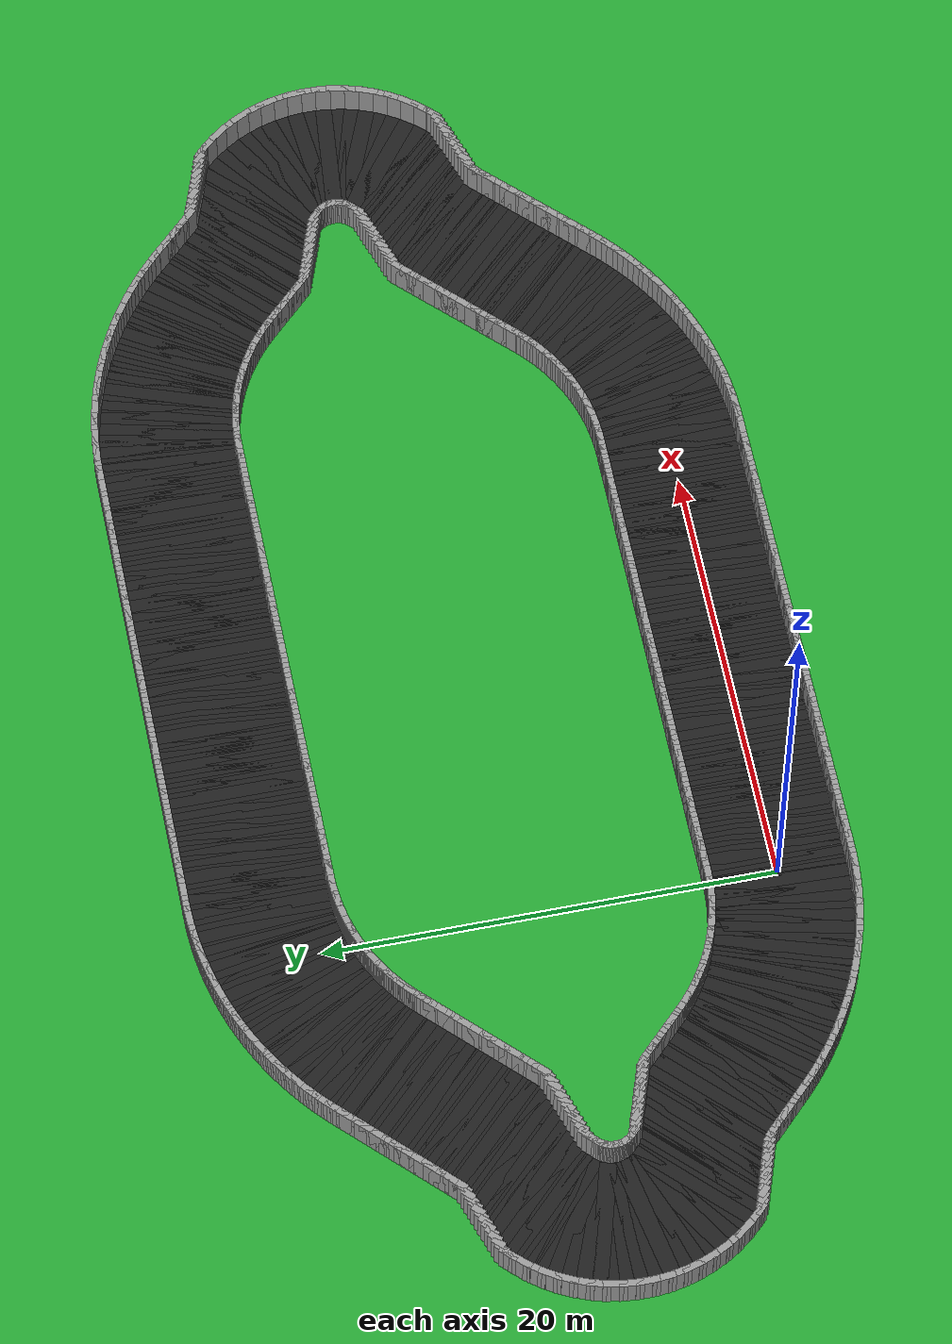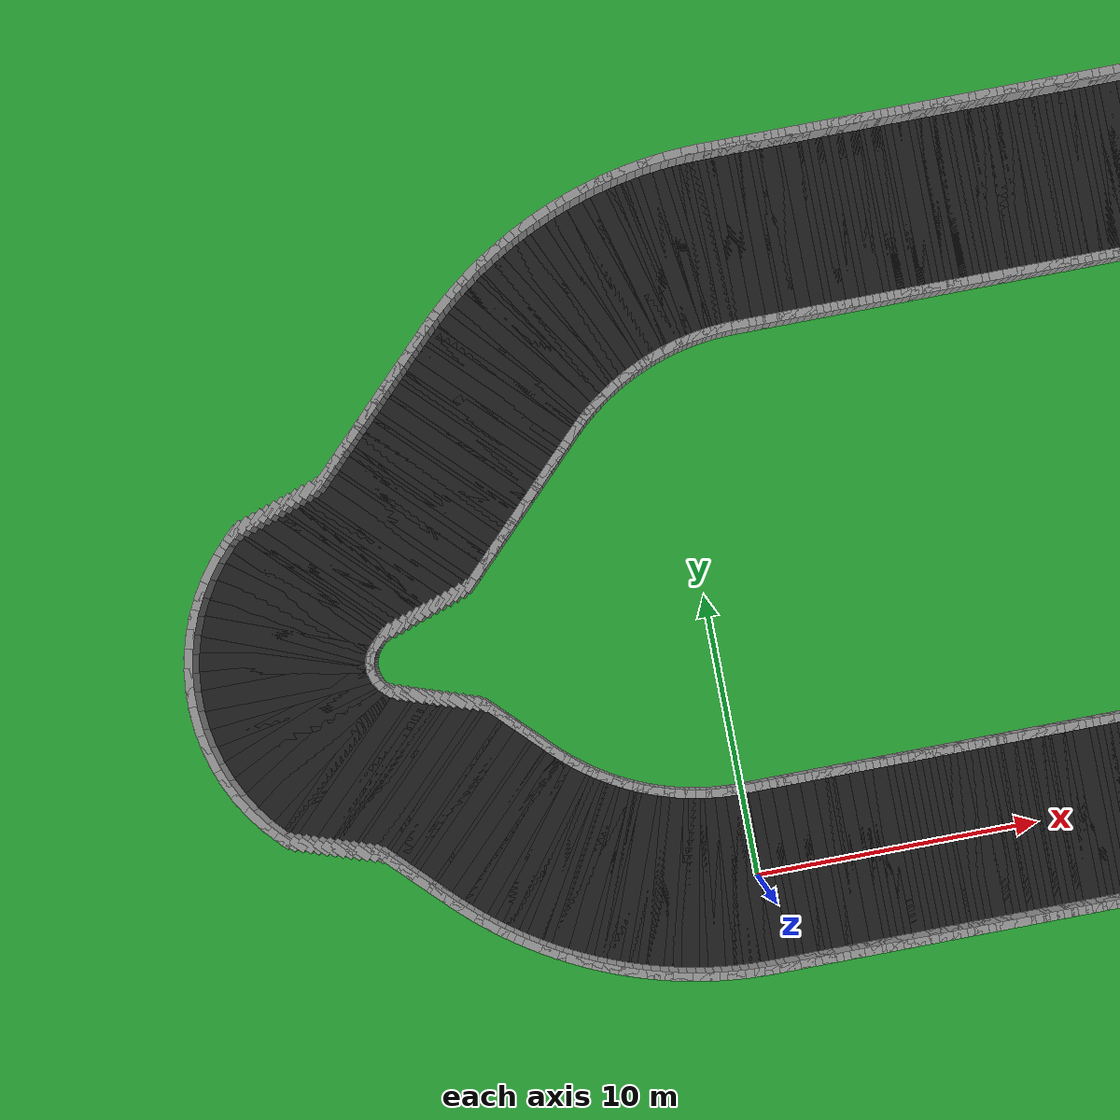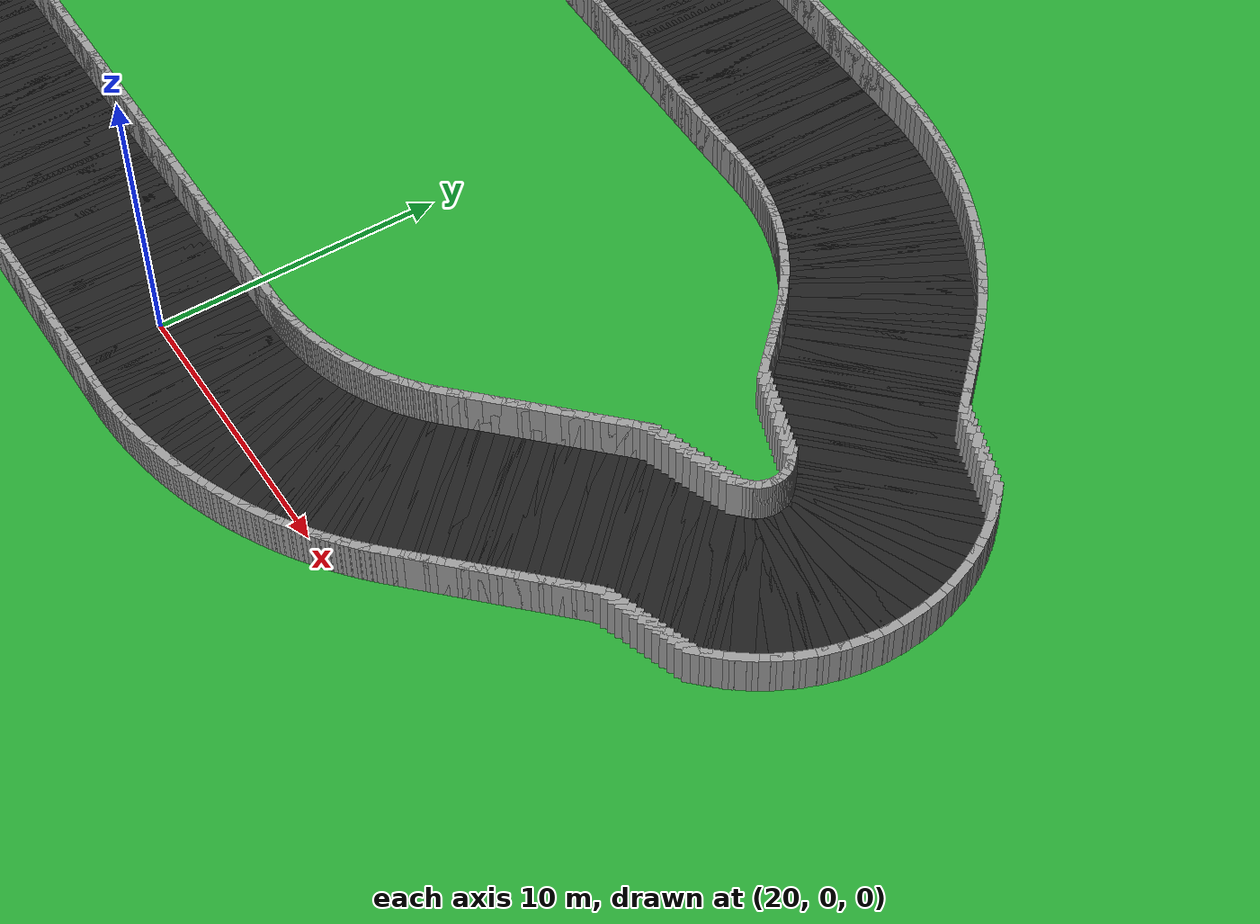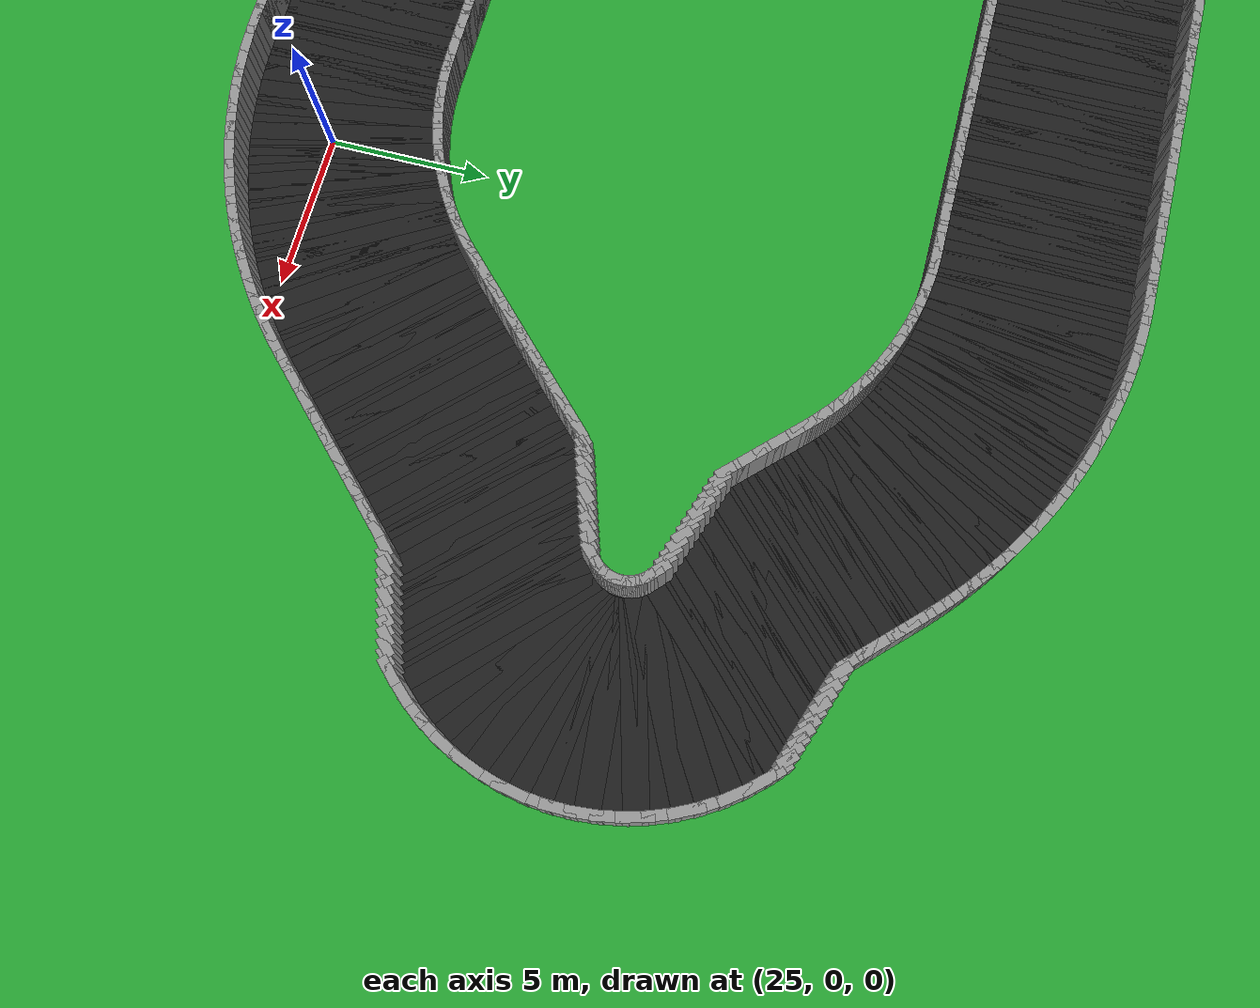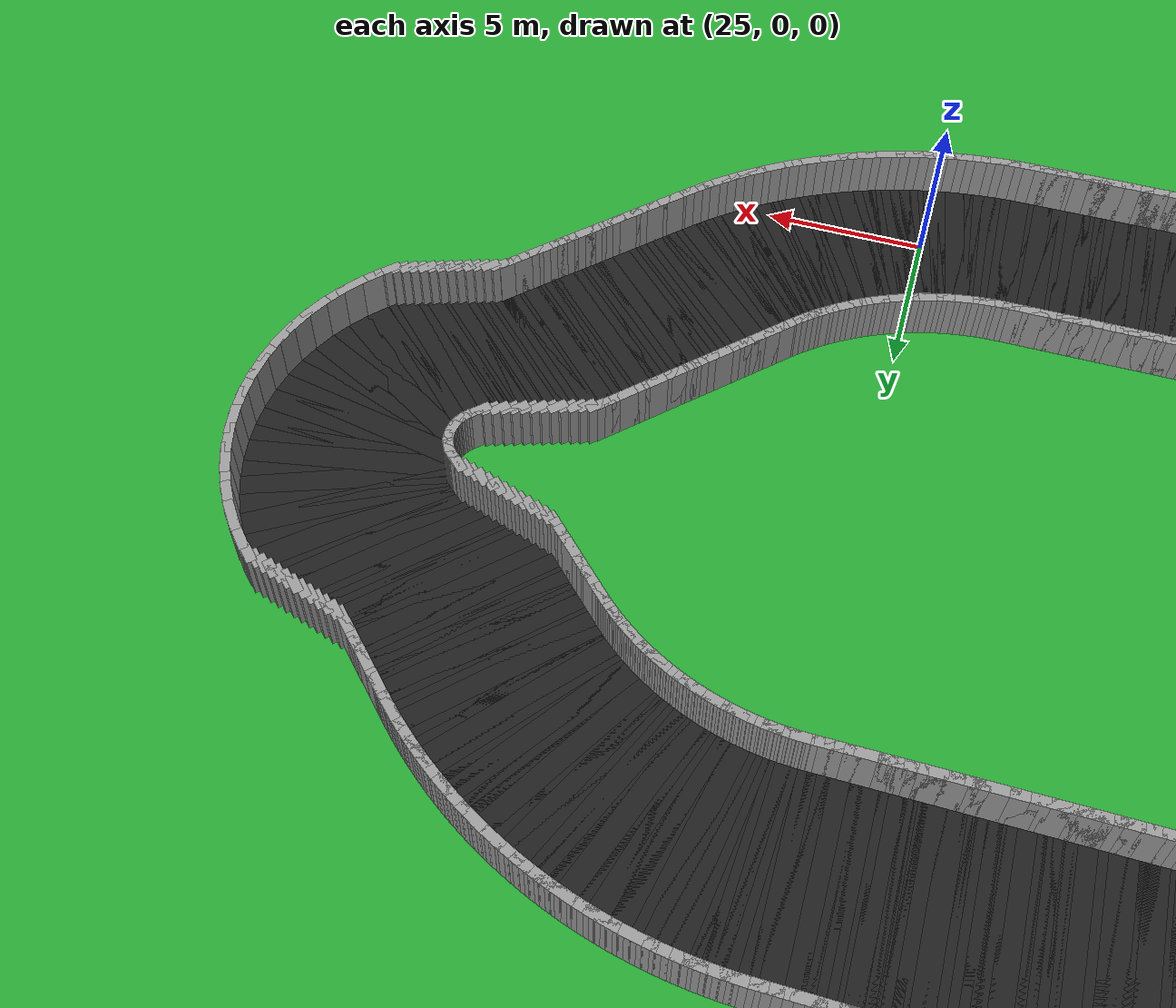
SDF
<?xml version="1.0" ?>
<sdf version="1.6">
  <world name="loop_asymturn">
    <physics type="ode">
      <max_step_size>0.001</max_step_size>
      <real_time_factor>1.0</real_time_factor>
      <real_time_update_rate>1000</real_time_update_rate>
    </physics>
    <include><uri>model://sun</uri></include>

    <model name="ground_plane">
      <static>true</static>
      <link name="link">
        <collision name="collision">
          <surface><friction><ode><mu>100</mu><mu2>50</mu2></ode></friction></surface>
          <geometry><plane><normal>0 0 1</normal>
            <size>120 120</size></plane></geometry>
        </collision>
        <visual name="visual">
          <geometry><plane><normal>0 0 1</normal>
            <size>120 120</size></plane></geometry>
          <material><script>
            <uri>file://media/materials/scripts/gazebo.material</uri>
            <name>Gazebo/Green</name></script></material>
        </visual>
      </link>
    </model>

    <model name="asphalt_0">
      <static>true</static>
      <pose>0.125 0.000 0.005 0 0 0.00000</pose>
      <link name="link">
        <visual name="visual">
          <geometry><box><size>0.610 6.000 0.010</size></box></geometry>
          <material><script><uri>file://media/materials/scripts/gazebo.material</uri><name>Gazebo/Black</name></script></material>
        </visual>
      </link>
    </model>
    <model name="curbL_0">
      <static>true</static>
      <pose>0.125 3.150 0.750 0 0 0.00000</pose>
      <link name="link">
        <collision name="collision">
          <geometry><box><size>0.610 0.300 1.500</size></box></geometry>
        </collision>
        <visual name="visual">
          <geometry><box><size>0.610 0.300 1.500</size></box></geometry>
          <material><script><uri>file://media/materials/scripts/gazebo.material</uri><name>Gazebo/Grey</name></script></material>
        </visual>
      </link>
    </model>
    <model name="curbR_0">
      <static>true</static>
      <pose>0.125 -3.150 0.750 0 0 0.00000</pose>
      <link name="link">
        <collision name="collision">
          <geometry><box><size>0.610 0.300 1.500</size></box></geometry>
        </collision>
        <visual name="visual">
          <geometry><box><size>0.610 0.300 1.500</size></box></geometry>
          <material><script><uri>file://media/materials/scripts/gazebo.material</uri><name>Gazebo/Grey</name></script></material>
        </visual>
      </link>
    </model>
    <model name="asphalt_1">
      <static>true</static>
      <pose>0.375 0.000 0.005 0 0 0.00000</pose>
      <link name="link">
        <visual name="visual">
          <geometry><box><size>0.610 6.000 0.010</size></box></geometry>
          <material><script><uri>file://media/materials/scripts/gazebo.material</uri><name>Gazebo/Black</name></script></material>
        </visual>
      </link>
    </model>
    <model name="curbL_1">
      <static>true</static>
      <pose>0.375 3.150 0.750 0 0 0.00000</pose>
      <link name="link">
        <collision name="collision">
          <geometry><box><size>0.610 0.300 1.500</size></box></geometry>
        </collision>
        <visual name="visual">
          <geometry><box><size>0.610 0.300 1.500</size></box></geometry>
          <material><script><uri>file://media/materials/scripts/gazebo.material</uri><name>Gazebo/Grey</name></script></material>
        </visual>
      </link>
    </model>
    <model name="curbR_1">
      <static>true</static>
      <pose>0.375 -3.150 0.750 0 0 0.00000</pose>
      <link name="link">
        <collision name="collision">
          <geometry><box><size>0.610 0.300 1.500</size></box></geometry>
        </collision>
        <visual name="visual">
          <geometry><box><size>0.610 0.300 1.500</size></box></geometry>
          <material><script><uri>file://media/materials/scripts/gazebo.material</uri><name>Gazebo/Grey</name></script></material>
        </visual>
      </link>
    </model>
    <model name="asphalt_2">
      <static>true</static>
      <pose>0.625 0.000 0.005 0 0 0.00000</pose>
      <link name="link">
        <visual name="visual">
          <geometry><box><size>0.610 6.000 0.010</size></box></geometry>
          <material><script><uri>file://media/materials/scripts/gazebo.material</uri><name>Gazebo/Black</name></script></material>
        </visual>
      </link>
    </model>
    <model name="curbL_2">
      <static>true</static>
      <pose>0.625 3.150 0.750 0 0 0.00000</pose>
      <link name="link">
        <collision name="collision">
          <geometry><box><size>0.610 0.300 1.500</size></box></geometry>
        </collision>
        <visual name="visual">
          <geometry><box><size>0.610 0.300 1.500</size></box></geometry>
          <material><script><uri>file://media/materials/scripts/gazebo.material</uri><name>Gazebo/Grey</name></script></material>
        </visual>
      </link>
    </model>
    <model name="curbR_2">
      <static>true</static>
      <pose>0.625 -3.150 0.750 0 0 0.00000</pose>
      <link name="link">
        <collision name="collision">
          <geometry><box><size>0.610 0.300 1.500</size></box></geometry>
        </collision>
        <visual name="visual">
          <geometry><box><size>0.610 0.300 1.500</size></box></geometry>
          <material><script><uri>file://media/materials/scripts/gazebo.material</uri><name>Gazebo/Grey</name></script></material>
        </visual>
      </link>
    </model>
    <model name="asphalt_3">
      <static>true</static>
      <pose>0.875 0.000 0.005 0 0 0.00000</pose>
      <link name="link">
        <visual name="visual">
          <geometry><box><size>0.610 6.000 0.010</size></box></geometry>
          <material><script><uri>file://media/materials/scripts/gazebo.material</uri><name>Gazebo/Black</name></script></material>
        </visual>
      </link>
    </model>
    <model name="curbL_3">
      <static>true</static>
      <pose>0.875 3.150 0.750 0 0 0.00000</pose>
      <link name="link">
        <collision name="collision">
          <geometry><box><size>0.610 0.300 1.500</size></box></geometry>
        </collision>
        <visual name="visual">
          <geometry><box><size>0.610 0.300 1.500</size></box></geometry>
          <material><script><uri>file://media/materials/scripts/gazebo.material</uri><name>Gazebo/Grey</name></script></material>
        </visual>
      </link>
    </model>
    <model name="curbR_3">
      <static>true</static>
      <pose>0.875 -3.150 0.750 0 0 0.00000</pose>
      <link name="link">
        <collision name="collision">
          <geometry><box><size>0.610 0.300 1.500</size></box></geometry>
        </collision>
        <visual name="visual">
          <geometry><box><size>0.610 0.300 1.500</size></box></geometry>
          <material><script><uri>file://media/materials/scripts/gazebo.material</uri><name>Gazebo/Grey</name></script></material>
        </visual>
      </link>
    </model>
    <model name="asphalt_4">
      <static>true</static>
      <pose>1.125 0.000 0.005 0 0 0.00000</pose>
      <link name="link">
        <visual name="visual">
          <geometry><box><size>0.610 6.000 0.010</size></box></geometry>
          <material><script><uri>file://media/materials/scripts/gazebo.material</uri><name>Gazebo/Black</name></script></material>
        </visual>
      </link>
    </model>
    <model name="curbL_4">
      <static>true</static>
      <pose>1.125 3.150 0.750 0 0 0.00000</pose>
      <link name="link">
        <collision name="collision">
          <geometry><box><size>0.610 0.300 1.500</size></box></geometry>
        </collision>
        <visual name="visual">
          <geometry><box><size>0.610 0.300 1.500</size></box></geometry>
          <material><script><uri>file://media/materials/scripts/gazebo.material</uri><name>Gazebo/Grey</name></script></material>
        </visual>
      </link>
    </model>
    <model name="curbR_4">
      <static>true</static>
      <pose>1.125 -3.150 0.750 0 0 0.00000</pose>
      <link name="link">
        <collision name="collision">
          <geometry><box><size>0.610 0.300 1.500</size></box></geometry>
        </collision>
        <visual name="visual">
          <geometry><box><size>0.610 0.300 1.500</size></box></geometry>
          <material><script><uri>file://media/materials/scripts/gazebo.material</uri><name>Gazebo/Grey</name></script></material>
        </visual>
      </link>
    </model>
    <model name="asphalt_5">
      <static>true</static>
      <pose>1.375 0.000 0.005 0 0 0.00000</pose>
      <link name="link">
        <visual name="visual">
          <geometry><box><size>0.610 6.000 0.010</size></box></geometry>
          <material><script><uri>file://media/materials/scripts/gazebo.material</uri><name>Gazebo/Black</name></script></material>
        </visual>
      </link>
    </model>
    <model name="curbL_5">
      <static>true</static>
      <pose>1.375 3.150 0.750 0 0 0.00000</pose>
      <link name="link">
        <collision name="collision">
          <geometry><box><size>0.610 0.300 1.500</size></box></geometry>
        </collision>
        <visual name="visual">
          <geometry><box><size>0.610 0.300 1.500</size></box></geometry>
          <material><script><uri>file://media/materials/scripts/gazebo.material</uri><name>Gazebo/Grey</name></script></material>
        </visual>
      </link>
    </model>
    <model name="curbR_5">
      <static>true</static>
      <pose>1.375 -3.150 0.750 0 0 0.00000</pose>
      <link name="link">
        <collision name="collision">
          <geometry><box><size>0.610 0.300 1.500</size></box></geometry>
        </collision>
        <visual name="visual">
          <geometry><box><size>0.610 0.300 1.500</size></box></geometry>
          <material><script><uri>file://media/materials/scripts/gazebo.material</uri><name>Gazebo/Grey</name></script></material>
        </visual>
      </link>
    </model>
    <model name="asphalt_6">
      <static>true</static>
      <pose>1.625 0.000 0.005 0 0 0.00000</pose>
      <link name="link">
        <visual name="visual">
          <geometry><box><size>0.610 6.000 0.010</size></box></geometry>
          <material><script><uri>file://media/materials/scripts/gazebo.material</uri><name>Gazebo/Black</name></script></material>
        </visual>
      </link>
    </model>
    <model name="curbL_6">
      <static>true</static>
      <pose>1.625 3.150 0.750 0 0 0.00000</pose>
      <link name="link">
        <collision name="collision">
          <geometry><box><size>0.610 0.300 1.500</size></box></geometry>
        </collision>
        <visual name="visual">
          <geometry><box><size>0.610 0.300 1.500</size></box></geometry>
          <material><script><uri>file://media/materials/scripts/gazebo.material</uri><name>Gazebo/Grey</name></script></material>
        </visual>
      </link>
    </model>
    <model name="curbR_6">
      <static>true</static>
      <pose>1.625 -3.150 0.750 0 0 0.00000</pose>
      <link name="link">
        <collision name="collision">
          <geometry><box><size>0.610 0.300 1.500</size></box></geometry>
        </collision>
        <visual name="visual">
          <geometry><box><size>0.610 0.300 1.500</size></box></geometry>
          <material><script><uri>file://media/materials/scripts/gazebo.material</uri><name>Gazebo/Grey</name></script></material>
        </visual>
      </link>
    </model>
    <model name="asphalt_7">
      <static>true</static>
      <pose>1.875 0.000 0.005 0 0 0.00000</pose>
      <link name="link">
        <visual name="visual">
          <geometry><box><size>0.610 6.000 0.010</size></box></geometry>
          <material><script><uri>file://media/materials/scripts/gazebo.material</uri><name>Gazebo/Black</name></script></material>
        </visual>
      </link>
    </model>
    <model name="curbL_7">
      <static>true</static>
      <pose>1.875 3.150 0.750 0 0 0.00000</pose>
      <link name="link">
        <collision name="collision">
          <geometry><box><size>0.610 0.300 1.500</size></box></geometry>
        </collision>
        <visual name="visual">
          <geometry><box><size>0.610 0.300 1.500</size></box></geometry>
          <material><script><uri>file://media/materials/scripts/gazebo.material</uri><name>Gazebo/Grey</name></script></material>
        </visual>
      </link>
    </model>
    <model name="curbR_7">
      <static>true</static>
      <pose>1.875 -3.150 0.750 0 0 0.00000</pose>
      <link name="link">
        <collision name="collision">
          <geometry><box><size>0.610 0.300 1.500</size></box></geometry>
        </collision>
        <visual name="visual">
          <geometry><box><size>0.610 0.300 1.500</size></box></geometry>
          <material><script><uri>file://media/materials/scripts/gazebo.material</uri><name>Gazebo/Grey</name></script></material>
        </visual>
      </link>
    </model>
    <model name="asphalt_8">
      <static>true</static>
      <pose>2.125 0.000 0.005 0 0 0.00000</pose>
      <link name="link">
        <visual name="visual">
          <geometry><box><size>0.610 6.000 0.010</size></box></geometry>
          <material><script><uri>file://media/materials/scripts/gazebo.material</uri><name>Gazebo/Black</name></script></material>
        </visual>
      </link>
    </model>
    <model name="curbL_8">
      <static>true</static>
      <pose>2.125 3.150 0.750 0 0 0.00000</pose>
      <link name="link">
        <collision name="collision">
          <geometry><box><size>0.610 0.300 1.500</size></box></geometry>
        </collision>
        <visual name="visual">
          <geometry><box><size>0.610 0.300 1.500</size></box></geometry>
          <material><script><uri>file://media/materials/scripts/gazebo.material</uri><name>Gazebo/Grey</name></script></material>
        </visual>
      </link>
    </model>
    <model name="curbR_8">
      <static>true</static>
      <pose>2.125 -3.150 0.750 0 0 0.00000</pose>
      <link name="link">
        <collision name="collision">
          <geometry><box><size>0.610 0.300 1.500</size></box></geometry>
        </collision>
        <visual name="visual">
          <geometry><box><size>0.610 0.300 1.500</size></box></geometry>
          <material><script><uri>file://media/materials/scripts/gazebo.material</uri><name>Gazebo/Grey</name></script></material>
        </visual>
      </link>
    </model>
    <model name="asphalt_9">
      <static>true</static>
      <pose>2.375 0.000 0.005 0 0 0.00000</pose>
      <link name="link">
        <visual name="visual">
          <geometry><box><size>0.610 6.000 0.010</size></box></geometry>
          <material><script><uri>file://media/materials/scripts/gazebo.material</uri><name>Gazebo/Black</name></script></material>
        </visual>
      </link>
    </model>
    <model name="curbL_9">
      <static>true</static>
      <pose>2.375 3.150 0.750 0 0 0.00000</pose>
      <link name="link">
        <collision name="collision">
          <geometry><box><size>0.610 0.300 1.500</size></box></geometry>
        </collision>
        <visual name="visual">
          <geometry><box><size>0.610 0.300 1.500</size></box></geometry>
          <material><script><uri>file://media/materials/scripts/gazebo.material</uri><name>Gazebo/Grey</name></script></material>
        </visual>
      </link>
    </model>
    <model name="curbR_9">
      <static>true</static>
      <pose>2.375 -3.150 0.750 0 0 0.00000</pose>
      <link name="link">
        <collision name="collision">
          <geometry><box><size>0.610 0.300 1.500</size></box></geometry>
        </collision>
        <visual name="visual">
          <geometry><box><size>0.610 0.300 1.500</size></box></geometry>
          <material><script><uri>file://media/materials/scripts/gazebo.material</uri><name>Gazebo/Grey</name></script></material>
        </visual>
      </link>
    </model>
    <model name="asphalt_10">
      <static>true</static>
      <pose>2.625 0.000 0.005 0 0 0.00000</pose>
      <link name="link">
        <visual name="visual">
          <geometry><box><size>0.610 6.000 0.010</size></box></geometry>
          <material><script><uri>file://media/materials/scripts/gazebo.material</uri><name>Gazebo/Black</name></script></material>
        </visual>
      </link>
    </model>
    <model name="curbL_10">
      <static>true</static>
      <pose>2.625 3.150 0.750 0 0 0.00000</pose>
      <link name="link">
        <collision name="collision">
          <geometry><box><size>0.610 0.300 1.500</size></box></geometry>
        </collision>
        <visual name="visual">
          <geometry><box><size>0.610 0.300 1.500</size></box></geometry>
          <material><script><uri>file://media/materials/scripts/gazebo.material</uri><name>Gazebo/Grey</name></script></material>
        </visual>
      </link>
    </model>
    <model name="curbR_10">
      <static>true</static>
      <pose>2.625 -3.150 0.750 0 0 0.00000</pose>
      <link name="link">
        <collision name="collision">
          <geometry><box><size>0.610 0.300 1.500</size></box></geometry>
        </collision>
        <visual name="visual">
          <geometry><box><size>0.610 0.300 1.500</size></box></geometry>
          <material><script><uri>file://media/materials/scripts/gazebo.material</uri><name>Gazebo/Grey</name></script></material>
        </visual>
      </link>
    </model>
    <model name="asphalt_11">
      <static>true</static>
      <pose>2.875 0.000 0.005 0 0 0.00000</pose>
      <link name="link">
        <visual name="visual">
          <geometry><box><size>0.610 6.000 0.010</size></box></geometry>
          <material><script><uri>file://media/materials/scripts/gazebo.material</uri><name>Gazebo/Black</name></script></material>
        </visual>
      </link>
    </model>
    <model name="curbL_11">
      <static>true</static>
      <pose>2.875 3.150 0.750 0 0 0.00000</pose>
      <link name="link">
        <collision name="collision">
          <geometry><box><size>0.610 0.300 1.500</size></box></geometry>
        </collision>
        <visual name="visual">
          <geometry><box><size>0.610 0.300 1.500</size></box></geometry>
          <material><script><uri>file://media/materials/scripts/gazebo.material</uri><name>Gazebo/Grey</name></script></material>
        </visual>
      </link>
    </model>
    <model name="curbR_11">
      <static>true</static>
      <pose>2.875 -3.150 0.750 0 0 0.00000</pose>
      <link name="link">
        <collision name="collision">
          <geometry><box><size>0.610 0.300 1.500</size></box></geometry>
        </collision>
        <visual name="visual">
          <geometry><box><size>0.610 0.300 1.500</size></box></geometry>
          <material><script><uri>file://media/materials/scripts/gazebo.material</uri><name>Gazebo/Grey</name></script></material>
        </visual>
      </link>
    </model>
    <model name="asphalt_12">
      <static>true</static>
      <pose>3.125 0.000 0.005 0 0 0.00000</pose>
      <link name="link">
        <visual name="visual">
          <geometry><box><size>0.610 6.000 0.010</size></box></geometry>
          <material><script><uri>file://media/materials/scripts/gazebo.material</uri><name>Gazebo/Black</name></script></material>
        </visual>
      </link>
    </model>
    <model name="curbL_12">
      <static>true</static>
      <pose>3.125 3.150 0.750 0 0 0.00000</pose>
      <link name="link">
        <collision name="collision">
          <geometry><box><size>0.610 0.300 1.500</size></box></geometry>
        </collision>
        <visual name="visual">
          <geometry><box><size>0.610 0.300 1.500</size></box></geometry>
          <material><script><uri>file://media/materials/scripts/gazebo.material</uri><name>Gazebo/Grey</name></script></material>
        </visual>
      </link>
    </model>
    <model name="curbR_12">
      <static>true</static>
      <pose>3.125 -3.150 0.750 0 0 0.00000</pose>
      <link name="link">
        <collision name="collision">
          <geometry><box><size>0.610 0.300 1.500</size></box></geometry>
        </collision>
        <visual name="visual">
          <geometry><box><size>0.610 0.300 1.500</size></box></geometry>
          <material><script><uri>file://media/materials/scripts/gazebo.material</uri><name>Gazebo/Grey</name></script></material>
        </visual>
      </link>
    </model>
    <model name="asphalt_13">
      <static>true</static>
      <pose>3.375 0.000 0.005 0 0 0.00000</pose>
      <link name="link">
        <visual name="visual">
          <geometry><box><size>0.610 6.000 0.010</size></box></geometry>
          <material><script><uri>file://media/materials/scripts/gazebo.material</uri><name>Gazebo/Black</name></script></material>
        </visual>
      </link>
    </model>
    <model name="curbL_13">
      <static>true</static>
      <pose>3.375 3.150 0.750 0 0 0.00000</pose>
      <link name="link">
        <collision name="collision">
          <geometry><box><size>0.610 0.300 1.500</size></box></geometry>
        </collision>
        <visual name="visual">
          <geometry><box><size>0.610 0.300 1.500</size></box></geometry>
          <material><script><uri>file://media/materials/scripts/gazebo.material</uri><name>Gazebo/Grey</name></script></material>
        </visual>
      </link>
    </model>
    <model name="curbR_13">
      <static>true</static>
      <pose>3.375 -3.150 0.750 0 0 0.00000</pose>
      <link name="link">
        <collision name="collision">
          <geometry><box><size>0.610 0.300 1.500</size></box></geometry>
        </collision>
        <visual name="visual">
          <geometry><box><size>0.610 0.300 1.500</size></box></geometry>
          <material><script><uri>file://media/materials/scripts/gazebo.material</uri><name>Gazebo/Grey</name></script></material>
        </visual>
      </link>
    </model>
    <model name="asphalt_14">
      <static>true</static>
      <pose>3.625 0.000 0.005 0 0 0.00000</pose>
      <link name="link">
        <visual name="visual">
          <geometry><box><size>0.610 6.000 0.010</size></box></geometry>
          <material><script><uri>file://media/materials/scripts/gazebo.material</uri><name>Gazebo/Black</name></script></material>
        </visual>
      </link>
    </model>
    <model name="curbL_14">
      <static>true</static>
      <pose>3.625 3.150 0.750 0 0 0.00000</pose>
      <link name="link">
        <collision name="collision">
          <geometry><box><size>0.610 0.300 1.500</size></box></geometry>
        </collision>
        <visual name="visual">
          <geometry><box><size>0.610 0.300 1.500</size></box></geometry>
          <material><script><uri>file://media/materials/scripts/gazebo.material</uri><name>Gazebo/Grey</name></script></material>
        </visual>
      </link>
    </model>
    <model name="curbR_14">
      <static>true</static>
      <pose>3.625 -3.150 0.750 0 0 0.00000</pose>
      <link name="link">
        <collision name="collision">
          <geometry><box><size>0.610 0.300 1.500</size></box></geometry>
        </collision>
        <visual name="visual">
          <geometry><box><size>0.610 0.300 1.500</size></box></geometry>
          <material><script><uri>file://media/materials/scripts/gazebo.material</uri><name>Gazebo/Grey</name></script></material>
        </visual>
      </link>
    </model>
    <model name="asphalt_15">
      <static>true</static>
      <pose>3.875 0.000 0.005 0 0 0.00000</pose>
      <link name="link">
        <visual name="visual">
          <geometry><box><size>0.610 6.000 0.010</size></box></geometry>
          <material><script><uri>file://media/materials/scripts/gazebo.material</uri><name>Gazebo/Black</name></script></material>
        </visual>
      </link>
    </model>
    <model name="curbL_15">
      <static>true</static>
      <pose>3.875 3.150 0.750 0 0 0.00000</pose>
      <link name="link">
        <collision name="collision">
          <geometry><box><size>0.610 0.300 1.500</size></box></geometry>
        </collision>
        <visual name="visual">
          <geometry><box><size>0.610 0.300 1.500</size></box></geometry>
          <material><script><uri>file://media/materials/scripts/gazebo.material</uri><name>Gazebo/Grey</name></script></material>
        </visual>
      </link>
    </model>
    <model name="curbR_15">
      <static>true</static>
      <pose>3.875 -3.150 0.750 0 0 0.00000</pose>
      <link name="link">
        <collision name="collision">
          <geometry><box><size>0.610 0.300 1.500</size></box></geometry>
        </collision>
        <visual name="visual">
          <geometry><box><size>0.610 0.300 1.500</size></box></geometry>
          <material><script><uri>file://media/materials/scripts/gazebo.material</uri><name>Gazebo/Grey</name></script></material>
        </visual>
      </link>
    </model>
    <model name="asphalt_16">
      <static>true</static>
      <pose>4.125 0.000 0.005 0 0 0.00000</pose>
      <link name="link">
        <visual name="visual">
          <geometry><box><size>0.610 6.000 0.010</size></box></geometry>
          <material><script><uri>file://media/materials/scripts/gazebo.material</uri><name>Gazebo/Black</name></script></material>
        </visual>
      </link>
    </model>
    <model name="curbL_16">
      <static>true</static>
      <pose>4.125 3.150 0.750 0 0 0.00000</pose>
      <link name="link">
        <collision name="collision">
          <geometry><box><size>0.610 0.300 1.500</size></box></geometry>
        </collision>
        <visual name="visual">
          <geometry><box><size>0.610 0.300 1.500</size></box></geometry>
          <material><script><uri>file://media/materials/scripts/gazebo.material</uri><name>Gazebo/Grey</name></script></material>
        </visual>
      </link>
    </model>
    <model name="curbR_16">
      <static>true</static>
      <pose>4.125 -3.150 0.750 0 0 0.00000</pose>
      <link name="link">
        <collision name="collision">
          <geometry><box><size>0.610 0.300 1.500</size></box></geometry>
        </collision>
        <visual name="visual">
          <geometry><box><size>0.610 0.300 1.500</size></box></geometry>
          <material><script><uri>file://media/materials/scripts/gazebo.material</uri><name>Gazebo/Grey</name></script></material>
        </visual>
      </link>
    </model>
    <model name="asphalt_17">
      <static>true</static>
      <pose>4.375 0.000 0.005 0 0 0.00000</pose>
      <link name="link">
        <visual name="visual">
          <geometry><box><size>0.610 6.000 0.010</size></box></geometry>
          <material><script><uri>file://media/materials/scripts/gazebo.material</uri><name>Gazebo/Black</name></script></material>
        </visual>
      </link>
    </model>
    <model name="curbL_17">
      <static>true</static>
      <pose>4.375 3.150 0.750 0 0 0.00000</pose>
      <link name="link">
        <collision name="collision">
          <geometry><box><size>0.610 0.300 1.500</size></box></geometry>
        </collision>
        <visual name="visual">
          <geometry><box><size>0.610 0.300 1.500</size></box></geometry>
          <material><script><uri>file://media/materials/scripts/gazebo.material</uri><name>Gazebo/Grey</name></script></material>
        </visual>
      </link>
    </model>
    <model name="curbR_17">
      <static>true</static>
      <pose>4.375 -3.150 0.750 0 0 0.00000</pose>
      <link name="link">
        <collision name="collision">
          <geometry><box><size>0.610 0.300 1.500</size></box></geometry>
        </collision>
        <visual name="visual">
          <geometry><box><size>0.610 0.300 1.500</size></box></geometry>
          <material><script><uri>file://media/materials/scripts/gazebo.material</uri><name>Gazebo/Grey</name></script></material>
        </visual>
      </link>
    </model>
    <model name="asphalt_18">
      <static>true</static>
      <pose>4.625 0.000 0.005 0 0 0.00000</pose>
      <link name="link">
        <visual name="visual">
          <geometry><box><size>0.610 6.000 0.010</size></box></geometry>
          <material><script><uri>file://media/materials/scripts/gazebo.material</uri><name>Gazebo/Black</name></script></material>
        </visual>
      </link>
    </model>
    <model name="curbL_18">
      <static>true</static>
      <pose>4.625 3.150 0.750 0 0 0.00000</pose>
      <link name="link">
        <collision name="collision">
          <geometry><box><size>0.610 0.300 1.500</size></box></geometry>
        </collision>
        <visual name="visual">
          <geometry><box><size>0.610 0.300 1.500</size></box></geometry>
          <material><script><uri>file://media/materials/scripts/gazebo.material</uri><name>Gazebo/Grey</name></script></material>
        </visual>
      </link>
    </model>
    <model name="curbR_18">
      <static>true</static>
      <pose>4.625 -3.150 0.750 0 0 0.00000</pose>
      <link name="link">
        <collision name="collision">
          <geometry><box><size>0.610 0.300 1.500</size></box></geometry>
        </collision>
        <visual name="visual">
          <geometry><box><size>0.610 0.300 1.500</size></box></geometry>
          <material><script><uri>file://media/materials/scripts/gazebo.material</uri><name>Gazebo/Grey</name></script></material>
        </visual>
      </link>
    </model>
    <model name="asphalt_19">
      <static>true</static>
      <pose>4.875 0.000 0.005 0 0 0.00000</pose>
      <link name="link">
        <visual name="visual">
          <geometry><box><size>0.610 6.000 0.010</size></box></geometry>
          <material><script><uri>file://media/materials/scripts/gazebo.material</uri><name>Gazebo/Black</name></script></material>
        </visual>
      </link>
    </model>
    <model name="curbL_19">
      <static>true</static>
      <pose>4.875 3.150 0.750 0 0 0.00000</pose>
      <link name="link">
        <collision name="collision">
          <geometry><box><size>0.610 0.300 1.500</size></box></geometry>
        </collision>
        <visual name="visual">
          <geometry><box><size>0.610 0.300 1.500</size></box></geometry>
          <material><script><uri>file://media/materials/scripts/gazebo.material</uri><name>Gazebo/Grey</name></script></material>
        </visual>
      </link>
    </model>
    <model name="curbR_19">
      <static>true</static>
      <pose>4.875 -3.150 0.750 0 0 0.00000</pose>
      <link name="link">
        <collision name="collision">
          <geometry><box><size>0.610 0.300 1.500</size></box></geometry>
        </collision>
        <visual name="visual">
          <geometry><box><size>0.610 0.300 1.500</size></box></geometry>
          <material><script><uri>file://media/materials/scripts/gazebo.material</uri><name>Gazebo/Grey</name></script></material>
        </visual>
      </link>
    </model>
    <model name="asphalt_20">
      <static>true</static>
      <pose>5.125 0.000 0.005 0 0 0.00000</pose>
      <link name="link">
        <visual name="visual">
          <geometry><box><size>0.610 6.000 0.010</size></box></geometry>
          <material><script><uri>file://media/materials/scripts/gazebo.material</uri><name>Gazebo/Black</name></script></material>
        </visual>
      </link>
    </model>
    <model name="curbL_20">
      <static>true</static>
      <pose>5.125 3.150 0.750 0 0 0.00000</pose>
      <link name="link">
        <collision name="collision">
          <geometry><box><size>0.610 0.300 1.500</size></box></geometry>
        </collision>
        <visual name="visual">
          <geometry><box><size>0.610 0.300 1.500</size></box></geometry>
          <material><script><uri>file://media/materials/scripts/gazebo.material</uri><name>Gazebo/Grey</name></script></material>
        </visual>
      </link>
    </model>
    <model name="curbR_20">
      <static>true</static>
      <pose>5.125 -3.150 0.750 0 0 0.00000</pose>
      <link name="link">
        <collision name="collision">
          <geometry><box><size>0.610 0.300 1.500</size></box></geometry>
        </collision>
        <visual name="visual">
          <geometry><box><size>0.610 0.300 1.500</size></box></geometry>
          <material><script><uri>file://media/materials/scripts/gazebo.material</uri><name>Gazebo/Grey</name></script></material>
        </visual>
      </link>
    </model>
    <model name="asphalt_21">
      <static>true</static>
      <pose>5.375 0.000 0.005 0 0 0.00000</pose>
      <link name="link">
        <visual name="visual">
          <geometry><box><size>0.610 6.000 0.010</size></box></geometry>
          <material><script><uri>file://media/materials/scripts/gazebo.material</uri><name>Gazebo/Black</name></script></material>
        </visual>
      </link>
    </model>
    <model name="curbL_21">
      <static>true</static>
      <pose>5.375 3.150 0.750 0 0 0.00000</pose>
      <link name="link">
        <collision name="collision">
          <geometry><box><size>0.610 0.300 1.500</size></box></geometry>
        </collision>
        <visual name="visual">
          <geometry><box><size>0.610 0.300 1.500</size></box></geometry>
          <material><script><uri>file://media/materials/scripts/gazebo.material</uri><name>Gazebo/Grey</name></script></material>
        </visual>
      </link>
    </model>
    <model name="curbR_21">
      <static>true</static>
      <pose>5.375 -3.150 0.750 0 0 0.00000</pose>
      <link name="link">
        <collision name="collision">
          <geometry><box><size>0.610 0.300 1.500</size></box></geometry>
        </collision>
        <visual name="visual">
          <geometry><box><size>0.610 0.300 1.500</size></box></geometry>
          <material><script><uri>file://media/materials/scripts/gazebo.material</uri><name>Gazebo/Grey</name></script></material>
        </visual>
      </link>
    </model>
    <model name="asphalt_22">
      <static>true</static>
      <pose>5.625 0.000 0.005 0 0 0.00000</pose>
      <link name="link">
        <visual name="visual">
          <geometry><box><size>0.610 6.000 0.010</size></box></geometry>
          <material><script><uri>file://media/materials/scripts/gazebo.material</uri><name>Gazebo/Black</name></script></material>
        </visual>
      </link>
    </model>
    <model name="curbL_22">
      <static>true</static>
      <pose>5.625 3.150 0.750 0 0 0.00000</pose>
      <link name="link">
        <collision name="collision">
          <geometry><box><size>0.610 0.300 1.500</size></box></geometry>
        </collision>
        <visual name="visual">
          <geometry><box><size>0.610 0.300 1.500</size></box></geometry>
          <material><script><uri>file://media/materials/scripts/gazebo.material</uri><name>Gazebo/Grey</name></script></material>
        </visual>
      </link>
    </model>
    <model name="curbR_22">
      <static>true</static>
      <pose>5.625 -3.150 0.750 0 0 0.00000</pose>
      <link name="link">
        <collision name="collision">
          <geometry><box><size>0.610 0.300 1.500</size></box></geometry>
        </collision>
        <visual name="visual">
          <geometry><box><size>0.610 0.300 1.500</size></box></geometry>
          <material><script><uri>file://media/materials/scripts/gazebo.material</uri><name>Gazebo/Grey</name></script></material>
        </visual>
      </link>
    </model>
    <model name="asphalt_23">
      <static>true</static>
      <pose>5.875 0.000 0.005 0 0 0.00000</pose>
      <link name="link">
        <visual name="visual">
          <geometry><box><size>0.610 6.000 0.010</size></box></geometry>
          <material><script><uri>file://media/materials/scripts/gazebo.material</uri><name>Gazebo/Black</name></script></material>
        </visual>
      </link>
    </model>
    <model name="curbL_23">
      <static>true</static>
      <pose>5.875 3.150 0.750 0 0 0.00000</pose>
      <link name="link">
        <collision name="collision">
          <geometry><box><size>0.610 0.300 1.500</size></box></geometry>
        </collision>
        <visual name="visual">
          <geometry><box><size>0.610 0.300 1.500</size></box></geometry>
          <material><script><uri>file://media/materials/scripts/gazebo.material</uri><name>Gazebo/Grey</name></script></material>
        </visual>
      </link>
    </model>
    <model name="curbR_23">
      <static>true</static>
      <pose>5.875 -3.150 0.750 0 0 0.00000</pose>
      <link name="link">
        <collision name="collision">
          <geometry><box><size>0.610 0.300 1.500</size></box></geometry>
        </collision>
        <visual name="visual">
          <geometry><box><size>0.610 0.300 1.500</size></box></geometry>
          <material><script><uri>file://media/materials/scripts/gazebo.material</uri><name>Gazebo/Grey</name></script></material>
        </visual>
      </link>
    </model>
    <model name="asphalt_24">
      <static>true</static>
      <pose>6.125 0.000 0.005 0 0 0.00000</pose>
      <link name="link">
        <visual name="visual">
          <geometry><box><size>0.610 6.000 0.010</size></box></geometry>
          <material><script><uri>file://media/materials/scripts/gazebo.material</uri><name>Gazebo/Black</name></script></material>
        </visual>
      </link>
    </model>
    <model name="curbL_24">
      <static>true</static>
      <pose>6.125 3.150 0.750 0 0 0.00000</pose>
      <link name="link">
        <collision name="collision">
          <geometry><box><size>0.610 0.300 1.500</size></box></geometry>
        </collision>
        <visual name="visual">
          <geometry><box><size>0.610 0.300 1.500</size></box></geometry>
          <material><script><uri>file://media/materials/scripts/gazebo.material</uri><name>Gazebo/Grey</name></script></material>
        </visual>
      </link>
    </model>
    <model name="curbR_24">
      <static>true</static>
      <pose>6.125 -3.150 0.750 0 0 0.00000</pose>
      <link name="link">
        <collision name="collision">
          <geometry><box><size>0.610 0.300 1.500</size></box></geometry>
        </collision>
        <visual name="visual">
          <geometry><box><size>0.610 0.300 1.500</size></box></geometry>
          <material><script><uri>file://media/materials/scripts/gazebo.material</uri><name>Gazebo/Grey</name></script></material>
        </visual>
      </link>
    </model>
    <model name="asphalt_25">
      <static>true</static>
      <pose>6.375 0.000 0.005 0 0 0.00000</pose>
      <link name="link">
        <visual name="visual">
          <geometry><box><size>0.610 6.000 0.010</size></box></geometry>
          <material><script><uri>file://media/materials/scripts/gazebo.material</uri><name>Gazebo/Black</name></script></material>
        </visual>
      </link>
    </model>
    <model name="curbL_25">
      <static>true</static>
      <pose>6.375 3.150 0.750 0 0 0.00000</pose>
      <link name="link">
        <collision name="collision">
          <geometry><box><size>0.610 0.300 1.500</size></box></geometry>
        </collision>
        <visual name="visual">
          <geometry><box><size>0.610 0.300 1.500</size></box></geometry>
          <material><script><uri>file://media/materials/scripts/gazebo.material</uri><name>Gazebo/Grey</name></script></material>
        </visual>
      </link>
    </model>
    <model name="curbR_25">
      <static>true</static>
      <pose>6.375 -3.150 0.750 0 0 0.00000</pose>
      <link name="link">
        <collision name="collision">
          <geometry><box><size>0.610 0.300 1.500</size></box></geometry>
        </collision>
        <visual name="visual">
          <geometry><box><size>0.610 0.300 1.500</size></box></geometry>
          <material><script><uri>file://media/materials/scripts/gazebo.material</uri><name>Gazebo/Grey</name></script></material>
        </visual>
      </link>
    </model>
    <model name="asphalt_26">
      <static>true</static>
      <pose>6.625 0.000 0.005 0 0 0.00000</pose>
      <link name="link">
        <visual name="visual">
          <geometry><box><size>0.610 6.000 0.010</size></box></geometry>
          <material><script><uri>file://media/materials/scripts/gazebo.material</uri><name>Gazebo/Black</name></script></material>
        </visual>
      </link>
    </model>
    <model name="curbL_26">
      <static>true</static>
      <pose>6.625 3.150 0.750 0 0 0.00000</pose>
      <link name="link">
        <collision name="collision">
          <geometry><box><size>0.610 0.300 1.500</size></box></geometry>
        </collision>
        <visual name="visual">
          <geometry><box><size>0.610 0.300 1.500</size></box></geometry>
          <material><script><uri>file://media/materials/scripts/gazebo.material</uri><name>Gazebo/Grey</name></script></material>
        </visual>
      </link>
    </model>
    <model name="curbR_26">
      <static>true</static>
      <pose>6.625 -3.150 0.750 0 0 0.00000</pose>
      <link name="link">
        <collision name="collision">
          <geometry><box><size>0.610 0.300 1.500</size></box></geometry>
        </collision>
        <visual name="visual">
          <geometry><box><size>0.610 0.300 1.500</size></box></geometry>
          <material><script><uri>file://media/materials/scripts/gazebo.material</uri><name>Gazebo/Grey</name></script></material>
        </visual>
      </link>
    </model>
    <model name="asphalt_27">
      <static>true</static>
      <pose>6.875 0.000 0.005 0 0 0.00000</pose>
      <link name="link">
        <visual name="visual">
          <geometry><box><size>0.610 6.000 0.010</size></box></geometry>
          <material><script><uri>file://media/materials/scripts/gazebo.material</uri><name>Gazebo/Black</name></script></material>
        </visual>
      </link>
    </model>
    <model name="curbL_27">
      <static>true</static>
      <pose>6.875 3.150 0.750 0 0 0.00000</pose>
      <link name="link">
        <collision name="collision">
          <geometry><box><size>0.610 0.300 1.500</size></box></geometry>
        </collision>
        <visual name="visual">
          <geometry><box><size>0.610 0.300 1.500</size></box></geometry>
          <material><script><uri>file://media/materials/scripts/gazebo.material</uri><name>Gazebo/Grey</name></script></material>
        </visual>
      </link>
    </model>
    <model name="curbR_27">
      <static>true</static>
      <pose>6.875 -3.150 0.750 0 0 0.00000</pose>
      <link name="link">
        <collision name="collision">
          <geometry><box><size>0.610 0.300 1.500</size></box></geometry>
        </collision>
        <visual name="visual">
          <geometry><box><size>0.610 0.300 1.500</size></box></geometry>
          <material><script><uri>file://media/materials/scripts/gazebo.material</uri><name>Gazebo/Grey</name></script></material>
        </visual>
      </link>
    </model>
    <model name="asphalt_28">
      <static>true</static>
      <pose>7.125 0.000 0.005 0 0 0.00000</pose>
      <link name="link">
        <visual name="visual">
          <geometry><box><size>0.610 6.000 0.010</size></box></geometry>
          <material><script><uri>file://media/materials/scripts/gazebo.material</uri><name>Gazebo/Black</name></script></material>
        </visual>
      </link>
    </model>
    <model name="curbL_28">
      <static>true</static>
      <pose>7.125 3.150 0.750 0 0 0.00000</pose>
      <link name="link">
        <collision name="collision">
          <geometry><box><size>0.610 0.300 1.500</size></box></geometry>
        </collision>
        <visual name="visual">
          <geometry><box><size>0.610 0.300 1.500</size></box></geometry>
          <material><script><uri>file://media/materials/scripts/gazebo.material</uri><name>Gazebo/Grey</name></script></material>
        </visual>
      </link>
    </model>
    <model name="curbR_28">
      <static>true</static>
      <pose>7.125 -3.150 0.750 0 0 0.00000</pose>
      <link name="link">
        <collision name="collision">
          <geometry><box><size>0.610 0.300 1.500</size></box></geometry>
        </collision>
        <visual name="visual">
          <geometry><box><size>0.610 0.300 1.500</size></box></geometry>
          <material><script><uri>file://media/materials/scripts/gazebo.material</uri><name>Gazebo/Grey</name></script></material>
        </visual>
      </link>
    </model>
    <model name="asphalt_29">
      <static>true</static>
      <pose>7.375 0.000 0.005 0 0 0.00000</pose>
      <link name="link">
        <visual name="visual">
          <geometry><box><size>0.610 6.000 0.010</size></box></geometry>
          <material><script><uri>file://media/materials/scripts/gazebo.material</uri><name>Gazebo/Black</name></script></material>
        </visual>
      </link>
    </model>
    <model name="curbL_29">
      <static>true</static>
      <pose>7.375 3.150 0.750 0 0 0.00000</pose>
      <link name="link">
        <collision name="collision">
          <geometry><box><size>0.610 0.300 1.500</size></box></geometry>
        </collision>
        <visual name="visual">
          <geometry><box><size>0.610 0.300 1.500</size></box></geometry>
          <material><script><uri>file://media/materials/scripts/gazebo.material</uri><name>Gazebo/Grey</name></script></material>
        </visual>
      </link>
    </model>
    <model name="curbR_29">
      <static>true</static>
      <pose>7.375 -3.150 0.750 0 0 0.00000</pose>
      <link name="link">
        <collision name="collision">
          <geometry><box><size>0.610 0.300 1.500</size></box></geometry>
        </collision>
        <visual name="visual">
          <geometry><box><size>0.610 0.300 1.500</size></box></geometry>
          <material><script><uri>file://media/materials/scripts/gazebo.material</uri><name>Gazebo/Grey</name></script></material>
        </visual>
      </link>
    </model>
    <model name="asphalt_30">
      <static>true</static>
      <pose>7.625 0.000 0.005 0 0 0.00000</pose>
      <link name="link">
        <visual name="visual">
          <geometry><box><size>0.610 6.000 0.010</size></box></geometry>
          <material><script><uri>file://media/materials/scripts/gazebo.material</uri><name>Gazebo/Black</name></script></material>
        </visual>
      </link>
    </model>
    <model name="curbL_30">
      <static>true</static>
      <pose>7.625 3.150 0.750 0 0 0.00000</pose>
      <link name="link">
        <collision name="collision">
          <geometry><box><size>0.610 0.300 1.500</size></box></geometry>
        </collision>
        <visual name="visual">
          <geometry><box><size>0.610 0.300 1.500</size></box></geometry>
          <material><script><uri>file://media/materials/scripts/gazebo.material</uri><name>Gazebo/Grey</name></script></material>
        </visual>
      </link>
    </model>
    <model name="curbR_30">
      <static>true</static>
      <pose>7.625 -3.150 0.750 0 0 0.00000</pose>
      <link name="link">
        <collision name="collision">
          <geometry><box><size>0.610 0.300 1.500</size></box></geometry>
        </collision>
        <visual name="visual">
          <geometry><box><size>0.610 0.300 1.500</size></box></geometry>
          <material><script><uri>file://media/materials/scripts/gazebo.material</uri><name>Gazebo/Grey</name></script></material>
        </visual>
      </link>
    </model>
    <model name="asphalt_31">
      <static>true</static>
      <pose>7.875 0.000 0.005 0 0 0.00000</pose>
      <link name="link">
        <visual name="visual">
          <geometry><box><size>0.610 6.000 0.010</size></box></geometry>
          <material><script><uri>file://media/materials/scripts/gazebo.material</uri><name>Gazebo/Black</name></script></material>
        </visual>
      </link>
    </model>
    <model name="curbL_31">
      <static>true</static>
      <pose>7.875 3.150 0.750 0 0 0.00000</pose>
      <link name="link">
        <collision name="collision">
          <geometry><box><size>0.610 0.300 1.500</size></box></geometry>
        </collision>
        <visual name="visual">
          <geometry><box><size>0.610 0.300 1.500</size></box></geometry>
          <material><script><uri>file://media/materials/scripts/gazebo.material</uri><name>Gazebo/Grey</name></script></material>
        </visual>
      </link>
    </model>
    <model name="curbR_31">
      <static>true</static>
      <pose>7.875 -3.150 0.750 0 0 0.00000</pose>
      <link name="link">
        <collision name="collision">
          <geometry><box><size>0.610 0.300 1.500</size></box></geometry>
        </collision>
        <visual name="visual">
          <geometry><box><size>0.610 0.300 1.500</size></box></geometry>
          <material><script><uri>file://media/materials/scripts/gazebo.material</uri><name>Gazebo/Grey</name></script></material>
        </visual>
      </link>
    </model>
    <model name="asphalt_32">
      <static>true</static>
      <pose>8.125 0.000 0.005 0 0 0.00000</pose>
      <link name="link">
        <visual name="visual">
          <geometry><box><size>0.610 6.000 0.010</size></box></geometry>
          <material><script><uri>file://media/materials/scripts/gazebo.material</uri><name>Gazebo/Black</name></script></material>
        </visual>
      </link>
    </model>
    <model name="curbL_32">
      <static>true</static>
      <pose>8.125 3.150 0.750 0 0 0.00000</pose>
      <link name="link">
        <collision name="collision">
          <geometry><box><size>0.610 0.300 1.500</size></box></geometry>
        </collision>
        <visual name="visual">
          <geometry><box><size>0.610 0.300 1.500</size></box></geometry>
          <material><script><uri>file://media/materials/scripts/gazebo.material</uri><name>Gazebo/Grey</name></script></material>
        </visual>
      </link>
    </model>
    <model name="curbR_32">
      <static>true</static>
      <pose>8.125 -3.150 0.750 0 0 0.00000</pose>
      <link name="link">
        <collision name="collision">
          <geometry><box><size>0.610 0.300 1.500</size></box></geometry>
        </collision>
        <visual name="visual">
          <geometry><box><size>0.610 0.300 1.500</size></box></geometry>
          <material><script><uri>file://media/materials/scripts/gazebo.material</uri><name>Gazebo/Grey</name></script></material>
        </visual>
      </link>
    </model>
    <model name="asphalt_33">
      <static>true</static>
      <pose>8.375 0.000 0.005 0 0 0.00000</pose>
      <link name="link">
        <visual name="visual">
          <geometry><box><size>0.610 6.000 0.010</size></box></geometry>
          <material><script><uri>file://media/materials/scripts/gazebo.material</uri><name>Gazebo/Black</name></script></material>
        </visual>
      </link>
    </model>
    <model name="curbL_33">
      <static>true</static>
      <pose>8.375 3.150 0.750 0 0 0.00000</pose>
      <link name="link">
        <collision name="collision">
          <geometry><box><size>0.610 0.300 1.500</size></box></geometry>
        </collision>
        <visual name="visual">
          <geometry><box><size>0.610 0.300 1.500</size></box></geometry>
          <material><script><uri>file://media/materials/scripts/gazebo.material</uri><name>Gazebo/Grey</name></script></material>
        </visual>
      </link>
    </model>
    <model name="curbR_33">
      <static>true</static>
      <pose>8.375 -3.150 0.750 0 0 0.00000</pose>
      <link name="link">
        <collision name="collision">
          <geometry><box><size>0.610 0.300 1.500</size></box></geometry>
        </collision>
        <visual name="visual">
          <geometry><box><size>0.610 0.300 1.500</size></box></geometry>
          <material><script><uri>file://media/materials/scripts/gazebo.material</uri><name>Gazebo/Grey</name></script></material>
        </visual>
      </link>
    </model>
    <model name="asphalt_34">
      <static>true</static>
      <pose>8.625 0.000 0.005 0 0 0.00000</pose>
      <link name="link">
        <visual name="visual">
          <geometry><box><size>0.610 6.000 0.010</size></box></geometry>
          <material><script><uri>file://media/materials/scripts/gazebo.material</uri><name>Gazebo/Black</name></script></material>
        </visual>
      </link>
    </model>
    <model name="curbL_34">
      <static>true</static>
      <pose>8.625 3.150 0.750 0 0 0.00000</pose>
      <link name="link">
        <collision name="collision">
          <geometry><box><size>0.610 0.300 1.500</size></box></geometry>
        </collision>
        <visual name="visual">
          <geometry><box><size>0.610 0.300 1.500</size></box></geometry>
          <material><script><uri>file://media/materials/scripts/gazebo.material</uri><name>Gazebo/Grey</name></script></material>
        </visual>
      </link>
    </model>
    <model name="curbR_34">
      <static>true</static>
      <pose>8.625 -3.150 0.750 0 0 0.00000</pose>
      <link name="link">
        <collision name="collision">
          <geometry><box><size>0.610 0.300 1.500</size></box></geometry>
        </collision>
        <visual name="visual">
          <geometry><box><size>0.610 0.300 1.500</size></box></geometry>
          <material><script><uri>file://media/materials/scripts/gazebo.material</uri><name>Gazebo/Grey</name></script></material>
        </visual>
      </link>
    </model>
    <model name="asphalt_35">
      <static>true</static>
      <pose>8.875 0.000 0.005 0 0 0.00000</pose>
      <link name="link">
        <visual name="visual">
          <geometry><box><size>0.610 6.000 0.010</size></box></geometry>
          <material><script><uri>file://media/materials/scripts/gazebo.material</uri><name>Gazebo/Black</name></script></material>
        </visual>
      </link>
    </model>
    <model name="curbL_35">
      <static>true</static>
      <pose>8.875 3.150 0.750 0 0 0.00000</pose>
      <link name="link">
        <collision name="collision">
          <geometry><box><size>0.610 0.300 1.500</size></box></geometry>
        </collision>
        <visual name="visual">
          <geometry><box><size>0.610 0.300 1.500</size></box></geometry>
          <material><script><uri>file://media/materials/scripts/gazebo.material</uri><name>Gazebo/Grey</name></script></material>
        </visual>
      </link>
    </model>
    <model name="curbR_35">
      <static>true</static>
      <pose>8.875 -3.150 0.750 0 0 0.00000</pose>
      <link name="link">
        <collision name="collision">
          <geometry><box><size>0.610 0.300 1.500</size></box></geometry>
        </collision>
        <visual name="visual">
          <geometry><box><size>0.610 0.300 1.500</size></box></geometry>
          <material><script><uri>file://media/materials/scripts/gazebo.material</uri><name>Gazebo/Grey</name></script></material>
        </visual>
      </link>
    </model>
    <model name="asphalt_36">
      <static>true</static>
      <pose>9.125 0.000 0.005 0 0 0.00000</pose>
      <link name="link">
        <visual name="visual">
          <geometry><box><size>0.610 6.000 0.010</size></box></geometry>
          <material><script><uri>file://media/materials/scripts/gazebo.material</uri><name>Gazebo/Black</name></script></material>
        </visual>
      </link>
    </model>
    <model name="curbL_36">
      <static>true</static>
      <pose>9.125 3.150 0.750 0 0 0.00000</pose>
      <link name="link">
        <collision name="collision">
          <geometry><box><size>0.610 0.300 1.500</size></box></geometry>
        </collision>
        <visual name="visual">
          <geometry><box><size>0.610 0.300 1.500</size></box></geometry>
          <material><script><uri>file://media/materials/scripts/gazebo.material</uri><name>Gazebo/Grey</name></script></material>
        </visual>
      </link>
    </model>
    <model name="curbR_36">
      <static>true</static>
      <pose>9.125 -3.150 0.750 0 0 0.00000</pose>
      <link name="link">
        <collision name="collision">
          <geometry><box><size>0.610 0.300 1.500</size></box></geometry>
        </collision>
        <visual name="visual">
          <geometry><box><size>0.610 0.300 1.500</size></box></geometry>
          <material><script><uri>file://media/materials/scripts/gazebo.material</uri><name>Gazebo/Grey</name></script></material>
        </visual>
      </link>
    </model>
    <model name="asphalt_37">
      <static>true</static>
      <pose>9.375 0.000 0.005 0 0 0.00000</pose>
      <link name="link">
        <visual name="visual">
          <geometry><box><size>0.610 6.000 0.010</size></box></geometry>
          <material><script><uri>file://media/materials/scripts/gazebo.material</uri><name>Gazebo/Black</name></script></material>
        </visual>
      </link>
    </model>
    <model name="curbL_37">
      <static>true</static>
      <pose>9.375 3.150 0.750 0 0 0.00000</pose>
      <link name="link">
        <collision name="collision">
          <geometry><box><size>0.610 0.300 1.500</size></box></geometry>
        </collision>
        <visual name="visual">
          <geometry><box><size>0.610 0.300 1.500</size></box></geometry>
          <material><script><uri>file://media/materials/scripts/gazebo.material</uri><name>Gazebo/Grey</name></script></material>
        </visual>
      </link>
    </model>
    <model name="curbR_37">
      <static>true</static>
      <pose>9.375 -3.150 0.750 0 0 0.00000</pose>
      <link name="link">
        <collision name="collision">
          <geometry><box><size>0.610 0.300 1.500</size></box></geometry>
        </collision>
        <visual name="visual">
          <geometry><box><size>0.610 0.300 1.500</size></box></geometry>
          <material><script><uri>file://media/materials/scripts/gazebo.material</uri><name>Gazebo/Grey</name></script></material>
        </visual>
      </link>
    </model>
    <model name="asphalt_38">
      <static>true</static>
      <pose>9.625 0.000 0.005 0 0 0.00000</pose>
      <link name="link">
        <visual name="visual">
          <geometry><box><size>0.610 6.000 0.010</size></box></geometry>
          <material><script><uri>file://media/materials/scripts/gazebo.material</uri><name>Gazebo/Black</name></script></material>
        </visual>
      </link>
    </model>
    <model name="curbL_38">
      <static>true</static>
      <pose>9.625 3.150 0.750 0 0 0.00000</pose>
      <link name="link">
        <collision name="collision">
          <geometry><box><size>0.610 0.300 1.500</size></box></geometry>
        </collision>
        <visual name="visual">
          <geometry><box><size>0.610 0.300 1.500</size></box></geometry>
          <material><script><uri>file://media/materials/scripts/gazebo.material</uri><name>Gazebo/Grey</name></script></material>
        </visual>
      </link>
    </model>
    <model name="curbR_38">
      <static>true</static>
      <pose>9.625 -3.150 0.750 0 0 0.00000</pose>
      <link name="link">
        <collision name="collision">
          <geometry><box><size>0.610 0.300 1.500</size></box></geometry>
        </collision>
        <visual name="visual">
          <geometry><box><size>0.610 0.300 1.500</size></box></geometry>
          <material><script><uri>file://media/materials/scripts/gazebo.material</uri><name>Gazebo/Grey</name></script></material>
        </visual>
      </link>
    </model>
    <model name="asphalt_39">
      <static>true</static>
      <pose>9.875 0.000 0.005 0 0 0.00000</pose>
      <link name="link">
        <visual name="visual">
          <geometry><box><size>0.610 6.000 0.010</size></box></geometry>
          <material><script><uri>file://media/materials/scripts/gazebo.material</uri><name>Gazebo/Black</name></script></material>
        </visual>
      </link>
    </model>
    <model name="curbL_39">
      <static>true</static>
      <pose>9.875 3.150 0.750 0 0 0.00000</pose>
      <link name="link">
        <collision name="collision">
          <geometry><box><size>0.610 0.300 1.500</size></box></geometry>
        </collision>
        <visual name="visual">
          <geometry><box><size>0.610 0.300 1.500</size></box></geometry>
          <material><script><uri>file://media/materials/scripts/gazebo.material</uri><name>Gazebo/Grey</name></script></material>
        </visual>
      </link>
    </model>
    <model name="curbR_39">
      <static>true</static>
      <pose>9.875 -3.150 0.750 0 0 0.00000</pose>
      <link name="link">
        <collision name="collision">
          <geometry><box><size>0.610 0.300 1.500</size></box></geometry>
        </collision>
        <visual name="visual">
          <geometry><box><size>0.610 0.300 1.500</size></box></geometry>
          <material><script><uri>file://media/materials/scripts/gazebo.material</uri><name>Gazebo/Grey</name></script></material>
        </visual>
      </link>
    </model>
    <model name="asphalt_40">
      <static>true</static>
      <pose>10.125 0.000 0.005 0 0 0.00000</pose>
      <link name="link">
        <visual name="visual">
          <geometry><box><size>0.610 6.000 0.010</size></box></geometry>
          <material><script><uri>file://media/materials/scripts/gazebo.material</uri><name>Gazebo/Black</name></script></material>
        </visual>
      </link>
    </model>
    <model name="curbL_40">
      <static>true</static>
      <pose>10.125 3.150 0.750 0 0 0.00000</pose>
      <link name="link">
        <collision name="collision">
          <geometry><box><size>0.610 0.300 1.500</size></box></geometry>
        </collision>
        <visual name="visual">
          <geometry><box><size>0.610 0.300 1.500</size></box></geometry>
          <material><script><uri>file://media/materials/scripts/gazebo.material</uri><name>Gazebo/Grey</name></script></material>
        </visual>
      </link>
    </model>
    <model name="curbR_40">
      <static>true</static>
      <pose>10.125 -3.150 0.750 0 0 0.00000</pose>
      <link name="link">
        <collision name="collision">
          <geometry><box><size>0.610 0.300 1.500</size></box></geometry>
        </collision>
        <visual name="visual">
          <geometry><box><size>0.610 0.300 1.500</size></box></geometry>
          <material><script><uri>file://media/materials/scripts/gazebo.material</uri><name>Gazebo/Grey</name></script></material>
        </visual>
      </link>
    </model>
    <model name="asphalt_41">
      <static>true</static>
      <pose>10.375 0.000 0.005 0 0 0.00000</pose>
      <link name="link">
        <visual name="visual">
          <geometry><box><size>0.610 6.000 0.010</size></box></geometry>
          <material><script><uri>file://media/materials/scripts/gazebo.material</uri><name>Gazebo/Black</name></script></material>
        </visual>
      </link>
    </model>
    <model name="curbL_41">
      <static>true</static>
      <pose>10.375 3.150 0.750 0 0 0.00000</pose>
      <link name="link">
        <collision name="collision">
          <geometry><box><size>0.610 0.300 1.500</size></box></geometry>
        </collision>
        <visual name="visual">
          <geometry><box><size>0.610 0.300 1.500</size></box></geometry>
          <material><script><uri>file://media/materials/scripts/gazebo.material</uri><name>Gazebo/Grey</name></script></material>
        </visual>
      </link>
    </model>
    <model name="curbR_41">
      <static>true</static>
      <pose>10.375 -3.150 0.750 0 0 0.00000</pose>
      <link name="link">
        <collision name="collision">
          <geometry><box><size>0.610 0.300 1.500</size></box></geometry>
        </collision>
        <visual name="visual">
          <geometry><box><size>0.610 0.300 1.500</size></box></geometry>
          <material><script><uri>file://media/materials/scripts/gazebo.material</uri><name>Gazebo/Grey</name></script></material>
        </visual>
      </link>
    </model>
    <model name="asphalt_42">
      <static>true</static>
      <pose>10.625 0.000 0.005 0 0 0.00000</pose>
      <link name="link">
        <visual name="visual">
          <geometry><box><size>0.610 6.000 0.010</size></box></geometry>
          <material><script><uri>file://media/materials/scripts/gazebo.material</uri><name>Gazebo/Black</name></script></material>
        </visual>
      </link>
    </model>
    <model name="curbL_42">
      <static>true</static>
      <pose>10.625 3.150 0.750 0 0 0.00000</pose>
      <link name="link">
        <collision name="collision">
          <geometry><box><size>0.610 0.300 1.500</size></box></geometry>
        </collision>
        <visual name="visual">
          <geometry><box><size>0.610 0.300 1.500</size></box></geometry>
          <material><script><uri>file://media/materials/scripts/gazebo.material</uri><name>Gazebo/Grey</name></script></material>
        </visual>
      </link>
    </model>
    <model name="curbR_42">
      <static>true</static>
      <pose>10.625 -3.150 0.750 0 0 0.00000</pose>
      <link name="link">
        <collision name="collision">
          <geometry><box><size>0.610 0.300 1.500</size></box></geometry>
        </collision>
        <visual name="visual">
          <geometry><box><size>0.610 0.300 1.500</size></box></geometry>
          <material><script><uri>file://media/materials/scripts/gazebo.material</uri><name>Gazebo/Grey</name></script></material>
        </visual>
      </link>
    </model>
    <model name="asphalt_43">
      <static>true</static>
      <pose>10.875 0.000 0.005 0 0 0.00000</pose>
      <link name="link">
        <visual name="visual">
          <geometry><box><size>0.610 6.000 0.010</size></box></geometry>
          <material><script><uri>file://media/materials/scripts/gazebo.material</uri><name>Gazebo/Black</name></script></material>
        </visual>
      </link>
    </model>
    <model name="curbL_43">
      <static>true</static>
      <pose>10.875 3.150 0.750 0 0 0.00000</pose>
      <link name="link">
        <collision name="collision">
          <geometry><box><size>0.610 0.300 1.500</size></box></geometry>
        </collision>
        <visual name="visual">
          <geometry><box><size>0.610 0.300 1.500</size></box></geometry>
          <material><script><uri>file://media/materials/scripts/gazebo.material</uri><name>Gazebo/Grey</name></script></material>
        </visual>
      </link>
    </model>
    <model name="curbR_43">
      <static>true</static>
      <pose>10.875 -3.150 0.750 0 0 0.00000</pose>
      <link name="link">
        <collision name="collision">
          <geometry><box><size>0.610 0.300 1.500</size></box></geometry>
        </collision>
        <visual name="visual">
          <geometry><box><size>0.610 0.300 1.500</size></box></geometry>
          <material><script><uri>file://media/materials/scripts/gazebo.material</uri><name>Gazebo/Grey</name></script></material>
        </visual>
      </link>
    </model>
    <model name="asphalt_44">
      <static>true</static>
      <pose>11.125 0.000 0.005 0 0 0.00000</pose>
      <link name="link">
        <visual name="visual">
          <geometry><box><size>0.610 6.000 0.010</size></box></geometry>
          <material><script><uri>file://media/materials/scripts/gazebo.material</uri><name>Gazebo/Black</name></script></material>
        </visual>
      </link>
    </model>
    <model name="curbL_44">
      <static>true</static>
      <pose>11.125 3.150 0.750 0 0 0.00000</pose>
      <link name="link">
        <collision name="collision">
          <geometry><box><size>0.610 0.300 1.500</size></box></geometry>
        </collision>
        <visual name="visual">
          <geometry><box><size>0.610 0.300 1.500</size></box></geometry>
          <material><script><uri>file://media/materials/scripts/gazebo.material</uri><name>Gazebo/Grey</name></script></material>
        </visual>
      </link>
    </model>
    <model name="curbR_44">
      <static>true</static>
      <pose>11.125 -3.150 0.750 0 0 0.00000</pose>
      <link name="link">
        <collision name="collision">
          <geometry><box><size>0.610 0.300 1.500</size></box></geometry>
        </collision>
        <visual name="visual">
          <geometry><box><size>0.610 0.300 1.500</size></box></geometry>
          <material><script><uri>file://media/materials/scripts/gazebo.material</uri><name>Gazebo/Grey</name></script></material>
        </visual>
      </link>
    </model>
    <model name="asphalt_45">
      <static>true</static>
      <pose>11.375 0.000 0.005 0 0 0.00000</pose>
      <link name="link">
        <visual name="visual">
          <geometry><box><size>0.610 6.000 0.010</size></box></geometry>
          <material><script><uri>file://media/materials/scripts/gazebo.material</uri><name>Gazebo/Black</name></script></material>
        </visual>
      </link>
    </model>
    <model name="curbL_45">
      <static>true</static>
      <pose>11.375 3.150 0.750 0 0 0.00000</pose>
      <link name="link">
        <collision name="collision">
          <geometry><box><size>0.610 0.300 1.500</size></box></geometry>
        </collision>
        <visual name="visual">
          <geometry><box><size>0.610 0.300 1.500</size></box></geometry>
          <material><script><uri>file://media/materials/scripts/gazebo.material</uri><name>Gazebo/Grey</name></script></material>
        </visual>
      </link>
    </model>
    <model name="curbR_45">
      <static>true</static>
      <pose>11.375 -3.150 0.750 0 0 0.00000</pose>
      <link name="link">
        <collision name="collision">
          <geometry><box><size>0.610 0.300 1.500</size></box></geometry>
        </collision>
        <visual name="visual">
          <geometry><box><size>0.610 0.300 1.500</size></box></geometry>
          <material><script><uri>file://media/materials/scripts/gazebo.material</uri><name>Gazebo/Grey</name></script></material>
        </visual>
      </link>
    </model>
    <model name="asphalt_46">
      <static>true</static>
      <pose>11.625 0.000 0.005 0 0 0.00000</pose>
      <link name="link">
        <visual name="visual">
          <geometry><box><size>0.610 6.000 0.010</size></box></geometry>
          <material><script><uri>file://media/materials/scripts/gazebo.material</uri><name>Gazebo/Black</name></script></material>
        </visual>
      </link>
    </model>
    <model name="curbL_46">
      <static>true</static>
      <pose>11.625 3.150 0.750 0 0 0.00000</pose>
      <link name="link">
        <collision name="collision">
          <geometry><box><size>0.610 0.300 1.500</size></box></geometry>
        </collision>
        <visual name="visual">
          <geometry><box><size>0.610 0.300 1.500</size></box></geometry>
          <material><script><uri>file://media/materials/scripts/gazebo.material</uri><name>Gazebo/Grey</name></script></material>
        </visual>
      </link>
    </model>
    <model name="curbR_46">
      <static>true</static>
      <pose>11.625 -3.150 0.750 0 0 0.00000</pose>
      <link name="link">
        <collision name="collision">
          <geometry><box><size>0.610 0.300 1.500</size></box></geometry>
        </collision>
        <visual name="visual">
          <geometry><box><size>0.610 0.300 1.500</size></box></geometry>
          <material><script><uri>file://media/materials/scripts/gazebo.material</uri><name>Gazebo/Grey</name></script></material>
        </visual>
      </link>
    </model>
    <model name="asphalt_47">
      <static>true</static>
      <pose>11.875 0.000 0.005 0 0 0.00000</pose>
      <link name="link">
        <visual name="visual">
          <geometry><box><size>0.610 6.000 0.010</size></box></geometry>
          <material><script><uri>file://media/materials/scripts/gazebo.material</uri><name>Gazebo/Black</name></script></material>
        </visual>
      </link>
    </model>
    <model name="curbL_47">
      <static>true</static>
      <pose>11.875 3.150 0.750 0 0 0.00000</pose>
      <link name="link">
        <collision name="collision">
          <geometry><box><size>0.610 0.300 1.500</size></box></geometry>
        </collision>
        <visual name="visual">
          <geometry><box><size>0.610 0.300 1.500</size></box></geometry>
          <material><script><uri>file://media/materials/scripts/gazebo.material</uri><name>Gazebo/Grey</name></script></material>
        </visual>
      </link>
    </model>
    <model name="curbR_47">
      <static>true</static>
      <pose>11.875 -3.150 0.750 0 0 0.00000</pose>
      <link name="link">
        <collision name="collision">
          <geometry><box><size>0.610 0.300 1.500</size></box></geometry>
        </collision>
        <visual name="visual">
          <geometry><box><size>0.610 0.300 1.500</size></box></geometry>
          <material><script><uri>file://media/materials/scripts/gazebo.material</uri><name>Gazebo/Grey</name></script></material>
        </visual>
      </link>
    </model>
    <model name="asphalt_48">
      <static>true</static>
      <pose>12.125 0.000 0.005 0 0 0.00000</pose>
      <link name="link">
        <visual name="visual">
          <geometry><box><size>0.610 6.000 0.010</size></box></geometry>
          <material><script><uri>file://media/materials/scripts/gazebo.material</uri><name>Gazebo/Black</name></script></material>
        </visual>
      </link>
    </model>
    <model name="curbL_48">
      <static>true</static>
      <pose>12.125 3.150 0.750 0 0 0.00000</pose>
      <link name="link">
        <collision name="collision">
          <geometry><box><size>0.610 0.300 1.500</size></box></geometry>
        </collision>
        <visual name="visual">
          <geometry><box><size>0.610 0.300 1.500</size></box></geometry>
          <material><script><uri>file://media/materials/scripts/gazebo.material</uri><name>Gazebo/Grey</name></script></material>
        </visual>
      </link>
    </model>
    <model name="curbR_48">
      <static>true</static>
      <pose>12.125 -3.150 0.750 0 0 0.00000</pose>
      <link name="link">
        <collision name="collision">
          <geometry><box><size>0.610 0.300 1.500</size></box></geometry>
        </collision>
        <visual name="visual">
          <geometry><box><size>0.610 0.300 1.500</size></box></geometry>
          <material><script><uri>file://media/materials/scripts/gazebo.material</uri><name>Gazebo/Grey</name></script></material>
        </visual>
      </link>
    </model>
    <model name="asphalt_49">
      <static>true</static>
      <pose>12.375 0.000 0.005 0 0 0.00000</pose>
      <link name="link">
        <visual name="visual">
          <geometry><box><size>0.610 6.000 0.010</size></box></geometry>
          <material><script><uri>file://media/materials/scripts/gazebo.material</uri><name>Gazebo/Black</name></script></material>
        </visual>
      </link>
    </model>
    <model name="curbL_49">
      <static>true</static>
      <pose>12.375 3.150 0.750 0 0 0.00000</pose>
      <link name="link">
        <collision name="collision">
          <geometry><box><size>0.610 0.300 1.500</size></box></geometry>
        </collision>
        <visual name="visual">
          <geometry><box><size>0.610 0.300 1.500</size></box></geometry>
          <material><script><uri>file://media/materials/scripts/gazebo.material</uri><name>Gazebo/Grey</name></script></material>
        </visual>
      </link>
    </model>
    <model name="curbR_49">
      <static>true</static>
      <pose>12.375 -3.150 0.750 0 0 0.00000</pose>
      <link name="link">
        <collision name="collision">
          <geometry><box><size>0.610 0.300 1.500</size></box></geometry>
        </collision>
        <visual name="visual">
          <geometry><box><size>0.610 0.300 1.500</size></box></geometry>
          <material><script><uri>file://media/materials/scripts/gazebo.material</uri><name>Gazebo/Grey</name></script></material>
        </visual>
      </link>
    </model>
    <model name="asphalt_50">
      <static>true</static>
      <pose>12.625 0.000 0.005 0 0 0.00000</pose>
      <link name="link">
        <visual name="visual">
          <geometry><box><size>0.610 6.000 0.010</size></box></geometry>
          <material><script><uri>file://media/materials/scripts/gazebo.material</uri><name>Gazebo/Black</name></script></material>
        </visual>
      </link>
    </model>
    <model name="curbL_50">
      <static>true</static>
      <pose>12.625 3.150 0.750 0 0 0.00000</pose>
      <link name="link">
        <collision name="collision">
          <geometry><box><size>0.610 0.300 1.500</size></box></geometry>
        </collision>
        <visual name="visual">
          <geometry><box><size>0.610 0.300 1.500</size></box></geometry>
          <material><script><uri>file://media/materials/scripts/gazebo.material</uri><name>Gazebo/Grey</name></script></material>
        </visual>
      </link>
    </model>
    <model name="curbR_50">
      <static>true</static>
      <pose>12.625 -3.150 0.750 0 0 0.00000</pose>
      <link name="link">
        <collision name="collision">
          <geometry><box><size>0.610 0.300 1.500</size></box></geometry>
        </collision>
        <visual name="visual">
          <geometry><box><size>0.610 0.300 1.500</size></box></geometry>
          <material><script><uri>file://media/materials/scripts/gazebo.material</uri><name>Gazebo/Grey</name></script></material>
        </visual>
      </link>
    </model>
    <model name="asphalt_51">
      <static>true</static>
      <pose>12.875 0.000 0.005 0 0 0.00000</pose>
      <link name="link">
        <visual name="visual">
          <geometry><box><size>0.610 6.000 0.010</size></box></geometry>
          <material><script><uri>file://media/materials/scripts/gazebo.material</uri><name>Gazebo/Black</name></script></material>
        </visual>
      </link>
    </model>
    <model name="curbL_51">
      <static>true</static>
      <pose>12.875 3.150 0.750 0 0 0.00000</pose>
      <link name="link">
        <collision name="collision">
          <geometry><box><size>0.610 0.300 1.500</size></box></geometry>
        </collision>
        <visual name="visual">
          <geometry><box><size>0.610 0.300 1.500</size></box></geometry>
          <material><script><uri>file://media/materials/scripts/gazebo.material</uri><name>Gazebo/Grey</name></script></material>
        </visual>
      </link>
    </model>
    <model name="curbR_51">
      <static>true</static>
      <pose>12.875 -3.150 0.750 0 0 0.00000</pose>
      <link name="link">
        <collision name="collision">
          <geometry><box><size>0.610 0.300 1.500</size></box></geometry>
        </collision>
        <visual name="visual">
          <geometry><box><size>0.610 0.300 1.500</size></box></geometry>
          <material><script><uri>file://media/materials/scripts/gazebo.material</uri><name>Gazebo/Grey</name></script></material>
        </visual>
      </link>
    </model>
    <model name="asphalt_52">
      <static>true</static>
      <pose>13.125 0.000 0.005 0 0 0.00000</pose>
      <link name="link">
        <visual name="visual">
          <geometry><box><size>0.610 6.000 0.010</size></box></geometry>
          <material><script><uri>file://media/materials/scripts/gazebo.material</uri><name>Gazebo/Black</name></script></material>
        </visual>
      </link>
    </model>
    <model name="curbL_52">
      <static>true</static>
      <pose>13.125 3.150 0.750 0 0 0.00000</pose>
      <link name="link">
        <collision name="collision">
          <geometry><box><size>0.610 0.300 1.500</size></box></geometry>
        </collision>
        <visual name="visual">
          <geometry><box><size>0.610 0.300 1.500</size></box></geometry>
          <material><script><uri>file://media/materials/scripts/gazebo.material</uri><name>Gazebo/Grey</name></script></material>
        </visual>
      </link>
    </model>
    <model name="curbR_52">
      <static>true</static>
      <pose>13.125 -3.150 0.750 0 0 0.00000</pose>
      <link name="link">
        <collision name="collision">
          <geometry><box><size>0.610 0.300 1.500</size></box></geometry>
        </collision>
        <visual name="visual">
          <geometry><box><size>0.610 0.300 1.500</size></box></geometry>
          <material><script><uri>file://media/materials/scripts/gazebo.material</uri><name>Gazebo/Grey</name></script></material>
        </visual>
      </link>
    </model>
    <model name="asphalt_53">
      <static>true</static>
      <pose>13.375 0.000 0.005 0 0 0.00000</pose>
      <link name="link">
        <visual name="visual">
          <geometry><box><size>0.610 6.000 0.010</size></box></geometry>
          <material><script><uri>file://media/materials/scripts/gazebo.material</uri><name>Gazebo/Black</name></script></material>
        </visual>
      </link>
    </model>
    <model name="curbL_53">
      <static>true</static>
      <pose>13.375 3.150 0.750 0 0 0.00000</pose>
      <link name="link">
        <collision name="collision">
          <geometry><box><size>0.610 0.300 1.500</size></box></geometry>
        </collision>
        <visual name="visual">
          <geometry><box><size>0.610 0.300 1.500</size></box></geometry>
          <material><script><uri>file://media/materials/scripts/gazebo.material</uri><name>Gazebo/Grey</name></script></material>
        </visual>
      </link>
    </model>
    <model name="curbR_53">
      <static>true</static>
      <pose>13.375 -3.150 0.750 0 0 0.00000</pose>
      <link name="link">
        <collision name="collision">
          <geometry><box><size>0.610 0.300 1.500</size></box></geometry>
        </collision>
        <visual name="visual">
          <geometry><box><size>0.610 0.300 1.500</size></box></geometry>
          <material><script><uri>file://media/materials/scripts/gazebo.material</uri><name>Gazebo/Grey</name></script></material>
        </visual>
      </link>
    </model>
    <model name="asphalt_54">
      <static>true</static>
      <pose>13.625 0.000 0.005 0 0 0.00000</pose>
      <link name="link">
        <visual name="visual">
          <geometry><box><size>0.610 6.000 0.010</size></box></geometry>
          <material><script><uri>file://media/materials/scripts/gazebo.material</uri><name>Gazebo/Black</name></script></material>
        </visual>
      </link>
    </model>
    <model name="curbL_54">
      <static>true</static>
      <pose>13.625 3.150 0.750 0 0 0.00000</pose>
      <link name="link">
        <collision name="collision">
          <geometry><box><size>0.610 0.300 1.500</size></box></geometry>
        </collision>
        <visual name="visual">
          <geometry><box><size>0.610 0.300 1.500</size></box></geometry>
          <material><script><uri>file://media/materials/scripts/gazebo.material</uri><name>Gazebo/Grey</name></script></material>
        </visual>
      </link>
    </model>
    <model name="curbR_54">
      <static>true</static>
      <pose>13.625 -3.150 0.750 0 0 0.00000</pose>
      <link name="link">
        <collision name="collision">
          <geometry><box><size>0.610 0.300 1.500</size></box></geometry>
        </collision>
        <visual name="visual">
          <geometry><box><size>0.610 0.300 1.500</size></box></geometry>
          <material><script><uri>file://media/materials/scripts/gazebo.material</uri><name>Gazebo/Grey</name></script></material>
        </visual>
      </link>
    </model>
    <model name="asphalt_55">
      <static>true</static>
      <pose>13.875 0.000 0.005 0 0 0.00000</pose>
      <link name="link">
        <visual name="visual">
          <geometry><box><size>0.610 6.000 0.010</size></box></geometry>
          <material><script><uri>file://media/materials/scripts/gazebo.material</uri><name>Gazebo/Black</name></script></material>
        </visual>
      </link>
    </model>
    <model name="curbL_55">
      <static>true</static>
      <pose>13.875 3.150 0.750 0 0 0.00000</pose>
      <link name="link">
        <collision name="collision">
          <geometry><box><size>0.610 0.300 1.500</size></box></geometry>
        </collision>
        <visual name="visual">
          <geometry><box><size>0.610 0.300 1.500</size></box></geometry>
          <material><script><uri>file://media/materials/scripts/gazebo.material</uri><name>Gazebo/Grey</name></script></material>
        </visual>
      </link>
    </model>
    <model name="curbR_55">
      <static>true</static>
      <pose>13.875 -3.150 0.750 0 0 0.00000</pose>
      <link name="link">
        <collision name="collision">
          <geometry><box><size>0.610 0.300 1.500</size></box></geometry>
        </collision>
        <visual name="visual">
          <geometry><box><size>0.610 0.300 1.500</size></box></geometry>
          <material><script><uri>file://media/materials/scripts/gazebo.material</uri><name>Gazebo/Grey</name></script></material>
        </visual>
      </link>
    </model>
    <model name="asphalt_56">
      <static>true</static>
      <pose>14.125 0.000 0.005 0 0 0.00000</pose>
      <link name="link">
        <visual name="visual">
          <geometry><box><size>0.610 6.000 0.010</size></box></geometry>
          <material><script><uri>file://media/materials/scripts/gazebo.material</uri><name>Gazebo/Black</name></script></material>
        </visual>
      </link>
    </model>
    <model name="curbL_56">
      <static>true</static>
      <pose>14.125 3.150 0.750 0 0 0.00000</pose>
      <link name="link">
        <collision name="collision">
          <geometry><box><size>0.610 0.300 1.500</size></box></geometry>
        </collision>
        <visual name="visual">
          <geometry><box><size>0.610 0.300 1.500</size></box></geometry>
          <material><script><uri>file://media/materials/scripts/gazebo.material</uri><name>Gazebo/Grey</name></script></material>
        </visual>
      </link>
    </model>
    <model name="curbR_56">
      <static>true</static>
      <pose>14.125 -3.150 0.750 0 0 0.00000</pose>
      <link name="link">
        <collision name="collision">
          <geometry><box><size>0.610 0.300 1.500</size></box></geometry>
        </collision>
        <visual name="visual">
          <geometry><box><size>0.610 0.300 1.500</size></box></geometry>
          <material><script><uri>file://media/materials/scripts/gazebo.material</uri><name>Gazebo/Grey</name></script></material>
        </visual>
      </link>
    </model>
    <model name="asphalt_57">
      <static>true</static>
      <pose>14.375 0.000 0.005 0 0 0.00000</pose>
      <link name="link">
        <visual name="visual">
          <geometry><box><size>0.610 6.000 0.010</size></box></geometry>
          <material><script><uri>file://media/materials/scripts/gazebo.material</uri><name>Gazebo/Black</name></script></material>
        </visual>
      </link>
    </model>
    <model name="curbL_57">
      <static>true</static>
      <pose>14.375 3.150 0.750 0 0 0.00000</pose>
      <link name="link">
        <collision name="collision">
          <geometry><box><size>0.610 0.300 1.500</size></box></geometry>
        </collision>
        <visual name="visual">
          <geometry><box><size>0.610 0.300 1.500</size></box></geometry>
          <material><script><uri>file://media/materials/scripts/gazebo.material</uri><name>Gazebo/Grey</name></script></material>
        </visual>
      </link>
    </model>
    <model name="curbR_57">
      <static>true</static>
      <pose>14.375 -3.150 0.750 0 0 0.00000</pose>
      <link name="link">
        <collision name="collision">
          <geometry><box><size>0.610 0.300 1.500</size></box></geometry>
        </collision>
        <visual name="visual">
          <geometry><box><size>0.610 0.300 1.500</size></box></geometry>
          <material><script><uri>file://media/materials/scripts/gazebo.material</uri><name>Gazebo/Grey</name></script></material>
        </visual>
      </link>
    </model>
    <model name="asphalt_58">
      <static>true</static>
      <pose>14.625 0.000 0.005 0 0 0.00000</pose>
      <link name="link">
        <visual name="visual">
          <geometry><box><size>0.610 6.000 0.010</size></box></geometry>
          <material><script><uri>file://media/materials/scripts/gazebo.material</uri><name>Gazebo/Black</name></script></material>
        </visual>
      </link>
    </model>
    <model name="curbL_58">
      <static>true</static>
      <pose>14.625 3.150 0.750 0 0 0.00000</pose>
      <link name="link">
        <collision name="collision">
          <geometry><box><size>0.610 0.300 1.500</size></box></geometry>
        </collision>
        <visual name="visual">
          <geometry><box><size>0.610 0.300 1.500</size></box></geometry>
          <material><script><uri>file://media/materials/scripts/gazebo.material</uri><name>Gazebo/Grey</name></script></material>
        </visual>
      </link>
    </model>
    <model name="curbR_58">
      <static>true</static>
      <pose>14.625 -3.150 0.750 0 0 0.00000</pose>
      <link name="link">
        <collision name="collision">
          <geometry><box><size>0.610 0.300 1.500</size></box></geometry>
        </collision>
        <visual name="visual">
          <geometry><box><size>0.610 0.300 1.500</size></box></geometry>
          <material><script><uri>file://media/materials/scripts/gazebo.material</uri><name>Gazebo/Grey</name></script></material>
        </visual>
      </link>
    </model>
    <model name="asphalt_59">
      <static>true</static>
      <pose>14.875 0.000 0.005 0 0 0.00000</pose>
      <link name="link">
        <visual name="visual">
          <geometry><box><size>0.610 6.000 0.010</size></box></geometry>
          <material><script><uri>file://media/materials/scripts/gazebo.material</uri><name>Gazebo/Black</name></script></material>
        </visual>
      </link>
    </model>
    <model name="curbL_59">
      <static>true</static>
      <pose>14.875 3.150 0.750 0 0 0.00000</pose>
      <link name="link">
        <collision name="collision">
          <geometry><box><size>0.610 0.300 1.500</size></box></geometry>
        </collision>
        <visual name="visual">
          <geometry><box><size>0.610 0.300 1.500</size></box></geometry>
          <material><script><uri>file://media/materials/scripts/gazebo.material</uri><name>Gazebo/Grey</name></script></material>
        </visual>
      </link>
    </model>
    <model name="curbR_59">
      <static>true</static>
      <pose>14.875 -3.150 0.750 0 0 0.00000</pose>
      <link name="link">
        <collision name="collision">
          <geometry><box><size>0.610 0.300 1.500</size></box></geometry>
        </collision>
        <visual name="visual">
          <geometry><box><size>0.610 0.300 1.500</size></box></geometry>
          <material><script><uri>file://media/materials/scripts/gazebo.material</uri><name>Gazebo/Grey</name></script></material>
        </visual>
      </link>
    </model>
    <model name="asphalt_60">
      <static>true</static>
      <pose>15.125 0.000 0.005 0 0 0.00000</pose>
      <link name="link">
        <visual name="visual">
          <geometry><box><size>0.610 6.000 0.010</size></box></geometry>
          <material><script><uri>file://media/materials/scripts/gazebo.material</uri><name>Gazebo/Black</name></script></material>
        </visual>
      </link>
    </model>
    <model name="curbL_60">
      <static>true</static>
      <pose>15.125 3.150 0.750 0 0 0.00000</pose>
      <link name="link">
        <collision name="collision">
          <geometry><box><size>0.610 0.300 1.500</size></box></geometry>
        </collision>
        <visual name="visual">
          <geometry><box><size>0.610 0.300 1.500</size></box></geometry>
          <material><script><uri>file://media/materials/scripts/gazebo.material</uri><name>Gazebo/Grey</name></script></material>
        </visual>
      </link>
    </model>
    <model name="curbR_60">
      <static>true</static>
      <pose>15.125 -3.150 0.750 0 0 0.00000</pose>
      <link name="link">
        <collision name="collision">
          <geometry><box><size>0.610 0.300 1.500</size></box></geometry>
        </collision>
        <visual name="visual">
          <geometry><box><size>0.610 0.300 1.500</size></box></geometry>
          <material><script><uri>file://media/materials/scripts/gazebo.material</uri><name>Gazebo/Grey</name></script></material>
        </visual>
      </link>
    </model>
    <model name="asphalt_61">
      <static>true</static>
      <pose>15.375 0.000 0.005 0 0 0.00000</pose>
      <link name="link">
        <visual name="visual">
          <geometry><box><size>0.610 6.000 0.010</size></box></geometry>
          <material><script><uri>file://media/materials/scripts/gazebo.material</uri><name>Gazebo/Black</name></script></material>
        </visual>
      </link>
    </model>
    <model name="curbL_61">
      <static>true</static>
      <pose>15.375 3.150 0.750 0 0 0.00000</pose>
      <link name="link">
        <collision name="collision">
          <geometry><box><size>0.610 0.300 1.500</size></box></geometry>
        </collision>
        <visual name="visual">
          <geometry><box><size>0.610 0.300 1.500</size></box></geometry>
          <material><script><uri>file://media/materials/scripts/gazebo.material</uri><name>Gazebo/Grey</name></script></material>
        </visual>
      </link>
    </model>
    <model name="curbR_61">
      <static>true</static>
      <pose>15.375 -3.150 0.750 0 0 0.00000</pose>
      <link name="link">
        <collision name="collision">
          <geometry><box><size>0.610 0.300 1.500</size></box></geometry>
        </collision>
        <visual name="visual">
          <geometry><box><size>0.610 0.300 1.500</size></box></geometry>
          <material><script><uri>file://media/materials/scripts/gazebo.material</uri><name>Gazebo/Grey</name></script></material>
        </visual>
      </link>
    </model>
    <model name="asphalt_62">
      <static>true</static>
      <pose>15.625 0.000 0.005 0 0 0.00000</pose>
      <link name="link">
        <visual name="visual">
          <geometry><box><size>0.610 6.000 0.010</size></box></geometry>
          <material><script><uri>file://media/materials/scripts/gazebo.material</uri><name>Gazebo/Black</name></script></material>
        </visual>
      </link>
    </model>
    <model name="curbL_62">
      <static>true</static>
      <pose>15.625 3.150 0.750 0 0 0.00000</pose>
      <link name="link">
        <collision name="collision">
          <geometry><box><size>0.610 0.300 1.500</size></box></geometry>
        </collision>
        <visual name="visual">
          <geometry><box><size>0.610 0.300 1.500</size></box></geometry>
          <material><script><uri>file://media/materials/scripts/gazebo.material</uri><name>Gazebo/Grey</name></script></material>
        </visual>
      </link>
    </model>
    <model name="curbR_62">
      <static>true</static>
      <pose>15.625 -3.150 0.750 0 0 0.00000</pose>
      <link name="link">
        <collision name="collision">
          <geometry><box><size>0.610 0.300 1.500</size></box></geometry>
        </collision>
        <visual name="visual">
          <geometry><box><size>0.610 0.300 1.500</size></box></geometry>
          <material><script><uri>file://media/materials/scripts/gazebo.material</uri><name>Gazebo/Grey</name></script></material>
        </visual>
      </link>
    </model>
    <model name="asphalt_63">
      <static>true</static>
      <pose>15.875 0.000 0.005 0 0 0.00000</pose>
      <link name="link">
        <visual name="visual">
          <geometry><box><size>0.610 6.000 0.010</size></box></geometry>
          <material><script><uri>file://media/materials/scripts/gazebo.material</uri><name>Gazebo/Black</name></script></material>
        </visual>
      </link>
    </model>
    <model name="curbL_63">
      <static>true</static>
      <pose>15.875 3.150 0.750 0 0 0.00000</pose>
      <link name="link">
        <collision name="collision">
          <geometry><box><size>0.610 0.300 1.500</size></box></geometry>
        </collision>
        <visual name="visual">
          <geometry><box><size>0.610 0.300 1.500</size></box></geometry>
          <material><script><uri>file://media/materials/scripts/gazebo.material</uri><name>Gazebo/Grey</name></script></material>
        </visual>
      </link>
    </model>
    <model name="curbR_63">
      <static>true</static>
      <pose>15.875 -3.150 0.750 0 0 0.00000</pose>
      <link name="link">
        <collision name="collision">
          <geometry><box><size>0.610 0.300 1.500</size></box></geometry>
        </collision>
        <visual name="visual">
          <geometry><box><size>0.610 0.300 1.500</size></box></geometry>
          <material><script><uri>file://media/materials/scripts/gazebo.material</uri><name>Gazebo/Grey</name></script></material>
        </visual>
      </link>
    </model>
    <model name="asphalt_64">
      <static>true</static>
      <pose>16.125 0.000 0.005 0 0 0.00000</pose>
      <link name="link">
        <visual name="visual">
          <geometry><box><size>0.610 6.000 0.010</size></box></geometry>
          <material><script><uri>file://media/materials/scripts/gazebo.material</uri><name>Gazebo/Black</name></script></material>
        </visual>
      </link>
    </model>
    <model name="curbL_64">
      <static>true</static>
      <pose>16.125 3.150 0.750 0 0 0.00000</pose>
      <link name="link">
        <collision name="collision">
          <geometry><box><size>0.610 0.300 1.500</size></box></geometry>
        </collision>
        <visual name="visual">
          <geometry><box><size>0.610 0.300 1.500</size></box></geometry>
          <material><script><uri>file://media/materials/scripts/gazebo.material</uri><name>Gazebo/Grey</name></script></material>
        </visual>
      </link>
    </model>
    <model name="curbR_64">
      <static>true</static>
      <pose>16.125 -3.150 0.750 0 0 0.00000</pose>
      <link name="link">
        <collision name="collision">
          <geometry><box><size>0.610 0.300 1.500</size></box></geometry>
        </collision>
        <visual name="visual">
          <geometry><box><size>0.610 0.300 1.500</size></box></geometry>
          <material><script><uri>file://media/materials/scripts/gazebo.material</uri><name>Gazebo/Grey</name></script></material>
        </visual>
      </link>
    </model>
    <model name="asphalt_65">
      <static>true</static>
      <pose>16.375 0.000 0.005 0 0 0.00000</pose>
      <link name="link">
        <visual name="visual">
          <geometry><box><size>0.610 6.000 0.010</size></box></geometry>
          <material><script><uri>file://media/materials/scripts/gazebo.material</uri><name>Gazebo/Black</name></script></material>
        </visual>
      </link>
    </model>
    <model name="curbL_65">
      <static>true</static>
      <pose>16.375 3.150 0.750 0 0 0.00000</pose>
      <link name="link">
        <collision name="collision">
          <geometry><box><size>0.610 0.300 1.500</size></box></geometry>
        </collision>
        <visual name="visual">
          <geometry><box><size>0.610 0.300 1.500</size></box></geometry>
          <material><script><uri>file://media/materials/scripts/gazebo.material</uri><name>Gazebo/Grey</name></script></material>
        </visual>
      </link>
    </model>
    <model name="curbR_65">
      <static>true</static>
      <pose>16.375 -3.150 0.750 0 0 0.00000</pose>
      <link name="link">
        <collision name="collision">
          <geometry><box><size>0.610 0.300 1.500</size></box></geometry>
        </collision>
        <visual name="visual">
          <geometry><box><size>0.610 0.300 1.500</size></box></geometry>
          <material><script><uri>file://media/materials/scripts/gazebo.material</uri><name>Gazebo/Grey</name></script></material>
        </visual>
      </link>
    </model>
    <model name="asphalt_66">
      <static>true</static>
      <pose>16.625 0.000 0.005 0 0 0.00000</pose>
      <link name="link">
        <visual name="visual">
          <geometry><box><size>0.610 6.000 0.010</size></box></geometry>
          <material><script><uri>file://media/materials/scripts/gazebo.material</uri><name>Gazebo/Black</name></script></material>
        </visual>
      </link>
    </model>
    <model name="curbL_66">
      <static>true</static>
      <pose>16.625 3.150 0.750 0 0 0.00000</pose>
      <link name="link">
        <collision name="collision">
          <geometry><box><size>0.610 0.300 1.500</size></box></geometry>
        </collision>
        <visual name="visual">
          <geometry><box><size>0.610 0.300 1.500</size></box></geometry>
          <material><script><uri>file://media/materials/scripts/gazebo.material</uri><name>Gazebo/Grey</name></script></material>
        </visual>
      </link>
    </model>
    <model name="curbR_66">
      <static>true</static>
      <pose>16.625 -3.150 0.750 0 0 0.00000</pose>
      <link name="link">
        <collision name="collision">
          <geometry><box><size>0.610 0.300 1.500</size></box></geometry>
        </collision>
        <visual name="visual">
          <geometry><box><size>0.610 0.300 1.500</size></box></geometry>
          <material><script><uri>file://media/materials/scripts/gazebo.material</uri><name>Gazebo/Grey</name></script></material>
        </visual>
      </link>
    </model>
    <model name="asphalt_67">
      <static>true</static>
      <pose>16.875 0.000 0.005 0 0 0.00000</pose>
      <link name="link">
        <visual name="visual">
          <geometry><box><size>0.610 6.000 0.010</size></box></geometry>
          <material><script><uri>file://media/materials/scripts/gazebo.material</uri><name>Gazebo/Black</name></script></material>
        </visual>
      </link>
    </model>
    <model name="curbL_67">
      <static>true</static>
      <pose>16.875 3.150 0.750 0 0 0.00000</pose>
      <link name="link">
        <collision name="collision">
          <geometry><box><size>0.610 0.300 1.500</size></box></geometry>
        </collision>
        <visual name="visual">
          <geometry><box><size>0.610 0.300 1.500</size></box></geometry>
          <material><script><uri>file://media/materials/scripts/gazebo.material</uri><name>Gazebo/Grey</name></script></material>
        </visual>
      </link>
    </model>
    <model name="curbR_67">
      <static>true</static>
      <pose>16.875 -3.150 0.750 0 0 0.00000</pose>
      <link name="link">
        <collision name="collision">
          <geometry><box><size>0.610 0.300 1.500</size></box></geometry>
        </collision>
        <visual name="visual">
          <geometry><box><size>0.610 0.300 1.500</size></box></geometry>
          <material><script><uri>file://media/materials/scripts/gazebo.material</uri><name>Gazebo/Grey</name></script></material>
        </visual>
      </link>
    </model>
    <model name="asphalt_68">
      <static>true</static>
      <pose>17.125 0.000 0.005 0 0 0.00000</pose>
      <link name="link">
        <visual name="visual">
          <geometry><box><size>0.610 6.000 0.010</size></box></geometry>
          <material><script><uri>file://media/materials/scripts/gazebo.material</uri><name>Gazebo/Black</name></script></material>
        </visual>
      </link>
    </model>
    <model name="curbL_68">
      <static>true</static>
      <pose>17.125 3.150 0.750 0 0 0.00000</pose>
      <link name="link">
        <collision name="collision">
          <geometry><box><size>0.610 0.300 1.500</size></box></geometry>
        </collision>
        <visual name="visual">
          <geometry><box><size>0.610 0.300 1.500</size></box></geometry>
          <material><script><uri>file://media/materials/scripts/gazebo.material</uri><name>Gazebo/Grey</name></script></material>
        </visual>
      </link>
    </model>
    <model name="curbR_68">
      <static>true</static>
      <pose>17.125 -3.150 0.750 0 0 0.00000</pose>
      <link name="link">
        <collision name="collision">
          <geometry><box><size>0.610 0.300 1.500</size></box></geometry>
        </collision>
        <visual name="visual">
          <geometry><box><size>0.610 0.300 1.500</size></box></geometry>
          <material><script><uri>file://media/materials/scripts/gazebo.material</uri><name>Gazebo/Grey</name></script></material>
        </visual>
      </link>
    </model>
    <model name="asphalt_69">
      <static>true</static>
      <pose>17.375 0.000 0.005 0 0 0.00000</pose>
      <link name="link">
        <visual name="visual">
          <geometry><box><size>0.610 6.000 0.010</size></box></geometry>
          <material><script><uri>file://media/materials/scripts/gazebo.material</uri><name>Gazebo/Black</name></script></material>
        </visual>
      </link>
    </model>
    <model name="curbL_69">
      <static>true</static>
      <pose>17.375 3.150 0.750 0 0 0.00000</pose>
      <link name="link">
        <collision name="collision">
          <geometry><box><size>0.610 0.300 1.500</size></box></geometry>
        </collision>
        <visual name="visual">
          <geometry><box><size>0.610 0.300 1.500</size></box></geometry>
          <material><script><uri>file://media/materials/scripts/gazebo.material</uri><name>Gazebo/Grey</name></script></material>
        </visual>
      </link>
    </model>
    <model name="curbR_69">
      <static>true</static>
      <pose>17.375 -3.150 0.750 0 0 0.00000</pose>
      <link name="link">
        <collision name="collision">
          <geometry><box><size>0.610 0.300 1.500</size></box></geometry>
        </collision>
        <visual name="visual">
          <geometry><box><size>0.610 0.300 1.500</size></box></geometry>
          <material><script><uri>file://media/materials/scripts/gazebo.material</uri><name>Gazebo/Grey</name></script></material>
        </visual>
      </link>
    </model>
    <model name="asphalt_70">
      <static>true</static>
      <pose>17.625 0.000 0.005 0 0 0.00000</pose>
      <link name="link">
        <visual name="visual">
          <geometry><box><size>0.610 6.000 0.010</size></box></geometry>
          <material><script><uri>file://media/materials/scripts/gazebo.material</uri><name>Gazebo/Black</name></script></material>
        </visual>
      </link>
    </model>
    <model name="curbL_70">
      <static>true</static>
      <pose>17.625 3.150 0.750 0 0 0.00000</pose>
      <link name="link">
        <collision name="collision">
          <geometry><box><size>0.610 0.300 1.500</size></box></geometry>
        </collision>
        <visual name="visual">
          <geometry><box><size>0.610 0.300 1.500</size></box></geometry>
          <material><script><uri>file://media/materials/scripts/gazebo.material</uri><name>Gazebo/Grey</name></script></material>
        </visual>
      </link>
    </model>
    <model name="curbR_70">
      <static>true</static>
      <pose>17.625 -3.150 0.750 0 0 0.00000</pose>
      <link name="link">
        <collision name="collision">
          <geometry><box><size>0.610 0.300 1.500</size></box></geometry>
        </collision>
        <visual name="visual">
          <geometry><box><size>0.610 0.300 1.500</size></box></geometry>
          <material><script><uri>file://media/materials/scripts/gazebo.material</uri><name>Gazebo/Grey</name></script></material>
        </visual>
      </link>
    </model>
    <model name="asphalt_71">
      <static>true</static>
      <pose>17.875 0.000 0.005 0 0 0.00000</pose>
      <link name="link">
        <visual name="visual">
          <geometry><box><size>0.610 6.000 0.010</size></box></geometry>
          <material><script><uri>file://media/materials/scripts/gazebo.material</uri><name>Gazebo/Black</name></script></material>
        </visual>
      </link>
    </model>
    <model name="curbL_71">
      <static>true</static>
      <pose>17.875 3.150 0.750 0 0 0.00000</pose>
      <link name="link">
        <collision name="collision">
          <geometry><box><size>0.610 0.300 1.500</size></box></geometry>
        </collision>
        <visual name="visual">
          <geometry><box><size>0.610 0.300 1.500</size></box></geometry>
          <material><script><uri>file://media/materials/scripts/gazebo.material</uri><name>Gazebo/Grey</name></script></material>
        </visual>
      </link>
    </model>
    <model name="curbR_71">
      <static>true</static>
      <pose>17.875 -3.150 0.750 0 0 0.00000</pose>
      <link name="link">
        <collision name="collision">
          <geometry><box><size>0.610 0.300 1.500</size></box></geometry>
        </collision>
        <visual name="visual">
          <geometry><box><size>0.610 0.300 1.500</size></box></geometry>
          <material><script><uri>file://media/materials/scripts/gazebo.material</uri><name>Gazebo/Grey</name></script></material>
        </visual>
      </link>
    </model>
    <model name="asphalt_72">
      <static>true</static>
      <pose>18.125 0.000 0.005 0 0 0.00000</pose>
      <link name="link">
        <visual name="visual">
          <geometry><box><size>0.610 6.000 0.010</size></box></geometry>
          <material><script><uri>file://media/materials/scripts/gazebo.material</uri><name>Gazebo/Black</name></script></material>
        </visual>
      </link>
    </model>
    <model name="curbL_72">
      <static>true</static>
      <pose>18.125 3.150 0.750 0 0 0.00000</pose>
      <link name="link">
        <collision name="collision">
          <geometry><box><size>0.610 0.300 1.500</size></box></geometry>
        </collision>
        <visual name="visual">
          <geometry><box><size>0.610 0.300 1.500</size></box></geometry>
          <material><script><uri>file://media/materials/scripts/gazebo.material</uri><name>Gazebo/Grey</name></script></material>
        </visual>
      </link>
    </model>
    <model name="curbR_72">
      <static>true</static>
      <pose>18.125 -3.150 0.750 0 0 0.00000</pose>
      <link name="link">
        <collision name="collision">
          <geometry><box><size>0.610 0.300 1.500</size></box></geometry>
        </collision>
        <visual name="visual">
          <geometry><box><size>0.610 0.300 1.500</size></box></geometry>
          <material><script><uri>file://media/materials/scripts/gazebo.material</uri><name>Gazebo/Grey</name></script></material>
        </visual>
      </link>
    </model>
    <model name="asphalt_73">
      <static>true</static>
      <pose>18.375 0.000 0.005 0 0 0.00000</pose>
      <link name="link">
        <visual name="visual">
          <geometry><box><size>0.610 6.000 0.010</size></box></geometry>
          <material><script><uri>file://media/materials/scripts/gazebo.material</uri><name>Gazebo/Black</name></script></material>
        </visual>
      </link>
    </model>
    <model name="curbL_73">
      <static>true</static>
      <pose>18.375 3.150 0.750 0 0 0.00000</pose>
      <link name="link">
        <collision name="collision">
          <geometry><box><size>0.610 0.300 1.500</size></box></geometry>
        </collision>
        <visual name="visual">
          <geometry><box><size>0.610 0.300 1.500</size></box></geometry>
          <material><script><uri>file://media/materials/scripts/gazebo.material</uri><name>Gazebo/Grey</name></script></material>
        </visual>
      </link>
    </model>
    <model name="curbR_73">
      <static>true</static>
      <pose>18.375 -3.150 0.750 0 0 0.00000</pose>
      <link name="link">
        <collision name="collision">
          <geometry><box><size>0.610 0.300 1.500</size></box></geometry>
        </collision>
        <visual name="visual">
          <geometry><box><size>0.610 0.300 1.500</size></box></geometry>
          <material><script><uri>file://media/materials/scripts/gazebo.material</uri><name>Gazebo/Grey</name></script></material>
        </visual>
      </link>
    </model>
    <model name="asphalt_74">
      <static>true</static>
      <pose>18.625 0.000 0.005 0 0 0.00000</pose>
      <link name="link">
        <visual name="visual">
          <geometry><box><size>0.610 6.000 0.010</size></box></geometry>
          <material><script><uri>file://media/materials/scripts/gazebo.material</uri><name>Gazebo/Black</name></script></material>
        </visual>
      </link>
    </model>
    <model name="curbL_74">
      <static>true</static>
      <pose>18.625 3.150 0.750 0 0 0.00000</pose>
      <link name="link">
        <collision name="collision">
          <geometry><box><size>0.610 0.300 1.500</size></box></geometry>
        </collision>
        <visual name="visual">
          <geometry><box><size>0.610 0.300 1.500</size></box></geometry>
          <material><script><uri>file://media/materials/scripts/gazebo.material</uri><name>Gazebo/Grey</name></script></material>
        </visual>
      </link>
    </model>
    <model name="curbR_74">
      <static>true</static>
      <pose>18.625 -3.150 0.750 0 0 0.00000</pose>
      <link name="link">
        <collision name="collision">
          <geometry><box><size>0.610 0.300 1.500</size></box></geometry>
        </collision>
        <visual name="visual">
          <geometry><box><size>0.610 0.300 1.500</size></box></geometry>
          <material><script><uri>file://media/materials/scripts/gazebo.material</uri><name>Gazebo/Grey</name></script></material>
        </visual>
      </link>
    </model>
    <model name="asphalt_75">
      <static>true</static>
      <pose>18.875 0.000 0.005 0 0 0.00000</pose>
      <link name="link">
        <visual name="visual">
          <geometry><box><size>0.610 6.000 0.010</size></box></geometry>
          <material><script><uri>file://media/materials/scripts/gazebo.material</uri><name>Gazebo/Black</name></script></material>
        </visual>
      </link>
    </model>
    <model name="curbL_75">
      <static>true</static>
      <pose>18.875 3.150 0.750 0 0 0.00000</pose>
      <link name="link">
        <collision name="collision">
          <geometry><box><size>0.610 0.300 1.500</size></box></geometry>
        </collision>
        <visual name="visual">
          <geometry><box><size>0.610 0.300 1.500</size></box></geometry>
          <material><script><uri>file://media/materials/scripts/gazebo.material</uri><name>Gazebo/Grey</name></script></material>
        </visual>
      </link>
    </model>
    <model name="curbR_75">
      <static>true</static>
      <pose>18.875 -3.150 0.750 0 0 0.00000</pose>
      <link name="link">
        <collision name="collision">
          <geometry><box><size>0.610 0.300 1.500</size></box></geometry>
        </collision>
        <visual name="visual">
          <geometry><box><size>0.610 0.300 1.500</size></box></geometry>
          <material><script><uri>file://media/materials/scripts/gazebo.material</uri><name>Gazebo/Grey</name></script></material>
        </visual>
      </link>
    </model>
    <model name="asphalt_76">
      <static>true</static>
      <pose>19.125 0.000 0.005 0 0 0.00000</pose>
      <link name="link">
        <visual name="visual">
          <geometry><box><size>0.610 6.000 0.010</size></box></geometry>
          <material><script><uri>file://media/materials/scripts/gazebo.material</uri><name>Gazebo/Black</name></script></material>
        </visual>
      </link>
    </model>
    <model name="curbL_76">
      <static>true</static>
      <pose>19.125 3.150 0.750 0 0 0.00000</pose>
      <link name="link">
        <collision name="collision">
          <geometry><box><size>0.610 0.300 1.500</size></box></geometry>
        </collision>
        <visual name="visual">
          <geometry><box><size>0.610 0.300 1.500</size></box></geometry>
          <material><script><uri>file://media/materials/scripts/gazebo.material</uri><name>Gazebo/Grey</name></script></material>
        </visual>
      </link>
    </model>
    <model name="curbR_76">
      <static>true</static>
      <pose>19.125 -3.150 0.750 0 0 0.00000</pose>
      <link name="link">
        <collision name="collision">
          <geometry><box><size>0.610 0.300 1.500</size></box></geometry>
        </collision>
        <visual name="visual">
          <geometry><box><size>0.610 0.300 1.500</size></box></geometry>
          <material><script><uri>file://media/materials/scripts/gazebo.material</uri><name>Gazebo/Grey</name></script></material>
        </visual>
      </link>
    </model>
    <model name="asphalt_77">
      <static>true</static>
      <pose>19.375 0.000 0.005 0 0 0.00000</pose>
      <link name="link">
        <visual name="visual">
          <geometry><box><size>0.610 6.000 0.010</size></box></geometry>
          <material><script><uri>file://media/materials/scripts/gazebo.material</uri><name>Gazebo/Black</name></script></material>
        </visual>
      </link>
    </model>
    <model name="curbL_77">
      <static>true</static>
      <pose>19.375 3.150 0.750 0 0 0.00000</pose>
      <link name="link">
        <collision name="collision">
          <geometry><box><size>0.610 0.300 1.500</size></box></geometry>
        </collision>
        <visual name="visual">
          <geometry><box><size>0.610 0.300 1.500</size></box></geometry>
          <material><script><uri>file://media/materials/scripts/gazebo.material</uri><name>Gazebo/Grey</name></script></material>
        </visual>
      </link>
    </model>
    <model name="curbR_77">
      <static>true</static>
      <pose>19.375 -3.150 0.750 0 0 0.00000</pose>
      <link name="link">
        <collision name="collision">
          <geometry><box><size>0.610 0.300 1.500</size></box></geometry>
        </collision>
        <visual name="visual">
          <geometry><box><size>0.610 0.300 1.500</size></box></geometry>
          <material><script><uri>file://media/materials/scripts/gazebo.material</uri><name>Gazebo/Grey</name></script></material>
        </visual>
      </link>
    </model>
    <model name="asphalt_78">
      <static>true</static>
      <pose>19.625 0.000 0.005 0 0 0.00000</pose>
      <link name="link">
        <visual name="visual">
          <geometry><box><size>0.610 6.000 0.010</size></box></geometry>
          <material><script><uri>file://media/materials/scripts/gazebo.material</uri><name>Gazebo/Black</name></script></material>
        </visual>
      </link>
    </model>
    <model name="curbL_78">
      <static>true</static>
      <pose>19.625 3.150 0.750 0 0 0.00000</pose>
      <link name="link">
        <collision name="collision">
          <geometry><box><size>0.610 0.300 1.500</size></box></geometry>
        </collision>
        <visual name="visual">
          <geometry><box><size>0.610 0.300 1.500</size></box></geometry>
          <material><script><uri>file://media/materials/scripts/gazebo.material</uri><name>Gazebo/Grey</name></script></material>
        </visual>
      </link>
    </model>
    <model name="curbR_78">
      <static>true</static>
      <pose>19.625 -3.150 0.750 0 0 0.00000</pose>
      <link name="link">
        <collision name="collision">
          <geometry><box><size>0.610 0.300 1.500</size></box></geometry>
        </collision>
        <visual name="visual">
          <geometry><box><size>0.610 0.300 1.500</size></box></geometry>
          <material><script><uri>file://media/materials/scripts/gazebo.material</uri><name>Gazebo/Grey</name></script></material>
        </visual>
      </link>
    </model>
    <model name="asphalt_79">
      <static>true</static>
      <pose>19.875 0.000 0.005 0 0 0.00000</pose>
      <link name="link">
        <visual name="visual">
          <geometry><box><size>0.610 6.000 0.010</size></box></geometry>
          <material><script><uri>file://media/materials/scripts/gazebo.material</uri><name>Gazebo/Black</name></script></material>
        </visual>
      </link>
    </model>
    <model name="curbL_79">
      <static>true</static>
      <pose>19.875 3.150 0.750 0 0 0.00000</pose>
      <link name="link">
        <collision name="collision">
          <geometry><box><size>0.610 0.300 1.500</size></box></geometry>
        </collision>
        <visual name="visual">
          <geometry><box><size>0.610 0.300 1.500</size></box></geometry>
          <material><script><uri>file://media/materials/scripts/gazebo.material</uri><name>Gazebo/Grey</name></script></material>
        </visual>
      </link>
    </model>
    <model name="curbR_79">
      <static>true</static>
      <pose>19.875 -3.150 0.750 0 0 0.00000</pose>
      <link name="link">
        <collision name="collision">
          <geometry><box><size>0.610 0.300 1.500</size></box></geometry>
        </collision>
        <visual name="visual">
          <geometry><box><size>0.610 0.300 1.500</size></box></geometry>
          <material><script><uri>file://media/materials/scripts/gazebo.material</uri><name>Gazebo/Grey</name></script></material>
        </visual>
      </link>
    </model>
    <model name="asphalt_80">
      <static>true</static>
      <pose>20.125 0.000 0.005 0 0 0.00000</pose>
      <link name="link">
        <visual name="visual">
          <geometry><box><size>0.610 6.000 0.010</size></box></geometry>
          <material><script><uri>file://media/materials/scripts/gazebo.material</uri><name>Gazebo/Black</name></script></material>
        </visual>
      </link>
    </model>
    <model name="curbL_80">
      <static>true</static>
      <pose>20.125 3.150 0.750 0 0 0.00000</pose>
      <link name="link">
        <collision name="collision">
          <geometry><box><size>0.610 0.300 1.500</size></box></geometry>
        </collision>
        <visual name="visual">
          <geometry><box><size>0.610 0.300 1.500</size></box></geometry>
          <material><script><uri>file://media/materials/scripts/gazebo.material</uri><name>Gazebo/Grey</name></script></material>
        </visual>
      </link>
    </model>
    <model name="curbR_80">
      <static>true</static>
      <pose>20.125 -3.150 0.750 0 0 0.00000</pose>
      <link name="link">
        <collision name="collision">
          <geometry><box><size>0.610 0.300 1.500</size></box></geometry>
        </collision>
        <visual name="visual">
          <geometry><box><size>0.610 0.300 1.500</size></box></geometry>
          <material><script><uri>file://media/materials/scripts/gazebo.material</uri><name>Gazebo/Grey</name></script></material>
        </visual>
      </link>
    </model>
    <model name="asphalt_81">
      <static>true</static>
      <pose>20.375 0.000 0.005 0 0 0.00000</pose>
      <link name="link">
        <visual name="visual">
          <geometry><box><size>0.610 6.000 0.010</size></box></geometry>
          <material><script><uri>file://media/materials/scripts/gazebo.material</uri><name>Gazebo/Black</name></script></material>
        </visual>
      </link>
    </model>
    <model name="curbL_81">
      <static>true</static>
      <pose>20.375 3.150 0.750 0 0 0.00000</pose>
      <link name="link">
        <collision name="collision">
          <geometry><box><size>0.610 0.300 1.500</size></box></geometry>
        </collision>
        <visual name="visual">
          <geometry><box><size>0.610 0.300 1.500</size></box></geometry>
          <material><script><uri>file://media/materials/scripts/gazebo.material</uri><name>Gazebo/Grey</name></script></material>
        </visual>
      </link>
    </model>
    <model name="curbR_81">
      <static>true</static>
      <pose>20.375 -3.150 0.750 0 0 0.00000</pose>
      <link name="link">
        <collision name="collision">
          <geometry><box><size>0.610 0.300 1.500</size></box></geometry>
        </collision>
        <visual name="visual">
          <geometry><box><size>0.610 0.300 1.500</size></box></geometry>
          <material><script><uri>file://media/materials/scripts/gazebo.material</uri><name>Gazebo/Grey</name></script></material>
        </visual>
      </link>
    </model>
    <model name="asphalt_82">
      <static>true</static>
      <pose>20.625 0.000 0.005 0 0 0.00000</pose>
      <link name="link">
        <visual name="visual">
          <geometry><box><size>0.610 6.000 0.010</size></box></geometry>
          <material><script><uri>file://media/materials/scripts/gazebo.material</uri><name>Gazebo/Black</name></script></material>
        </visual>
      </link>
    </model>
    <model name="curbL_82">
      <static>true</static>
      <pose>20.625 3.150 0.750 0 0 0.00000</pose>
      <link name="link">
        <collision name="collision">
          <geometry><box><size>0.610 0.300 1.500</size></box></geometry>
        </collision>
        <visual name="visual">
          <geometry><box><size>0.610 0.300 1.500</size></box></geometry>
          <material><script><uri>file://media/materials/scripts/gazebo.material</uri><name>Gazebo/Grey</name></script></material>
        </visual>
      </link>
    </model>
    <model name="curbR_82">
      <static>true</static>
      <pose>20.625 -3.150 0.750 0 0 0.00000</pose>
      <link name="link">
        <collision name="collision">
          <geometry><box><size>0.610 0.300 1.500</size></box></geometry>
        </collision>
        <visual name="visual">
          <geometry><box><size>0.610 0.300 1.500</size></box></geometry>
          <material><script><uri>file://media/materials/scripts/gazebo.material</uri><name>Gazebo/Grey</name></script></material>
        </visual>
      </link>
    </model>
    <model name="asphalt_83">
      <static>true</static>
      <pose>20.875 0.000 0.005 0 0 0.00000</pose>
      <link name="link">
        <visual name="visual">
          <geometry><box><size>0.610 6.000 0.010</size></box></geometry>
          <material><script><uri>file://media/materials/scripts/gazebo.material</uri><name>Gazebo/Black</name></script></material>
        </visual>
      </link>
    </model>
    <model name="curbL_83">
      <static>true</static>
      <pose>20.875 3.150 0.750 0 0 0.00000</pose>
      <link name="link">
        <collision name="collision">
          <geometry><box><size>0.610 0.300 1.500</size></box></geometry>
        </collision>
        <visual name="visual">
          <geometry><box><size>0.610 0.300 1.500</size></box></geometry>
          <material><script><uri>file://media/materials/scripts/gazebo.material</uri><name>Gazebo/Grey</name></script></material>
        </visual>
      </link>
    </model>
    <model name="curbR_83">
      <static>true</static>
      <pose>20.875 -3.150 0.750 0 0 0.00000</pose>
      <link name="link">
        <collision name="collision">
          <geometry><box><size>0.610 0.300 1.500</size></box></geometry>
        </collision>
        <visual name="visual">
          <geometry><box><size>0.610 0.300 1.500</size></box></geometry>
          <material><script><uri>file://media/materials/scripts/gazebo.material</uri><name>Gazebo/Grey</name></script></material>
        </visual>
      </link>
    </model>
    <model name="asphalt_84">
      <static>true</static>
      <pose>21.125 0.000 0.005 0 0 0.00000</pose>
      <link name="link">
        <visual name="visual">
          <geometry><box><size>0.610 6.000 0.010</size></box></geometry>
          <material><script><uri>file://media/materials/scripts/gazebo.material</uri><name>Gazebo/Black</name></script></material>
        </visual>
      </link>
    </model>
    <model name="curbL_84">
      <static>true</static>
      <pose>21.125 3.150 0.750 0 0 0.00000</pose>
      <link name="link">
        <collision name="collision">
          <geometry><box><size>0.610 0.300 1.500</size></box></geometry>
        </collision>
        <visual name="visual">
          <geometry><box><size>0.610 0.300 1.500</size></box></geometry>
          <material><script><uri>file://media/materials/scripts/gazebo.material</uri><name>Gazebo/Grey</name></script></material>
        </visual>
      </link>
    </model>
    <model name="curbR_84">
      <static>true</static>
      <pose>21.125 -3.150 0.750 0 0 0.00000</pose>
      <link name="link">
        <collision name="collision">
          <geometry><box><size>0.610 0.300 1.500</size></box></geometry>
        </collision>
        <visual name="visual">
          <geometry><box><size>0.610 0.300 1.500</size></box></geometry>
          <material><script><uri>file://media/materials/scripts/gazebo.material</uri><name>Gazebo/Grey</name></script></material>
        </visual>
      </link>
    </model>
    <model name="asphalt_85">
      <static>true</static>
      <pose>21.375 0.000 0.005 0 0 0.00000</pose>
      <link name="link">
        <visual name="visual">
          <geometry><box><size>0.610 6.000 0.010</size></box></geometry>
          <material><script><uri>file://media/materials/scripts/gazebo.material</uri><name>Gazebo/Black</name></script></material>
        </visual>
      </link>
    </model>
    <model name="curbL_85">
      <static>true</static>
      <pose>21.375 3.150 0.750 0 0 0.00000</pose>
      <link name="link">
        <collision name="collision">
          <geometry><box><size>0.610 0.300 1.500</size></box></geometry>
        </collision>
        <visual name="visual">
          <geometry><box><size>0.610 0.300 1.500</size></box></geometry>
          <material><script><uri>file://media/materials/scripts/gazebo.material</uri><name>Gazebo/Grey</name></script></material>
        </visual>
      </link>
    </model>
    <model name="curbR_85">
      <static>true</static>
      <pose>21.375 -3.150 0.750 0 0 0.00000</pose>
      <link name="link">
        <collision name="collision">
          <geometry><box><size>0.610 0.300 1.500</size></box></geometry>
        </collision>
        <visual name="visual">
          <geometry><box><size>0.610 0.300 1.500</size></box></geometry>
          <material><script><uri>file://media/materials/scripts/gazebo.material</uri><name>Gazebo/Grey</name></script></material>
        </visual>
      </link>
    </model>
    <model name="asphalt_86">
      <static>true</static>
      <pose>21.625 0.000 0.005 0 0 0.00000</pose>
      <link name="link">
        <visual name="visual">
          <geometry><box><size>0.610 6.000 0.010</size></box></geometry>
          <material><script><uri>file://media/materials/scripts/gazebo.material</uri><name>Gazebo/Black</name></script></material>
        </visual>
      </link>
    </model>
    <model name="curbL_86">
      <static>true</static>
      <pose>21.625 3.150 0.750 0 0 0.00000</pose>
      <link name="link">
        <collision name="collision">
          <geometry><box><size>0.610 0.300 1.500</size></box></geometry>
        </collision>
        <visual name="visual">
          <geometry><box><size>0.610 0.300 1.500</size></box></geometry>
          <material><script><uri>file://media/materials/scripts/gazebo.material</uri><name>Gazebo/Grey</name></script></material>
        </visual>
      </link>
    </model>
    <model name="curbR_86">
      <static>true</static>
      <pose>21.625 -3.150 0.750 0 0 0.00000</pose>
      <link name="link">
        <collision name="collision">
          <geometry><box><size>0.610 0.300 1.500</size></box></geometry>
        </collision>
        <visual name="visual">
          <geometry><box><size>0.610 0.300 1.500</size></box></geometry>
          <material><script><uri>file://media/materials/scripts/gazebo.material</uri><name>Gazebo/Grey</name></script></material>
        </visual>
      </link>
    </model>
    <model name="asphalt_87">
      <static>true</static>
      <pose>21.875 0.000 0.005 0 0 0.00000</pose>
      <link name="link">
        <visual name="visual">
          <geometry><box><size>0.610 6.000 0.010</size></box></geometry>
          <material><script><uri>file://media/materials/scripts/gazebo.material</uri><name>Gazebo/Black</name></script></material>
        </visual>
      </link>
    </model>
    <model name="curbL_87">
      <static>true</static>
      <pose>21.875 3.150 0.750 0 0 0.00000</pose>
      <link name="link">
        <collision name="collision">
          <geometry><box><size>0.610 0.300 1.500</size></box></geometry>
        </collision>
        <visual name="visual">
          <geometry><box><size>0.610 0.300 1.500</size></box></geometry>
          <material><script><uri>file://media/materials/scripts/gazebo.material</uri><name>Gazebo/Grey</name></script></material>
        </visual>
      </link>
    </model>
    <model name="curbR_87">
      <static>true</static>
      <pose>21.875 -3.150 0.750 0 0 0.00000</pose>
      <link name="link">
        <collision name="collision">
          <geometry><box><size>0.610 0.300 1.500</size></box></geometry>
        </collision>
        <visual name="visual">
          <geometry><box><size>0.610 0.300 1.500</size></box></geometry>
          <material><script><uri>file://media/materials/scripts/gazebo.material</uri><name>Gazebo/Grey</name></script></material>
        </visual>
      </link>
    </model>
    <model name="asphalt_88">
      <static>true</static>
      <pose>22.124 0.001 0.005 0 0 0.01033</pose>
      <link name="link">
        <visual name="visual">
          <geometry><box><size>0.608 6.000 0.010</size></box></geometry>
          <material><script><uri>file://media/materials/scripts/gazebo.material</uri><name>Gazebo/Black</name></script></material>
        </visual>
      </link>
    </model>
    <model name="curbL_88">
      <static>true</static>
      <pose>22.091 3.151 0.750 0 0 0.01033</pose>
      <link name="link">
        <collision name="collision">
          <geometry><box><size>0.543 0.300 1.500</size></box></geometry>
        </collision>
        <visual name="visual">
          <geometry><box><size>0.543 0.300 1.500</size></box></geometry>
          <material><script><uri>file://media/materials/scripts/gazebo.material</uri><name>Gazebo/Grey</name></script></material>
        </visual>
      </link>
    </model>
    <model name="curbR_88">
      <static>true</static>
      <pose>22.157 -3.148 0.750 0 0 0.01033</pose>
      <link name="link">
        <collision name="collision">
          <geometry><box><size>0.673 0.300 1.500</size></box></geometry>
        </collision>
        <visual name="visual">
          <geometry><box><size>0.673 0.300 1.500</size></box></geometry>
          <material><script><uri>file://media/materials/scripts/gazebo.material</uri><name>Gazebo/Grey</name></script></material>
        </visual>
      </link>
    </model>
    <model name="asphalt_89">
      <static>true</static>
      <pose>22.372 0.006 0.005 0 0 0.03100</pose>
      <link name="link">
        <visual name="visual">
          <geometry><box><size>0.608 6.000 0.010</size></box></geometry>
          <material><script><uri>file://media/materials/scripts/gazebo.material</uri><name>Gazebo/Black</name></script></material>
        </visual>
      </link>
    </model>
    <model name="curbL_89">
      <static>true</static>
      <pose>22.274 3.155 0.750 0 0 0.03100</pose>
      <link name="link">
        <collision name="collision">
          <geometry><box><size>0.543 0.300 1.500</size></box></geometry>
        </collision>
        <visual name="visual">
          <geometry><box><size>0.543 0.300 1.500</size></box></geometry>
          <material><script><uri>file://media/materials/scripts/gazebo.material</uri><name>Gazebo/Grey</name></script></material>
        </visual>
      </link>
    </model>
    <model name="curbR_89">
      <static>true</static>
      <pose>22.470 -3.142 0.750 0 0 0.03100</pose>
      <link name="link">
        <collision name="collision">
          <geometry><box><size>0.673 0.300 1.500</size></box></geometry>
        </collision>
        <visual name="visual">
          <geometry><box><size>0.673 0.300 1.500</size></box></geometry>
          <material><script><uri>file://media/materials/scripts/gazebo.material</uri><name>Gazebo/Grey</name></script></material>
        </visual>
      </link>
    </model>
    <model name="asphalt_90">
      <static>true</static>
      <pose>22.620 0.017 0.005 0 0 0.05167</pose>
      <link name="link">
        <visual name="visual">
          <geometry><box><size>0.608 6.000 0.010</size></box></geometry>
          <material><script><uri>file://media/materials/scripts/gazebo.material</uri><name>Gazebo/Black</name></script></material>
        </visual>
      </link>
    </model>
    <model name="curbL_90">
      <static>true</static>
      <pose>22.457 3.162 0.750 0 0 0.05167</pose>
      <link name="link">
        <collision name="collision">
          <geometry><box><size>0.543 0.300 1.500</size></box></geometry>
        </collision>
        <visual name="visual">
          <geometry><box><size>0.543 0.300 1.500</size></box></geometry>
          <material><script><uri>file://media/materials/scripts/gazebo.material</uri><name>Gazebo/Grey</name></script></material>
        </visual>
      </link>
    </model>
    <model name="curbR_90">
      <static>true</static>
      <pose>22.782 -3.129 0.750 0 0 0.05167</pose>
      <link name="link">
        <collision name="collision">
          <geometry><box><size>0.673 0.300 1.500</size></box></geometry>
        </collision>
        <visual name="visual">
          <geometry><box><size>0.673 0.300 1.500</size></box></geometry>
          <material><script><uri>file://media/materials/scripts/gazebo.material</uri><name>Gazebo/Grey</name></script></material>
        </visual>
      </link>
    </model>
    <model name="asphalt_91">
      <static>true</static>
      <pose>22.867 0.032 0.005 0 0 0.07234</pose>
      <link name="link">
        <visual name="visual">
          <geometry><box><size>0.608 6.000 0.010</size></box></geometry>
          <material><script><uri>file://media/materials/scripts/gazebo.material</uri><name>Gazebo/Black</name></script></material>
        </visual>
      </link>
    </model>
    <model name="curbL_91">
      <static>true</static>
      <pose>22.640 3.174 0.750 0 0 0.07234</pose>
      <link name="link">
        <collision name="collision">
          <geometry><box><size>0.543 0.300 1.500</size></box></geometry>
        </collision>
        <visual name="visual">
          <geometry><box><size>0.543 0.300 1.500</size></box></geometry>
          <material><script><uri>file://media/materials/scripts/gazebo.material</uri><name>Gazebo/Grey</name></script></material>
        </visual>
      </link>
    </model>
    <model name="curbR_91">
      <static>true</static>
      <pose>23.095 -3.110 0.750 0 0 0.07234</pose>
      <link name="link">
        <collision name="collision">
          <geometry><box><size>0.673 0.300 1.500</size></box></geometry>
        </collision>
        <visual name="visual">
          <geometry><box><size>0.673 0.300 1.500</size></box></geometry>
          <material><script><uri>file://media/materials/scripts/gazebo.material</uri><name>Gazebo/Grey</name></script></material>
        </visual>
      </link>
    </model>
    <model name="asphalt_92">
      <static>true</static>
      <pose>23.114 0.053 0.005 0 0 0.09301</pose>
      <link name="link">
        <visual name="visual">
          <geometry><box><size>0.608 6.000 0.010</size></box></geometry>
          <material><script><uri>file://media/materials/scripts/gazebo.material</uri><name>Gazebo/Black</name></script></material>
        </visual>
      </link>
    </model>
    <model name="curbL_92">
      <static>true</static>
      <pose>22.822 3.189 0.750 0 0 0.09301</pose>
      <link name="link">
        <collision name="collision">
          <geometry><box><size>0.543 0.300 1.500</size></box></geometry>
        </collision>
        <visual name="visual">
          <geometry><box><size>0.543 0.300 1.500</size></box></geometry>
          <material><script><uri>file://media/materials/scripts/gazebo.material</uri><name>Gazebo/Grey</name></script></material>
        </visual>
      </link>
    </model>
    <model name="curbR_92">
      <static>true</static>
      <pose>23.407 -3.084 0.750 0 0 0.09301</pose>
      <link name="link">
        <collision name="collision">
          <geometry><box><size>0.673 0.300 1.500</size></box></geometry>
        </collision>
        <visual name="visual">
          <geometry><box><size>0.673 0.300 1.500</size></box></geometry>
          <material><script><uri>file://media/materials/scripts/gazebo.material</uri><name>Gazebo/Grey</name></script></material>
        </visual>
      </link>
    </model>
    <model name="asphalt_93">
      <static>true</static>
      <pose>23.361 0.078 0.005 0 0 0.11368</pose>
      <link name="link">
        <visual name="visual">
          <geometry><box><size>0.608 6.000 0.010</size></box></geometry>
          <material><script><uri>file://media/materials/scripts/gazebo.material</uri><name>Gazebo/Black</name></script></material>
        </visual>
      </link>
    </model>
    <model name="curbL_93">
      <static>true</static>
      <pose>23.004 3.208 0.750 0 0 0.11368</pose>
      <link name="link">
        <collision name="collision">
          <geometry><box><size>0.543 0.300 1.500</size></box></geometry>
        </collision>
        <visual name="visual">
          <geometry><box><size>0.543 0.300 1.500</size></box></geometry>
          <material><script><uri>file://media/materials/scripts/gazebo.material</uri><name>Gazebo/Grey</name></script></material>
        </visual>
      </link>
    </model>
    <model name="curbR_93">
      <static>true</static>
      <pose>23.718 -3.051 0.750 0 0 0.11368</pose>
      <link name="link">
        <collision name="collision">
          <geometry><box><size>0.673 0.300 1.500</size></box></geometry>
        </collision>
        <visual name="visual">
          <geometry><box><size>0.673 0.300 1.500</size></box></geometry>
          <material><script><uri>file://media/materials/scripts/gazebo.material</uri><name>Gazebo/Grey</name></script></material>
        </visual>
      </link>
    </model>
    <model name="asphalt_94">
      <static>true</static>
      <pose>23.607 0.109 0.005 0 0 0.13434</pose>
      <link name="link">
        <visual name="visual">
          <geometry><box><size>0.608 6.000 0.010</size></box></geometry>
          <material><script><uri>file://media/materials/scripts/gazebo.material</uri><name>Gazebo/Black</name></script></material>
        </visual>
      </link>
    </model>
    <model name="curbL_94">
      <static>true</static>
      <pose>23.185 3.230 0.750 0 0 0.13434</pose>
      <link name="link">
        <collision name="collision">
          <geometry><box><size>0.543 0.300 1.500</size></box></geometry>
        </collision>
        <visual name="visual">
          <geometry><box><size>0.543 0.300 1.500</size></box></geometry>
          <material><script><uri>file://media/materials/scripts/gazebo.material</uri><name>Gazebo/Grey</name></script></material>
        </visual>
      </link>
    </model>
    <model name="curbR_94">
      <static>true</static>
      <pose>24.029 -3.013 0.750 0 0 0.13434</pose>
      <link name="link">
        <collision name="collision">
          <geometry><box><size>0.673 0.300 1.500</size></box></geometry>
        </collision>
        <visual name="visual">
          <geometry><box><size>0.673 0.300 1.500</size></box></geometry>
          <material><script><uri>file://media/materials/scripts/gazebo.material</uri><name>Gazebo/Grey</name></script></material>
        </visual>
      </link>
    </model>
    <model name="asphalt_95">
      <static>true</static>
      <pose>23.853 0.145 0.005 0 0 0.15501</pose>
      <link name="link">
        <visual name="visual">
          <geometry><box><size>0.608 6.000 0.010</size></box></geometry>
          <material><script><uri>file://media/materials/scripts/gazebo.material</uri><name>Gazebo/Black</name></script></material>
        </visual>
      </link>
    </model>
    <model name="curbL_95">
      <static>true</static>
      <pose>23.366 3.257 0.750 0 0 0.15501</pose>
      <link name="link">
        <collision name="collision">
          <geometry><box><size>0.543 0.300 1.500</size></box></geometry>
        </collision>
        <visual name="visual">
          <geometry><box><size>0.543 0.300 1.500</size></box></geometry>
          <material><script><uri>file://media/materials/scripts/gazebo.material</uri><name>Gazebo/Grey</name></script></material>
        </visual>
      </link>
    </model>
    <model name="curbR_95">
      <static>true</static>
      <pose>24.339 -2.968 0.750 0 0 0.15501</pose>
      <link name="link">
        <collision name="collision">
          <geometry><box><size>0.673 0.300 1.500</size></box></geometry>
        </collision>
        <visual name="visual">
          <geometry><box><size>0.673 0.300 1.500</size></box></geometry>
          <material><script><uri>file://media/materials/scripts/gazebo.material</uri><name>Gazebo/Grey</name></script></material>
        </visual>
      </link>
    </model>
    <model name="asphalt_96">
      <static>true</static>
      <pose>24.097 0.185 0.005 0 0 0.17568</pose>
      <link name="link">
        <visual name="visual">
          <geometry><box><size>0.608 6.000 0.010</size></box></geometry>
          <material><script><uri>file://media/materials/scripts/gazebo.material</uri><name>Gazebo/Black</name></script></material>
        </visual>
      </link>
    </model>
    <model name="curbL_96">
      <static>true</static>
      <pose>23.547 3.287 0.750 0 0 0.17568</pose>
      <link name="link">
        <collision name="collision">
          <geometry><box><size>0.543 0.300 1.500</size></box></geometry>
        </collision>
        <visual name="visual">
          <geometry><box><size>0.543 0.300 1.500</size></box></geometry>
          <material><script><uri>file://media/materials/scripts/gazebo.material</uri><name>Gazebo/Grey</name></script></material>
        </visual>
      </link>
    </model>
    <model name="curbR_96">
      <static>true</static>
      <pose>24.648 -2.916 0.750 0 0 0.17568</pose>
      <link name="link">
        <collision name="collision">
          <geometry><box><size>0.673 0.300 1.500</size></box></geometry>
        </collision>
        <visual name="visual">
          <geometry><box><size>0.673 0.300 1.500</size></box></geometry>
          <material><script><uri>file://media/materials/scripts/gazebo.material</uri><name>Gazebo/Grey</name></script></material>
        </visual>
      </link>
    </model>
    <model name="asphalt_97">
      <static>true</static>
      <pose>24.341 0.231 0.005 0 0 0.19635</pose>
      <link name="link">
        <visual name="visual">
          <geometry><box><size>0.608 6.000 0.010</size></box></geometry>
          <material><script><uri>file://media/materials/scripts/gazebo.material</uri><name>Gazebo/Black</name></script></material>
        </visual>
      </link>
    </model>
    <model name="curbL_97">
      <static>true</static>
      <pose>23.726 3.321 0.750 0 0 0.19635</pose>
      <link name="link">
        <collision name="collision">
          <geometry><box><size>0.543 0.300 1.500</size></box></geometry>
        </collision>
        <visual name="visual">
          <geometry><box><size>0.543 0.300 1.500</size></box></geometry>
          <material><script><uri>file://media/materials/scripts/gazebo.material</uri><name>Gazebo/Grey</name></script></material>
        </visual>
      </link>
    </model>
    <model name="curbR_97">
      <static>true</static>
      <pose>24.956 -2.858 0.750 0 0 0.19635</pose>
      <link name="link">
        <collision name="collision">
          <geometry><box><size>0.673 0.300 1.500</size></box></geometry>
        </collision>
        <visual name="visual">
          <geometry><box><size>0.673 0.300 1.500</size></box></geometry>
          <material><script><uri>file://media/materials/scripts/gazebo.material</uri><name>Gazebo/Grey</name></script></material>
        </visual>
      </link>
    </model>
    <model name="asphalt_98">
      <static>true</static>
      <pose>24.584 0.282 0.005 0 0 0.21702</pose>
      <link name="link">
        <visual name="visual">
          <geometry><box><size>0.608 6.000 0.010</size></box></geometry>
          <material><script><uri>file://media/materials/scripts/gazebo.material</uri><name>Gazebo/Black</name></script></material>
        </visual>
      </link>
    </model>
    <model name="curbL_98">
      <static>true</static>
      <pose>23.906 3.358 0.750 0 0 0.21702</pose>
      <link name="link">
        <collision name="collision">
          <geometry><box><size>0.543 0.300 1.500</size></box></geometry>
        </collision>
        <visual name="visual">
          <geometry><box><size>0.543 0.300 1.500</size></box></geometry>
          <material><script><uri>file://media/materials/scripts/gazebo.material</uri><name>Gazebo/Grey</name></script></material>
        </visual>
      </link>
    </model>
    <model name="curbR_98">
      <static>true</static>
      <pose>25.262 -2.794 0.750 0 0 0.21702</pose>
      <link name="link">
        <collision name="collision">
          <geometry><box><size>0.673 0.300 1.500</size></box></geometry>
        </collision>
        <visual name="visual">
          <geometry><box><size>0.673 0.300 1.500</size></box></geometry>
          <material><script><uri>file://media/materials/scripts/gazebo.material</uri><name>Gazebo/Grey</name></script></material>
        </visual>
      </link>
    </model>
    <model name="asphalt_99">
      <static>true</static>
      <pose>24.825 0.338 0.005 0 0 0.23769</pose>
      <link name="link">
        <visual name="visual">
          <geometry><box><size>0.608 6.000 0.010</size></box></geometry>
          <material><script><uri>file://media/materials/scripts/gazebo.material</uri><name>Gazebo/Black</name></script></material>
        </visual>
      </link>
    </model>
    <model name="curbL_99">
      <static>true</static>
      <pose>24.084 3.399 0.750 0 0 0.23769</pose>
      <link name="link">
        <collision name="collision">
          <geometry><box><size>0.543 0.300 1.500</size></box></geometry>
        </collision>
        <visual name="visual">
          <geometry><box><size>0.543 0.300 1.500</size></box></geometry>
          <material><script><uri>file://media/materials/scripts/gazebo.material</uri><name>Gazebo/Grey</name></script></material>
        </visual>
      </link>
    </model>
    <model name="curbR_99">
      <static>true</static>
      <pose>25.567 -2.723 0.750 0 0 0.23769</pose>
      <link name="link">
        <collision name="collision">
          <geometry><box><size>0.673 0.300 1.500</size></box></geometry>
        </collision>
        <visual name="visual">
          <geometry><box><size>0.673 0.300 1.500</size></box></geometry>
          <material><script><uri>file://media/materials/scripts/gazebo.material</uri><name>Gazebo/Grey</name></script></material>
        </visual>
      </link>
    </model>
    <model name="asphalt_100">
      <static>true</static>
      <pose>25.066 0.399 0.005 0 0 0.25835</pose>
      <link name="link">
        <visual name="visual">
          <geometry><box><size>0.608 6.000 0.010</size></box></geometry>
          <material><script><uri>file://media/materials/scripts/gazebo.material</uri><name>Gazebo/Black</name></script></material>
        </visual>
      </link>
    </model>
    <model name="curbL_100">
      <static>true</static>
      <pose>24.261 3.444 0.750 0 0 0.25835</pose>
      <link name="link">
        <collision name="collision">
          <geometry><box><size>0.543 0.300 1.500</size></box></geometry>
        </collision>
        <visual name="visual">
          <geometry><box><size>0.543 0.300 1.500</size></box></geometry>
          <material><script><uri>file://media/materials/scripts/gazebo.material</uri><name>Gazebo/Grey</name></script></material>
        </visual>
      </link>
    </model>
    <model name="curbR_100">
      <static>true</static>
      <pose>25.871 -2.646 0.750 0 0 0.25835</pose>
      <link name="link">
        <collision name="collision">
          <geometry><box><size>0.673 0.300 1.500</size></box></geometry>
        </collision>
        <visual name="visual">
          <geometry><box><size>0.673 0.300 1.500</size></box></geometry>
          <material><script><uri>file://media/materials/scripts/gazebo.material</uri><name>Gazebo/Grey</name></script></material>
        </visual>
      </link>
    </model>
    <model name="asphalt_101">
      <static>true</static>
      <pose>25.305 0.465 0.005 0 0 0.27902</pose>
      <link name="link">
        <visual name="visual">
          <geometry><box><size>0.608 6.000 0.010</size></box></geometry>
          <material><script><uri>file://media/materials/scripts/gazebo.material</uri><name>Gazebo/Black</name></script></material>
        </visual>
      </link>
    </model>
    <model name="curbL_101">
      <static>true</static>
      <pose>24.437 3.493 0.750 0 0 0.27902</pose>
      <link name="link">
        <collision name="collision">
          <geometry><box><size>0.543 0.300 1.500</size></box></geometry>
        </collision>
        <visual name="visual">
          <geometry><box><size>0.543 0.300 1.500</size></box></geometry>
          <material><script><uri>file://media/materials/scripts/gazebo.material</uri><name>Gazebo/Grey</name></script></material>
        </visual>
      </link>
    </model>
    <model name="curbR_101">
      <static>true</static>
      <pose>26.172 -2.563 0.750 0 0 0.27902</pose>
      <link name="link">
        <collision name="collision">
          <geometry><box><size>0.673 0.300 1.500</size></box></geometry>
        </collision>
        <visual name="visual">
          <geometry><box><size>0.673 0.300 1.500</size></box></geometry>
          <material><script><uri>file://media/materials/scripts/gazebo.material</uri><name>Gazebo/Grey</name></script></material>
        </visual>
      </link>
    </model>
    <model name="asphalt_102">
      <static>true</static>
      <pose>25.543 0.535 0.005 0 0 0.29969</pose>
      <link name="link">
        <visual name="visual">
          <geometry><box><size>0.608 6.000 0.010</size></box></geometry>
          <material><script><uri>file://media/materials/scripts/gazebo.material</uri><name>Gazebo/Black</name></script></material>
        </visual>
      </link>
    </model>
    <model name="curbL_102">
      <static>true</static>
      <pose>24.613 3.545 0.750 0 0 0.29969</pose>
      <link name="link">
        <collision name="collision">
          <geometry><box><size>0.543 0.300 1.500</size></box></geometry>
        </collision>
        <visual name="visual">
          <geometry><box><size>0.543 0.300 1.500</size></box></geometry>
          <material><script><uri>file://media/materials/scripts/gazebo.material</uri><name>Gazebo/Grey</name></script></material>
        </visual>
      </link>
    </model>
    <model name="curbR_102">
      <static>true</static>
      <pose>26.472 -2.474 0.750 0 0 0.29969</pose>
      <link name="link">
        <collision name="collision">
          <geometry><box><size>0.673 0.300 1.500</size></box></geometry>
        </collision>
        <visual name="visual">
          <geometry><box><size>0.673 0.300 1.500</size></box></geometry>
          <material><script><uri>file://media/materials/scripts/gazebo.material</uri><name>Gazebo/Grey</name></script></material>
        </visual>
      </link>
    </model>
    <model name="asphalt_103">
      <static>true</static>
      <pose>25.779 0.611 0.005 0 0 0.32036</pose>
      <link name="link">
        <visual name="visual">
          <geometry><box><size>0.608 6.000 0.010</size></box></geometry>
          <material><script><uri>file://media/materials/scripts/gazebo.material</uri><name>Gazebo/Black</name></script></material>
        </visual>
      </link>
    </model>
    <model name="curbL_103">
      <static>true</static>
      <pose>24.787 3.601 0.750 0 0 0.32036</pose>
      <link name="link">
        <collision name="collision">
          <geometry><box><size>0.543 0.300 1.500</size></box></geometry>
        </collision>
        <visual name="visual">
          <geometry><box><size>0.543 0.300 1.500</size></box></geometry>
          <material><script><uri>file://media/materials/scripts/gazebo.material</uri><name>Gazebo/Grey</name></script></material>
        </visual>
      </link>
    </model>
    <model name="curbR_103">
      <static>true</static>
      <pose>26.771 -2.378 0.750 0 0 0.32036</pose>
      <link name="link">
        <collision name="collision">
          <geometry><box><size>0.673 0.300 1.500</size></box></geometry>
        </collision>
        <visual name="visual">
          <geometry><box><size>0.673 0.300 1.500</size></box></geometry>
          <material><script><uri>file://media/materials/scripts/gazebo.material</uri><name>Gazebo/Grey</name></script></material>
        </visual>
      </link>
    </model>
    <model name="asphalt_104">
      <static>true</static>
      <pose>26.013 0.692 0.005 0 0 0.34103</pose>
      <link name="link">
        <visual name="visual">
          <geometry><box><size>0.608 6.000 0.010</size></box></geometry>
          <material><script><uri>file://media/materials/scripts/gazebo.material</uri><name>Gazebo/Black</name></script></material>
        </visual>
      </link>
    </model>
    <model name="curbL_104">
      <static>true</static>
      <pose>24.960 3.660 0.750 0 0 0.34103</pose>
      <link name="link">
        <collision name="collision">
          <geometry><box><size>0.543 0.300 1.500</size></box></geometry>
        </collision>
        <visual name="visual">
          <geometry><box><size>0.543 0.300 1.500</size></box></geometry>
          <material><script><uri>file://media/materials/scripts/gazebo.material</uri><name>Gazebo/Grey</name></script></material>
        </visual>
      </link>
    </model>
    <model name="curbR_104">
      <static>true</static>
      <pose>27.067 -2.277 0.750 0 0 0.34103</pose>
      <link name="link">
        <collision name="collision">
          <geometry><box><size>0.673 0.300 1.500</size></box></geometry>
        </collision>
        <visual name="visual">
          <geometry><box><size>0.673 0.300 1.500</size></box></geometry>
          <material><script><uri>file://media/materials/scripts/gazebo.material</uri><name>Gazebo/Grey</name></script></material>
        </visual>
      </link>
    </model>
    <model name="asphalt_105">
      <static>true</static>
      <pose>26.246 0.777 0.005 0 0 0.36170</pose>
      <link name="link">
        <visual name="visual">
          <geometry><box><size>0.608 6.000 0.010</size></box></geometry>
          <material><script><uri>file://media/materials/scripts/gazebo.material</uri><name>Gazebo/Black</name></script></material>
        </visual>
      </link>
    </model>
    <model name="curbL_105">
      <static>true</static>
      <pose>25.132 3.723 0.750 0 0 0.36170</pose>
      <link name="link">
        <collision name="collision">
          <geometry><box><size>0.543 0.300 1.500</size></box></geometry>
        </collision>
        <visual name="visual">
          <geometry><box><size>0.543 0.300 1.500</size></box></geometry>
          <material><script><uri>file://media/materials/scripts/gazebo.material</uri><name>Gazebo/Grey</name></script></material>
        </visual>
      </link>
    </model>
    <model name="curbR_105">
      <static>true</static>
      <pose>27.361 -2.169 0.750 0 0 0.36170</pose>
      <link name="link">
        <collision name="collision">
          <geometry><box><size>0.673 0.300 1.500</size></box></geometry>
        </collision>
        <visual name="visual">
          <geometry><box><size>0.673 0.300 1.500</size></box></geometry>
          <material><script><uri>file://media/materials/scripts/gazebo.material</uri><name>Gazebo/Grey</name></script></material>
        </visual>
      </link>
    </model>
    <model name="asphalt_106">
      <static>true</static>
      <pose>26.477 0.867 0.005 0 0 0.38236</pose>
      <link name="link">
        <visual name="visual">
          <geometry><box><size>0.608 6.000 0.010</size></box></geometry>
          <material><script><uri>file://media/materials/scripts/gazebo.material</uri><name>Gazebo/Black</name></script></material>
        </visual>
      </link>
    </model>
    <model name="curbL_106">
      <static>true</static>
      <pose>25.302 3.790 0.750 0 0 0.38236</pose>
      <link name="link">
        <collision name="collision">
          <geometry><box><size>0.543 0.300 1.500</size></box></geometry>
        </collision>
        <visual name="visual">
          <geometry><box><size>0.543 0.300 1.500</size></box></geometry>
          <material><script><uri>file://media/materials/scripts/gazebo.material</uri><name>Gazebo/Grey</name></script></material>
        </visual>
      </link>
    </model>
    <model name="curbR_106">
      <static>true</static>
      <pose>27.652 -2.055 0.750 0 0 0.38236</pose>
      <link name="link">
        <collision name="collision">
          <geometry><box><size>0.673 0.300 1.500</size></box></geometry>
        </collision>
        <visual name="visual">
          <geometry><box><size>0.673 0.300 1.500</size></box></geometry>
          <material><script><uri>file://media/materials/scripts/gazebo.material</uri><name>Gazebo/Grey</name></script></material>
        </visual>
      </link>
    </model>
    <model name="asphalt_107">
      <static>true</static>
      <pose>26.706 0.962 0.005 0 0 0.40303</pose>
      <link name="link">
        <visual name="visual">
          <geometry><box><size>0.608 6.000 0.010</size></box></geometry>
          <material><script><uri>file://media/materials/scripts/gazebo.material</uri><name>Gazebo/Black</name></script></material>
        </visual>
      </link>
    </model>
    <model name="curbL_107">
      <static>true</static>
      <pose>25.471 3.860 0.750 0 0 0.40303</pose>
      <link name="link">
        <collision name="collision">
          <geometry><box><size>0.543 0.300 1.500</size></box></geometry>
        </collision>
        <visual name="visual">
          <geometry><box><size>0.543 0.300 1.500</size></box></geometry>
          <material><script><uri>file://media/materials/scripts/gazebo.material</uri><name>Gazebo/Grey</name></script></material>
        </visual>
      </link>
    </model>
    <model name="curbR_107">
      <static>true</static>
      <pose>27.942 -1.935 0.750 0 0 0.40303</pose>
      <link name="link">
        <collision name="collision">
          <geometry><box><size>0.673 0.300 1.500</size></box></geometry>
        </collision>
        <visual name="visual">
          <geometry><box><size>0.673 0.300 1.500</size></box></geometry>
          <material><script><uri>file://media/materials/scripts/gazebo.material</uri><name>Gazebo/Grey</name></script></material>
        </visual>
      </link>
    </model>
    <model name="asphalt_108">
      <static>true</static>
      <pose>26.933 1.062 0.005 0 0 0.42370</pose>
      <link name="link">
        <visual name="visual">
          <geometry><box><size>0.608 6.000 0.010</size></box></geometry>
          <material><script><uri>file://media/materials/scripts/gazebo.material</uri><name>Gazebo/Black</name></script></material>
        </visual>
      </link>
    </model>
    <model name="curbL_108">
      <static>true</static>
      <pose>25.638 3.933 0.750 0 0 0.42370</pose>
      <link name="link">
        <collision name="collision">
          <geometry><box><size>0.543 0.300 1.500</size></box></geometry>
        </collision>
        <visual name="visual">
          <geometry><box><size>0.543 0.300 1.500</size></box></geometry>
          <material><script><uri>file://media/materials/scripts/gazebo.material</uri><name>Gazebo/Grey</name></script></material>
        </visual>
      </link>
    </model>
    <model name="curbR_108">
      <static>true</static>
      <pose>28.228 -1.810 0.750 0 0 0.42370</pose>
      <link name="link">
        <collision name="collision">
          <geometry><box><size>0.673 0.300 1.500</size></box></geometry>
        </collision>
        <visual name="visual">
          <geometry><box><size>0.673 0.300 1.500</size></box></geometry>
          <material><script><uri>file://media/materials/scripts/gazebo.material</uri><name>Gazebo/Grey</name></script></material>
        </visual>
      </link>
    </model>
    <model name="asphalt_109">
      <static>true</static>
      <pose>27.158 1.166 0.005 0 0 0.44437</pose>
      <link name="link">
        <visual name="visual">
          <geometry><box><size>0.608 6.000 0.010</size></box></geometry>
          <material><script><uri>file://media/materials/scripts/gazebo.material</uri><name>Gazebo/Black</name></script></material>
        </visual>
      </link>
    </model>
    <model name="curbL_109">
      <static>true</static>
      <pose>25.804 4.010 0.750 0 0 0.44437</pose>
      <link name="link">
        <collision name="collision">
          <geometry><box><size>0.543 0.300 1.500</size></box></geometry>
        </collision>
        <visual name="visual">
          <geometry><box><size>0.543 0.300 1.500</size></box></geometry>
          <material><script><uri>file://media/materials/scripts/gazebo.material</uri><name>Gazebo/Grey</name></script></material>
        </visual>
      </link>
    </model>
    <model name="curbR_109">
      <static>true</static>
      <pose>28.513 -1.678 0.750 0 0 0.44437</pose>
      <link name="link">
        <collision name="collision">
          <geometry><box><size>0.673 0.300 1.500</size></box></geometry>
        </collision>
        <visual name="visual">
          <geometry><box><size>0.673 0.300 1.500</size></box></geometry>
          <material><script><uri>file://media/materials/scripts/gazebo.material</uri><name>Gazebo/Grey</name></script></material>
        </visual>
      </link>
    </model>
    <model name="asphalt_110">
      <static>true</static>
      <pose>27.381 1.275 0.005 0 0 0.46504</pose>
      <link name="link">
        <visual name="visual">
          <geometry><box><size>0.608 6.000 0.010</size></box></geometry>
          <material><script><uri>file://media/materials/scripts/gazebo.material</uri><name>Gazebo/Black</name></script></material>
        </visual>
      </link>
    </model>
    <model name="curbL_110">
      <static>true</static>
      <pose>25.969 4.090 0.750 0 0 0.46504</pose>
      <link name="link">
        <collision name="collision">
          <geometry><box><size>0.543 0.300 1.500</size></box></geometry>
        </collision>
        <visual name="visual">
          <geometry><box><size>0.543 0.300 1.500</size></box></geometry>
          <material><script><uri>file://media/materials/scripts/gazebo.material</uri><name>Gazebo/Grey</name></script></material>
        </visual>
      </link>
    </model>
    <model name="curbR_110">
      <static>true</static>
      <pose>28.794 -1.540 0.750 0 0 0.46504</pose>
      <link name="link">
        <collision name="collision">
          <geometry><box><size>0.673 0.300 1.500</size></box></geometry>
        </collision>
        <visual name="visual">
          <geometry><box><size>0.673 0.300 1.500</size></box></geometry>
          <material><script><uri>file://media/materials/scripts/gazebo.material</uri><name>Gazebo/Grey</name></script></material>
        </visual>
      </link>
    </model>
    <model name="asphalt_111">
      <static>true</static>
      <pose>27.602 1.388 0.005 0 0 0.48571</pose>
      <link name="link">
        <visual name="visual">
          <geometry><box><size>0.608 6.000 0.010</size></box></geometry>
          <material><script><uri>file://media/materials/scripts/gazebo.material</uri><name>Gazebo/Black</name></script></material>
        </visual>
      </link>
    </model>
    <model name="curbL_111">
      <static>true</static>
      <pose>26.131 4.174 0.750 0 0 0.48571</pose>
      <link name="link">
        <collision name="collision">
          <geometry><box><size>0.543 0.300 1.500</size></box></geometry>
        </collision>
        <visual name="visual">
          <geometry><box><size>0.543 0.300 1.500</size></box></geometry>
          <material><script><uri>file://media/materials/scripts/gazebo.material</uri><name>Gazebo/Grey</name></script></material>
        </visual>
      </link>
    </model>
    <model name="curbR_111">
      <static>true</static>
      <pose>29.072 -1.397 0.750 0 0 0.48571</pose>
      <link name="link">
        <collision name="collision">
          <geometry><box><size>0.673 0.300 1.500</size></box></geometry>
        </collision>
        <visual name="visual">
          <geometry><box><size>0.673 0.300 1.500</size></box></geometry>
          <material><script><uri>file://media/materials/scripts/gazebo.material</uri><name>Gazebo/Grey</name></script></material>
        </visual>
      </link>
    </model>
    <model name="asphalt_112">
      <static>true</static>
      <pose>27.820 1.506 0.005 0 0 0.50638</pose>
      <link name="link">
        <visual name="visual">
          <geometry><box><size>0.608 6.000 0.010</size></box></geometry>
          <material><script><uri>file://media/materials/scripts/gazebo.material</uri><name>Gazebo/Black</name></script></material>
        </visual>
      </link>
    </model>
    <model name="curbL_112">
      <static>true</static>
      <pose>26.292 4.261 0.750 0 0 0.50638</pose>
      <link name="link">
        <collision name="collision">
          <geometry><box><size>0.543 0.300 1.500</size></box></geometry>
        </collision>
        <visual name="visual">
          <geometry><box><size>0.543 0.300 1.500</size></box></geometry>
          <material><script><uri>file://media/materials/scripts/gazebo.material</uri><name>Gazebo/Grey</name></script></material>
        </visual>
      </link>
    </model>
    <model name="curbR_112">
      <static>true</static>
      <pose>29.348 -1.248 0.750 0 0 0.50638</pose>
      <link name="link">
        <collision name="collision">
          <geometry><box><size>0.673 0.300 1.500</size></box></geometry>
        </collision>
        <visual name="visual">
          <geometry><box><size>0.673 0.300 1.500</size></box></geometry>
          <material><script><uri>file://media/materials/scripts/gazebo.material</uri><name>Gazebo/Grey</name></script></material>
        </visual>
      </link>
    </model>
    <model name="asphalt_113">
      <static>true</static>
      <pose>28.036 1.629 0.005 0 0 0.52704</pose>
      <link name="link">
        <visual name="visual">
          <geometry><box><size>0.608 6.000 0.010</size></box></geometry>
          <material><script><uri>file://media/materials/scripts/gazebo.material</uri><name>Gazebo/Black</name></script></material>
        </visual>
      </link>
    </model>
    <model name="curbL_113">
      <static>true</static>
      <pose>26.451 4.351 0.750 0 0 0.52704</pose>
      <link name="link">
        <collision name="collision">
          <geometry><box><size>0.543 0.300 1.500</size></box></geometry>
        </collision>
        <visual name="visual">
          <geometry><box><size>0.543 0.300 1.500</size></box></geometry>
          <material><script><uri>file://media/materials/scripts/gazebo.material</uri><name>Gazebo/Grey</name></script></material>
        </visual>
      </link>
    </model>
    <model name="curbR_113">
      <static>true</static>
      <pose>29.620 -1.093 0.750 0 0 0.52704</pose>
      <link name="link">
        <collision name="collision">
          <geometry><box><size>0.673 0.300 1.500</size></box></geometry>
        </collision>
        <visual name="visual">
          <geometry><box><size>0.673 0.300 1.500</size></box></geometry>
          <material><script><uri>file://media/materials/scripts/gazebo.material</uri><name>Gazebo/Grey</name></script></material>
        </visual>
      </link>
    </model>
    <model name="asphalt_114">
      <static>true</static>
      <pose>28.249 1.756 0.005 0 0 0.54771</pose>
      <link name="link">
        <visual name="visual">
          <geometry><box><size>0.608 6.000 0.010</size></box></geometry>
          <material><script><uri>file://media/materials/scripts/gazebo.material</uri><name>Gazebo/Black</name></script></material>
        </visual>
      </link>
    </model>
    <model name="curbL_114">
      <static>true</static>
      <pose>26.608 4.445 0.750 0 0 0.54771</pose>
      <link name="link">
        <collision name="collision">
          <geometry><box><size>0.543 0.300 1.500</size></box></geometry>
        </collision>
        <visual name="visual">
          <geometry><box><size>0.543 0.300 1.500</size></box></geometry>
          <material><script><uri>file://media/materials/scripts/gazebo.material</uri><name>Gazebo/Grey</name></script></material>
        </visual>
      </link>
    </model>
    <model name="curbR_114">
      <static>true</static>
      <pose>29.889 -0.933 0.750 0 0 0.54771</pose>
      <link name="link">
        <collision name="collision">
          <geometry><box><size>0.673 0.300 1.500</size></box></geometry>
        </collision>
        <visual name="visual">
          <geometry><box><size>0.673 0.300 1.500</size></box></geometry>
          <material><script><uri>file://media/materials/scripts/gazebo.material</uri><name>Gazebo/Grey</name></script></material>
        </visual>
      </link>
    </model>
    <model name="asphalt_115">
      <static>true</static>
      <pose>28.459 1.887 0.005 0 0 0.56838</pose>
      <link name="link">
        <visual name="visual">
          <geometry><box><size>0.608 6.000 0.010</size></box></geometry>
          <material><script><uri>file://media/materials/scripts/gazebo.material</uri><name>Gazebo/Black</name></script></material>
        </visual>
      </link>
    </model>
    <model name="curbL_115">
      <static>true</static>
      <pose>26.764 4.542 0.750 0 0 0.56838</pose>
      <link name="link">
        <collision name="collision">
          <geometry><box><size>0.543 0.300 1.500</size></box></geometry>
        </collision>
        <visual name="visual">
          <geometry><box><size>0.543 0.300 1.500</size></box></geometry>
          <material><script><uri>file://media/materials/scripts/gazebo.material</uri><name>Gazebo/Grey</name></script></material>
        </visual>
      </link>
    </model>
    <model name="curbR_115">
      <static>true</static>
      <pose>30.154 -0.767 0.750 0 0 0.56838</pose>
      <link name="link">
        <collision name="collision">
          <geometry><box><size>0.673 0.300 1.500</size></box></geometry>
        </collision>
        <visual name="visual">
          <geometry><box><size>0.673 0.300 1.500</size></box></geometry>
          <material><script><uri>file://media/materials/scripts/gazebo.material</uri><name>Gazebo/Grey</name></script></material>
        </visual>
      </link>
    </model>
    <model name="asphalt_116">
      <static>true</static>
      <pose>28.667 2.023 0.005 0 0 0.58905</pose>
      <link name="link">
        <visual name="visual">
          <geometry><box><size>0.608 6.000 0.010</size></box></geometry>
          <material><script><uri>file://media/materials/scripts/gazebo.material</uri><name>Gazebo/Black</name></script></material>
        </visual>
      </link>
    </model>
    <model name="curbL_116">
      <static>true</static>
      <pose>26.917 4.642 0.750 0 0 0.58905</pose>
      <link name="link">
        <collision name="collision">
          <geometry><box><size>0.543 0.300 1.500</size></box></geometry>
        </collision>
        <visual name="visual">
          <geometry><box><size>0.543 0.300 1.500</size></box></geometry>
          <material><script><uri>file://media/materials/scripts/gazebo.material</uri><name>Gazebo/Grey</name></script></material>
        </visual>
      </link>
    </model>
    <model name="curbR_116">
      <static>true</static>
      <pose>30.417 -0.596 0.750 0 0 0.58905</pose>
      <link name="link">
        <collision name="collision">
          <geometry><box><size>0.673 0.300 1.500</size></box></geometry>
        </collision>
        <visual name="visual">
          <geometry><box><size>0.673 0.300 1.500</size></box></geometry>
          <material><script><uri>file://media/materials/scripts/gazebo.material</uri><name>Gazebo/Grey</name></script></material>
        </visual>
      </link>
    </model>
    <model name="asphalt_117">
      <static>true</static>
      <pose>28.871 2.163 0.005 0 0 0.60972</pose>
      <link name="link">
        <visual name="visual">
          <geometry><box><size>0.608 6.000 0.010</size></box></geometry>
          <material><script><uri>file://media/materials/scripts/gazebo.material</uri><name>Gazebo/Black</name></script></material>
        </visual>
      </link>
    </model>
    <model name="curbL_117">
      <static>true</static>
      <pose>27.068 4.745 0.750 0 0 0.60972</pose>
      <link name="link">
        <collision name="collision">
          <geometry><box><size>0.543 0.300 1.500</size></box></geometry>
        </collision>
        <visual name="visual">
          <geometry><box><size>0.543 0.300 1.500</size></box></geometry>
          <material><script><uri>file://media/materials/scripts/gazebo.material</uri><name>Gazebo/Grey</name></script></material>
        </visual>
      </link>
    </model>
    <model name="curbR_117">
      <static>true</static>
      <pose>30.675 -0.419 0.750 0 0 0.60972</pose>
      <link name="link">
        <collision name="collision">
          <geometry><box><size>0.673 0.300 1.500</size></box></geometry>
        </collision>
        <visual name="visual">
          <geometry><box><size>0.673 0.300 1.500</size></box></geometry>
          <material><script><uri>file://media/materials/scripts/gazebo.material</uri><name>Gazebo/Grey</name></script></material>
        </visual>
      </link>
    </model>
    <model name="asphalt_118">
      <static>true</static>
      <pose>29.073 2.307 0.005 0 0 0.63039</pose>
      <link name="link">
        <visual name="visual">
          <geometry><box><size>0.608 6.000 0.010</size></box></geometry>
          <material><script><uri>file://media/materials/scripts/gazebo.material</uri><name>Gazebo/Black</name></script></material>
        </visual>
      </link>
    </model>
    <model name="curbL_118">
      <static>true</static>
      <pose>27.217 4.851 0.750 0 0 0.63039</pose>
      <link name="link">
        <collision name="collision">
          <geometry><box><size>0.543 0.300 1.500</size></box></geometry>
        </collision>
        <visual name="visual">
          <geometry><box><size>0.543 0.300 1.500</size></box></geometry>
          <material><script><uri>file://media/materials/scripts/gazebo.material</uri><name>Gazebo/Grey</name></script></material>
        </visual>
      </link>
    </model>
    <model name="curbR_118">
      <static>true</static>
      <pose>30.930 -0.237 0.750 0 0 0.63039</pose>
      <link name="link">
        <collision name="collision">
          <geometry><box><size>0.673 0.300 1.500</size></box></geometry>
        </collision>
        <visual name="visual">
          <geometry><box><size>0.673 0.300 1.500</size></box></geometry>
          <material><script><uri>file://media/materials/scripts/gazebo.material</uri><name>Gazebo/Grey</name></script></material>
        </visual>
      </link>
    </model>
    <model name="asphalt_119">
      <static>true</static>
      <pose>29.272 2.455 0.005 0 0 0.65105</pose>
      <link name="link">
        <visual name="visual">
          <geometry><box><size>0.608 6.000 0.010</size></box></geometry>
          <material><script><uri>file://media/materials/scripts/gazebo.material</uri><name>Gazebo/Black</name></script></material>
        </visual>
      </link>
    </model>
    <model name="curbL_119">
      <static>true</static>
      <pose>27.363 4.961 0.750 0 0 0.65105</pose>
      <link name="link">
        <collision name="collision">
          <geometry><box><size>0.543 0.300 1.500</size></box></geometry>
        </collision>
        <visual name="visual">
          <geometry><box><size>0.543 0.300 1.500</size></box></geometry>
          <material><script><uri>file://media/materials/scripts/gazebo.material</uri><name>Gazebo/Grey</name></script></material>
        </visual>
      </link>
    </model>
    <model name="curbR_119">
      <static>true</static>
      <pose>31.181 -0.050 0.750 0 0 0.65105</pose>
      <link name="link">
        <collision name="collision">
          <geometry><box><size>0.673 0.300 1.500</size></box></geometry>
        </collision>
        <visual name="visual">
          <geometry><box><size>0.673 0.300 1.500</size></box></geometry>
          <material><script><uri>file://media/materials/scripts/gazebo.material</uri><name>Gazebo/Grey</name></script></material>
        </visual>
      </link>
    </model>
    <model name="asphalt_120">
      <static>true</static>
      <pose>29.468 2.608 0.005 0 0 0.67172</pose>
      <link name="link">
        <visual name="visual">
          <geometry><box><size>0.608 6.000 0.010</size></box></geometry>
          <material><script><uri>file://media/materials/scripts/gazebo.material</uri><name>Gazebo/Black</name></script></material>
        </visual>
      </link>
    </model>
    <model name="curbL_120">
      <static>true</static>
      <pose>27.508 5.073 0.750 0 0 0.67172</pose>
      <link name="link">
        <collision name="collision">
          <geometry><box><size>0.543 0.300 1.500</size></box></geometry>
        </collision>
        <visual name="visual">
          <geometry><box><size>0.543 0.300 1.500</size></box></geometry>
          <material><script><uri>file://media/materials/scripts/gazebo.material</uri><name>Gazebo/Grey</name></script></material>
        </visual>
      </link>
    </model>
    <model name="curbR_120">
      <static>true</static>
      <pose>31.428 0.142 0.750 0 0 0.67172</pose>
      <link name="link">
        <collision name="collision">
          <geometry><box><size>0.673 0.300 1.500</size></box></geometry>
        </collision>
        <visual name="visual">
          <geometry><box><size>0.673 0.300 1.500</size></box></geometry>
          <material><script><uri>file://media/materials/scripts/gazebo.material</uri><name>Gazebo/Grey</name></script></material>
        </visual>
      </link>
    </model>
    <model name="asphalt_121">
      <static>true</static>
      <pose>29.660 2.764 0.005 0 0 0.69239</pose>
      <link name="link">
        <visual name="visual">
          <geometry><box><size>0.608 6.000 0.010</size></box></geometry>
          <material><script><uri>file://media/materials/scripts/gazebo.material</uri><name>Gazebo/Black</name></script></material>
        </visual>
      </link>
    </model>
    <model name="curbL_121">
      <static>true</static>
      <pose>27.649 5.188 0.750 0 0 0.69239</pose>
      <link name="link">
        <collision name="collision">
          <geometry><box><size>0.543 0.300 1.500</size></box></geometry>
        </collision>
        <visual name="visual">
          <geometry><box><size>0.543 0.300 1.500</size></box></geometry>
          <material><script><uri>file://media/materials/scripts/gazebo.material</uri><name>Gazebo/Grey</name></script></material>
        </visual>
      </link>
    </model>
    <model name="curbR_121">
      <static>true</static>
      <pose>31.671 0.339 0.750 0 0 0.69239</pose>
      <link name="link">
        <collision name="collision">
          <geometry><box><size>0.673 0.300 1.500</size></box></geometry>
        </collision>
        <visual name="visual">
          <geometry><box><size>0.673 0.300 1.500</size></box></geometry>
          <material><script><uri>file://media/materials/scripts/gazebo.material</uri><name>Gazebo/Grey</name></script></material>
        </visual>
      </link>
    </model>
    <model name="asphalt_122">
      <static>true</static>
      <pose>29.850 2.924 0.005 0 0 0.71306</pose>
      <link name="link">
        <visual name="visual">
          <geometry><box><size>0.608 6.000 0.010</size></box></geometry>
          <material><script><uri>file://media/materials/scripts/gazebo.material</uri><name>Gazebo/Black</name></script></material>
        </visual>
      </link>
    </model>
    <model name="curbL_122">
      <static>true</static>
      <pose>27.789 5.307 0.750 0 0 0.71306</pose>
      <link name="link">
        <collision name="collision">
          <geometry><box><size>0.543 0.300 1.500</size></box></geometry>
        </collision>
        <visual name="visual">
          <geometry><box><size>0.543 0.300 1.500</size></box></geometry>
          <material><script><uri>file://media/materials/scripts/gazebo.material</uri><name>Gazebo/Grey</name></script></material>
        </visual>
      </link>
    </model>
    <model name="curbR_122">
      <static>true</static>
      <pose>31.910 0.542 0.750 0 0 0.71306</pose>
      <link name="link">
        <collision name="collision">
          <geometry><box><size>0.673 0.300 1.500</size></box></geometry>
        </collision>
        <visual name="visual">
          <geometry><box><size>0.673 0.300 1.500</size></box></geometry>
          <material><script><uri>file://media/materials/scripts/gazebo.material</uri><name>Gazebo/Grey</name></script></material>
        </visual>
      </link>
    </model>
    <model name="asphalt_123">
      <static>true</static>
      <pose>30.035 3.088 0.005 0 0 0.73373</pose>
      <link name="link">
        <visual name="visual">
          <geometry><box><size>0.608 6.000 0.010</size></box></geometry>
          <material><script><uri>file://media/materials/scripts/gazebo.material</uri><name>Gazebo/Black</name></script></material>
        </visual>
      </link>
    </model>
    <model name="curbL_123">
      <static>true</static>
      <pose>27.926 5.428 0.750 0 0 0.73373</pose>
      <link name="link">
        <collision name="collision">
          <geometry><box><size>0.543 0.300 1.500</size></box></geometry>
        </collision>
        <visual name="visual">
          <geometry><box><size>0.543 0.300 1.500</size></box></geometry>
          <material><script><uri>file://media/materials/scripts/gazebo.material</uri><name>Gazebo/Grey</name></script></material>
        </visual>
      </link>
    </model>
    <model name="curbR_123">
      <static>true</static>
      <pose>32.145 0.749 0.750 0 0 0.73373</pose>
      <link name="link">
        <collision name="collision">
          <geometry><box><size>0.673 0.300 1.500</size></box></geometry>
        </collision>
        <visual name="visual">
          <geometry><box><size>0.673 0.300 1.500</size></box></geometry>
          <material><script><uri>file://media/materials/scripts/gazebo.material</uri><name>Gazebo/Grey</name></script></material>
        </visual>
      </link>
    </model>
    <model name="asphalt_124">
      <static>true</static>
      <pose>30.218 3.256 0.005 0 0 0.75440</pose>
      <link name="link">
        <visual name="visual">
          <geometry><box><size>0.608 6.000 0.010</size></box></geometry>
          <material><script><uri>file://media/materials/scripts/gazebo.material</uri><name>Gazebo/Black</name></script></material>
        </visual>
      </link>
    </model>
    <model name="curbL_124">
      <static>true</static>
      <pose>28.061 5.552 0.750 0 0 0.75440</pose>
      <link name="link">
        <collision name="collision">
          <geometry><box><size>0.543 0.300 1.500</size></box></geometry>
        </collision>
        <visual name="visual">
          <geometry><box><size>0.543 0.300 1.500</size></box></geometry>
          <material><script><uri>file://media/materials/scripts/gazebo.material</uri><name>Gazebo/Grey</name></script></material>
        </visual>
      </link>
    </model>
    <model name="curbR_124">
      <static>true</static>
      <pose>32.375 0.961 0.750 0 0 0.75440</pose>
      <link name="link">
        <collision name="collision">
          <geometry><box><size>0.673 0.300 1.500</size></box></geometry>
        </collision>
        <visual name="visual">
          <geometry><box><size>0.673 0.300 1.500</size></box></geometry>
          <material><script><uri>file://media/materials/scripts/gazebo.material</uri><name>Gazebo/Grey</name></script></material>
        </visual>
      </link>
    </model>
    <model name="asphalt_125">
      <static>true</static>
      <pose>30.397 3.428 0.005 0 0 0.77506</pose>
      <link name="link">
        <visual name="visual">
          <geometry><box><size>0.608 6.000 0.010</size></box></geometry>
          <material><script><uri>file://media/materials/scripts/gazebo.material</uri><name>Gazebo/Black</name></script></material>
        </visual>
      </link>
    </model>
    <model name="curbL_125">
      <static>true</static>
      <pose>28.193 5.678 0.750 0 0 0.77506</pose>
      <link name="link">
        <collision name="collision">
          <geometry><box><size>0.543 0.300 1.500</size></box></geometry>
        </collision>
        <visual name="visual">
          <geometry><box><size>0.543 0.300 1.500</size></box></geometry>
          <material><script><uri>file://media/materials/scripts/gazebo.material</uri><name>Gazebo/Grey</name></script></material>
        </visual>
      </link>
    </model>
    <model name="curbR_125">
      <static>true</static>
      <pose>32.601 1.178 0.750 0 0 0.77506</pose>
      <link name="link">
        <collision name="collision">
          <geometry><box><size>0.673 0.300 1.500</size></box></geometry>
        </collision>
        <visual name="visual">
          <geometry><box><size>0.673 0.300 1.500</size></box></geometry>
          <material><script><uri>file://media/materials/scripts/gazebo.material</uri><name>Gazebo/Grey</name></script></material>
        </visual>
      </link>
    </model>
    <model name="asphalt_126">
      <static>true</static>
      <pose>30.574 3.603 0.005 0 0 0.78540</pose>
      <link name="link">
        <visual name="visual">
          <geometry><box><size>0.610 6.000 0.010</size></box></geometry>
          <material><script><uri>file://media/materials/scripts/gazebo.material</uri><name>Gazebo/Black</name></script></material>
        </visual>
      </link>
    </model>
    <model name="curbL_126">
      <static>true</static>
      <pose>28.346 5.831 0.750 0 0 0.78540</pose>
      <link name="link">
        <collision name="collision">
          <geometry><box><size>0.610 0.300 1.500</size></box></geometry>
        </collision>
        <visual name="visual">
          <geometry><box><size>0.610 0.300 1.500</size></box></geometry>
          <material><script><uri>file://media/materials/scripts/gazebo.material</uri><name>Gazebo/Grey</name></script></material>
        </visual>
      </link>
    </model>
    <model name="curbR_126">
      <static>true</static>
      <pose>32.801 1.376 0.750 0 0 0.78540</pose>
      <link name="link">
        <collision name="collision">
          <geometry><box><size>0.610 0.300 1.500</size></box></geometry>
        </collision>
        <visual name="visual">
          <geometry><box><size>0.610 0.300 1.500</size></box></geometry>
          <material><script><uri>file://media/materials/scripts/gazebo.material</uri><name>Gazebo/Grey</name></script></material>
        </visual>
      </link>
    </model>
    <model name="asphalt_127">
      <static>true</static>
      <pose>30.751 3.780 0.005 0 0 0.78540</pose>
      <link name="link">
        <visual name="visual">
          <geometry><box><size>0.610 6.000 0.010</size></box></geometry>
          <material><script><uri>file://media/materials/scripts/gazebo.material</uri><name>Gazebo/Black</name></script></material>
        </visual>
      </link>
    </model>
    <model name="curbL_127">
      <static>true</static>
      <pose>28.523 6.007 0.750 0 0 0.78540</pose>
      <link name="link">
        <collision name="collision">
          <geometry><box><size>0.610 0.300 1.500</size></box></geometry>
        </collision>
        <visual name="visual">
          <geometry><box><size>0.610 0.300 1.500</size></box></geometry>
          <material><script><uri>file://media/materials/scripts/gazebo.material</uri><name>Gazebo/Grey</name></script></material>
        </visual>
      </link>
    </model>
    <model name="curbR_127">
      <static>true</static>
      <pose>32.978 1.553 0.750 0 0 0.78540</pose>
      <link name="link">
        <collision name="collision">
          <geometry><box><size>0.610 0.300 1.500</size></box></geometry>
        </collision>
        <visual name="visual">
          <geometry><box><size>0.610 0.300 1.500</size></box></geometry>
          <material><script><uri>file://media/materials/scripts/gazebo.material</uri><name>Gazebo/Grey</name></script></material>
        </visual>
      </link>
    </model>
    <model name="asphalt_128">
      <static>true</static>
      <pose>30.927 3.957 0.005 0 0 0.78540</pose>
      <link name="link">
        <visual name="visual">
          <geometry><box><size>0.610 6.000 0.010</size></box></geometry>
          <material><script><uri>file://media/materials/scripts/gazebo.material</uri><name>Gazebo/Black</name></script></material>
        </visual>
      </link>
    </model>
    <model name="curbL_128">
      <static>true</static>
      <pose>28.700 6.184 0.750 0 0 0.78540</pose>
      <link name="link">
        <collision name="collision">
          <geometry><box><size>0.610 0.300 1.500</size></box></geometry>
        </collision>
        <visual name="visual">
          <geometry><box><size>0.610 0.300 1.500</size></box></geometry>
          <material><script><uri>file://media/materials/scripts/gazebo.material</uri><name>Gazebo/Grey</name></script></material>
        </visual>
      </link>
    </model>
    <model name="curbR_128">
      <static>true</static>
      <pose>33.155 1.729 0.750 0 0 0.78540</pose>
      <link name="link">
        <collision name="collision">
          <geometry><box><size>0.610 0.300 1.500</size></box></geometry>
        </collision>
        <visual name="visual">
          <geometry><box><size>0.610 0.300 1.500</size></box></geometry>
          <material><script><uri>file://media/materials/scripts/gazebo.material</uri><name>Gazebo/Grey</name></script></material>
        </visual>
      </link>
    </model>
    <model name="asphalt_129">
      <static>true</static>
      <pose>31.104 4.133 0.005 0 0 0.78540</pose>
      <link name="link">
        <visual name="visual">
          <geometry><box><size>0.610 6.000 0.010</size></box></geometry>
          <material><script><uri>file://media/materials/scripts/gazebo.material</uri><name>Gazebo/Black</name></script></material>
        </visual>
      </link>
    </model>
    <model name="curbL_129">
      <static>true</static>
      <pose>28.877 6.361 0.750 0 0 0.78540</pose>
      <link name="link">
        <collision name="collision">
          <geometry><box><size>0.610 0.300 1.500</size></box></geometry>
        </collision>
        <visual name="visual">
          <geometry><box><size>0.610 0.300 1.500</size></box></geometry>
          <material><script><uri>file://media/materials/scripts/gazebo.material</uri><name>Gazebo/Grey</name></script></material>
        </visual>
      </link>
    </model>
    <model name="curbR_129">
      <static>true</static>
      <pose>33.332 1.906 0.750 0 0 0.78540</pose>
      <link name="link">
        <collision name="collision">
          <geometry><box><size>0.610 0.300 1.500</size></box></geometry>
        </collision>
        <visual name="visual">
          <geometry><box><size>0.610 0.300 1.500</size></box></geometry>
          <material><script><uri>file://media/materials/scripts/gazebo.material</uri><name>Gazebo/Grey</name></script></material>
        </visual>
      </link>
    </model>
    <model name="asphalt_130">
      <static>true</static>
      <pose>31.281 4.310 0.005 0 0 0.78540</pose>
      <link name="link">
        <visual name="visual">
          <geometry><box><size>0.610 6.000 0.010</size></box></geometry>
          <material><script><uri>file://media/materials/scripts/gazebo.material</uri><name>Gazebo/Black</name></script></material>
        </visual>
      </link>
    </model>
    <model name="curbL_130">
      <static>true</static>
      <pose>29.054 6.538 0.750 0 0 0.78540</pose>
      <link name="link">
        <collision name="collision">
          <geometry><box><size>0.610 0.300 1.500</size></box></geometry>
        </collision>
        <visual name="visual">
          <geometry><box><size>0.610 0.300 1.500</size></box></geometry>
          <material><script><uri>file://media/materials/scripts/gazebo.material</uri><name>Gazebo/Grey</name></script></material>
        </visual>
      </link>
    </model>
    <model name="curbR_130">
      <static>true</static>
      <pose>33.508 2.083 0.750 0 0 0.78540</pose>
      <link name="link">
        <collision name="collision">
          <geometry><box><size>0.610 0.300 1.500</size></box></geometry>
        </collision>
        <visual name="visual">
          <geometry><box><size>0.610 0.300 1.500</size></box></geometry>
          <material><script><uri>file://media/materials/scripts/gazebo.material</uri><name>Gazebo/Grey</name></script></material>
        </visual>
      </link>
    </model>
    <model name="asphalt_131">
      <static>true</static>
      <pose>31.458 4.487 0.005 0 0 0.78540</pose>
      <link name="link">
        <visual name="visual">
          <geometry><box><size>0.610 6.000 0.010</size></box></geometry>
          <material><script><uri>file://media/materials/scripts/gazebo.material</uri><name>Gazebo/Black</name></script></material>
        </visual>
      </link>
    </model>
    <model name="curbL_131">
      <static>true</static>
      <pose>29.230 6.714 0.750 0 0 0.78540</pose>
      <link name="link">
        <collision name="collision">
          <geometry><box><size>0.610 0.300 1.500</size></box></geometry>
        </collision>
        <visual name="visual">
          <geometry><box><size>0.610 0.300 1.500</size></box></geometry>
          <material><script><uri>file://media/materials/scripts/gazebo.material</uri><name>Gazebo/Grey</name></script></material>
        </visual>
      </link>
    </model>
    <model name="curbR_131">
      <static>true</static>
      <pose>33.685 2.260 0.750 0 0 0.78540</pose>
      <link name="link">
        <collision name="collision">
          <geometry><box><size>0.610 0.300 1.500</size></box></geometry>
        </collision>
        <visual name="visual">
          <geometry><box><size>0.610 0.300 1.500</size></box></geometry>
          <material><script><uri>file://media/materials/scripts/gazebo.material</uri><name>Gazebo/Grey</name></script></material>
        </visual>
      </link>
    </model>
    <model name="asphalt_132">
      <static>true</static>
      <pose>31.634 4.664 0.005 0 0 0.78540</pose>
      <link name="link">
        <visual name="visual">
          <geometry><box><size>0.610 6.000 0.010</size></box></geometry>
          <material><script><uri>file://media/materials/scripts/gazebo.material</uri><name>Gazebo/Black</name></script></material>
        </visual>
      </link>
    </model>
    <model name="curbL_132">
      <static>true</static>
      <pose>29.407 6.891 0.750 0 0 0.78540</pose>
      <link name="link">
        <collision name="collision">
          <geometry><box><size>0.610 0.300 1.500</size></box></geometry>
        </collision>
        <visual name="visual">
          <geometry><box><size>0.610 0.300 1.500</size></box></geometry>
          <material><script><uri>file://media/materials/scripts/gazebo.material</uri><name>Gazebo/Grey</name></script></material>
        </visual>
      </link>
    </model>
    <model name="curbR_132">
      <static>true</static>
      <pose>33.862 2.436 0.750 0 0 0.78540</pose>
      <link name="link">
        <collision name="collision">
          <geometry><box><size>0.610 0.300 1.500</size></box></geometry>
        </collision>
        <visual name="visual">
          <geometry><box><size>0.610 0.300 1.500</size></box></geometry>
          <material><script><uri>file://media/materials/scripts/gazebo.material</uri><name>Gazebo/Grey</name></script></material>
        </visual>
      </link>
    </model>
    <model name="asphalt_133">
      <static>true</static>
      <pose>31.811 4.841 0.005 0 0 0.78540</pose>
      <link name="link">
        <visual name="visual">
          <geometry><box><size>0.610 6.000 0.010</size></box></geometry>
          <material><script><uri>file://media/materials/scripts/gazebo.material</uri><name>Gazebo/Black</name></script></material>
        </visual>
      </link>
    </model>
    <model name="curbL_133">
      <static>true</static>
      <pose>29.584 7.068 0.750 0 0 0.78540</pose>
      <link name="link">
        <collision name="collision">
          <geometry><box><size>0.610 0.300 1.500</size></box></geometry>
        </collision>
        <visual name="visual">
          <geometry><box><size>0.610 0.300 1.500</size></box></geometry>
          <material><script><uri>file://media/materials/scripts/gazebo.material</uri><name>Gazebo/Grey</name></script></material>
        </visual>
      </link>
    </model>
    <model name="curbR_133">
      <static>true</static>
      <pose>34.039 2.613 0.750 0 0 0.78540</pose>
      <link name="link">
        <collision name="collision">
          <geometry><box><size>0.610 0.300 1.500</size></box></geometry>
        </collision>
        <visual name="visual">
          <geometry><box><size>0.610 0.300 1.500</size></box></geometry>
          <material><script><uri>file://media/materials/scripts/gazebo.material</uri><name>Gazebo/Grey</name></script></material>
        </visual>
      </link>
    </model>
    <model name="asphalt_134">
      <static>true</static>
      <pose>31.988 5.017 0.005 0 0 0.78540</pose>
      <link name="link">
        <visual name="visual">
          <geometry><box><size>0.610 6.000 0.010</size></box></geometry>
          <material><script><uri>file://media/materials/scripts/gazebo.material</uri><name>Gazebo/Black</name></script></material>
        </visual>
      </link>
    </model>
    <model name="curbL_134">
      <static>true</static>
      <pose>29.761 7.245 0.750 0 0 0.78540</pose>
      <link name="link">
        <collision name="collision">
          <geometry><box><size>0.610 0.300 1.500</size></box></geometry>
        </collision>
        <visual name="visual">
          <geometry><box><size>0.610 0.300 1.500</size></box></geometry>
          <material><script><uri>file://media/materials/scripts/gazebo.material</uri><name>Gazebo/Grey</name></script></material>
        </visual>
      </link>
    </model>
    <model name="curbR_134">
      <static>true</static>
      <pose>34.215 2.790 0.750 0 0 0.78540</pose>
      <link name="link">
        <collision name="collision">
          <geometry><box><size>0.610 0.300 1.500</size></box></geometry>
        </collision>
        <visual name="visual">
          <geometry><box><size>0.610 0.300 1.500</size></box></geometry>
          <material><script><uri>file://media/materials/scripts/gazebo.material</uri><name>Gazebo/Grey</name></script></material>
        </visual>
      </link>
    </model>
    <model name="asphalt_135">
      <static>true</static>
      <pose>32.165 5.194 0.005 0 0 0.78540</pose>
      <link name="link">
        <visual name="visual">
          <geometry><box><size>0.610 6.000 0.010</size></box></geometry>
          <material><script><uri>file://media/materials/scripts/gazebo.material</uri><name>Gazebo/Black</name></script></material>
        </visual>
      </link>
    </model>
    <model name="curbL_135">
      <static>true</static>
      <pose>29.937 7.422 0.750 0 0 0.78540</pose>
      <link name="link">
        <collision name="collision">
          <geometry><box><size>0.610 0.300 1.500</size></box></geometry>
        </collision>
        <visual name="visual">
          <geometry><box><size>0.610 0.300 1.500</size></box></geometry>
          <material><script><uri>file://media/materials/scripts/gazebo.material</uri><name>Gazebo/Grey</name></script></material>
        </visual>
      </link>
    </model>
    <model name="curbR_135">
      <static>true</static>
      <pose>34.392 2.967 0.750 0 0 0.78540</pose>
      <link name="link">
        <collision name="collision">
          <geometry><box><size>0.610 0.300 1.500</size></box></geometry>
        </collision>
        <visual name="visual">
          <geometry><box><size>0.610 0.300 1.500</size></box></geometry>
          <material><script><uri>file://media/materials/scripts/gazebo.material</uri><name>Gazebo/Grey</name></script></material>
        </visual>
      </link>
    </model>
    <model name="asphalt_136">
      <static>true</static>
      <pose>32.342 5.371 0.005 0 0 0.78540</pose>
      <link name="link">
        <visual name="visual">
          <geometry><box><size>0.610 6.000 0.010</size></box></geometry>
          <material><script><uri>file://media/materials/scripts/gazebo.material</uri><name>Gazebo/Black</name></script></material>
        </visual>
      </link>
    </model>
    <model name="curbL_136">
      <static>true</static>
      <pose>30.114 7.598 0.750 0 0 0.78540</pose>
      <link name="link">
        <collision name="collision">
          <geometry><box><size>0.610 0.300 1.500</size></box></geometry>
        </collision>
        <visual name="visual">
          <geometry><box><size>0.610 0.300 1.500</size></box></geometry>
          <material><script><uri>file://media/materials/scripts/gazebo.material</uri><name>Gazebo/Grey</name></script></material>
        </visual>
      </link>
    </model>
    <model name="curbR_136">
      <static>true</static>
      <pose>34.569 3.144 0.750 0 0 0.78540</pose>
      <link name="link">
        <collision name="collision">
          <geometry><box><size>0.610 0.300 1.500</size></box></geometry>
        </collision>
        <visual name="visual">
          <geometry><box><size>0.610 0.300 1.500</size></box></geometry>
          <material><script><uri>file://media/materials/scripts/gazebo.material</uri><name>Gazebo/Grey</name></script></material>
        </visual>
      </link>
    </model>
    <model name="asphalt_137">
      <static>true</static>
      <pose>32.518 5.548 0.005 0 0 0.78540</pose>
      <link name="link">
        <visual name="visual">
          <geometry><box><size>0.610 6.000 0.010</size></box></geometry>
          <material><script><uri>file://media/materials/scripts/gazebo.material</uri><name>Gazebo/Black</name></script></material>
        </visual>
      </link>
    </model>
    <model name="curbL_137">
      <static>true</static>
      <pose>30.291 7.775 0.750 0 0 0.78540</pose>
      <link name="link">
        <collision name="collision">
          <geometry><box><size>0.610 0.300 1.500</size></box></geometry>
        </collision>
        <visual name="visual">
          <geometry><box><size>0.610 0.300 1.500</size></box></geometry>
          <material><script><uri>file://media/materials/scripts/gazebo.material</uri><name>Gazebo/Grey</name></script></material>
        </visual>
      </link>
    </model>
    <model name="curbR_137">
      <static>true</static>
      <pose>34.746 3.320 0.750 0 0 0.78540</pose>
      <link name="link">
        <collision name="collision">
          <geometry><box><size>0.610 0.300 1.500</size></box></geometry>
        </collision>
        <visual name="visual">
          <geometry><box><size>0.610 0.300 1.500</size></box></geometry>
          <material><script><uri>file://media/materials/scripts/gazebo.material</uri><name>Gazebo/Grey</name></script></material>
        </visual>
      </link>
    </model>
    <model name="asphalt_138">
      <static>true</static>
      <pose>32.695 5.724 0.005 0 0 0.78540</pose>
      <link name="link">
        <visual name="visual">
          <geometry><box><size>0.610 6.000 0.010</size></box></geometry>
          <material><script><uri>file://media/materials/scripts/gazebo.material</uri><name>Gazebo/Black</name></script></material>
        </visual>
      </link>
    </model>
    <model name="curbL_138">
      <static>true</static>
      <pose>30.468 7.952 0.750 0 0 0.78540</pose>
      <link name="link">
        <collision name="collision">
          <geometry><box><size>0.610 0.300 1.500</size></box></geometry>
        </collision>
        <visual name="visual">
          <geometry><box><size>0.610 0.300 1.500</size></box></geometry>
          <material><script><uri>file://media/materials/scripts/gazebo.material</uri><name>Gazebo/Grey</name></script></material>
        </visual>
      </link>
    </model>
    <model name="curbR_138">
      <static>true</static>
      <pose>34.923 3.497 0.750 0 0 0.78540</pose>
      <link name="link">
        <collision name="collision">
          <geometry><box><size>0.610 0.300 1.500</size></box></geometry>
        </collision>
        <visual name="visual">
          <geometry><box><size>0.610 0.300 1.500</size></box></geometry>
          <material><script><uri>file://media/materials/scripts/gazebo.material</uri><name>Gazebo/Grey</name></script></material>
        </visual>
      </link>
    </model>
    <model name="asphalt_139">
      <static>true</static>
      <pose>32.872 5.901 0.005 0 0 0.78540</pose>
      <link name="link">
        <visual name="visual">
          <geometry><box><size>0.610 6.000 0.010</size></box></geometry>
          <material><script><uri>file://media/materials/scripts/gazebo.material</uri><name>Gazebo/Black</name></script></material>
        </visual>
      </link>
    </model>
    <model name="curbL_139">
      <static>true</static>
      <pose>30.645 8.129 0.750 0 0 0.78540</pose>
      <link name="link">
        <collision name="collision">
          <geometry><box><size>0.610 0.300 1.500</size></box></geometry>
        </collision>
        <visual name="visual">
          <geometry><box><size>0.610 0.300 1.500</size></box></geometry>
          <material><script><uri>file://media/materials/scripts/gazebo.material</uri><name>Gazebo/Grey</name></script></material>
        </visual>
      </link>
    </model>
    <model name="curbR_139">
      <static>true</static>
      <pose>35.099 3.674 0.750 0 0 0.78540</pose>
      <link name="link">
        <collision name="collision">
          <geometry><box><size>0.610 0.300 1.500</size></box></geometry>
        </collision>
        <visual name="visual">
          <geometry><box><size>0.610 0.300 1.500</size></box></geometry>
          <material><script><uri>file://media/materials/scripts/gazebo.material</uri><name>Gazebo/Grey</name></script></material>
        </visual>
      </link>
    </model>
    <model name="asphalt_140">
      <static>true</static>
      <pose>33.049 6.078 0.005 0 0 0.78540</pose>
      <link name="link">
        <visual name="visual">
          <geometry><box><size>0.610 6.000 0.010</size></box></geometry>
          <material><script><uri>file://media/materials/scripts/gazebo.material</uri><name>Gazebo/Black</name></script></material>
        </visual>
      </link>
    </model>
    <model name="curbL_140">
      <static>true</static>
      <pose>30.821 8.305 0.750 0 0 0.78540</pose>
      <link name="link">
        <collision name="collision">
          <geometry><box><size>0.610 0.300 1.500</size></box></geometry>
        </collision>
        <visual name="visual">
          <geometry><box><size>0.610 0.300 1.500</size></box></geometry>
          <material><script><uri>file://media/materials/scripts/gazebo.material</uri><name>Gazebo/Grey</name></script></material>
        </visual>
      </link>
    </model>
    <model name="curbR_140">
      <static>true</static>
      <pose>35.276 3.851 0.750 0 0 0.78540</pose>
      <link name="link">
        <collision name="collision">
          <geometry><box><size>0.610 0.300 1.500</size></box></geometry>
        </collision>
        <visual name="visual">
          <geometry><box><size>0.610 0.300 1.500</size></box></geometry>
          <material><script><uri>file://media/materials/scripts/gazebo.material</uri><name>Gazebo/Grey</name></script></material>
        </visual>
      </link>
    </model>
    <model name="asphalt_141">
      <static>true</static>
      <pose>33.225 6.255 0.005 0 0 0.78540</pose>
      <link name="link">
        <visual name="visual">
          <geometry><box><size>0.610 6.000 0.010</size></box></geometry>
          <material><script><uri>file://media/materials/scripts/gazebo.material</uri><name>Gazebo/Black</name></script></material>
        </visual>
      </link>
    </model>
    <model name="curbL_141">
      <static>true</static>
      <pose>30.998 8.482 0.750 0 0 0.78540</pose>
      <link name="link">
        <collision name="collision">
          <geometry><box><size>0.610 0.300 1.500</size></box></geometry>
        </collision>
        <visual name="visual">
          <geometry><box><size>0.610 0.300 1.500</size></box></geometry>
          <material><script><uri>file://media/materials/scripts/gazebo.material</uri><name>Gazebo/Grey</name></script></material>
        </visual>
      </link>
    </model>
    <model name="curbR_141">
      <static>true</static>
      <pose>35.453 4.027 0.750 0 0 0.78540</pose>
      <link name="link">
        <collision name="collision">
          <geometry><box><size>0.610 0.300 1.500</size></box></geometry>
        </collision>
        <visual name="visual">
          <geometry><box><size>0.610 0.300 1.500</size></box></geometry>
          <material><script><uri>file://media/materials/scripts/gazebo.material</uri><name>Gazebo/Grey</name></script></material>
        </visual>
      </link>
    </model>
    <model name="asphalt_142">
      <static>true</static>
      <pose>33.402 6.432 0.005 0 0 0.78540</pose>
      <link name="link">
        <visual name="visual">
          <geometry><box><size>0.610 6.000 0.010</size></box></geometry>
          <material><script><uri>file://media/materials/scripts/gazebo.material</uri><name>Gazebo/Black</name></script></material>
        </visual>
      </link>
    </model>
    <model name="curbL_142">
      <static>true</static>
      <pose>31.175 8.659 0.750 0 0 0.78540</pose>
      <link name="link">
        <collision name="collision">
          <geometry><box><size>0.610 0.300 1.500</size></box></geometry>
        </collision>
        <visual name="visual">
          <geometry><box><size>0.610 0.300 1.500</size></box></geometry>
          <material><script><uri>file://media/materials/scripts/gazebo.material</uri><name>Gazebo/Grey</name></script></material>
        </visual>
      </link>
    </model>
    <model name="curbR_142">
      <static>true</static>
      <pose>35.630 4.204 0.750 0 0 0.78540</pose>
      <link name="link">
        <collision name="collision">
          <geometry><box><size>0.610 0.300 1.500</size></box></geometry>
        </collision>
        <visual name="visual">
          <geometry><box><size>0.610 0.300 1.500</size></box></geometry>
          <material><script><uri>file://media/materials/scripts/gazebo.material</uri><name>Gazebo/Grey</name></script></material>
        </visual>
      </link>
    </model>
    <model name="asphalt_143">
      <static>true</static>
      <pose>33.579 6.608 0.005 0 0 0.78540</pose>
      <link name="link">
        <visual name="visual">
          <geometry><box><size>0.610 6.000 0.010</size></box></geometry>
          <material><script><uri>file://media/materials/scripts/gazebo.material</uri><name>Gazebo/Black</name></script></material>
        </visual>
      </link>
    </model>
    <model name="curbL_143">
      <static>true</static>
      <pose>31.352 8.836 0.750 0 0 0.78540</pose>
      <link name="link">
        <collision name="collision">
          <geometry><box><size>0.610 0.300 1.500</size></box></geometry>
        </collision>
        <visual name="visual">
          <geometry><box><size>0.610 0.300 1.500</size></box></geometry>
          <material><script><uri>file://media/materials/scripts/gazebo.material</uri><name>Gazebo/Grey</name></script></material>
        </visual>
      </link>
    </model>
    <model name="curbR_143">
      <static>true</static>
      <pose>35.806 4.381 0.750 0 0 0.78540</pose>
      <link name="link">
        <collision name="collision">
          <geometry><box><size>0.610 0.300 1.500</size></box></geometry>
        </collision>
        <visual name="visual">
          <geometry><box><size>0.610 0.300 1.500</size></box></geometry>
          <material><script><uri>file://media/materials/scripts/gazebo.material</uri><name>Gazebo/Grey</name></script></material>
        </visual>
      </link>
    </model>
    <model name="asphalt_144">
      <static>true</static>
      <pose>33.756 6.785 0.005 0 0 0.78540</pose>
      <link name="link">
        <visual name="visual">
          <geometry><box><size>0.610 6.000 0.010</size></box></geometry>
          <material><script><uri>file://media/materials/scripts/gazebo.material</uri><name>Gazebo/Black</name></script></material>
        </visual>
      </link>
    </model>
    <model name="curbL_144">
      <static>true</static>
      <pose>31.528 9.013 0.750 0 0 0.78540</pose>
      <link name="link">
        <collision name="collision">
          <geometry><box><size>0.610 0.300 1.500</size></box></geometry>
        </collision>
        <visual name="visual">
          <geometry><box><size>0.610 0.300 1.500</size></box></geometry>
          <material><script><uri>file://media/materials/scripts/gazebo.material</uri><name>Gazebo/Grey</name></script></material>
        </visual>
      </link>
    </model>
    <model name="curbR_144">
      <static>true</static>
      <pose>35.983 4.558 0.750 0 0 0.78540</pose>
      <link name="link">
        <collision name="collision">
          <geometry><box><size>0.610 0.300 1.500</size></box></geometry>
        </collision>
        <visual name="visual">
          <geometry><box><size>0.610 0.300 1.500</size></box></geometry>
          <material><script><uri>file://media/materials/scripts/gazebo.material</uri><name>Gazebo/Grey</name></script></material>
        </visual>
      </link>
    </model>
    <model name="asphalt_145">
      <static>true</static>
      <pose>33.933 6.962 0.005 0 0 0.78540</pose>
      <link name="link">
        <visual name="visual">
          <geometry><box><size>0.610 6.000 0.010</size></box></geometry>
          <material><script><uri>file://media/materials/scripts/gazebo.material</uri><name>Gazebo/Black</name></script></material>
        </visual>
      </link>
    </model>
    <model name="curbL_145">
      <static>true</static>
      <pose>31.705 9.189 0.750 0 0 0.78540</pose>
      <link name="link">
        <collision name="collision">
          <geometry><box><size>0.610 0.300 1.500</size></box></geometry>
        </collision>
        <visual name="visual">
          <geometry><box><size>0.610 0.300 1.500</size></box></geometry>
          <material><script><uri>file://media/materials/scripts/gazebo.material</uri><name>Gazebo/Grey</name></script></material>
        </visual>
      </link>
    </model>
    <model name="curbR_145">
      <static>true</static>
      <pose>36.160 4.735 0.750 0 0 0.78540</pose>
      <link name="link">
        <collision name="collision">
          <geometry><box><size>0.610 0.300 1.500</size></box></geometry>
        </collision>
        <visual name="visual">
          <geometry><box><size>0.610 0.300 1.500</size></box></geometry>
          <material><script><uri>file://media/materials/scripts/gazebo.material</uri><name>Gazebo/Grey</name></script></material>
        </visual>
      </link>
    </model>
    <model name="asphalt_146">
      <static>true</static>
      <pose>34.109 7.139 0.005 0 0 0.78540</pose>
      <link name="link">
        <visual name="visual">
          <geometry><box><size>0.610 6.000 0.010</size></box></geometry>
          <material><script><uri>file://media/materials/scripts/gazebo.material</uri><name>Gazebo/Black</name></script></material>
        </visual>
      </link>
    </model>
    <model name="curbL_146">
      <static>true</static>
      <pose>31.882 9.366 0.750 0 0 0.78540</pose>
      <link name="link">
        <collision name="collision">
          <geometry><box><size>0.610 0.300 1.500</size></box></geometry>
        </collision>
        <visual name="visual">
          <geometry><box><size>0.610 0.300 1.500</size></box></geometry>
          <material><script><uri>file://media/materials/scripts/gazebo.material</uri><name>Gazebo/Grey</name></script></material>
        </visual>
      </link>
    </model>
    <model name="curbR_146">
      <static>true</static>
      <pose>36.337 4.911 0.750 0 0 0.78540</pose>
      <link name="link">
        <collision name="collision">
          <geometry><box><size>0.610 0.300 1.500</size></box></geometry>
        </collision>
        <visual name="visual">
          <geometry><box><size>0.610 0.300 1.500</size></box></geometry>
          <material><script><uri>file://media/materials/scripts/gazebo.material</uri><name>Gazebo/Grey</name></script></material>
        </visual>
      </link>
    </model>
    <model name="asphalt_147">
      <static>true</static>
      <pose>34.286 7.315 0.005 0 0 0.78540</pose>
      <link name="link">
        <visual name="visual">
          <geometry><box><size>0.610 6.000 0.010</size></box></geometry>
          <material><script><uri>file://media/materials/scripts/gazebo.material</uri><name>Gazebo/Black</name></script></material>
        </visual>
      </link>
    </model>
    <model name="curbL_147">
      <static>true</static>
      <pose>32.059 9.543 0.750 0 0 0.78540</pose>
      <link name="link">
        <collision name="collision">
          <geometry><box><size>0.610 0.300 1.500</size></box></geometry>
        </collision>
        <visual name="visual">
          <geometry><box><size>0.610 0.300 1.500</size></box></geometry>
          <material><script><uri>file://media/materials/scripts/gazebo.material</uri><name>Gazebo/Grey</name></script></material>
        </visual>
      </link>
    </model>
    <model name="curbR_147">
      <static>true</static>
      <pose>36.514 5.088 0.750 0 0 0.78540</pose>
      <link name="link">
        <collision name="collision">
          <geometry><box><size>0.610 0.300 1.500</size></box></geometry>
        </collision>
        <visual name="visual">
          <geometry><box><size>0.610 0.300 1.500</size></box></geometry>
          <material><script><uri>file://media/materials/scripts/gazebo.material</uri><name>Gazebo/Grey</name></script></material>
        </visual>
      </link>
    </model>
    <model name="asphalt_148">
      <static>true</static>
      <pose>34.463 7.492 0.005 0 0 0.78540</pose>
      <link name="link">
        <visual name="visual">
          <geometry><box><size>0.610 6.000 0.010</size></box></geometry>
          <material><script><uri>file://media/materials/scripts/gazebo.material</uri><name>Gazebo/Black</name></script></material>
        </visual>
      </link>
    </model>
    <model name="curbL_148">
      <static>true</static>
      <pose>32.236 9.720 0.750 0 0 0.78540</pose>
      <link name="link">
        <collision name="collision">
          <geometry><box><size>0.610 0.300 1.500</size></box></geometry>
        </collision>
        <visual name="visual">
          <geometry><box><size>0.610 0.300 1.500</size></box></geometry>
          <material><script><uri>file://media/materials/scripts/gazebo.material</uri><name>Gazebo/Grey</name></script></material>
        </visual>
      </link>
    </model>
    <model name="curbR_148">
      <static>true</static>
      <pose>36.690 5.265 0.750 0 0 0.78540</pose>
      <link name="link">
        <collision name="collision">
          <geometry><box><size>0.610 0.300 1.500</size></box></geometry>
        </collision>
        <visual name="visual">
          <geometry><box><size>0.610 0.300 1.500</size></box></geometry>
          <material><script><uri>file://media/materials/scripts/gazebo.material</uri><name>Gazebo/Grey</name></script></material>
        </visual>
      </link>
    </model>
    <model name="asphalt_149">
      <static>true</static>
      <pose>34.640 7.669 0.005 0 0 0.78540</pose>
      <link name="link">
        <visual name="visual">
          <geometry><box><size>0.610 6.000 0.010</size></box></geometry>
          <material><script><uri>file://media/materials/scripts/gazebo.material</uri><name>Gazebo/Black</name></script></material>
        </visual>
      </link>
    </model>
    <model name="curbL_149">
      <static>true</static>
      <pose>32.412 9.896 0.750 0 0 0.78540</pose>
      <link name="link">
        <collision name="collision">
          <geometry><box><size>0.610 0.300 1.500</size></box></geometry>
        </collision>
        <visual name="visual">
          <geometry><box><size>0.610 0.300 1.500</size></box></geometry>
          <material><script><uri>file://media/materials/scripts/gazebo.material</uri><name>Gazebo/Grey</name></script></material>
        </visual>
      </link>
    </model>
    <model name="curbR_149">
      <static>true</static>
      <pose>36.867 5.442 0.750 0 0 0.78540</pose>
      <link name="link">
        <collision name="collision">
          <geometry><box><size>0.610 0.300 1.500</size></box></geometry>
        </collision>
        <visual name="visual">
          <geometry><box><size>0.610 0.300 1.500</size></box></geometry>
          <material><script><uri>file://media/materials/scripts/gazebo.material</uri><name>Gazebo/Grey</name></script></material>
        </visual>
      </link>
    </model>
    <model name="asphalt_150">
      <static>true</static>
      <pose>34.816 7.846 0.005 0 0 0.78540</pose>
      <link name="link">
        <visual name="visual">
          <geometry><box><size>0.610 6.000 0.010</size></box></geometry>
          <material><script><uri>file://media/materials/scripts/gazebo.material</uri><name>Gazebo/Black</name></script></material>
        </visual>
      </link>
    </model>
    <model name="curbL_150">
      <static>true</static>
      <pose>32.589 10.073 0.750 0 0 0.78540</pose>
      <link name="link">
        <collision name="collision">
          <geometry><box><size>0.610 0.300 1.500</size></box></geometry>
        </collision>
        <visual name="visual">
          <geometry><box><size>0.610 0.300 1.500</size></box></geometry>
          <material><script><uri>file://media/materials/scripts/gazebo.material</uri><name>Gazebo/Grey</name></script></material>
        </visual>
      </link>
    </model>
    <model name="curbR_150">
      <static>true</static>
      <pose>37.044 5.618 0.750 0 0 0.78540</pose>
      <link name="link">
        <collision name="collision">
          <geometry><box><size>0.610 0.300 1.500</size></box></geometry>
        </collision>
        <visual name="visual">
          <geometry><box><size>0.610 0.300 1.500</size></box></geometry>
          <material><script><uri>file://media/materials/scripts/gazebo.material</uri><name>Gazebo/Grey</name></script></material>
        </visual>
      </link>
    </model>
    <model name="asphalt_151">
      <static>true</static>
      <pose>34.993 8.023 0.005 0 0 0.78540</pose>
      <link name="link">
        <visual name="visual">
          <geometry><box><size>0.610 6.000 0.010</size></box></geometry>
          <material><script><uri>file://media/materials/scripts/gazebo.material</uri><name>Gazebo/Black</name></script></material>
        </visual>
      </link>
    </model>
    <model name="curbL_151">
      <static>true</static>
      <pose>32.766 10.250 0.750 0 0 0.78540</pose>
      <link name="link">
        <collision name="collision">
          <geometry><box><size>0.610 0.300 1.500</size></box></geometry>
        </collision>
        <visual name="visual">
          <geometry><box><size>0.610 0.300 1.500</size></box></geometry>
          <material><script><uri>file://media/materials/scripts/gazebo.material</uri><name>Gazebo/Grey</name></script></material>
        </visual>
      </link>
    </model>
    <model name="curbR_151">
      <static>true</static>
      <pose>37.221 5.795 0.750 0 0 0.78540</pose>
      <link name="link">
        <collision name="collision">
          <geometry><box><size>0.610 0.300 1.500</size></box></geometry>
        </collision>
        <visual name="visual">
          <geometry><box><size>0.610 0.300 1.500</size></box></geometry>
          <material><script><uri>file://media/materials/scripts/gazebo.material</uri><name>Gazebo/Grey</name></script></material>
        </visual>
      </link>
    </model>
    <model name="asphalt_152">
      <static>true</static>
      <pose>35.188 8.182 0.005 0 0 0.78540</pose>
      <link name="link">
        <visual name="visual">
          <geometry><box><size>0.610 6.000 0.010</size></box></geometry>
          <material><script><uri>file://media/materials/scripts/gazebo.material</uri><name>Gazebo/Black</name></script></material>
        </visual>
      </link>
    </model>
    <model name="curbL_152">
      <static>true</static>
      <pose>32.960 10.409 0.750 0 0 0.78540</pose>
      <link name="link">
        <collision name="collision">
          <geometry><box><size>0.610 0.300 1.500</size></box></geometry>
        </collision>
        <visual name="visual">
          <geometry><box><size>0.610 0.300 1.500</size></box></geometry>
          <material><script><uri>file://media/materials/scripts/gazebo.material</uri><name>Gazebo/Grey</name></script></material>
        </visual>
      </link>
    </model>
    <model name="curbR_152">
      <static>true</static>
      <pose>37.415 5.954 0.750 0 0 0.78540</pose>
      <link name="link">
        <collision name="collision">
          <geometry><box><size>0.610 0.300 1.500</size></box></geometry>
        </collision>
        <visual name="visual">
          <geometry><box><size>0.610 0.300 1.500</size></box></geometry>
          <material><script><uri>file://media/materials/scripts/gazebo.material</uri><name>Gazebo/Grey</name></script></material>
        </visual>
      </link>
    </model>
    <model name="asphalt_153">
      <static>true</static>
      <pose>35.453 8.270 0.005 0 0 0.78540</pose>
      <link name="link">
        <visual name="visual">
          <geometry><box><size>0.610 6.000 0.010</size></box></geometry>
          <material><script><uri>file://media/materials/scripts/gazebo.material</uri><name>Gazebo/Black</name></script></material>
        </visual>
      </link>
    </model>
    <model name="curbL_153">
      <static>true</static>
      <pose>33.225 10.498 0.750 0 0 0.78540</pose>
      <link name="link">
        <collision name="collision">
          <geometry><box><size>0.610 0.300 1.500</size></box></geometry>
        </collision>
        <visual name="visual">
          <geometry><box><size>0.610 0.300 1.500</size></box></geometry>
          <material><script><uri>file://media/materials/scripts/gazebo.material</uri><name>Gazebo/Grey</name></script></material>
        </visual>
      </link>
    </model>
    <model name="curbR_153">
      <static>true</static>
      <pose>37.680 6.043 0.750 0 0 0.78540</pose>
      <link name="link">
        <collision name="collision">
          <geometry><box><size>0.610 0.300 1.500</size></box></geometry>
        </collision>
        <visual name="visual">
          <geometry><box><size>0.610 0.300 1.500</size></box></geometry>
          <material><script><uri>file://media/materials/scripts/gazebo.material</uri><name>Gazebo/Grey</name></script></material>
        </visual>
      </link>
    </model>
    <model name="asphalt_154">
      <static>true</static>
      <pose>35.718 8.359 0.005 0 0 0.78540</pose>
      <link name="link">
        <visual name="visual">
          <geometry><box><size>0.610 6.000 0.010</size></box></geometry>
          <material><script><uri>file://media/materials/scripts/gazebo.material</uri><name>Gazebo/Black</name></script></material>
        </visual>
      </link>
    </model>
    <model name="curbL_154">
      <static>true</static>
      <pose>33.491 10.586 0.750 0 0 0.78540</pose>
      <link name="link">
        <collision name="collision">
          <geometry><box><size>0.610 0.300 1.500</size></box></geometry>
        </collision>
        <visual name="visual">
          <geometry><box><size>0.610 0.300 1.500</size></box></geometry>
          <material><script><uri>file://media/materials/scripts/gazebo.material</uri><name>Gazebo/Grey</name></script></material>
        </visual>
      </link>
    </model>
    <model name="curbR_154">
      <static>true</static>
      <pose>37.945 6.131 0.750 0 0 0.78540</pose>
      <link name="link">
        <collision name="collision">
          <geometry><box><size>0.610 0.300 1.500</size></box></geometry>
        </collision>
        <visual name="visual">
          <geometry><box><size>0.610 0.300 1.500</size></box></geometry>
          <material><script><uri>file://media/materials/scripts/gazebo.material</uri><name>Gazebo/Grey</name></script></material>
        </visual>
      </link>
    </model>
    <model name="asphalt_155">
      <static>true</static>
      <pose>35.983 8.447 0.005 0 0 0.78540</pose>
      <link name="link">
        <visual name="visual">
          <geometry><box><size>0.610 6.000 0.010</size></box></geometry>
          <material><script><uri>file://media/materials/scripts/gazebo.material</uri><name>Gazebo/Black</name></script></material>
        </visual>
      </link>
    </model>
    <model name="curbL_155">
      <static>true</static>
      <pose>33.756 10.674 0.750 0 0 0.78540</pose>
      <link name="link">
        <collision name="collision">
          <geometry><box><size>0.610 0.300 1.500</size></box></geometry>
        </collision>
        <visual name="visual">
          <geometry><box><size>0.610 0.300 1.500</size></box></geometry>
          <material><script><uri>file://media/materials/scripts/gazebo.material</uri><name>Gazebo/Grey</name></script></material>
        </visual>
      </link>
    </model>
    <model name="curbR_155">
      <static>true</static>
      <pose>38.210 6.220 0.750 0 0 0.78540</pose>
      <link name="link">
        <collision name="collision">
          <geometry><box><size>0.610 0.300 1.500</size></box></geometry>
        </collision>
        <visual name="visual">
          <geometry><box><size>0.610 0.300 1.500</size></box></geometry>
          <material><script><uri>file://media/materials/scripts/gazebo.material</uri><name>Gazebo/Grey</name></script></material>
        </visual>
      </link>
    </model>
    <model name="asphalt_156">
      <static>true</static>
      <pose>36.248 8.535 0.005 0 0 0.78540</pose>
      <link name="link">
        <visual name="visual">
          <geometry><box><size>0.610 6.000 0.010</size></box></geometry>
          <material><script><uri>file://media/materials/scripts/gazebo.material</uri><name>Gazebo/Black</name></script></material>
        </visual>
      </link>
    </model>
    <model name="curbL_156">
      <static>true</static>
      <pose>34.021 10.763 0.750 0 0 0.78540</pose>
      <link name="link">
        <collision name="collision">
          <geometry><box><size>0.610 0.300 1.500</size></box></geometry>
        </collision>
        <visual name="visual">
          <geometry><box><size>0.610 0.300 1.500</size></box></geometry>
          <material><script><uri>file://media/materials/scripts/gazebo.material</uri><name>Gazebo/Grey</name></script></material>
        </visual>
      </link>
    </model>
    <model name="curbR_156">
      <static>true</static>
      <pose>38.476 6.308 0.750 0 0 0.78540</pose>
      <link name="link">
        <collision name="collision">
          <geometry><box><size>0.610 0.300 1.500</size></box></geometry>
        </collision>
        <visual name="visual">
          <geometry><box><size>0.610 0.300 1.500</size></box></geometry>
          <material><script><uri>file://media/materials/scripts/gazebo.material</uri><name>Gazebo/Grey</name></script></material>
        </visual>
      </link>
    </model>
    <model name="asphalt_157">
      <static>true</static>
      <pose>36.513 8.624 0.005 0 0 0.78540</pose>
      <link name="link">
        <visual name="visual">
          <geometry><box><size>0.610 6.000 0.010</size></box></geometry>
          <material><script><uri>file://media/materials/scripts/gazebo.material</uri><name>Gazebo/Black</name></script></material>
        </visual>
      </link>
    </model>
    <model name="curbL_157">
      <static>true</static>
      <pose>34.286 10.851 0.750 0 0 0.78540</pose>
      <link name="link">
        <collision name="collision">
          <geometry><box><size>0.610 0.300 1.500</size></box></geometry>
        </collision>
        <visual name="visual">
          <geometry><box><size>0.610 0.300 1.500</size></box></geometry>
          <material><script><uri>file://media/materials/scripts/gazebo.material</uri><name>Gazebo/Grey</name></script></material>
        </visual>
      </link>
    </model>
    <model name="curbR_157">
      <static>true</static>
      <pose>38.741 6.396 0.750 0 0 0.78540</pose>
      <link name="link">
        <collision name="collision">
          <geometry><box><size>0.610 0.300 1.500</size></box></geometry>
        </collision>
        <visual name="visual">
          <geometry><box><size>0.610 0.300 1.500</size></box></geometry>
          <material><script><uri>file://media/materials/scripts/gazebo.material</uri><name>Gazebo/Grey</name></script></material>
        </visual>
      </link>
    </model>
    <model name="asphalt_158">
      <static>true</static>
      <pose>36.779 8.712 0.005 0 0 0.78540</pose>
      <link name="link">
        <visual name="visual">
          <geometry><box><size>0.610 6.000 0.010</size></box></geometry>
          <material><script><uri>file://media/materials/scripts/gazebo.material</uri><name>Gazebo/Black</name></script></material>
        </visual>
      </link>
    </model>
    <model name="curbL_158">
      <static>true</static>
      <pose>34.551 10.939 0.750 0 0 0.78540</pose>
      <link name="link">
        <collision name="collision">
          <geometry><box><size>0.610 0.300 1.500</size></box></geometry>
        </collision>
        <visual name="visual">
          <geometry><box><size>0.610 0.300 1.500</size></box></geometry>
          <material><script><uri>file://media/materials/scripts/gazebo.material</uri><name>Gazebo/Grey</name></script></material>
        </visual>
      </link>
    </model>
    <model name="curbR_158">
      <static>true</static>
      <pose>39.006 6.485 0.750 0 0 0.78540</pose>
      <link name="link">
        <collision name="collision">
          <geometry><box><size>0.610 0.300 1.500</size></box></geometry>
        </collision>
        <visual name="visual">
          <geometry><box><size>0.610 0.300 1.500</size></box></geometry>
          <material><script><uri>file://media/materials/scripts/gazebo.material</uri><name>Gazebo/Grey</name></script></material>
        </visual>
      </link>
    </model>
    <model name="asphalt_159">
      <static>true</static>
      <pose>37.044 8.800 0.005 0 0 0.78540</pose>
      <link name="link">
        <visual name="visual">
          <geometry><box><size>0.610 6.000 0.010</size></box></geometry>
          <material><script><uri>file://media/materials/scripts/gazebo.material</uri><name>Gazebo/Black</name></script></material>
        </visual>
      </link>
    </model>
    <model name="curbL_159">
      <static>true</static>
      <pose>34.816 11.028 0.750 0 0 0.78540</pose>
      <link name="link">
        <collision name="collision">
          <geometry><box><size>0.610 0.300 1.500</size></box></geometry>
        </collision>
        <visual name="visual">
          <geometry><box><size>0.610 0.300 1.500</size></box></geometry>
          <material><script><uri>file://media/materials/scripts/gazebo.material</uri><name>Gazebo/Grey</name></script></material>
        </visual>
      </link>
    </model>
    <model name="curbR_159">
      <static>true</static>
      <pose>39.271 6.573 0.750 0 0 0.78540</pose>
      <link name="link">
        <collision name="collision">
          <geometry><box><size>0.610 0.300 1.500</size></box></geometry>
        </collision>
        <visual name="visual">
          <geometry><box><size>0.610 0.300 1.500</size></box></geometry>
          <material><script><uri>file://media/materials/scripts/gazebo.material</uri><name>Gazebo/Grey</name></script></material>
        </visual>
      </link>
    </model>
    <model name="asphalt_160">
      <static>true</static>
      <pose>37.309 8.889 0.005 0 0 0.78540</pose>
      <link name="link">
        <visual name="visual">
          <geometry><box><size>0.610 6.000 0.010</size></box></geometry>
          <material><script><uri>file://media/materials/scripts/gazebo.material</uri><name>Gazebo/Black</name></script></material>
        </visual>
      </link>
    </model>
    <model name="curbL_160">
      <static>true</static>
      <pose>35.082 11.116 0.750 0 0 0.78540</pose>
      <link name="link">
        <collision name="collision">
          <geometry><box><size>0.610 0.300 1.500</size></box></geometry>
        </collision>
        <visual name="visual">
          <geometry><box><size>0.610 0.300 1.500</size></box></geometry>
          <material><script><uri>file://media/materials/scripts/gazebo.material</uri><name>Gazebo/Grey</name></script></material>
        </visual>
      </link>
    </model>
    <model name="curbR_160">
      <static>true</static>
      <pose>39.536 6.661 0.750 0 0 0.78540</pose>
      <link name="link">
        <collision name="collision">
          <geometry><box><size>0.610 0.300 1.500</size></box></geometry>
        </collision>
        <visual name="visual">
          <geometry><box><size>0.610 0.300 1.500</size></box></geometry>
          <material><script><uri>file://media/materials/scripts/gazebo.material</uri><name>Gazebo/Grey</name></script></material>
        </visual>
      </link>
    </model>
    <model name="asphalt_161">
      <static>true</static>
      <pose>37.574 8.977 0.005 0 0 0.78540</pose>
      <link name="link">
        <visual name="visual">
          <geometry><box><size>0.610 6.000 0.010</size></box></geometry>
          <material><script><uri>file://media/materials/scripts/gazebo.material</uri><name>Gazebo/Black</name></script></material>
        </visual>
      </link>
    </model>
    <model name="curbL_161">
      <static>true</static>
      <pose>35.347 11.205 0.750 0 0 0.78540</pose>
      <link name="link">
        <collision name="collision">
          <geometry><box><size>0.610 0.300 1.500</size></box></geometry>
        </collision>
        <visual name="visual">
          <geometry><box><size>0.610 0.300 1.500</size></box></geometry>
          <material><script><uri>file://media/materials/scripts/gazebo.material</uri><name>Gazebo/Grey</name></script></material>
        </visual>
      </link>
    </model>
    <model name="curbR_161">
      <static>true</static>
      <pose>39.801 6.750 0.750 0 0 0.78540</pose>
      <link name="link">
        <collision name="collision">
          <geometry><box><size>0.610 0.300 1.500</size></box></geometry>
        </collision>
        <visual name="visual">
          <geometry><box><size>0.610 0.300 1.500</size></box></geometry>
          <material><script><uri>file://media/materials/scripts/gazebo.material</uri><name>Gazebo/Grey</name></script></material>
        </visual>
      </link>
    </model>
    <model name="asphalt_162">
      <static>true</static>
      <pose>37.839 9.066 0.005 0 0 0.78540</pose>
      <link name="link">
        <visual name="visual">
          <geometry><box><size>0.610 6.000 0.010</size></box></geometry>
          <material><script><uri>file://media/materials/scripts/gazebo.material</uri><name>Gazebo/Black</name></script></material>
        </visual>
      </link>
    </model>
    <model name="curbL_162">
      <static>true</static>
      <pose>35.612 11.293 0.750 0 0 0.78540</pose>
      <link name="link">
        <collision name="collision">
          <geometry><box><size>0.610 0.300 1.500</size></box></geometry>
        </collision>
        <visual name="visual">
          <geometry><box><size>0.610 0.300 1.500</size></box></geometry>
          <material><script><uri>file://media/materials/scripts/gazebo.material</uri><name>Gazebo/Grey</name></script></material>
        </visual>
      </link>
    </model>
    <model name="curbR_162">
      <static>true</static>
      <pose>40.067 6.838 0.750 0 0 0.78540</pose>
      <link name="link">
        <collision name="collision">
          <geometry><box><size>0.610 0.300 1.500</size></box></geometry>
        </collision>
        <visual name="visual">
          <geometry><box><size>0.610 0.300 1.500</size></box></geometry>
          <material><script><uri>file://media/materials/scripts/gazebo.material</uri><name>Gazebo/Grey</name></script></material>
        </visual>
      </link>
    </model>
    <model name="asphalt_163">
      <static>true</static>
      <pose>38.104 9.154 0.005 0 0 0.78540</pose>
      <link name="link">
        <visual name="visual">
          <geometry><box><size>0.610 6.000 0.010</size></box></geometry>
          <material><script><uri>file://media/materials/scripts/gazebo.material</uri><name>Gazebo/Black</name></script></material>
        </visual>
      </link>
    </model>
    <model name="curbL_163">
      <static>true</static>
      <pose>35.877 11.381 0.750 0 0 0.78540</pose>
      <link name="link">
        <collision name="collision">
          <geometry><box><size>0.610 0.300 1.500</size></box></geometry>
        </collision>
        <visual name="visual">
          <geometry><box><size>0.610 0.300 1.500</size></box></geometry>
          <material><script><uri>file://media/materials/scripts/gazebo.material</uri><name>Gazebo/Grey</name></script></material>
        </visual>
      </link>
    </model>
    <model name="curbR_163">
      <static>true</static>
      <pose>40.332 6.927 0.750 0 0 0.78540</pose>
      <link name="link">
        <collision name="collision">
          <geometry><box><size>0.610 0.300 1.500</size></box></geometry>
        </collision>
        <visual name="visual">
          <geometry><box><size>0.610 0.300 1.500</size></box></geometry>
          <material><script><uri>file://media/materials/scripts/gazebo.material</uri><name>Gazebo/Grey</name></script></material>
        </visual>
      </link>
    </model>
    <model name="asphalt_164">
      <static>true</static>
      <pose>38.352 9.260 0.005 0 0 0.78540</pose>
      <link name="link">
        <visual name="visual">
          <geometry><box><size>0.610 6.000 0.010</size></box></geometry>
          <material><script><uri>file://media/materials/scripts/gazebo.material</uri><name>Gazebo/Black</name></script></material>
        </visual>
      </link>
    </model>
    <model name="curbL_164">
      <static>true</static>
      <pose>36.125 11.487 0.750 0 0 0.78540</pose>
      <link name="link">
        <collision name="collision">
          <geometry><box><size>0.610 0.300 1.500</size></box></geometry>
        </collision>
        <visual name="visual">
          <geometry><box><size>0.610 0.300 1.500</size></box></geometry>
          <material><script><uri>file://media/materials/scripts/gazebo.material</uri><name>Gazebo/Grey</name></script></material>
        </visual>
      </link>
    </model>
    <model name="curbR_164">
      <static>true</static>
      <pose>40.579 7.033 0.750 0 0 0.78540</pose>
      <link name="link">
        <collision name="collision">
          <geometry><box><size>0.610 0.300 1.500</size></box></geometry>
        </collision>
        <visual name="visual">
          <geometry><box><size>0.610 0.300 1.500</size></box></geometry>
          <material><script><uri>file://media/materials/scripts/gazebo.material</uri><name>Gazebo/Grey</name></script></material>
        </visual>
      </link>
    </model>
    <model name="asphalt_165">
      <static>true</static>
      <pose>38.529 9.437 0.005 0 0 0.78540</pose>
      <link name="link">
        <visual name="visual">
          <geometry><box><size>0.610 6.000 0.010</size></box></geometry>
          <material><script><uri>file://media/materials/scripts/gazebo.material</uri><name>Gazebo/Black</name></script></material>
        </visual>
      </link>
    </model>
    <model name="curbL_165">
      <static>true</static>
      <pose>36.301 11.664 0.750 0 0 0.78540</pose>
      <link name="link">
        <collision name="collision">
          <geometry><box><size>0.610 0.300 1.500</size></box></geometry>
        </collision>
        <visual name="visual">
          <geometry><box><size>0.610 0.300 1.500</size></box></geometry>
          <material><script><uri>file://media/materials/scripts/gazebo.material</uri><name>Gazebo/Grey</name></script></material>
        </visual>
      </link>
    </model>
    <model name="curbR_165">
      <static>true</static>
      <pose>40.756 7.209 0.750 0 0 0.78540</pose>
      <link name="link">
        <collision name="collision">
          <geometry><box><size>0.610 0.300 1.500</size></box></geometry>
        </collision>
        <visual name="visual">
          <geometry><box><size>0.610 0.300 1.500</size></box></geometry>
          <material><script><uri>file://media/materials/scripts/gazebo.material</uri><name>Gazebo/Grey</name></script></material>
        </visual>
      </link>
    </model>
    <model name="asphalt_166">
      <static>true</static>
      <pose>38.748 9.669 0.005 0 0 0.83160</pose>
      <link name="link">
        <visual name="visual">
          <geometry><box><size>0.748 6.000 0.010</size></box></geometry>
          <material><script><uri>file://media/materials/scripts/gazebo.material</uri><name>Gazebo/Black</name></script></material>
        </visual>
      </link>
    </model>
    <model name="curbL_166">
      <static>true</static>
      <pose>36.422 11.788 0.750 0 0 0.83160</pose>
      <link name="link">
        <collision name="collision">
          <geometry><box><size>0.457 0.300 1.500</size></box></geometry>
        </collision>
        <visual name="visual">
          <geometry><box><size>0.457 0.300 1.500</size></box></geometry>
          <material><script><uri>file://media/materials/scripts/gazebo.material</uri><name>Gazebo/Grey</name></script></material>
        </visual>
      </link>
    </model>
    <model name="curbR_166">
      <static>true</static>
      <pose>41.073 7.549 0.750 0 0 0.83160</pose>
      <link name="link">
        <collision name="collision">
          <geometry><box><size>1.039 0.300 1.500</size></box></geometry>
        </collision>
        <visual name="visual">
          <geometry><box><size>1.039 0.300 1.500</size></box></geometry>
          <material><script><uri>file://media/materials/scripts/gazebo.material</uri><name>Gazebo/Grey</name></script></material>
        </visual>
      </link>
    </model>
    <model name="asphalt_167">
      <static>true</static>
      <pose>38.995 9.967 0.005 0 0 0.92400</pose>
      <link name="link">
        <visual name="visual">
          <geometry><box><size>0.748 6.000 0.010</size></box></geometry>
          <material><script><uri>file://media/materials/scripts/gazebo.material</uri><name>Gazebo/Black</name></script></material>
        </visual>
      </link>
    </model>
    <model name="curbL_167">
      <static>true</static>
      <pose>36.484 11.863 0.750 0 0 0.92400</pose>
      <link name="link">
        <collision name="collision">
          <geometry><box><size>0.457 0.300 1.500</size></box></geometry>
        </collision>
        <visual name="visual">
          <geometry><box><size>0.457 0.300 1.500</size></box></geometry>
          <material><script><uri>file://media/materials/scripts/gazebo.material</uri><name>Gazebo/Grey</name></script></material>
        </visual>
      </link>
    </model>
    <model name="curbR_167">
      <static>true</static>
      <pose>41.507 8.070 0.750 0 0 0.92400</pose>
      <link name="link">
        <collision name="collision">
          <geometry><box><size>1.039 0.300 1.500</size></box></geometry>
        </collision>
        <visual name="visual">
          <geometry><box><size>1.039 0.300 1.500</size></box></geometry>
          <material><script><uri>file://media/materials/scripts/gazebo.material</uri><name>Gazebo/Grey</name></script></material>
        </visual>
      </link>
    </model>
    <model name="asphalt_168">
      <static>true</static>
      <pose>39.215 10.287 0.005 0 0 1.01640</pose>
      <link name="link">
        <visual name="visual">
          <geometry><box><size>0.748 6.000 0.010</size></box></geometry>
          <material><script><uri>file://media/materials/scripts/gazebo.material</uri><name>Gazebo/Black</name></script></material>
        </visual>
      </link>
    </model>
    <model name="curbL_168">
      <static>true</static>
      <pose>36.539 11.943 0.750 0 0 1.01640</pose>
      <link name="link">
        <collision name="collision">
          <geometry><box><size>0.457 0.300 1.500</size></box></geometry>
        </collision>
        <visual name="visual">
          <geometry><box><size>0.457 0.300 1.500</size></box></geometry>
          <material><script><uri>file://media/materials/scripts/gazebo.material</uri><name>Gazebo/Grey</name></script></material>
        </visual>
      </link>
    </model>
    <model name="curbR_168">
      <static>true</static>
      <pose>41.890 8.630 0.750 0 0 1.01640</pose>
      <link name="link">
        <collision name="collision">
          <geometry><box><size>1.039 0.300 1.500</size></box></geometry>
        </collision>
        <visual name="visual">
          <geometry><box><size>1.039 0.300 1.500</size></box></geometry>
          <material><script><uri>file://media/materials/scripts/gazebo.material</uri><name>Gazebo/Grey</name></script></material>
        </visual>
      </link>
    </model>
    <model name="asphalt_169">
      <static>true</static>
      <pose>39.403 10.625 0.005 0 0 1.10880</pose>
      <link name="link">
        <visual name="visual">
          <geometry><box><size>0.748 6.000 0.010</size></box></geometry>
          <material><script><uri>file://media/materials/scripts/gazebo.material</uri><name>Gazebo/Black</name></script></material>
        </visual>
      </link>
    </model>
    <model name="curbL_169">
      <static>true</static>
      <pose>36.586 12.028 0.750 0 0 1.10880</pose>
      <link name="link">
        <collision name="collision">
          <geometry><box><size>0.457 0.300 1.500</size></box></geometry>
        </collision>
        <visual name="visual">
          <geometry><box><size>0.457 0.300 1.500</size></box></geometry>
          <material><script><uri>file://media/materials/scripts/gazebo.material</uri><name>Gazebo/Grey</name></script></material>
        </visual>
      </link>
    </model>
    <model name="curbR_169">
      <static>true</static>
      <pose>42.220 9.223 0.750 0 0 1.10880</pose>
      <link name="link">
        <collision name="collision">
          <geometry><box><size>1.039 0.300 1.500</size></box></geometry>
        </collision>
        <visual name="visual">
          <geometry><box><size>1.039 0.300 1.500</size></box></geometry>
          <material><script><uri>file://media/materials/scripts/gazebo.material</uri><name>Gazebo/Grey</name></script></material>
        </visual>
      </link>
    </model>
    <model name="asphalt_170">
      <static>true</static>
      <pose>39.560 10.980 0.005 0 0 1.20120</pose>
      <link name="link">
        <visual name="visual">
          <geometry><box><size>0.748 6.000 0.010</size></box></geometry>
          <material><script><uri>file://media/materials/scripts/gazebo.material</uri><name>Gazebo/Black</name></script></material>
        </visual>
      </link>
    </model>
    <model name="curbL_170">
      <static>true</static>
      <pose>36.626 12.116 0.750 0 0 1.20120</pose>
      <link name="link">
        <collision name="collision">
          <geometry><box><size>0.457 0.300 1.500</size></box></geometry>
        </collision>
        <visual name="visual">
          <geometry><box><size>0.457 0.300 1.500</size></box></geometry>
          <material><script><uri>file://media/materials/scripts/gazebo.material</uri><name>Gazebo/Grey</name></script></material>
        </visual>
      </link>
    </model>
    <model name="curbR_170">
      <static>true</static>
      <pose>42.494 9.843 0.750 0 0 1.20120</pose>
      <link name="link">
        <collision name="collision">
          <geometry><box><size>1.039 0.300 1.500</size></box></geometry>
        </collision>
        <visual name="visual">
          <geometry><box><size>1.039 0.300 1.500</size></box></geometry>
          <material><script><uri>file://media/materials/scripts/gazebo.material</uri><name>Gazebo/Grey</name></script></material>
        </visual>
      </link>
    </model>
    <model name="asphalt_171">
      <static>true</static>
      <pose>39.683 11.347 0.005 0 0 1.29360</pose>
      <link name="link">
        <visual name="visual">
          <geometry><box><size>0.748 6.000 0.010</size></box></geometry>
          <material><script><uri>file://media/materials/scripts/gazebo.material</uri><name>Gazebo/Black</name></script></material>
        </visual>
      </link>
    </model>
    <model name="curbL_171">
      <static>true</static>
      <pose>36.656 12.208 0.750 0 0 1.29360</pose>
      <link name="link">
        <collision name="collision">
          <geometry><box><size>0.457 0.300 1.500</size></box></geometry>
        </collision>
        <visual name="visual">
          <geometry><box><size>0.457 0.300 1.500</size></box></geometry>
          <material><script><uri>file://media/materials/scripts/gazebo.material</uri><name>Gazebo/Grey</name></script></material>
        </visual>
      </link>
    </model>
    <model name="curbR_171">
      <static>true</static>
      <pose>42.709 10.486 0.750 0 0 1.29360</pose>
      <link name="link">
        <collision name="collision">
          <geometry><box><size>1.039 0.300 1.500</size></box></geometry>
        </collision>
        <visual name="visual">
          <geometry><box><size>1.039 0.300 1.500</size></box></geometry>
          <material><script><uri>file://media/materials/scripts/gazebo.material</uri><name>Gazebo/Grey</name></script></material>
        </visual>
      </link>
    </model>
    <model name="asphalt_172">
      <static>true</static>
      <pose>39.772 11.725 0.005 0 0 1.38600</pose>
      <link name="link">
        <visual name="visual">
          <geometry><box><size>0.748 6.000 0.010</size></box></geometry>
          <material><script><uri>file://media/materials/scripts/gazebo.material</uri><name>Gazebo/Black</name></script></material>
        </visual>
      </link>
    </model>
    <model name="curbL_172">
      <static>true</static>
      <pose>36.679 12.303 0.750 0 0 1.38600</pose>
      <link name="link">
        <collision name="collision">
          <geometry><box><size>0.457 0.300 1.500</size></box></geometry>
        </collision>
        <visual name="visual">
          <geometry><box><size>0.457 0.300 1.500</size></box></geometry>
          <material><script><uri>file://media/materials/scripts/gazebo.material</uri><name>Gazebo/Grey</name></script></material>
        </visual>
      </link>
    </model>
    <model name="curbR_172">
      <static>true</static>
      <pose>42.865 11.146 0.750 0 0 1.38600</pose>
      <link name="link">
        <collision name="collision">
          <geometry><box><size>1.039 0.300 1.500</size></box></geometry>
        </collision>
        <visual name="visual">
          <geometry><box><size>1.039 0.300 1.500</size></box></geometry>
          <material><script><uri>file://media/materials/scripts/gazebo.material</uri><name>Gazebo/Grey</name></script></material>
        </visual>
      </link>
    </model>
    <model name="asphalt_173">
      <static>true</static>
      <pose>39.825 12.109 0.005 0 0 1.47840</pose>
      <link name="link">
        <visual name="visual">
          <geometry><box><size>0.748 6.000 0.010</size></box></geometry>
          <material><script><uri>file://media/materials/scripts/gazebo.material</uri><name>Gazebo/Black</name></script></material>
        </visual>
      </link>
    </model>
    <model name="curbL_173">
      <static>true</static>
      <pose>36.692 12.399 0.750 0 0 1.47840</pose>
      <link name="link">
        <collision name="collision">
          <geometry><box><size>0.457 0.300 1.500</size></box></geometry>
        </collision>
        <visual name="visual">
          <geometry><box><size>0.457 0.300 1.500</size></box></geometry>
          <material><script><uri>file://media/materials/scripts/gazebo.material</uri><name>Gazebo/Grey</name></script></material>
        </visual>
      </link>
    </model>
    <model name="curbR_173">
      <static>true</static>
      <pose>42.958 11.818 0.750 0 0 1.47840</pose>
      <link name="link">
        <collision name="collision">
          <geometry><box><size>1.039 0.300 1.500</size></box></geometry>
        </collision>
        <visual name="visual">
          <geometry><box><size>1.039 0.300 1.500</size></box></geometry>
          <material><script><uri>file://media/materials/scripts/gazebo.material</uri><name>Gazebo/Grey</name></script></material>
        </visual>
      </link>
    </model>
    <model name="asphalt_174">
      <static>true</static>
      <pose>39.843 12.496 0.005 0 0 1.57080</pose>
      <link name="link">
        <visual name="visual">
          <geometry><box><size>0.748 6.000 0.010</size></box></geometry>
          <material><script><uri>file://media/materials/scripts/gazebo.material</uri><name>Gazebo/Black</name></script></material>
        </visual>
      </link>
    </model>
    <model name="curbL_174">
      <static>true</static>
      <pose>36.696 12.496 0.750 0 0 1.57080</pose>
      <link name="link">
        <collision name="collision">
          <geometry><box><size>0.457 0.300 1.500</size></box></geometry>
        </collision>
        <visual name="visual">
          <geometry><box><size>0.457 0.300 1.500</size></box></geometry>
          <material><script><uri>file://media/materials/scripts/gazebo.material</uri><name>Gazebo/Grey</name></script></material>
        </visual>
      </link>
    </model>
    <model name="curbR_174">
      <static>true</static>
      <pose>42.990 12.496 0.750 0 0 1.57080</pose>
      <link name="link">
        <collision name="collision">
          <geometry><box><size>1.039 0.300 1.500</size></box></geometry>
        </collision>
        <visual name="visual">
          <geometry><box><size>1.039 0.300 1.500</size></box></geometry>
          <material><script><uri>file://media/materials/scripts/gazebo.material</uri><name>Gazebo/Grey</name></script></material>
        </visual>
      </link>
    </model>
    <model name="asphalt_175">
      <static>true</static>
      <pose>39.825 12.883 0.005 0 0 1.66320</pose>
      <link name="link">
        <visual name="visual">
          <geometry><box><size>0.748 6.000 0.010</size></box></geometry>
          <material><script><uri>file://media/materials/scripts/gazebo.material</uri><name>Gazebo/Black</name></script></material>
        </visual>
      </link>
    </model>
    <model name="curbL_175">
      <static>true</static>
      <pose>36.692 12.593 0.750 0 0 1.66320</pose>
      <link name="link">
        <collision name="collision">
          <geometry><box><size>0.457 0.300 1.500</size></box></geometry>
        </collision>
        <visual name="visual">
          <geometry><box><size>0.457 0.300 1.500</size></box></geometry>
          <material><script><uri>file://media/materials/scripts/gazebo.material</uri><name>Gazebo/Grey</name></script></material>
        </visual>
      </link>
    </model>
    <model name="curbR_175">
      <static>true</static>
      <pose>42.958 13.173 0.750 0 0 1.66320</pose>
      <link name="link">
        <collision name="collision">
          <geometry><box><size>1.039 0.300 1.500</size></box></geometry>
        </collision>
        <visual name="visual">
          <geometry><box><size>1.039 0.300 1.500</size></box></geometry>
          <material><script><uri>file://media/materials/scripts/gazebo.material</uri><name>Gazebo/Grey</name></script></material>
        </visual>
      </link>
    </model>
    <model name="asphalt_176">
      <static>true</static>
      <pose>39.772 13.267 0.005 0 0 1.75560</pose>
      <link name="link">
        <visual name="visual">
          <geometry><box><size>0.748 6.000 0.010</size></box></geometry>
          <material><script><uri>file://media/materials/scripts/gazebo.material</uri><name>Gazebo/Black</name></script></material>
        </visual>
      </link>
    </model>
    <model name="curbL_176">
      <static>true</static>
      <pose>36.679 12.689 0.750 0 0 1.75560</pose>
      <link name="link">
        <collision name="collision">
          <geometry><box><size>0.457 0.300 1.500</size></box></geometry>
        </collision>
        <visual name="visual">
          <geometry><box><size>0.457 0.300 1.500</size></box></geometry>
          <material><script><uri>file://media/materials/scripts/gazebo.material</uri><name>Gazebo/Grey</name></script></material>
        </visual>
      </link>
    </model>
    <model name="curbR_176">
      <static>true</static>
      <pose>42.865 13.845 0.750 0 0 1.75560</pose>
      <link name="link">
        <collision name="collision">
          <geometry><box><size>1.039 0.300 1.500</size></box></geometry>
        </collision>
        <visual name="visual">
          <geometry><box><size>1.039 0.300 1.500</size></box></geometry>
          <material><script><uri>file://media/materials/scripts/gazebo.material</uri><name>Gazebo/Grey</name></script></material>
        </visual>
      </link>
    </model>
    <model name="asphalt_177">
      <static>true</static>
      <pose>39.683 13.644 0.005 0 0 1.84800</pose>
      <link name="link">
        <visual name="visual">
          <geometry><box><size>0.748 6.000 0.010</size></box></geometry>
          <material><script><uri>file://media/materials/scripts/gazebo.material</uri><name>Gazebo/Black</name></script></material>
        </visual>
      </link>
    </model>
    <model name="curbL_177">
      <static>true</static>
      <pose>36.656 12.783 0.750 0 0 1.84800</pose>
      <link name="link">
        <collision name="collision">
          <geometry><box><size>0.457 0.300 1.500</size></box></geometry>
        </collision>
        <visual name="visual">
          <geometry><box><size>0.457 0.300 1.500</size></box></geometry>
          <material><script><uri>file://media/materials/scripts/gazebo.material</uri><name>Gazebo/Grey</name></script></material>
        </visual>
      </link>
    </model>
    <model name="curbR_177">
      <static>true</static>
      <pose>42.709 14.505 0.750 0 0 1.84800</pose>
      <link name="link">
        <collision name="collision">
          <geometry><box><size>1.039 0.300 1.500</size></box></geometry>
        </collision>
        <visual name="visual">
          <geometry><box><size>1.039 0.300 1.500</size></box></geometry>
          <material><script><uri>file://media/materials/scripts/gazebo.material</uri><name>Gazebo/Grey</name></script></material>
        </visual>
      </link>
    </model>
    <model name="asphalt_178">
      <static>true</static>
      <pose>39.560 14.012 0.005 0 0 1.94040</pose>
      <link name="link">
        <visual name="visual">
          <geometry><box><size>0.748 6.000 0.010</size></box></geometry>
          <material><script><uri>file://media/materials/scripts/gazebo.material</uri><name>Gazebo/Black</name></script></material>
        </visual>
      </link>
    </model>
    <model name="curbL_178">
      <static>true</static>
      <pose>36.626 12.875 0.750 0 0 1.94040</pose>
      <link name="link">
        <collision name="collision">
          <geometry><box><size>0.457 0.300 1.500</size></box></geometry>
        </collision>
        <visual name="visual">
          <geometry><box><size>0.457 0.300 1.500</size></box></geometry>
          <material><script><uri>file://media/materials/scripts/gazebo.material</uri><name>Gazebo/Grey</name></script></material>
        </visual>
      </link>
    </model>
    <model name="curbR_178">
      <static>true</static>
      <pose>42.494 15.148 0.750 0 0 1.94040</pose>
      <link name="link">
        <collision name="collision">
          <geometry><box><size>1.039 0.300 1.500</size></box></geometry>
        </collision>
        <visual name="visual">
          <geometry><box><size>1.039 0.300 1.500</size></box></geometry>
          <material><script><uri>file://media/materials/scripts/gazebo.material</uri><name>Gazebo/Grey</name></script></material>
        </visual>
      </link>
    </model>
    <model name="asphalt_179">
      <static>true</static>
      <pose>39.403 14.366 0.005 0 0 2.03280</pose>
      <link name="link">
        <visual name="visual">
          <geometry><box><size>0.748 6.000 0.010</size></box></geometry>
          <material><script><uri>file://media/materials/scripts/gazebo.material</uri><name>Gazebo/Black</name></script></material>
        </visual>
      </link>
    </model>
    <model name="curbL_179">
      <static>true</static>
      <pose>36.586 12.964 0.750 0 0 2.03280</pose>
      <link name="link">
        <collision name="collision">
          <geometry><box><size>0.457 0.300 1.500</size></box></geometry>
        </collision>
        <visual name="visual">
          <geometry><box><size>0.457 0.300 1.500</size></box></geometry>
          <material><script><uri>file://media/materials/scripts/gazebo.material</uri><name>Gazebo/Grey</name></script></material>
        </visual>
      </link>
    </model>
    <model name="curbR_179">
      <static>true</static>
      <pose>42.220 15.769 0.750 0 0 2.03280</pose>
      <link name="link">
        <collision name="collision">
          <geometry><box><size>1.039 0.300 1.500</size></box></geometry>
        </collision>
        <visual name="visual">
          <geometry><box><size>1.039 0.300 1.500</size></box></geometry>
          <material><script><uri>file://media/materials/scripts/gazebo.material</uri><name>Gazebo/Grey</name></script></material>
        </visual>
      </link>
    </model>
    <model name="asphalt_180">
      <static>true</static>
      <pose>39.215 14.705 0.005 0 0 2.12520</pose>
      <link name="link">
        <visual name="visual">
          <geometry><box><size>0.748 6.000 0.010</size></box></geometry>
          <material><script><uri>file://media/materials/scripts/gazebo.material</uri><name>Gazebo/Black</name></script></material>
        </visual>
      </link>
    </model>
    <model name="curbL_180">
      <static>true</static>
      <pose>36.539 13.048 0.750 0 0 2.12520</pose>
      <link name="link">
        <collision name="collision">
          <geometry><box><size>0.457 0.300 1.500</size></box></geometry>
        </collision>
        <visual name="visual">
          <geometry><box><size>0.457 0.300 1.500</size></box></geometry>
          <material><script><uri>file://media/materials/scripts/gazebo.material</uri><name>Gazebo/Grey</name></script></material>
        </visual>
      </link>
    </model>
    <model name="curbR_180">
      <static>true</static>
      <pose>41.890 16.361 0.750 0 0 2.12520</pose>
      <link name="link">
        <collision name="collision">
          <geometry><box><size>1.039 0.300 1.500</size></box></geometry>
        </collision>
        <visual name="visual">
          <geometry><box><size>1.039 0.300 1.500</size></box></geometry>
          <material><script><uri>file://media/materials/scripts/gazebo.material</uri><name>Gazebo/Grey</name></script></material>
        </visual>
      </link>
    </model>
    <model name="asphalt_181">
      <static>true</static>
      <pose>38.995 15.025 0.005 0 0 2.21759</pose>
      <link name="link">
        <visual name="visual">
          <geometry><box><size>0.748 6.000 0.010</size></box></geometry>
          <material><script><uri>file://media/materials/scripts/gazebo.material</uri><name>Gazebo/Black</name></script></material>
        </visual>
      </link>
    </model>
    <model name="curbL_181">
      <static>true</static>
      <pose>36.484 13.128 0.750 0 0 2.21759</pose>
      <link name="link">
        <collision name="collision">
          <geometry><box><size>0.457 0.300 1.500</size></box></geometry>
        </collision>
        <visual name="visual">
          <geometry><box><size>0.457 0.300 1.500</size></box></geometry>
          <material><script><uri>file://media/materials/scripts/gazebo.material</uri><name>Gazebo/Grey</name></script></material>
        </visual>
      </link>
    </model>
    <model name="curbR_181">
      <static>true</static>
      <pose>41.507 16.921 0.750 0 0 2.21759</pose>
      <link name="link">
        <collision name="collision">
          <geometry><box><size>1.039 0.300 1.500</size></box></geometry>
        </collision>
        <visual name="visual">
          <geometry><box><size>1.039 0.300 1.500</size></box></geometry>
          <material><script><uri>file://media/materials/scripts/gazebo.material</uri><name>Gazebo/Grey</name></script></material>
        </visual>
      </link>
    </model>
    <model name="asphalt_182">
      <static>true</static>
      <pose>38.748 15.323 0.005 0 0 2.30999</pose>
      <link name="link">
        <visual name="visual">
          <geometry><box><size>0.748 6.000 0.010</size></box></geometry>
          <material><script><uri>file://media/materials/scripts/gazebo.material</uri><name>Gazebo/Black</name></script></material>
        </visual>
      </link>
    </model>
    <model name="curbL_182">
      <static>true</static>
      <pose>36.422 13.203 0.750 0 0 2.30999</pose>
      <link name="link">
        <collision name="collision">
          <geometry><box><size>0.457 0.300 1.500</size></box></geometry>
        </collision>
        <visual name="visual">
          <geometry><box><size>0.457 0.300 1.500</size></box></geometry>
          <material><script><uri>file://media/materials/scripts/gazebo.material</uri><name>Gazebo/Grey</name></script></material>
        </visual>
      </link>
    </model>
    <model name="curbR_182">
      <static>true</static>
      <pose>41.073 17.443 0.750 0 0 2.30999</pose>
      <link name="link">
        <collision name="collision">
          <geometry><box><size>1.039 0.300 1.500</size></box></geometry>
        </collision>
        <visual name="visual">
          <geometry><box><size>1.039 0.300 1.500</size></box></geometry>
          <material><script><uri>file://media/materials/scripts/gazebo.material</uri><name>Gazebo/Grey</name></script></material>
        </visual>
      </link>
    </model>
    <model name="asphalt_183">
      <static>true</static>
      <pose>38.529 15.555 0.005 0 0 2.35619</pose>
      <link name="link">
        <visual name="visual">
          <geometry><box><size>0.610 6.000 0.010</size></box></geometry>
          <material><script><uri>file://media/materials/scripts/gazebo.material</uri><name>Gazebo/Black</name></script></material>
        </visual>
      </link>
    </model>
    <model name="curbL_183">
      <static>true</static>
      <pose>36.301 13.327 0.750 0 0 2.35619</pose>
      <link name="link">
        <collision name="collision">
          <geometry><box><size>0.610 0.300 1.500</size></box></geometry>
        </collision>
        <visual name="visual">
          <geometry><box><size>0.610 0.300 1.500</size></box></geometry>
          <material><script><uri>file://media/materials/scripts/gazebo.material</uri><name>Gazebo/Grey</name></script></material>
        </visual>
      </link>
    </model>
    <model name="curbR_183">
      <static>true</static>
      <pose>40.756 17.782 0.750 0 0 2.35619</pose>
      <link name="link">
        <collision name="collision">
          <geometry><box><size>0.610 0.300 1.500</size></box></geometry>
        </collision>
        <visual name="visual">
          <geometry><box><size>0.610 0.300 1.500</size></box></geometry>
          <material><script><uri>file://media/materials/scripts/gazebo.material</uri><name>Gazebo/Grey</name></script></material>
        </visual>
      </link>
    </model>
    <model name="asphalt_184">
      <static>true</static>
      <pose>38.338 15.717 0.005 0 0 2.35619</pose>
      <link name="link">
        <visual name="visual">
          <geometry><box><size>0.610 6.000 0.010</size></box></geometry>
          <material><script><uri>file://media/materials/scripts/gazebo.material</uri><name>Gazebo/Black</name></script></material>
        </visual>
      </link>
    </model>
    <model name="curbL_184">
      <static>true</static>
      <pose>36.110 13.490 0.750 0 0 2.35619</pose>
      <link name="link">
        <collision name="collision">
          <geometry><box><size>0.610 0.300 1.500</size></box></geometry>
        </collision>
        <visual name="visual">
          <geometry><box><size>0.610 0.300 1.500</size></box></geometry>
          <material><script><uri>file://media/materials/scripts/gazebo.material</uri><name>Gazebo/Grey</name></script></material>
        </visual>
      </link>
    </model>
    <model name="curbR_184">
      <static>true</static>
      <pose>40.565 17.944 0.750 0 0 2.35619</pose>
      <link name="link">
        <collision name="collision">
          <geometry><box><size>0.610 0.300 1.500</size></box></geometry>
        </collision>
        <visual name="visual">
          <geometry><box><size>0.610 0.300 1.500</size></box></geometry>
          <material><script><uri>file://media/materials/scripts/gazebo.material</uri><name>Gazebo/Grey</name></script></material>
        </visual>
      </link>
    </model>
    <model name="asphalt_185">
      <static>true</static>
      <pose>38.072 15.805 0.005 0 0 2.35619</pose>
      <link name="link">
        <visual name="visual">
          <geometry><box><size>0.610 6.000 0.010</size></box></geometry>
          <material><script><uri>file://media/materials/scripts/gazebo.material</uri><name>Gazebo/Black</name></script></material>
        </visual>
      </link>
    </model>
    <model name="curbL_185">
      <static>true</static>
      <pose>35.845 13.578 0.750 0 0 2.35619</pose>
      <link name="link">
        <collision name="collision">
          <geometry><box><size>0.610 0.300 1.500</size></box></geometry>
        </collision>
        <visual name="visual">
          <geometry><box><size>0.610 0.300 1.500</size></box></geometry>
          <material><script><uri>file://media/materials/scripts/gazebo.material</uri><name>Gazebo/Grey</name></script></material>
        </visual>
      </link>
    </model>
    <model name="curbR_185">
      <static>true</static>
      <pose>40.300 18.033 0.750 0 0 2.35619</pose>
      <link name="link">
        <collision name="collision">
          <geometry><box><size>0.610 0.300 1.500</size></box></geometry>
        </collision>
        <visual name="visual">
          <geometry><box><size>0.610 0.300 1.500</size></box></geometry>
          <material><script><uri>file://media/materials/scripts/gazebo.material</uri><name>Gazebo/Grey</name></script></material>
        </visual>
      </link>
    </model>
    <model name="asphalt_186">
      <static>true</static>
      <pose>37.807 15.894 0.005 0 0 2.35619</pose>
      <link name="link">
        <visual name="visual">
          <geometry><box><size>0.610 6.000 0.010</size></box></geometry>
          <material><script><uri>file://media/materials/scripts/gazebo.material</uri><name>Gazebo/Black</name></script></material>
        </visual>
      </link>
    </model>
    <model name="curbL_186">
      <static>true</static>
      <pose>35.580 13.666 0.750 0 0 2.35619</pose>
      <link name="link">
        <collision name="collision">
          <geometry><box><size>0.610 0.300 1.500</size></box></geometry>
        </collision>
        <visual name="visual">
          <geometry><box><size>0.610 0.300 1.500</size></box></geometry>
          <material><script><uri>file://media/materials/scripts/gazebo.material</uri><name>Gazebo/Grey</name></script></material>
        </visual>
      </link>
    </model>
    <model name="curbR_186">
      <static>true</static>
      <pose>40.035 18.121 0.750 0 0 2.35619</pose>
      <link name="link">
        <collision name="collision">
          <geometry><box><size>0.610 0.300 1.500</size></box></geometry>
        </collision>
        <visual name="visual">
          <geometry><box><size>0.610 0.300 1.500</size></box></geometry>
          <material><script><uri>file://media/materials/scripts/gazebo.material</uri><name>Gazebo/Grey</name></script></material>
        </visual>
      </link>
    </model>
    <model name="asphalt_187">
      <static>true</static>
      <pose>37.542 15.982 0.005 0 0 2.35619</pose>
      <link name="link">
        <visual name="visual">
          <geometry><box><size>0.610 6.000 0.010</size></box></geometry>
          <material><script><uri>file://media/materials/scripts/gazebo.material</uri><name>Gazebo/Black</name></script></material>
        </visual>
      </link>
    </model>
    <model name="curbL_187">
      <static>true</static>
      <pose>35.315 13.755 0.750 0 0 2.35619</pose>
      <link name="link">
        <collision name="collision">
          <geometry><box><size>0.610 0.300 1.500</size></box></geometry>
        </collision>
        <visual name="visual">
          <geometry><box><size>0.610 0.300 1.500</size></box></geometry>
          <material><script><uri>file://media/materials/scripts/gazebo.material</uri><name>Gazebo/Grey</name></script></material>
        </visual>
      </link>
    </model>
    <model name="curbR_187">
      <static>true</static>
      <pose>39.769 18.209 0.750 0 0 2.35619</pose>
      <link name="link">
        <collision name="collision">
          <geometry><box><size>0.610 0.300 1.500</size></box></geometry>
        </collision>
        <visual name="visual">
          <geometry><box><size>0.610 0.300 1.500</size></box></geometry>
          <material><script><uri>file://media/materials/scripts/gazebo.material</uri><name>Gazebo/Grey</name></script></material>
        </visual>
      </link>
    </model>
    <model name="asphalt_188">
      <static>true</static>
      <pose>37.277 16.070 0.005 0 0 2.35619</pose>
      <link name="link">
        <visual name="visual">
          <geometry><box><size>0.610 6.000 0.010</size></box></geometry>
          <material><script><uri>file://media/materials/scripts/gazebo.material</uri><name>Gazebo/Black</name></script></material>
        </visual>
      </link>
    </model>
    <model name="curbL_188">
      <static>true</static>
      <pose>35.049 13.843 0.750 0 0 2.35619</pose>
      <link name="link">
        <collision name="collision">
          <geometry><box><size>0.610 0.300 1.500</size></box></geometry>
        </collision>
        <visual name="visual">
          <geometry><box><size>0.610 0.300 1.500</size></box></geometry>
          <material><script><uri>file://media/materials/scripts/gazebo.material</uri><name>Gazebo/Grey</name></script></material>
        </visual>
      </link>
    </model>
    <model name="curbR_188">
      <static>true</static>
      <pose>39.504 18.298 0.750 0 0 2.35619</pose>
      <link name="link">
        <collision name="collision">
          <geometry><box><size>0.610 0.300 1.500</size></box></geometry>
        </collision>
        <visual name="visual">
          <geometry><box><size>0.610 0.300 1.500</size></box></geometry>
          <material><script><uri>file://media/materials/scripts/gazebo.material</uri><name>Gazebo/Grey</name></script></material>
        </visual>
      </link>
    </model>
    <model name="asphalt_189">
      <static>true</static>
      <pose>37.012 16.159 0.005 0 0 2.35619</pose>
      <link name="link">
        <visual name="visual">
          <geometry><box><size>0.610 6.000 0.010</size></box></geometry>
          <material><script><uri>file://media/materials/scripts/gazebo.material</uri><name>Gazebo/Black</name></script></material>
        </visual>
      </link>
    </model>
    <model name="curbL_189">
      <static>true</static>
      <pose>34.784 13.931 0.750 0 0 2.35619</pose>
      <link name="link">
        <collision name="collision">
          <geometry><box><size>0.610 0.300 1.500</size></box></geometry>
        </collision>
        <visual name="visual">
          <geometry><box><size>0.610 0.300 1.500</size></box></geometry>
          <material><script><uri>file://media/materials/scripts/gazebo.material</uri><name>Gazebo/Grey</name></script></material>
        </visual>
      </link>
    </model>
    <model name="curbR_189">
      <static>true</static>
      <pose>39.239 18.386 0.750 0 0 2.35619</pose>
      <link name="link">
        <collision name="collision">
          <geometry><box><size>0.610 0.300 1.500</size></box></geometry>
        </collision>
        <visual name="visual">
          <geometry><box><size>0.610 0.300 1.500</size></box></geometry>
          <material><script><uri>file://media/materials/scripts/gazebo.material</uri><name>Gazebo/Grey</name></script></material>
        </visual>
      </link>
    </model>
    <model name="asphalt_190">
      <static>true</static>
      <pose>36.747 16.247 0.005 0 0 2.35619</pose>
      <link name="link">
        <visual name="visual">
          <geometry><box><size>0.610 6.000 0.010</size></box></geometry>
          <material><script><uri>file://media/materials/scripts/gazebo.material</uri><name>Gazebo/Black</name></script></material>
        </visual>
      </link>
    </model>
    <model name="curbL_190">
      <static>true</static>
      <pose>34.519 14.020 0.750 0 0 2.35619</pose>
      <link name="link">
        <collision name="collision">
          <geometry><box><size>0.610 0.300 1.500</size></box></geometry>
        </collision>
        <visual name="visual">
          <geometry><box><size>0.610 0.300 1.500</size></box></geometry>
          <material><script><uri>file://media/materials/scripts/gazebo.material</uri><name>Gazebo/Grey</name></script></material>
        </visual>
      </link>
    </model>
    <model name="curbR_190">
      <static>true</static>
      <pose>38.974 18.475 0.750 0 0 2.35619</pose>
      <link name="link">
        <collision name="collision">
          <geometry><box><size>0.610 0.300 1.500</size></box></geometry>
        </collision>
        <visual name="visual">
          <geometry><box><size>0.610 0.300 1.500</size></box></geometry>
          <material><script><uri>file://media/materials/scripts/gazebo.material</uri><name>Gazebo/Grey</name></script></material>
        </visual>
      </link>
    </model>
    <model name="asphalt_191">
      <static>true</static>
      <pose>36.481 16.336 0.005 0 0 2.35619</pose>
      <link name="link">
        <visual name="visual">
          <geometry><box><size>0.610 6.000 0.010</size></box></geometry>
          <material><script><uri>file://media/materials/scripts/gazebo.material</uri><name>Gazebo/Black</name></script></material>
        </visual>
      </link>
    </model>
    <model name="curbL_191">
      <static>true</static>
      <pose>34.254 14.108 0.750 0 0 2.35619</pose>
      <link name="link">
        <collision name="collision">
          <geometry><box><size>0.610 0.300 1.500</size></box></geometry>
        </collision>
        <visual name="visual">
          <geometry><box><size>0.610 0.300 1.500</size></box></geometry>
          <material><script><uri>file://media/materials/scripts/gazebo.material</uri><name>Gazebo/Grey</name></script></material>
        </visual>
      </link>
    </model>
    <model name="curbR_191">
      <static>true</static>
      <pose>38.709 18.563 0.750 0 0 2.35619</pose>
      <link name="link">
        <collision name="collision">
          <geometry><box><size>0.610 0.300 1.500</size></box></geometry>
        </collision>
        <visual name="visual">
          <geometry><box><size>0.610 0.300 1.500</size></box></geometry>
          <material><script><uri>file://media/materials/scripts/gazebo.material</uri><name>Gazebo/Grey</name></script></material>
        </visual>
      </link>
    </model>
    <model name="asphalt_192">
      <static>true</static>
      <pose>36.216 16.424 0.005 0 0 2.35619</pose>
      <link name="link">
        <visual name="visual">
          <geometry><box><size>0.610 6.000 0.010</size></box></geometry>
          <material><script><uri>file://media/materials/scripts/gazebo.material</uri><name>Gazebo/Black</name></script></material>
        </visual>
      </link>
    </model>
    <model name="curbL_192">
      <static>true</static>
      <pose>33.989 14.197 0.750 0 0 2.35619</pose>
      <link name="link">
        <collision name="collision">
          <geometry><box><size>0.610 0.300 1.500</size></box></geometry>
        </collision>
        <visual name="visual">
          <geometry><box><size>0.610 0.300 1.500</size></box></geometry>
          <material><script><uri>file://media/materials/scripts/gazebo.material</uri><name>Gazebo/Grey</name></script></material>
        </visual>
      </link>
    </model>
    <model name="curbR_192">
      <static>true</static>
      <pose>38.444 18.651 0.750 0 0 2.35619</pose>
      <link name="link">
        <collision name="collision">
          <geometry><box><size>0.610 0.300 1.500</size></box></geometry>
        </collision>
        <visual name="visual">
          <geometry><box><size>0.610 0.300 1.500</size></box></geometry>
          <material><script><uri>file://media/materials/scripts/gazebo.material</uri><name>Gazebo/Grey</name></script></material>
        </visual>
      </link>
    </model>
    <model name="asphalt_193">
      <static>true</static>
      <pose>35.951 16.512 0.005 0 0 2.35619</pose>
      <link name="link">
        <visual name="visual">
          <geometry><box><size>0.610 6.000 0.010</size></box></geometry>
          <material><script><uri>file://media/materials/scripts/gazebo.material</uri><name>Gazebo/Black</name></script></material>
        </visual>
      </link>
    </model>
    <model name="curbL_193">
      <static>true</static>
      <pose>33.724 14.285 0.750 0 0 2.35619</pose>
      <link name="link">
        <collision name="collision">
          <geometry><box><size>0.610 0.300 1.500</size></box></geometry>
        </collision>
        <visual name="visual">
          <geometry><box><size>0.610 0.300 1.500</size></box></geometry>
          <material><script><uri>file://media/materials/scripts/gazebo.material</uri><name>Gazebo/Grey</name></script></material>
        </visual>
      </link>
    </model>
    <model name="curbR_193">
      <static>true</static>
      <pose>38.178 18.740 0.750 0 0 2.35619</pose>
      <link name="link">
        <collision name="collision">
          <geometry><box><size>0.610 0.300 1.500</size></box></geometry>
        </collision>
        <visual name="visual">
          <geometry><box><size>0.610 0.300 1.500</size></box></geometry>
          <material><script><uri>file://media/materials/scripts/gazebo.material</uri><name>Gazebo/Grey</name></script></material>
        </visual>
      </link>
    </model>
    <model name="asphalt_194">
      <static>true</static>
      <pose>35.686 16.601 0.005 0 0 2.35619</pose>
      <link name="link">
        <visual name="visual">
          <geometry><box><size>0.610 6.000 0.010</size></box></geometry>
          <material><script><uri>file://media/materials/scripts/gazebo.material</uri><name>Gazebo/Black</name></script></material>
        </visual>
      </link>
    </model>
    <model name="curbL_194">
      <static>true</static>
      <pose>33.458 14.373 0.750 0 0 2.35619</pose>
      <link name="link">
        <collision name="collision">
          <geometry><box><size>0.610 0.300 1.500</size></box></geometry>
        </collision>
        <visual name="visual">
          <geometry><box><size>0.610 0.300 1.500</size></box></geometry>
          <material><script><uri>file://media/materials/scripts/gazebo.material</uri><name>Gazebo/Grey</name></script></material>
        </visual>
      </link>
    </model>
    <model name="curbR_194">
      <static>true</static>
      <pose>37.913 18.828 0.750 0 0 2.35619</pose>
      <link name="link">
        <collision name="collision">
          <geometry><box><size>0.610 0.300 1.500</size></box></geometry>
        </collision>
        <visual name="visual">
          <geometry><box><size>0.610 0.300 1.500</size></box></geometry>
          <material><script><uri>file://media/materials/scripts/gazebo.material</uri><name>Gazebo/Grey</name></script></material>
        </visual>
      </link>
    </model>
    <model name="asphalt_195">
      <static>true</static>
      <pose>35.421 16.689 0.005 0 0 2.35619</pose>
      <link name="link">
        <visual name="visual">
          <geometry><box><size>0.610 6.000 0.010</size></box></geometry>
          <material><script><uri>file://media/materials/scripts/gazebo.material</uri><name>Gazebo/Black</name></script></material>
        </visual>
      </link>
    </model>
    <model name="curbL_195">
      <static>true</static>
      <pose>33.193 14.462 0.750 0 0 2.35619</pose>
      <link name="link">
        <collision name="collision">
          <geometry><box><size>0.610 0.300 1.500</size></box></geometry>
        </collision>
        <visual name="visual">
          <geometry><box><size>0.610 0.300 1.500</size></box></geometry>
          <material><script><uri>file://media/materials/scripts/gazebo.material</uri><name>Gazebo/Grey</name></script></material>
        </visual>
      </link>
    </model>
    <model name="curbR_195">
      <static>true</static>
      <pose>37.648 18.917 0.750 0 0 2.35619</pose>
      <link name="link">
        <collision name="collision">
          <geometry><box><size>0.610 0.300 1.500</size></box></geometry>
        </collision>
        <visual name="visual">
          <geometry><box><size>0.610 0.300 1.500</size></box></geometry>
          <material><script><uri>file://media/materials/scripts/gazebo.material</uri><name>Gazebo/Grey</name></script></material>
        </visual>
      </link>
    </model>
    <model name="asphalt_196">
      <static>true</static>
      <pose>35.170 16.792 0.005 0 0 2.35619</pose>
      <link name="link">
        <visual name="visual">
          <geometry><box><size>0.610 6.000 0.010</size></box></geometry>
          <material><script><uri>file://media/materials/scripts/gazebo.material</uri><name>Gazebo/Black</name></script></material>
        </visual>
      </link>
    </model>
    <model name="curbL_196">
      <static>true</static>
      <pose>32.943 14.565 0.750 0 0 2.35619</pose>
      <link name="link">
        <collision name="collision">
          <geometry><box><size>0.610 0.300 1.500</size></box></geometry>
        </collision>
        <visual name="visual">
          <geometry><box><size>0.610 0.300 1.500</size></box></geometry>
          <material><script><uri>file://media/materials/scripts/gazebo.material</uri><name>Gazebo/Grey</name></script></material>
        </visual>
      </link>
    </model>
    <model name="curbR_196">
      <static>true</static>
      <pose>37.397 19.019 0.750 0 0 2.35619</pose>
      <link name="link">
        <collision name="collision">
          <geometry><box><size>0.610 0.300 1.500</size></box></geometry>
        </collision>
        <visual name="visual">
          <geometry><box><size>0.610 0.300 1.500</size></box></geometry>
          <material><script><uri>file://media/materials/scripts/gazebo.material</uri><name>Gazebo/Grey</name></script></material>
        </visual>
      </link>
    </model>
    <model name="asphalt_197">
      <static>true</static>
      <pose>34.993 16.969 0.005 0 0 2.35619</pose>
      <link name="link">
        <visual name="visual">
          <geometry><box><size>0.610 6.000 0.010</size></box></geometry>
          <material><script><uri>file://media/materials/scripts/gazebo.material</uri><name>Gazebo/Black</name></script></material>
        </visual>
      </link>
    </model>
    <model name="curbL_197">
      <static>true</static>
      <pose>32.766 14.741 0.750 0 0 2.35619</pose>
      <link name="link">
        <collision name="collision">
          <geometry><box><size>0.610 0.300 1.500</size></box></geometry>
        </collision>
        <visual name="visual">
          <geometry><box><size>0.610 0.300 1.500</size></box></geometry>
          <material><script><uri>file://media/materials/scripts/gazebo.material</uri><name>Gazebo/Grey</name></script></material>
        </visual>
      </link>
    </model>
    <model name="curbR_197">
      <static>true</static>
      <pose>37.221 19.196 0.750 0 0 2.35619</pose>
      <link name="link">
        <collision name="collision">
          <geometry><box><size>0.610 0.300 1.500</size></box></geometry>
        </collision>
        <visual name="visual">
          <geometry><box><size>0.610 0.300 1.500</size></box></geometry>
          <material><script><uri>file://media/materials/scripts/gazebo.material</uri><name>Gazebo/Grey</name></script></material>
        </visual>
      </link>
    </model>
    <model name="asphalt_198">
      <static>true</static>
      <pose>34.816 17.146 0.005 0 0 2.35619</pose>
      <link name="link">
        <visual name="visual">
          <geometry><box><size>0.610 6.000 0.010</size></box></geometry>
          <material><script><uri>file://media/materials/scripts/gazebo.material</uri><name>Gazebo/Black</name></script></material>
        </visual>
      </link>
    </model>
    <model name="curbL_198">
      <static>true</static>
      <pose>32.589 14.918 0.750 0 0 2.35619</pose>
      <link name="link">
        <collision name="collision">
          <geometry><box><size>0.610 0.300 1.500</size></box></geometry>
        </collision>
        <visual name="visual">
          <geometry><box><size>0.610 0.300 1.500</size></box></geometry>
          <material><script><uri>file://media/materials/scripts/gazebo.material</uri><name>Gazebo/Grey</name></script></material>
        </visual>
      </link>
    </model>
    <model name="curbR_198">
      <static>true</static>
      <pose>37.044 19.373 0.750 0 0 2.35619</pose>
      <link name="link">
        <collision name="collision">
          <geometry><box><size>0.610 0.300 1.500</size></box></geometry>
        </collision>
        <visual name="visual">
          <geometry><box><size>0.610 0.300 1.500</size></box></geometry>
          <material><script><uri>file://media/materials/scripts/gazebo.material</uri><name>Gazebo/Grey</name></script></material>
        </visual>
      </link>
    </model>
    <model name="asphalt_199">
      <static>true</static>
      <pose>34.640 17.322 0.005 0 0 2.35619</pose>
      <link name="link">
        <visual name="visual">
          <geometry><box><size>0.610 6.000 0.010</size></box></geometry>
          <material><script><uri>file://media/materials/scripts/gazebo.material</uri><name>Gazebo/Black</name></script></material>
        </visual>
      </link>
    </model>
    <model name="curbL_199">
      <static>true</static>
      <pose>32.412 15.095 0.750 0 0 2.35619</pose>
      <link name="link">
        <collision name="collision">
          <geometry><box><size>0.610 0.300 1.500</size></box></geometry>
        </collision>
        <visual name="visual">
          <geometry><box><size>0.610 0.300 1.500</size></box></geometry>
          <material><script><uri>file://media/materials/scripts/gazebo.material</uri><name>Gazebo/Grey</name></script></material>
        </visual>
      </link>
    </model>
    <model name="curbR_199">
      <static>true</static>
      <pose>36.867 19.550 0.750 0 0 2.35619</pose>
      <link name="link">
        <collision name="collision">
          <geometry><box><size>0.610 0.300 1.500</size></box></geometry>
        </collision>
        <visual name="visual">
          <geometry><box><size>0.610 0.300 1.500</size></box></geometry>
          <material><script><uri>file://media/materials/scripts/gazebo.material</uri><name>Gazebo/Grey</name></script></material>
        </visual>
      </link>
    </model>
    <model name="asphalt_200">
      <static>true</static>
      <pose>34.463 17.499 0.005 0 0 2.35619</pose>
      <link name="link">
        <visual name="visual">
          <geometry><box><size>0.610 6.000 0.010</size></box></geometry>
          <material><script><uri>file://media/materials/scripts/gazebo.material</uri><name>Gazebo/Black</name></script></material>
        </visual>
      </link>
    </model>
    <model name="curbL_200">
      <static>true</static>
      <pose>32.236 15.272 0.750 0 0 2.35619</pose>
      <link name="link">
        <collision name="collision">
          <geometry><box><size>0.610 0.300 1.500</size></box></geometry>
        </collision>
        <visual name="visual">
          <geometry><box><size>0.610 0.300 1.500</size></box></geometry>
          <material><script><uri>file://media/materials/scripts/gazebo.material</uri><name>Gazebo/Grey</name></script></material>
        </visual>
      </link>
    </model>
    <model name="curbR_200">
      <static>true</static>
      <pose>36.690 19.727 0.750 0 0 2.35619</pose>
      <link name="link">
        <collision name="collision">
          <geometry><box><size>0.610 0.300 1.500</size></box></geometry>
        </collision>
        <visual name="visual">
          <geometry><box><size>0.610 0.300 1.500</size></box></geometry>
          <material><script><uri>file://media/materials/scripts/gazebo.material</uri><name>Gazebo/Grey</name></script></material>
        </visual>
      </link>
    </model>
    <model name="asphalt_201">
      <static>true</static>
      <pose>34.286 17.676 0.005 0 0 2.35619</pose>
      <link name="link">
        <visual name="visual">
          <geometry><box><size>0.610 6.000 0.010</size></box></geometry>
          <material><script><uri>file://media/materials/scripts/gazebo.material</uri><name>Gazebo/Black</name></script></material>
        </visual>
      </link>
    </model>
    <model name="curbL_201">
      <static>true</static>
      <pose>32.059 15.449 0.750 0 0 2.35619</pose>
      <link name="link">
        <collision name="collision">
          <geometry><box><size>0.610 0.300 1.500</size></box></geometry>
        </collision>
        <visual name="visual">
          <geometry><box><size>0.610 0.300 1.500</size></box></geometry>
          <material><script><uri>file://media/materials/scripts/gazebo.material</uri><name>Gazebo/Grey</name></script></material>
        </visual>
      </link>
    </model>
    <model name="curbR_201">
      <static>true</static>
      <pose>36.514 19.903 0.750 0 0 2.35619</pose>
      <link name="link">
        <collision name="collision">
          <geometry><box><size>0.610 0.300 1.500</size></box></geometry>
        </collision>
        <visual name="visual">
          <geometry><box><size>0.610 0.300 1.500</size></box></geometry>
          <material><script><uri>file://media/materials/scripts/gazebo.material</uri><name>Gazebo/Grey</name></script></material>
        </visual>
      </link>
    </model>
    <model name="asphalt_202">
      <static>true</static>
      <pose>34.109 17.853 0.005 0 0 2.35619</pose>
      <link name="link">
        <visual name="visual">
          <geometry><box><size>0.610 6.000 0.010</size></box></geometry>
          <material><script><uri>file://media/materials/scripts/gazebo.material</uri><name>Gazebo/Black</name></script></material>
        </visual>
      </link>
    </model>
    <model name="curbL_202">
      <static>true</static>
      <pose>31.882 15.625 0.750 0 0 2.35619</pose>
      <link name="link">
        <collision name="collision">
          <geometry><box><size>0.610 0.300 1.500</size></box></geometry>
        </collision>
        <visual name="visual">
          <geometry><box><size>0.610 0.300 1.500</size></box></geometry>
          <material><script><uri>file://media/materials/scripts/gazebo.material</uri><name>Gazebo/Grey</name></script></material>
        </visual>
      </link>
    </model>
    <model name="curbR_202">
      <static>true</static>
      <pose>36.337 20.080 0.750 0 0 2.35619</pose>
      <link name="link">
        <collision name="collision">
          <geometry><box><size>0.610 0.300 1.500</size></box></geometry>
        </collision>
        <visual name="visual">
          <geometry><box><size>0.610 0.300 1.500</size></box></geometry>
          <material><script><uri>file://media/materials/scripts/gazebo.material</uri><name>Gazebo/Grey</name></script></material>
        </visual>
      </link>
    </model>
    <model name="asphalt_203">
      <static>true</static>
      <pose>33.933 18.030 0.005 0 0 2.35619</pose>
      <link name="link">
        <visual name="visual">
          <geometry><box><size>0.610 6.000 0.010</size></box></geometry>
          <material><script><uri>file://media/materials/scripts/gazebo.material</uri><name>Gazebo/Black</name></script></material>
        </visual>
      </link>
    </model>
    <model name="curbL_203">
      <static>true</static>
      <pose>31.705 15.802 0.750 0 0 2.35619</pose>
      <link name="link">
        <collision name="collision">
          <geometry><box><size>0.610 0.300 1.500</size></box></geometry>
        </collision>
        <visual name="visual">
          <geometry><box><size>0.610 0.300 1.500</size></box></geometry>
          <material><script><uri>file://media/materials/scripts/gazebo.material</uri><name>Gazebo/Grey</name></script></material>
        </visual>
      </link>
    </model>
    <model name="curbR_203">
      <static>true</static>
      <pose>36.160 20.257 0.750 0 0 2.35619</pose>
      <link name="link">
        <collision name="collision">
          <geometry><box><size>0.610 0.300 1.500</size></box></geometry>
        </collision>
        <visual name="visual">
          <geometry><box><size>0.610 0.300 1.500</size></box></geometry>
          <material><script><uri>file://media/materials/scripts/gazebo.material</uri><name>Gazebo/Grey</name></script></material>
        </visual>
      </link>
    </model>
    <model name="asphalt_204">
      <static>true</static>
      <pose>33.756 18.206 0.005 0 0 2.35619</pose>
      <link name="link">
        <visual name="visual">
          <geometry><box><size>0.610 6.000 0.010</size></box></geometry>
          <material><script><uri>file://media/materials/scripts/gazebo.material</uri><name>Gazebo/Black</name></script></material>
        </visual>
      </link>
    </model>
    <model name="curbL_204">
      <static>true</static>
      <pose>31.528 15.979 0.750 0 0 2.35619</pose>
      <link name="link">
        <collision name="collision">
          <geometry><box><size>0.610 0.300 1.500</size></box></geometry>
        </collision>
        <visual name="visual">
          <geometry><box><size>0.610 0.300 1.500</size></box></geometry>
          <material><script><uri>file://media/materials/scripts/gazebo.material</uri><name>Gazebo/Grey</name></script></material>
        </visual>
      </link>
    </model>
    <model name="curbR_204">
      <static>true</static>
      <pose>35.983 20.434 0.750 0 0 2.35619</pose>
      <link name="link">
        <collision name="collision">
          <geometry><box><size>0.610 0.300 1.500</size></box></geometry>
        </collision>
        <visual name="visual">
          <geometry><box><size>0.610 0.300 1.500</size></box></geometry>
          <material><script><uri>file://media/materials/scripts/gazebo.material</uri><name>Gazebo/Grey</name></script></material>
        </visual>
      </link>
    </model>
    <model name="asphalt_205">
      <static>true</static>
      <pose>33.579 18.383 0.005 0 0 2.35619</pose>
      <link name="link">
        <visual name="visual">
          <geometry><box><size>0.610 6.000 0.010</size></box></geometry>
          <material><script><uri>file://media/materials/scripts/gazebo.material</uri><name>Gazebo/Black</name></script></material>
        </visual>
      </link>
    </model>
    <model name="curbL_205">
      <static>true</static>
      <pose>31.352 16.156 0.750 0 0 2.35619</pose>
      <link name="link">
        <collision name="collision">
          <geometry><box><size>0.610 0.300 1.500</size></box></geometry>
        </collision>
        <visual name="visual">
          <geometry><box><size>0.610 0.300 1.500</size></box></geometry>
          <material><script><uri>file://media/materials/scripts/gazebo.material</uri><name>Gazebo/Grey</name></script></material>
        </visual>
      </link>
    </model>
    <model name="curbR_205">
      <static>true</static>
      <pose>35.806 20.610 0.750 0 0 2.35619</pose>
      <link name="link">
        <collision name="collision">
          <geometry><box><size>0.610 0.300 1.500</size></box></geometry>
        </collision>
        <visual name="visual">
          <geometry><box><size>0.610 0.300 1.500</size></box></geometry>
          <material><script><uri>file://media/materials/scripts/gazebo.material</uri><name>Gazebo/Grey</name></script></material>
        </visual>
      </link>
    </model>
    <model name="asphalt_206">
      <static>true</static>
      <pose>33.402 18.560 0.005 0 0 2.35619</pose>
      <link name="link">
        <visual name="visual">
          <geometry><box><size>0.610 6.000 0.010</size></box></geometry>
          <material><script><uri>file://media/materials/scripts/gazebo.material</uri><name>Gazebo/Black</name></script></material>
        </visual>
      </link>
    </model>
    <model name="curbL_206">
      <static>true</static>
      <pose>31.175 16.332 0.750 0 0 2.35619</pose>
      <link name="link">
        <collision name="collision">
          <geometry><box><size>0.610 0.300 1.500</size></box></geometry>
        </collision>
        <visual name="visual">
          <geometry><box><size>0.610 0.300 1.500</size></box></geometry>
          <material><script><uri>file://media/materials/scripts/gazebo.material</uri><name>Gazebo/Grey</name></script></material>
        </visual>
      </link>
    </model>
    <model name="curbR_206">
      <static>true</static>
      <pose>35.630 20.787 0.750 0 0 2.35619</pose>
      <link name="link">
        <collision name="collision">
          <geometry><box><size>0.610 0.300 1.500</size></box></geometry>
        </collision>
        <visual name="visual">
          <geometry><box><size>0.610 0.300 1.500</size></box></geometry>
          <material><script><uri>file://media/materials/scripts/gazebo.material</uri><name>Gazebo/Grey</name></script></material>
        </visual>
      </link>
    </model>
    <model name="asphalt_207">
      <static>true</static>
      <pose>33.225 18.735 0.005 0 0 2.36653</pose>
      <link name="link">
        <visual name="visual">
          <geometry><box><size>0.608 6.000 0.010</size></box></geometry>
          <material><script><uri>file://media/materials/scripts/gazebo.material</uri><name>Gazebo/Black</name></script></material>
        </visual>
      </link>
    </model>
    <model name="curbL_207">
      <static>true</static>
      <pose>31.021 16.485 0.750 0 0 2.36653</pose>
      <link name="link">
        <collision name="collision">
          <geometry><box><size>0.543 0.300 1.500</size></box></geometry>
        </collision>
        <visual name="visual">
          <geometry><box><size>0.543 0.300 1.500</size></box></geometry>
          <material><script><uri>file://media/materials/scripts/gazebo.material</uri><name>Gazebo/Grey</name></script></material>
        </visual>
      </link>
    </model>
    <model name="curbR_207">
      <static>true</static>
      <pose>35.429 20.985 0.750 0 0 2.36653</pose>
      <link name="link">
        <collision name="collision">
          <geometry><box><size>0.673 0.300 1.500</size></box></geometry>
        </collision>
        <visual name="visual">
          <geometry><box><size>0.673 0.300 1.500</size></box></geometry>
          <material><script><uri>file://media/materials/scripts/gazebo.material</uri><name>Gazebo/Grey</name></script></material>
        </visual>
      </link>
    </model>
    <model name="asphalt_208">
      <static>true</static>
      <pose>33.046 18.907 0.005 0 0 2.38720</pose>
      <link name="link">
        <visual name="visual">
          <geometry><box><size>0.608 6.000 0.010</size></box></geometry>
          <material><script><uri>file://media/materials/scripts/gazebo.material</uri><name>Gazebo/Black</name></script></material>
        </visual>
      </link>
    </model>
    <model name="curbL_208">
      <static>true</static>
      <pose>30.889 16.611 0.750 0 0 2.38720</pose>
      <link name="link">
        <collision name="collision">
          <geometry><box><size>0.543 0.300 1.500</size></box></geometry>
        </collision>
        <visual name="visual">
          <geometry><box><size>0.543 0.300 1.500</size></box></geometry>
          <material><script><uri>file://media/materials/scripts/gazebo.material</uri><name>Gazebo/Grey</name></script></material>
        </visual>
      </link>
    </model>
    <model name="curbR_208">
      <static>true</static>
      <pose>35.203 21.202 0.750 0 0 2.38720</pose>
      <link name="link">
        <collision name="collision">
          <geometry><box><size>0.673 0.300 1.500</size></box></geometry>
        </collision>
        <visual name="visual">
          <geometry><box><size>0.673 0.300 1.500</size></box></geometry>
          <material><script><uri>file://media/materials/scripts/gazebo.material</uri><name>Gazebo/Grey</name></script></material>
        </visual>
      </link>
    </model>
    <model name="asphalt_209">
      <static>true</static>
      <pose>32.864 19.075 0.005 0 0 2.40787</pose>
      <link name="link">
        <visual name="visual">
          <geometry><box><size>0.608 6.000 0.010</size></box></geometry>
          <material><script><uri>file://media/materials/scripts/gazebo.material</uri><name>Gazebo/Black</name></script></material>
        </visual>
      </link>
    </model>
    <model name="curbL_209">
      <static>true</static>
      <pose>30.755 16.735 0.750 0 0 2.40787</pose>
      <link name="link">
        <collision name="collision">
          <geometry><box><size>0.543 0.300 1.500</size></box></geometry>
        </collision>
        <visual name="visual">
          <geometry><box><size>0.543 0.300 1.500</size></box></geometry>
          <material><script><uri>file://media/materials/scripts/gazebo.material</uri><name>Gazebo/Grey</name></script></material>
        </visual>
      </link>
    </model>
    <model name="curbR_209">
      <static>true</static>
      <pose>34.973 21.414 0.750 0 0 2.40787</pose>
      <link name="link">
        <collision name="collision">
          <geometry><box><size>0.673 0.300 1.500</size></box></geometry>
        </collision>
        <visual name="visual">
          <geometry><box><size>0.673 0.300 1.500</size></box></geometry>
          <material><script><uri>file://media/materials/scripts/gazebo.material</uri><name>Gazebo/Grey</name></script></material>
        </visual>
      </link>
    </model>
    <model name="asphalt_210">
      <static>true</static>
      <pose>32.678 19.239 0.005 0 0 2.42853</pose>
      <link name="link">
        <visual name="visual">
          <geometry><box><size>0.608 6.000 0.010</size></box></geometry>
          <material><script><uri>file://media/materials/scripts/gazebo.material</uri><name>Gazebo/Black</name></script></material>
        </visual>
      </link>
    </model>
    <model name="curbL_210">
      <static>true</static>
      <pose>30.617 16.856 0.750 0 0 2.42853</pose>
      <link name="link">
        <collision name="collision">
          <geometry><box><size>0.543 0.300 1.500</size></box></geometry>
        </collision>
        <visual name="visual">
          <geometry><box><size>0.543 0.300 1.500</size></box></geometry>
          <material><script><uri>file://media/materials/scripts/gazebo.material</uri><name>Gazebo/Grey</name></script></material>
        </visual>
      </link>
    </model>
    <model name="curbR_210">
      <static>true</static>
      <pose>34.738 21.621 0.750 0 0 2.42853</pose>
      <link name="link">
        <collision name="collision">
          <geometry><box><size>0.673 0.300 1.500</size></box></geometry>
        </collision>
        <visual name="visual">
          <geometry><box><size>0.673 0.300 1.500</size></box></geometry>
          <material><script><uri>file://media/materials/scripts/gazebo.material</uri><name>Gazebo/Grey</name></script></material>
        </visual>
      </link>
    </model>
    <model name="asphalt_211">
      <static>true</static>
      <pose>32.489 19.399 0.005 0 0 2.44920</pose>
      <link name="link">
        <visual name="visual">
          <geometry><box><size>0.608 6.000 0.010</size></box></geometry>
          <material><script><uri>file://media/materials/scripts/gazebo.material</uri><name>Gazebo/Black</name></script></material>
        </visual>
      </link>
    </model>
    <model name="curbL_211">
      <static>true</static>
      <pose>30.478 16.975 0.750 0 0 2.44920</pose>
      <link name="link">
        <collision name="collision">
          <geometry><box><size>0.543 0.300 1.500</size></box></geometry>
        </collision>
        <visual name="visual">
          <geometry><box><size>0.543 0.300 1.500</size></box></geometry>
          <material><script><uri>file://media/materials/scripts/gazebo.material</uri><name>Gazebo/Grey</name></script></material>
        </visual>
      </link>
    </model>
    <model name="curbR_211">
      <static>true</static>
      <pose>34.499 21.824 0.750 0 0 2.44920</pose>
      <link name="link">
        <collision name="collision">
          <geometry><box><size>0.673 0.300 1.500</size></box></geometry>
        </collision>
        <visual name="visual">
          <geometry><box><size>0.673 0.300 1.500</size></box></geometry>
          <material><script><uri>file://media/materials/scripts/gazebo.material</uri><name>Gazebo/Grey</name></script></material>
        </visual>
      </link>
    </model>
    <model name="asphalt_212">
      <static>true</static>
      <pose>32.296 19.555 0.005 0 0 2.46987</pose>
      <link name="link">
        <visual name="visual">
          <geometry><box><size>0.608 6.000 0.010</size></box></geometry>
          <material><script><uri>file://media/materials/scripts/gazebo.material</uri><name>Gazebo/Black</name></script></material>
        </visual>
      </link>
    </model>
    <model name="curbL_212">
      <static>true</static>
      <pose>30.336 17.090 0.750 0 0 2.46987</pose>
      <link name="link">
        <collision name="collision">
          <geometry><box><size>0.543 0.300 1.500</size></box></geometry>
        </collision>
        <visual name="visual">
          <geometry><box><size>0.543 0.300 1.500</size></box></geometry>
          <material><script><uri>file://media/materials/scripts/gazebo.material</uri><name>Gazebo/Grey</name></script></material>
        </visual>
      </link>
    </model>
    <model name="curbR_212">
      <static>true</static>
      <pose>34.256 22.021 0.750 0 0 2.46987</pose>
      <link name="link">
        <collision name="collision">
          <geometry><box><size>0.673 0.300 1.500</size></box></geometry>
        </collision>
        <visual name="visual">
          <geometry><box><size>0.673 0.300 1.500</size></box></geometry>
          <material><script><uri>file://media/materials/scripts/gazebo.material</uri><name>Gazebo/Grey</name></script></material>
        </visual>
      </link>
    </model>
    <model name="asphalt_213">
      <static>true</static>
      <pose>32.100 19.708 0.005 0 0 2.49054</pose>
      <link name="link">
        <visual name="visual">
          <geometry><box><size>0.608 6.000 0.010</size></box></geometry>
          <material><script><uri>file://media/materials/scripts/gazebo.material</uri><name>Gazebo/Black</name></script></material>
        </visual>
      </link>
    </model>
    <model name="curbL_213">
      <static>true</static>
      <pose>30.192 17.202 0.750 0 0 2.49054</pose>
      <link name="link">
        <collision name="collision">
          <geometry><box><size>0.543 0.300 1.500</size></box></geometry>
        </collision>
        <visual name="visual">
          <geometry><box><size>0.543 0.300 1.500</size></box></geometry>
          <material><script><uri>file://media/materials/scripts/gazebo.material</uri><name>Gazebo/Grey</name></script></material>
        </visual>
      </link>
    </model>
    <model name="curbR_213">
      <static>true</static>
      <pose>34.009 22.213 0.750 0 0 2.49054</pose>
      <link name="link">
        <collision name="collision">
          <geometry><box><size>0.673 0.300 1.500</size></box></geometry>
        </collision>
        <visual name="visual">
          <geometry><box><size>0.673 0.300 1.500</size></box></geometry>
          <material><script><uri>file://media/materials/scripts/gazebo.material</uri><name>Gazebo/Grey</name></script></material>
        </visual>
      </link>
    </model>
    <model name="asphalt_214">
      <static>true</static>
      <pose>31.902 19.856 0.005 0 0 2.51121</pose>
      <link name="link">
        <visual name="visual">
          <geometry><box><size>0.608 6.000 0.010</size></box></geometry>
          <material><script><uri>file://media/materials/scripts/gazebo.material</uri><name>Gazebo/Black</name></script></material>
        </visual>
      </link>
    </model>
    <model name="curbL_214">
      <static>true</static>
      <pose>30.045 17.312 0.750 0 0 2.51121</pose>
      <link name="link">
        <collision name="collision">
          <geometry><box><size>0.543 0.300 1.500</size></box></geometry>
        </collision>
        <visual name="visual">
          <geometry><box><size>0.543 0.300 1.500</size></box></geometry>
          <material><script><uri>file://media/materials/scripts/gazebo.material</uri><name>Gazebo/Grey</name></script></material>
        </visual>
      </link>
    </model>
    <model name="curbR_214">
      <static>true</static>
      <pose>33.758 22.400 0.750 0 0 2.51121</pose>
      <link name="link">
        <collision name="collision">
          <geometry><box><size>0.673 0.300 1.500</size></box></geometry>
        </collision>
        <visual name="visual">
          <geometry><box><size>0.673 0.300 1.500</size></box></geometry>
          <material><script><uri>file://media/materials/scripts/gazebo.material</uri><name>Gazebo/Grey</name></script></material>
        </visual>
      </link>
    </model>
    <model name="asphalt_215">
      <static>true</static>
      <pose>31.700 20.000 0.005 0 0 2.53188</pose>
      <link name="link">
        <visual name="visual">
          <geometry><box><size>0.608 6.000 0.010</size></box></geometry>
          <material><script><uri>file://media/materials/scripts/gazebo.material</uri><name>Gazebo/Black</name></script></material>
        </visual>
      </link>
    </model>
    <model name="curbL_215">
      <static>true</static>
      <pose>29.896 17.418 0.750 0 0 2.53188</pose>
      <link name="link">
        <collision name="collision">
          <geometry><box><size>0.543 0.300 1.500</size></box></geometry>
        </collision>
        <visual name="visual">
          <geometry><box><size>0.543 0.300 1.500</size></box></geometry>
          <material><script><uri>file://media/materials/scripts/gazebo.material</uri><name>Gazebo/Grey</name></script></material>
        </visual>
      </link>
    </model>
    <model name="curbR_215">
      <static>true</static>
      <pose>33.504 22.582 0.750 0 0 2.53188</pose>
      <link name="link">
        <collision name="collision">
          <geometry><box><size>0.673 0.300 1.500</size></box></geometry>
        </collision>
        <visual name="visual">
          <geometry><box><size>0.673 0.300 1.500</size></box></geometry>
          <material><script><uri>file://media/materials/scripts/gazebo.material</uri><name>Gazebo/Grey</name></script></material>
        </visual>
      </link>
    </model>
    <model name="asphalt_216">
      <static>true</static>
      <pose>31.495 20.140 0.005 0 0 2.55254</pose>
      <link name="link">
        <visual name="visual">
          <geometry><box><size>0.608 6.000 0.010</size></box></geometry>
          <material><script><uri>file://media/materials/scripts/gazebo.material</uri><name>Gazebo/Black</name></script></material>
        </visual>
      </link>
    </model>
    <model name="curbL_216">
      <static>true</static>
      <pose>29.745 17.521 0.750 0 0 2.55254</pose>
      <link name="link">
        <collision name="collision">
          <geometry><box><size>0.543 0.300 1.500</size></box></geometry>
        </collision>
        <visual name="visual">
          <geometry><box><size>0.543 0.300 1.500</size></box></geometry>
          <material><script><uri>file://media/materials/scripts/gazebo.material</uri><name>Gazebo/Grey</name></script></material>
        </visual>
      </link>
    </model>
    <model name="curbR_216">
      <static>true</static>
      <pose>33.245 22.759 0.750 0 0 2.55254</pose>
      <link name="link">
        <collision name="collision">
          <geometry><box><size>0.673 0.300 1.500</size></box></geometry>
        </collision>
        <visual name="visual">
          <geometry><box><size>0.673 0.300 1.500</size></box></geometry>
          <material><script><uri>file://media/materials/scripts/gazebo.material</uri><name>Gazebo/Grey</name></script></material>
        </visual>
      </link>
    </model>
    <model name="asphalt_217">
      <static>true</static>
      <pose>31.287 20.276 0.005 0 0 2.57321</pose>
      <link name="link">
        <visual name="visual">
          <geometry><box><size>0.608 6.000 0.010</size></box></geometry>
          <material><script><uri>file://media/materials/scripts/gazebo.material</uri><name>Gazebo/Black</name></script></material>
        </visual>
      </link>
    </model>
    <model name="curbL_217">
      <static>true</static>
      <pose>29.592 17.621 0.750 0 0 2.57321</pose>
      <link name="link">
        <collision name="collision">
          <geometry><box><size>0.543 0.300 1.500</size></box></geometry>
        </collision>
        <visual name="visual">
          <geometry><box><size>0.543 0.300 1.500</size></box></geometry>
          <material><script><uri>file://media/materials/scripts/gazebo.material</uri><name>Gazebo/Grey</name></script></material>
        </visual>
      </link>
    </model>
    <model name="curbR_217">
      <static>true</static>
      <pose>32.983 22.930 0.750 0 0 2.57321</pose>
      <link name="link">
        <collision name="collision">
          <geometry><box><size>0.673 0.300 1.500</size></box></geometry>
        </collision>
        <visual name="visual">
          <geometry><box><size>0.673 0.300 1.500</size></box></geometry>
          <material><script><uri>file://media/materials/scripts/gazebo.material</uri><name>Gazebo/Grey</name></script></material>
        </visual>
      </link>
    </model>
    <model name="asphalt_218">
      <static>true</static>
      <pose>31.077 20.407 0.005 0 0 2.59388</pose>
      <link name="link">
        <visual name="visual">
          <geometry><box><size>0.608 6.000 0.010</size></box></geometry>
          <material><script><uri>file://media/materials/scripts/gazebo.material</uri><name>Gazebo/Black</name></script></material>
        </visual>
      </link>
    </model>
    <model name="curbL_218">
      <static>true</static>
      <pose>29.437 17.718 0.750 0 0 2.59388</pose>
      <link name="link">
        <collision name="collision">
          <geometry><box><size>0.543 0.300 1.500</size></box></geometry>
        </collision>
        <visual name="visual">
          <geometry><box><size>0.543 0.300 1.500</size></box></geometry>
          <material><script><uri>file://media/materials/scripts/gazebo.material</uri><name>Gazebo/Grey</name></script></material>
        </visual>
      </link>
    </model>
    <model name="curbR_218">
      <static>true</static>
      <pose>32.717 23.096 0.750 0 0 2.59388</pose>
      <link name="link">
        <collision name="collision">
          <geometry><box><size>0.673 0.300 1.500</size></box></geometry>
        </collision>
        <visual name="visual">
          <geometry><box><size>0.673 0.300 1.500</size></box></geometry>
          <material><script><uri>file://media/materials/scripts/gazebo.material</uri><name>Gazebo/Grey</name></script></material>
        </visual>
      </link>
    </model>
    <model name="asphalt_219">
      <static>true</static>
      <pose>30.864 20.534 0.005 0 0 2.61455</pose>
      <link name="link">
        <visual name="visual">
          <geometry><box><size>0.608 6.000 0.010</size></box></geometry>
          <material><script><uri>file://media/materials/scripts/gazebo.material</uri><name>Gazebo/Black</name></script></material>
        </visual>
      </link>
    </model>
    <model name="curbL_219">
      <static>true</static>
      <pose>29.280 17.812 0.750 0 0 2.61455</pose>
      <link name="link">
        <collision name="collision">
          <geometry><box><size>0.543 0.300 1.500</size></box></geometry>
        </collision>
        <visual name="visual">
          <geometry><box><size>0.543 0.300 1.500</size></box></geometry>
          <material><script><uri>file://media/materials/scripts/gazebo.material</uri><name>Gazebo/Grey</name></script></material>
        </visual>
      </link>
    </model>
    <model name="curbR_219">
      <static>true</static>
      <pose>32.448 23.256 0.750 0 0 2.61455</pose>
      <link name="link">
        <collision name="collision">
          <geometry><box><size>0.673 0.300 1.500</size></box></geometry>
        </collision>
        <visual name="visual">
          <geometry><box><size>0.673 0.300 1.500</size></box></geometry>
          <material><script><uri>file://media/materials/scripts/gazebo.material</uri><name>Gazebo/Grey</name></script></material>
        </visual>
      </link>
    </model>
    <model name="asphalt_220">
      <static>true</static>
      <pose>30.648 20.657 0.005 0 0 2.63522</pose>
      <link name="link">
        <visual name="visual">
          <geometry><box><size>0.608 6.000 0.010</size></box></geometry>
          <material><script><uri>file://media/materials/scripts/gazebo.material</uri><name>Gazebo/Black</name></script></material>
        </visual>
      </link>
    </model>
    <model name="curbL_220">
      <static>true</static>
      <pose>29.121 17.902 0.750 0 0 2.63522</pose>
      <link name="link">
        <collision name="collision">
          <geometry><box><size>0.543 0.300 1.500</size></box></geometry>
        </collision>
        <visual name="visual">
          <geometry><box><size>0.543 0.300 1.500</size></box></geometry>
          <material><script><uri>file://media/materials/scripts/gazebo.material</uri><name>Gazebo/Grey</name></script></material>
        </visual>
      </link>
    </model>
    <model name="curbR_220">
      <static>true</static>
      <pose>32.176 23.411 0.750 0 0 2.63522</pose>
      <link name="link">
        <collision name="collision">
          <geometry><box><size>0.673 0.300 1.500</size></box></geometry>
        </collision>
        <visual name="visual">
          <geometry><box><size>0.673 0.300 1.500</size></box></geometry>
          <material><script><uri>file://media/materials/scripts/gazebo.material</uri><name>Gazebo/Grey</name></script></material>
        </visual>
      </link>
    </model>
    <model name="asphalt_221">
      <static>true</static>
      <pose>30.430 20.775 0.005 0 0 2.65589</pose>
      <link name="link">
        <visual name="visual">
          <geometry><box><size>0.608 6.000 0.010</size></box></geometry>
          <material><script><uri>file://media/materials/scripts/gazebo.material</uri><name>Gazebo/Black</name></script></material>
        </visual>
      </link>
    </model>
    <model name="curbL_221">
      <static>true</static>
      <pose>28.960 17.989 0.750 0 0 2.65589</pose>
      <link name="link">
        <collision name="collision">
          <geometry><box><size>0.543 0.300 1.500</size></box></geometry>
        </collision>
        <visual name="visual">
          <geometry><box><size>0.543 0.300 1.500</size></box></geometry>
          <material><script><uri>file://media/materials/scripts/gazebo.material</uri><name>Gazebo/Grey</name></script></material>
        </visual>
      </link>
    </model>
    <model name="curbR_221">
      <static>true</static>
      <pose>31.901 23.560 0.750 0 0 2.65589</pose>
      <link name="link">
        <collision name="collision">
          <geometry><box><size>0.673 0.300 1.500</size></box></geometry>
        </collision>
        <visual name="visual">
          <geometry><box><size>0.673 0.300 1.500</size></box></geometry>
          <material><script><uri>file://media/materials/scripts/gazebo.material</uri><name>Gazebo/Grey</name></script></material>
        </visual>
      </link>
    </model>
    <model name="asphalt_222">
      <static>true</static>
      <pose>30.210 20.888 0.005 0 0 2.67655</pose>
      <link name="link">
        <visual name="visual">
          <geometry><box><size>0.608 6.000 0.010</size></box></geometry>
          <material><script><uri>file://media/materials/scripts/gazebo.material</uri><name>Gazebo/Black</name></script></material>
        </visual>
      </link>
    </model>
    <model name="curbL_222">
      <static>true</static>
      <pose>28.797 18.073 0.750 0 0 2.67655</pose>
      <link name="link">
        <collision name="collision">
          <geometry><box><size>0.543 0.300 1.500</size></box></geometry>
        </collision>
        <visual name="visual">
          <geometry><box><size>0.543 0.300 1.500</size></box></geometry>
          <material><script><uri>file://media/materials/scripts/gazebo.material</uri><name>Gazebo/Grey</name></script></material>
        </visual>
      </link>
    </model>
    <model name="curbR_222">
      <static>true</static>
      <pose>31.622 23.703 0.750 0 0 2.67655</pose>
      <link name="link">
        <collision name="collision">
          <geometry><box><size>0.673 0.300 1.500</size></box></geometry>
        </collision>
        <visual name="visual">
          <geometry><box><size>0.673 0.300 1.500</size></box></geometry>
          <material><script><uri>file://media/materials/scripts/gazebo.material</uri><name>Gazebo/Grey</name></script></material>
        </visual>
      </link>
    </model>
    <model name="asphalt_223">
      <static>true</static>
      <pose>29.987 20.997 0.005 0 0 2.69722</pose>
      <link name="link">
        <visual name="visual">
          <geometry><box><size>0.608 6.000 0.010</size></box></geometry>
          <material><script><uri>file://media/materials/scripts/gazebo.material</uri><name>Gazebo/Black</name></script></material>
        </visual>
      </link>
    </model>
    <model name="curbL_223">
      <static>true</static>
      <pose>28.633 18.153 0.750 0 0 2.69722</pose>
      <link name="link">
        <collision name="collision">
          <geometry><box><size>0.543 0.300 1.500</size></box></geometry>
        </collision>
        <visual name="visual">
          <geometry><box><size>0.543 0.300 1.500</size></box></geometry>
          <material><script><uri>file://media/materials/scripts/gazebo.material</uri><name>Gazebo/Grey</name></script></material>
        </visual>
      </link>
    </model>
    <model name="curbR_223">
      <static>true</static>
      <pose>31.341 23.841 0.750 0 0 2.69722</pose>
      <link name="link">
        <collision name="collision">
          <geometry><box><size>0.673 0.300 1.500</size></box></geometry>
        </collision>
        <visual name="visual">
          <geometry><box><size>0.673 0.300 1.500</size></box></geometry>
          <material><script><uri>file://media/materials/scripts/gazebo.material</uri><name>Gazebo/Grey</name></script></material>
        </visual>
      </link>
    </model>
    <model name="asphalt_224">
      <static>true</static>
      <pose>29.762 21.101 0.005 0 0 2.71789</pose>
      <link name="link">
        <visual name="visual">
          <geometry><box><size>0.608 6.000 0.010</size></box></geometry>
          <material><script><uri>file://media/materials/scripts/gazebo.material</uri><name>Gazebo/Black</name></script></material>
        </visual>
      </link>
    </model>
    <model name="curbL_224">
      <static>true</static>
      <pose>28.467 18.230 0.750 0 0 2.71789</pose>
      <link name="link">
        <collision name="collision">
          <geometry><box><size>0.543 0.300 1.500</size></box></geometry>
        </collision>
        <visual name="visual">
          <geometry><box><size>0.543 0.300 1.500</size></box></geometry>
          <material><script><uri>file://media/materials/scripts/gazebo.material</uri><name>Gazebo/Grey</name></script></material>
        </visual>
      </link>
    </model>
    <model name="curbR_224">
      <static>true</static>
      <pose>31.057 23.973 0.750 0 0 2.71789</pose>
      <link name="link">
        <collision name="collision">
          <geometry><box><size>0.673 0.300 1.500</size></box></geometry>
        </collision>
        <visual name="visual">
          <geometry><box><size>0.673 0.300 1.500</size></box></geometry>
          <material><script><uri>file://media/materials/scripts/gazebo.material</uri><name>Gazebo/Grey</name></script></material>
        </visual>
      </link>
    </model>
    <model name="asphalt_225">
      <static>true</static>
      <pose>29.535 21.201 0.005 0 0 2.73856</pose>
      <link name="link">
        <visual name="visual">
          <geometry><box><size>0.608 6.000 0.010</size></box></geometry>
          <material><script><uri>file://media/materials/scripts/gazebo.material</uri><name>Gazebo/Black</name></script></material>
        </visual>
      </link>
    </model>
    <model name="curbL_225">
      <static>true</static>
      <pose>28.299 18.303 0.750 0 0 2.73856</pose>
      <link name="link">
        <collision name="collision">
          <geometry><box><size>0.543 0.300 1.500</size></box></geometry>
        </collision>
        <visual name="visual">
          <geometry><box><size>0.543 0.300 1.500</size></box></geometry>
          <material><script><uri>file://media/materials/scripts/gazebo.material</uri><name>Gazebo/Grey</name></script></material>
        </visual>
      </link>
    </model>
    <model name="curbR_225">
      <static>true</static>
      <pose>30.770 24.098 0.750 0 0 2.73856</pose>
      <link name="link">
        <collision name="collision">
          <geometry><box><size>0.673 0.300 1.500</size></box></geometry>
        </collision>
        <visual name="visual">
          <geometry><box><size>0.673 0.300 1.500</size></box></geometry>
          <material><script><uri>file://media/materials/scripts/gazebo.material</uri><name>Gazebo/Grey</name></script></material>
        </visual>
      </link>
    </model>
    <model name="asphalt_226">
      <static>true</static>
      <pose>29.306 21.296 0.005 0 0 2.75923</pose>
      <link name="link">
        <visual name="visual">
          <geometry><box><size>0.608 6.000 0.010</size></box></geometry>
          <material><script><uri>file://media/materials/scripts/gazebo.material</uri><name>Gazebo/Black</name></script></material>
        </visual>
      </link>
    </model>
    <model name="curbL_226">
      <static>true</static>
      <pose>28.130 18.373 0.750 0 0 2.75923</pose>
      <link name="link">
        <collision name="collision">
          <geometry><box><size>0.543 0.300 1.500</size></box></geometry>
        </collision>
        <visual name="visual">
          <geometry><box><size>0.543 0.300 1.500</size></box></geometry>
          <material><script><uri>file://media/materials/scripts/gazebo.material</uri><name>Gazebo/Grey</name></script></material>
        </visual>
      </link>
    </model>
    <model name="curbR_226">
      <static>true</static>
      <pose>30.481 24.218 0.750 0 0 2.75923</pose>
      <link name="link">
        <collision name="collision">
          <geometry><box><size>0.673 0.300 1.500</size></box></geometry>
        </collision>
        <visual name="visual">
          <geometry><box><size>0.673 0.300 1.500</size></box></geometry>
          <material><script><uri>file://media/materials/scripts/gazebo.material</uri><name>Gazebo/Grey</name></script></material>
        </visual>
      </link>
    </model>
    <model name="asphalt_227">
      <static>true</static>
      <pose>29.075 21.386 0.005 0 0 2.77990</pose>
      <link name="link">
        <visual name="visual">
          <geometry><box><size>0.608 6.000 0.010</size></box></geometry>
          <material><script><uri>file://media/materials/scripts/gazebo.material</uri><name>Gazebo/Black</name></script></material>
        </visual>
      </link>
    </model>
    <model name="curbL_227">
      <static>true</static>
      <pose>27.960 18.440 0.750 0 0 2.77990</pose>
      <link name="link">
        <collision name="collision">
          <geometry><box><size>0.543 0.300 1.500</size></box></geometry>
        </collision>
        <visual name="visual">
          <geometry><box><size>0.543 0.300 1.500</size></box></geometry>
          <material><script><uri>file://media/materials/scripts/gazebo.material</uri><name>Gazebo/Grey</name></script></material>
        </visual>
      </link>
    </model>
    <model name="curbR_227">
      <static>true</static>
      <pose>30.189 24.332 0.750 0 0 2.77990</pose>
      <link name="link">
        <collision name="collision">
          <geometry><box><size>0.673 0.300 1.500</size></box></geometry>
        </collision>
        <visual name="visual">
          <geometry><box><size>0.673 0.300 1.500</size></box></geometry>
          <material><script><uri>file://media/materials/scripts/gazebo.material</uri><name>Gazebo/Grey</name></script></material>
        </visual>
      </link>
    </model>
    <model name="asphalt_228">
      <static>true</static>
      <pose>28.842 21.471 0.005 0 0 2.80056</pose>
      <link name="link">
        <visual name="visual">
          <geometry><box><size>0.608 6.000 0.010</size></box></geometry>
          <material><script><uri>file://media/materials/scripts/gazebo.material</uri><name>Gazebo/Black</name></script></material>
        </visual>
      </link>
    </model>
    <model name="curbL_228">
      <static>true</static>
      <pose>27.788 18.503 0.750 0 0 2.80056</pose>
      <link name="link">
        <collision name="collision">
          <geometry><box><size>0.543 0.300 1.500</size></box></geometry>
        </collision>
        <visual name="visual">
          <geometry><box><size>0.543 0.300 1.500</size></box></geometry>
          <material><script><uri>file://media/materials/scripts/gazebo.material</uri><name>Gazebo/Grey</name></script></material>
        </visual>
      </link>
    </model>
    <model name="curbR_228">
      <static>true</static>
      <pose>29.895 24.440 0.750 0 0 2.80056</pose>
      <link name="link">
        <collision name="collision">
          <geometry><box><size>0.673 0.300 1.500</size></box></geometry>
        </collision>
        <visual name="visual">
          <geometry><box><size>0.673 0.300 1.500</size></box></geometry>
          <material><script><uri>file://media/materials/scripts/gazebo.material</uri><name>Gazebo/Grey</name></script></material>
        </visual>
      </link>
    </model>
    <model name="asphalt_229">
      <static>true</static>
      <pose>28.607 21.552 0.005 0 0 2.82123</pose>
      <link name="link">
        <visual name="visual">
          <geometry><box><size>0.608 6.000 0.010</size></box></geometry>
          <material><script><uri>file://media/materials/scripts/gazebo.material</uri><name>Gazebo/Black</name></script></material>
        </visual>
      </link>
    </model>
    <model name="curbL_229">
      <static>true</static>
      <pose>27.615 18.562 0.750 0 0 2.82123</pose>
      <link name="link">
        <collision name="collision">
          <geometry><box><size>0.543 0.300 1.500</size></box></geometry>
        </collision>
        <visual name="visual">
          <geometry><box><size>0.543 0.300 1.500</size></box></geometry>
          <material><script><uri>file://media/materials/scripts/gazebo.material</uri><name>Gazebo/Grey</name></script></material>
        </visual>
      </link>
    </model>
    <model name="curbR_229">
      <static>true</static>
      <pose>29.599 24.541 0.750 0 0 2.82123</pose>
      <link name="link">
        <collision name="collision">
          <geometry><box><size>0.673 0.300 1.500</size></box></geometry>
        </collision>
        <visual name="visual">
          <geometry><box><size>0.673 0.300 1.500</size></box></geometry>
          <material><script><uri>file://media/materials/scripts/gazebo.material</uri><name>Gazebo/Grey</name></script></material>
        </visual>
      </link>
    </model>
    <model name="asphalt_230">
      <static>true</static>
      <pose>28.371 21.628 0.005 0 0 2.84190</pose>
      <link name="link">
        <visual name="visual">
          <geometry><box><size>0.608 6.000 0.010</size></box></geometry>
          <material><script><uri>file://media/materials/scripts/gazebo.material</uri><name>Gazebo/Black</name></script></material>
        </visual>
      </link>
    </model>
    <model name="curbL_230">
      <static>true</static>
      <pose>27.441 18.618 0.750 0 0 2.84190</pose>
      <link name="link">
        <collision name="collision">
          <geometry><box><size>0.543 0.300 1.500</size></box></geometry>
        </collision>
        <visual name="visual">
          <geometry><box><size>0.543 0.300 1.500</size></box></geometry>
          <material><script><uri>file://media/materials/scripts/gazebo.material</uri><name>Gazebo/Grey</name></script></material>
        </visual>
      </link>
    </model>
    <model name="curbR_230">
      <static>true</static>
      <pose>29.301 24.637 0.750 0 0 2.84190</pose>
      <link name="link">
        <collision name="collision">
          <geometry><box><size>0.673 0.300 1.500</size></box></geometry>
        </collision>
        <visual name="visual">
          <geometry><box><size>0.673 0.300 1.500</size></box></geometry>
          <material><script><uri>file://media/materials/scripts/gazebo.material</uri><name>Gazebo/Grey</name></script></material>
        </visual>
      </link>
    </model>
    <model name="asphalt_231">
      <static>true</static>
      <pose>28.133 21.698 0.005 0 0 2.86257</pose>
      <link name="link">
        <visual name="visual">
          <geometry><box><size>0.608 6.000 0.010</size></box></geometry>
          <material><script><uri>file://media/materials/scripts/gazebo.material</uri><name>Gazebo/Black</name></script></material>
        </visual>
      </link>
    </model>
    <model name="curbL_231">
      <static>true</static>
      <pose>27.266 18.670 0.750 0 0 2.86257</pose>
      <link name="link">
        <collision name="collision">
          <geometry><box><size>0.543 0.300 1.500</size></box></geometry>
        </collision>
        <visual name="visual">
          <geometry><box><size>0.543 0.300 1.500</size></box></geometry>
          <material><script><uri>file://media/materials/scripts/gazebo.material</uri><name>Gazebo/Grey</name></script></material>
        </visual>
      </link>
    </model>
    <model name="curbR_231">
      <static>true</static>
      <pose>29.001 24.726 0.750 0 0 2.86257</pose>
      <link name="link">
        <collision name="collision">
          <geometry><box><size>0.673 0.300 1.500</size></box></geometry>
        </collision>
        <visual name="visual">
          <geometry><box><size>0.673 0.300 1.500</size></box></geometry>
          <material><script><uri>file://media/materials/scripts/gazebo.material</uri><name>Gazebo/Grey</name></script></material>
        </visual>
      </link>
    </model>
    <model name="asphalt_232">
      <static>true</static>
      <pose>27.894 21.764 0.005 0 0 2.88324</pose>
      <link name="link">
        <visual name="visual">
          <geometry><box><size>0.608 6.000 0.010</size></box></geometry>
          <material><script><uri>file://media/materials/scripts/gazebo.material</uri><name>Gazebo/Black</name></script></material>
        </visual>
      </link>
    </model>
    <model name="curbL_232">
      <static>true</static>
      <pose>27.089 18.719 0.750 0 0 2.88324</pose>
      <link name="link">
        <collision name="collision">
          <geometry><box><size>0.543 0.300 1.500</size></box></geometry>
        </collision>
        <visual name="visual">
          <geometry><box><size>0.543 0.300 1.500</size></box></geometry>
          <material><script><uri>file://media/materials/scripts/gazebo.material</uri><name>Gazebo/Grey</name></script></material>
        </visual>
      </link>
    </model>
    <model name="curbR_232">
      <static>true</static>
      <pose>28.699 24.809 0.750 0 0 2.88324</pose>
      <link name="link">
        <collision name="collision">
          <geometry><box><size>0.673 0.300 1.500</size></box></geometry>
        </collision>
        <visual name="visual">
          <geometry><box><size>0.673 0.300 1.500</size></box></geometry>
          <material><script><uri>file://media/materials/scripts/gazebo.material</uri><name>Gazebo/Grey</name></script></material>
        </visual>
      </link>
    </model>
    <model name="asphalt_233">
      <static>true</static>
      <pose>27.654 21.825 0.005 0 0 2.90391</pose>
      <link name="link">
        <visual name="visual">
          <geometry><box><size>0.608 6.000 0.010</size></box></geometry>
          <material><script><uri>file://media/materials/scripts/gazebo.material</uri><name>Gazebo/Black</name></script></material>
        </visual>
      </link>
    </model>
    <model name="curbL_233">
      <static>true</static>
      <pose>26.912 18.764 0.750 0 0 2.90391</pose>
      <link name="link">
        <collision name="collision">
          <geometry><box><size>0.543 0.300 1.500</size></box></geometry>
        </collision>
        <visual name="visual">
          <geometry><box><size>0.543 0.300 1.500</size></box></geometry>
          <material><script><uri>file://media/materials/scripts/gazebo.material</uri><name>Gazebo/Grey</name></script></material>
        </visual>
      </link>
    </model>
    <model name="curbR_233">
      <static>true</static>
      <pose>28.395 24.886 0.750 0 0 2.90391</pose>
      <link name="link">
        <collision name="collision">
          <geometry><box><size>0.673 0.300 1.500</size></box></geometry>
        </collision>
        <visual name="visual">
          <geometry><box><size>0.673 0.300 1.500</size></box></geometry>
          <material><script><uri>file://media/materials/scripts/gazebo.material</uri><name>Gazebo/Grey</name></script></material>
        </visual>
      </link>
    </model>
    <model name="asphalt_234">
      <static>true</static>
      <pose>27.412 21.881 0.005 0 0 2.92457</pose>
      <link name="link">
        <visual name="visual">
          <geometry><box><size>0.608 6.000 0.010</size></box></geometry>
          <material><script><uri>file://media/materials/scripts/gazebo.material</uri><name>Gazebo/Black</name></script></material>
        </visual>
      </link>
    </model>
    <model name="curbL_234">
      <static>true</static>
      <pose>26.734 18.805 0.750 0 0 2.92457</pose>
      <link name="link">
        <collision name="collision">
          <geometry><box><size>0.543 0.300 1.500</size></box></geometry>
        </collision>
        <visual name="visual">
          <geometry><box><size>0.543 0.300 1.500</size></box></geometry>
          <material><script><uri>file://media/materials/scripts/gazebo.material</uri><name>Gazebo/Grey</name></script></material>
        </visual>
      </link>
    </model>
    <model name="curbR_234">
      <static>true</static>
      <pose>28.090 24.957 0.750 0 0 2.92457</pose>
      <link name="link">
        <collision name="collision">
          <geometry><box><size>0.673 0.300 1.500</size></box></geometry>
        </collision>
        <visual name="visual">
          <geometry><box><size>0.673 0.300 1.500</size></box></geometry>
          <material><script><uri>file://media/materials/scripts/gazebo.material</uri><name>Gazebo/Grey</name></script></material>
        </visual>
      </link>
    </model>
    <model name="asphalt_235">
      <static>true</static>
      <pose>27.169 21.932 0.005 0 0 2.94524</pose>
      <link name="link">
        <visual name="visual">
          <geometry><box><size>0.608 6.000 0.010</size></box></geometry>
          <material><script><uri>file://media/materials/scripts/gazebo.material</uri><name>Gazebo/Black</name></script></material>
        </visual>
      </link>
    </model>
    <model name="curbL_235">
      <static>true</static>
      <pose>26.555 18.842 0.750 0 0 2.94524</pose>
      <link name="link">
        <collision name="collision">
          <geometry><box><size>0.543 0.300 1.500</size></box></geometry>
        </collision>
        <visual name="visual">
          <geometry><box><size>0.543 0.300 1.500</size></box></geometry>
          <material><script><uri>file://media/materials/scripts/gazebo.material</uri><name>Gazebo/Grey</name></script></material>
        </visual>
      </link>
    </model>
    <model name="curbR_235">
      <static>true</static>
      <pose>27.784 25.021 0.750 0 0 2.94524</pose>
      <link name="link">
        <collision name="collision">
          <geometry><box><size>0.673 0.300 1.500</size></box></geometry>
        </collision>
        <visual name="visual">
          <geometry><box><size>0.673 0.300 1.500</size></box></geometry>
          <material><script><uri>file://media/materials/scripts/gazebo.material</uri><name>Gazebo/Grey</name></script></material>
        </visual>
      </link>
    </model>
    <model name="asphalt_236">
      <static>true</static>
      <pose>26.926 21.978 0.005 0 0 2.96591</pose>
      <link name="link">
        <visual name="visual">
          <geometry><box><size>0.608 6.000 0.010</size></box></geometry>
          <material><script><uri>file://media/materials/scripts/gazebo.material</uri><name>Gazebo/Black</name></script></material>
        </visual>
      </link>
    </model>
    <model name="curbL_236">
      <static>true</static>
      <pose>26.375 18.876 0.750 0 0 2.96591</pose>
      <link name="link">
        <collision name="collision">
          <geometry><box><size>0.543 0.300 1.500</size></box></geometry>
        </collision>
        <visual name="visual">
          <geometry><box><size>0.543 0.300 1.500</size></box></geometry>
          <material><script><uri>file://media/materials/scripts/gazebo.material</uri><name>Gazebo/Grey</name></script></material>
        </visual>
      </link>
    </model>
    <model name="curbR_236">
      <static>true</static>
      <pose>27.476 25.079 0.750 0 0 2.96591</pose>
      <link name="link">
        <collision name="collision">
          <geometry><box><size>0.673 0.300 1.500</size></box></geometry>
        </collision>
        <visual name="visual">
          <geometry><box><size>0.673 0.300 1.500</size></box></geometry>
          <material><script><uri>file://media/materials/scripts/gazebo.material</uri><name>Gazebo/Grey</name></script></material>
        </visual>
      </link>
    </model>
    <model name="asphalt_237">
      <static>true</static>
      <pose>26.681 22.018 0.005 0 0 2.98658</pose>
      <link name="link">
        <visual name="visual">
          <geometry><box><size>0.608 6.000 0.010</size></box></geometry>
          <material><script><uri>file://media/materials/scripts/gazebo.material</uri><name>Gazebo/Black</name></script></material>
        </visual>
      </link>
    </model>
    <model name="curbL_237">
      <static>true</static>
      <pose>26.195 18.906 0.750 0 0 2.98658</pose>
      <link name="link">
        <collision name="collision">
          <geometry><box><size>0.543 0.300 1.500</size></box></geometry>
        </collision>
        <visual name="visual">
          <geometry><box><size>0.543 0.300 1.500</size></box></geometry>
          <material><script><uri>file://media/materials/scripts/gazebo.material</uri><name>Gazebo/Grey</name></script></material>
        </visual>
      </link>
    </model>
    <model name="curbR_237">
      <static>true</static>
      <pose>27.167 25.131 0.750 0 0 2.98658</pose>
      <link name="link">
        <collision name="collision">
          <geometry><box><size>0.673 0.300 1.500</size></box></geometry>
        </collision>
        <visual name="visual">
          <geometry><box><size>0.673 0.300 1.500</size></box></geometry>
          <material><script><uri>file://media/materials/scripts/gazebo.material</uri><name>Gazebo/Grey</name></script></material>
        </visual>
      </link>
    </model>
    <model name="asphalt_238">
      <static>true</static>
      <pose>26.436 22.054 0.005 0 0 3.00725</pose>
      <link name="link">
        <visual name="visual">
          <geometry><box><size>0.608 6.000 0.010</size></box></geometry>
          <material><script><uri>file://media/materials/scripts/gazebo.material</uri><name>Gazebo/Black</name></script></material>
        </visual>
      </link>
    </model>
    <model name="curbL_238">
      <static>true</static>
      <pose>26.014 18.933 0.750 0 0 3.00725</pose>
      <link name="link">
        <collision name="collision">
          <geometry><box><size>0.543 0.300 1.500</size></box></geometry>
        </collision>
        <visual name="visual">
          <geometry><box><size>0.543 0.300 1.500</size></box></geometry>
          <material><script><uri>file://media/materials/scripts/gazebo.material</uri><name>Gazebo/Grey</name></script></material>
        </visual>
      </link>
    </model>
    <model name="curbR_238">
      <static>true</static>
      <pose>26.858 25.176 0.750 0 0 3.00725</pose>
      <link name="link">
        <collision name="collision">
          <geometry><box><size>0.673 0.300 1.500</size></box></geometry>
        </collision>
        <visual name="visual">
          <geometry><box><size>0.673 0.300 1.500</size></box></geometry>
          <material><script><uri>file://media/materials/scripts/gazebo.material</uri><name>Gazebo/Grey</name></script></material>
        </visual>
      </link>
    </model>
    <model name="asphalt_239">
      <static>true</static>
      <pose>26.190 22.085 0.005 0 0 3.02792</pose>
      <link name="link">
        <visual name="visual">
          <geometry><box><size>0.608 6.000 0.010</size></box></geometry>
          <material><script><uri>file://media/materials/scripts/gazebo.material</uri><name>Gazebo/Black</name></script></material>
        </visual>
      </link>
    </model>
    <model name="curbL_239">
      <static>true</static>
      <pose>25.832 18.955 0.750 0 0 3.02792</pose>
      <link name="link">
        <collision name="collision">
          <geometry><box><size>0.543 0.300 1.500</size></box></geometry>
        </collision>
        <visual name="visual">
          <geometry><box><size>0.543 0.300 1.500</size></box></geometry>
          <material><script><uri>file://media/materials/scripts/gazebo.material</uri><name>Gazebo/Grey</name></script></material>
        </visual>
      </link>
    </model>
    <model name="curbR_239">
      <static>true</static>
      <pose>26.547 25.214 0.750 0 0 3.02792</pose>
      <link name="link">
        <collision name="collision">
          <geometry><box><size>0.673 0.300 1.500</size></box></geometry>
        </collision>
        <visual name="visual">
          <geometry><box><size>0.673 0.300 1.500</size></box></geometry>
          <material><script><uri>file://media/materials/scripts/gazebo.material</uri><name>Gazebo/Grey</name></script></material>
        </visual>
      </link>
    </model>
    <model name="asphalt_240">
      <static>true</static>
      <pose>25.943 22.111 0.005 0 0 3.04858</pose>
      <link name="link">
        <visual name="visual">
          <geometry><box><size>0.608 6.000 0.010</size></box></geometry>
          <material><script><uri>file://media/materials/scripts/gazebo.material</uri><name>Gazebo/Black</name></script></material>
        </visual>
      </link>
    </model>
    <model name="curbL_240">
      <static>true</static>
      <pose>25.650 18.974 0.750 0 0 3.04858</pose>
      <link name="link">
        <collision name="collision">
          <geometry><box><size>0.543 0.300 1.500</size></box></geometry>
        </collision>
        <visual name="visual">
          <geometry><box><size>0.543 0.300 1.500</size></box></geometry>
          <material><script><uri>file://media/materials/scripts/gazebo.material</uri><name>Gazebo/Grey</name></script></material>
        </visual>
      </link>
    </model>
    <model name="curbR_240">
      <static>true</static>
      <pose>26.235 25.247 0.750 0 0 3.04858</pose>
      <link name="link">
        <collision name="collision">
          <geometry><box><size>0.673 0.300 1.500</size></box></geometry>
        </collision>
        <visual name="visual">
          <geometry><box><size>0.673 0.300 1.500</size></box></geometry>
          <material><script><uri>file://media/materials/scripts/gazebo.material</uri><name>Gazebo/Grey</name></script></material>
        </visual>
      </link>
    </model>
    <model name="asphalt_241">
      <static>true</static>
      <pose>25.696 22.131 0.005 0 0 3.06925</pose>
      <link name="link">
        <visual name="visual">
          <geometry><box><size>0.608 6.000 0.010</size></box></geometry>
          <material><script><uri>file://media/materials/scripts/gazebo.material</uri><name>Gazebo/Black</name></script></material>
        </visual>
      </link>
    </model>
    <model name="curbL_241">
      <static>true</static>
      <pose>25.468 18.989 0.750 0 0 3.06925</pose>
      <link name="link">
        <collision name="collision">
          <geometry><box><size>0.543 0.300 1.500</size></box></geometry>
        </collision>
        <visual name="visual">
          <geometry><box><size>0.543 0.300 1.500</size></box></geometry>
          <material><script><uri>file://media/materials/scripts/gazebo.material</uri><name>Gazebo/Grey</name></script></material>
        </visual>
      </link>
    </model>
    <model name="curbR_241">
      <static>true</static>
      <pose>25.923 25.273 0.750 0 0 3.06925</pose>
      <link name="link">
        <collision name="collision">
          <geometry><box><size>0.673 0.300 1.500</size></box></geometry>
        </collision>
        <visual name="visual">
          <geometry><box><size>0.673 0.300 1.500</size></box></geometry>
          <material><script><uri>file://media/materials/scripts/gazebo.material</uri><name>Gazebo/Grey</name></script></material>
        </visual>
      </link>
    </model>
    <model name="asphalt_242">
      <static>true</static>
      <pose>25.448 22.146 0.005 0 0 3.08992</pose>
      <link name="link">
        <visual name="visual">
          <geometry><box><size>0.608 6.000 0.010</size></box></geometry>
          <material><script><uri>file://media/materials/scripts/gazebo.material</uri><name>Gazebo/Black</name></script></material>
        </visual>
      </link>
    </model>
    <model name="curbL_242">
      <static>true</static>
      <pose>25.285 19.001 0.750 0 0 3.08992</pose>
      <link name="link">
        <collision name="collision">
          <geometry><box><size>0.543 0.300 1.500</size></box></geometry>
        </collision>
        <visual name="visual">
          <geometry><box><size>0.543 0.300 1.500</size></box></geometry>
          <material><script><uri>file://media/materials/scripts/gazebo.material</uri><name>Gazebo/Grey</name></script></material>
        </visual>
      </link>
    </model>
    <model name="curbR_242">
      <static>true</static>
      <pose>25.611 25.292 0.750 0 0 3.08992</pose>
      <link name="link">
        <collision name="collision">
          <geometry><box><size>0.673 0.300 1.500</size></box></geometry>
        </collision>
        <visual name="visual">
          <geometry><box><size>0.673 0.300 1.500</size></box></geometry>
          <material><script><uri>file://media/materials/scripts/gazebo.material</uri><name>Gazebo/Grey</name></script></material>
        </visual>
      </link>
    </model>
    <model name="asphalt_243">
      <static>true</static>
      <pose>25.200 22.157 0.005 0 0 3.11059</pose>
      <link name="link">
        <visual name="visual">
          <geometry><box><size>0.608 6.000 0.010</size></box></geometry>
          <material><script><uri>file://media/materials/scripts/gazebo.material</uri><name>Gazebo/Black</name></script></material>
        </visual>
      </link>
    </model>
    <model name="curbL_243">
      <static>true</static>
      <pose>25.103 19.008 0.750 0 0 3.11059</pose>
      <link name="link">
        <collision name="collision">
          <geometry><box><size>0.543 0.300 1.500</size></box></geometry>
        </collision>
        <visual name="visual">
          <geometry><box><size>0.543 0.300 1.500</size></box></geometry>
          <material><script><uri>file://media/materials/scripts/gazebo.material</uri><name>Gazebo/Grey</name></script></material>
        </visual>
      </link>
    </model>
    <model name="curbR_243">
      <static>true</static>
      <pose>25.298 25.305 0.750 0 0 3.11059</pose>
      <link name="link">
        <collision name="collision">
          <geometry><box><size>0.673 0.300 1.500</size></box></geometry>
        </collision>
        <visual name="visual">
          <geometry><box><size>0.673 0.300 1.500</size></box></geometry>
          <material><script><uri>file://media/materials/scripts/gazebo.material</uri><name>Gazebo/Grey</name></script></material>
        </visual>
      </link>
    </model>
    <model name="asphalt_244">
      <static>true</static>
      <pose>24.952 22.162 0.005 0 0 3.13126</pose>
      <link name="link">
        <visual name="visual">
          <geometry><box><size>0.608 6.000 0.010</size></box></geometry>
          <material><script><uri>file://media/materials/scripts/gazebo.material</uri><name>Gazebo/Black</name></script></material>
        </visual>
      </link>
    </model>
    <model name="curbL_244">
      <static>true</static>
      <pose>24.920 19.012 0.750 0 0 3.13126</pose>
      <link name="link">
        <collision name="collision">
          <geometry><box><size>0.543 0.300 1.500</size></box></geometry>
        </collision>
        <visual name="visual">
          <geometry><box><size>0.543 0.300 1.500</size></box></geometry>
          <material><script><uri>file://media/materials/scripts/gazebo.material</uri><name>Gazebo/Grey</name></script></material>
        </visual>
      </link>
    </model>
    <model name="curbR_244">
      <static>true</static>
      <pose>24.985 25.311 0.750 0 0 3.13126</pose>
      <link name="link">
        <collision name="collision">
          <geometry><box><size>0.673 0.300 1.500</size></box></geometry>
        </collision>
        <visual name="visual">
          <geometry><box><size>0.673 0.300 1.500</size></box></geometry>
          <material><script><uri>file://media/materials/scripts/gazebo.material</uri><name>Gazebo/Grey</name></script></material>
        </visual>
      </link>
    </model>
    <model name="asphalt_245">
      <static>true</static>
      <pose>24.703 22.163 0.005 0 0 3.14159</pose>
      <link name="link">
        <visual name="visual">
          <geometry><box><size>0.610 6.000 0.010</size></box></geometry>
          <material><script><uri>file://media/materials/scripts/gazebo.material</uri><name>Gazebo/Black</name></script></material>
        </visual>
      </link>
    </model>
    <model name="curbL_245">
      <static>true</static>
      <pose>24.703 19.013 0.750 0 0 3.14159</pose>
      <link name="link">
        <collision name="collision">
          <geometry><box><size>0.610 0.300 1.500</size></box></geometry>
        </collision>
        <visual name="visual">
          <geometry><box><size>0.610 0.300 1.500</size></box></geometry>
          <material><script><uri>file://media/materials/scripts/gazebo.material</uri><name>Gazebo/Grey</name></script></material>
        </visual>
      </link>
    </model>
    <model name="curbR_245">
      <static>true</static>
      <pose>24.703 25.313 0.750 0 0 3.14159</pose>
      <link name="link">
        <collision name="collision">
          <geometry><box><size>0.610 0.300 1.500</size></box></geometry>
        </collision>
        <visual name="visual">
          <geometry><box><size>0.610 0.300 1.500</size></box></geometry>
          <material><script><uri>file://media/materials/scripts/gazebo.material</uri><name>Gazebo/Grey</name></script></material>
        </visual>
      </link>
    </model>
    <model name="asphalt_246">
      <static>true</static>
      <pose>24.453 22.163 0.005 0 0 3.14159</pose>
      <link name="link">
        <visual name="visual">
          <geometry><box><size>0.610 6.000 0.010</size></box></geometry>
          <material><script><uri>file://media/materials/scripts/gazebo.material</uri><name>Gazebo/Black</name></script></material>
        </visual>
      </link>
    </model>
    <model name="curbL_246">
      <static>true</static>
      <pose>24.453 19.013 0.750 0 0 3.14159</pose>
      <link name="link">
        <collision name="collision">
          <geometry><box><size>0.610 0.300 1.500</size></box></geometry>
        </collision>
        <visual name="visual">
          <geometry><box><size>0.610 0.300 1.500</size></box></geometry>
          <material><script><uri>file://media/materials/scripts/gazebo.material</uri><name>Gazebo/Grey</name></script></material>
        </visual>
      </link>
    </model>
    <model name="curbR_246">
      <static>true</static>
      <pose>24.453 25.313 0.750 0 0 3.14159</pose>
      <link name="link">
        <collision name="collision">
          <geometry><box><size>0.610 0.300 1.500</size></box></geometry>
        </collision>
        <visual name="visual">
          <geometry><box><size>0.610 0.300 1.500</size></box></geometry>
          <material><script><uri>file://media/materials/scripts/gazebo.material</uri><name>Gazebo/Grey</name></script></material>
        </visual>
      </link>
    </model>
    <model name="asphalt_247">
      <static>true</static>
      <pose>24.203 22.163 0.005 0 0 3.14159</pose>
      <link name="link">
        <visual name="visual">
          <geometry><box><size>0.610 6.000 0.010</size></box></geometry>
          <material><script><uri>file://media/materials/scripts/gazebo.material</uri><name>Gazebo/Black</name></script></material>
        </visual>
      </link>
    </model>
    <model name="curbL_247">
      <static>true</static>
      <pose>24.203 19.013 0.750 0 0 3.14159</pose>
      <link name="link">
        <collision name="collision">
          <geometry><box><size>0.610 0.300 1.500</size></box></geometry>
        </collision>
        <visual name="visual">
          <geometry><box><size>0.610 0.300 1.500</size></box></geometry>
          <material><script><uri>file://media/materials/scripts/gazebo.material</uri><name>Gazebo/Grey</name></script></material>
        </visual>
      </link>
    </model>
    <model name="curbR_247">
      <static>true</static>
      <pose>24.203 25.313 0.750 0 0 3.14159</pose>
      <link name="link">
        <collision name="collision">
          <geometry><box><size>0.610 0.300 1.500</size></box></geometry>
        </collision>
        <visual name="visual">
          <geometry><box><size>0.610 0.300 1.500</size></box></geometry>
          <material><script><uri>file://media/materials/scripts/gazebo.material</uri><name>Gazebo/Grey</name></script></material>
        </visual>
      </link>
    </model>
    <model name="asphalt_248">
      <static>true</static>
      <pose>23.953 22.163 0.005 0 0 3.14159</pose>
      <link name="link">
        <visual name="visual">
          <geometry><box><size>0.610 6.000 0.010</size></box></geometry>
          <material><script><uri>file://media/materials/scripts/gazebo.material</uri><name>Gazebo/Black</name></script></material>
        </visual>
      </link>
    </model>
    <model name="curbL_248">
      <static>true</static>
      <pose>23.953 19.013 0.750 0 0 3.14159</pose>
      <link name="link">
        <collision name="collision">
          <geometry><box><size>0.610 0.300 1.500</size></box></geometry>
        </collision>
        <visual name="visual">
          <geometry><box><size>0.610 0.300 1.500</size></box></geometry>
          <material><script><uri>file://media/materials/scripts/gazebo.material</uri><name>Gazebo/Grey</name></script></material>
        </visual>
      </link>
    </model>
    <model name="curbR_248">
      <static>true</static>
      <pose>23.953 25.313 0.750 0 0 3.14159</pose>
      <link name="link">
        <collision name="collision">
          <geometry><box><size>0.610 0.300 1.500</size></box></geometry>
        </collision>
        <visual name="visual">
          <geometry><box><size>0.610 0.300 1.500</size></box></geometry>
          <material><script><uri>file://media/materials/scripts/gazebo.material</uri><name>Gazebo/Grey</name></script></material>
        </visual>
      </link>
    </model>
    <model name="asphalt_249">
      <static>true</static>
      <pose>23.703 22.163 0.005 0 0 3.14159</pose>
      <link name="link">
        <visual name="visual">
          <geometry><box><size>0.610 6.000 0.010</size></box></geometry>
          <material><script><uri>file://media/materials/scripts/gazebo.material</uri><name>Gazebo/Black</name></script></material>
        </visual>
      </link>
    </model>
    <model name="curbL_249">
      <static>true</static>
      <pose>23.703 19.013 0.750 0 0 3.14159</pose>
      <link name="link">
        <collision name="collision">
          <geometry><box><size>0.610 0.300 1.500</size></box></geometry>
        </collision>
        <visual name="visual">
          <geometry><box><size>0.610 0.300 1.500</size></box></geometry>
          <material><script><uri>file://media/materials/scripts/gazebo.material</uri><name>Gazebo/Grey</name></script></material>
        </visual>
      </link>
    </model>
    <model name="curbR_249">
      <static>true</static>
      <pose>23.703 25.313 0.750 0 0 3.14159</pose>
      <link name="link">
        <collision name="collision">
          <geometry><box><size>0.610 0.300 1.500</size></box></geometry>
        </collision>
        <visual name="visual">
          <geometry><box><size>0.610 0.300 1.500</size></box></geometry>
          <material><script><uri>file://media/materials/scripts/gazebo.material</uri><name>Gazebo/Grey</name></script></material>
        </visual>
      </link>
    </model>
    <model name="asphalt_250">
      <static>true</static>
      <pose>23.453 22.163 0.005 0 0 3.14159</pose>
      <link name="link">
        <visual name="visual">
          <geometry><box><size>0.610 6.000 0.010</size></box></geometry>
          <material><script><uri>file://media/materials/scripts/gazebo.material</uri><name>Gazebo/Black</name></script></material>
        </visual>
      </link>
    </model>
    <model name="curbL_250">
      <static>true</static>
      <pose>23.453 19.013 0.750 0 0 3.14159</pose>
      <link name="link">
        <collision name="collision">
          <geometry><box><size>0.610 0.300 1.500</size></box></geometry>
        </collision>
        <visual name="visual">
          <geometry><box><size>0.610 0.300 1.500</size></box></geometry>
          <material><script><uri>file://media/materials/scripts/gazebo.material</uri><name>Gazebo/Grey</name></script></material>
        </visual>
      </link>
    </model>
    <model name="curbR_250">
      <static>true</static>
      <pose>23.453 25.313 0.750 0 0 3.14159</pose>
      <link name="link">
        <collision name="collision">
          <geometry><box><size>0.610 0.300 1.500</size></box></geometry>
        </collision>
        <visual name="visual">
          <geometry><box><size>0.610 0.300 1.500</size></box></geometry>
          <material><script><uri>file://media/materials/scripts/gazebo.material</uri><name>Gazebo/Grey</name></script></material>
        </visual>
      </link>
    </model>
    <model name="asphalt_251">
      <static>true</static>
      <pose>23.203 22.163 0.005 0 0 3.14159</pose>
      <link name="link">
        <visual name="visual">
          <geometry><box><size>0.610 6.000 0.010</size></box></geometry>
          <material><script><uri>file://media/materials/scripts/gazebo.material</uri><name>Gazebo/Black</name></script></material>
        </visual>
      </link>
    </model>
    <model name="curbL_251">
      <static>true</static>
      <pose>23.203 19.013 0.750 0 0 3.14159</pose>
      <link name="link">
        <collision name="collision">
          <geometry><box><size>0.610 0.300 1.500</size></box></geometry>
        </collision>
        <visual name="visual">
          <geometry><box><size>0.610 0.300 1.500</size></box></geometry>
          <material><script><uri>file://media/materials/scripts/gazebo.material</uri><name>Gazebo/Grey</name></script></material>
        </visual>
      </link>
    </model>
    <model name="curbR_251">
      <static>true</static>
      <pose>23.203 25.313 0.750 0 0 3.14159</pose>
      <link name="link">
        <collision name="collision">
          <geometry><box><size>0.610 0.300 1.500</size></box></geometry>
        </collision>
        <visual name="visual">
          <geometry><box><size>0.610 0.300 1.500</size></box></geometry>
          <material><script><uri>file://media/materials/scripts/gazebo.material</uri><name>Gazebo/Grey</name></script></material>
        </visual>
      </link>
    </model>
    <model name="asphalt_252">
      <static>true</static>
      <pose>22.953 22.163 0.005 0 0 3.14159</pose>
      <link name="link">
        <visual name="visual">
          <geometry><box><size>0.610 6.000 0.010</size></box></geometry>
          <material><script><uri>file://media/materials/scripts/gazebo.material</uri><name>Gazebo/Black</name></script></material>
        </visual>
      </link>
    </model>
    <model name="curbL_252">
      <static>true</static>
      <pose>22.953 19.013 0.750 0 0 3.14159</pose>
      <link name="link">
        <collision name="collision">
          <geometry><box><size>0.610 0.300 1.500</size></box></geometry>
        </collision>
        <visual name="visual">
          <geometry><box><size>0.610 0.300 1.500</size></box></geometry>
          <material><script><uri>file://media/materials/scripts/gazebo.material</uri><name>Gazebo/Grey</name></script></material>
        </visual>
      </link>
    </model>
    <model name="curbR_252">
      <static>true</static>
      <pose>22.953 25.313 0.750 0 0 3.14159</pose>
      <link name="link">
        <collision name="collision">
          <geometry><box><size>0.610 0.300 1.500</size></box></geometry>
        </collision>
        <visual name="visual">
          <geometry><box><size>0.610 0.300 1.500</size></box></geometry>
          <material><script><uri>file://media/materials/scripts/gazebo.material</uri><name>Gazebo/Grey</name></script></material>
        </visual>
      </link>
    </model>
    <model name="asphalt_253">
      <static>true</static>
      <pose>22.703 22.163 0.005 0 0 3.14159</pose>
      <link name="link">
        <visual name="visual">
          <geometry><box><size>0.610 6.000 0.010</size></box></geometry>
          <material><script><uri>file://media/materials/scripts/gazebo.material</uri><name>Gazebo/Black</name></script></material>
        </visual>
      </link>
    </model>
    <model name="curbL_253">
      <static>true</static>
      <pose>22.703 19.013 0.750 0 0 3.14159</pose>
      <link name="link">
        <collision name="collision">
          <geometry><box><size>0.610 0.300 1.500</size></box></geometry>
        </collision>
        <visual name="visual">
          <geometry><box><size>0.610 0.300 1.500</size></box></geometry>
          <material><script><uri>file://media/materials/scripts/gazebo.material</uri><name>Gazebo/Grey</name></script></material>
        </visual>
      </link>
    </model>
    <model name="curbR_253">
      <static>true</static>
      <pose>22.703 25.313 0.750 0 0 3.14159</pose>
      <link name="link">
        <collision name="collision">
          <geometry><box><size>0.610 0.300 1.500</size></box></geometry>
        </collision>
        <visual name="visual">
          <geometry><box><size>0.610 0.300 1.500</size></box></geometry>
          <material><script><uri>file://media/materials/scripts/gazebo.material</uri><name>Gazebo/Grey</name></script></material>
        </visual>
      </link>
    </model>
    <model name="asphalt_254">
      <static>true</static>
      <pose>22.453 22.163 0.005 0 0 3.14159</pose>
      <link name="link">
        <visual name="visual">
          <geometry><box><size>0.610 6.000 0.010</size></box></geometry>
          <material><script><uri>file://media/materials/scripts/gazebo.material</uri><name>Gazebo/Black</name></script></material>
        </visual>
      </link>
    </model>
    <model name="curbL_254">
      <static>true</static>
      <pose>22.453 19.013 0.750 0 0 3.14159</pose>
      <link name="link">
        <collision name="collision">
          <geometry><box><size>0.610 0.300 1.500</size></box></geometry>
        </collision>
        <visual name="visual">
          <geometry><box><size>0.610 0.300 1.500</size></box></geometry>
          <material><script><uri>file://media/materials/scripts/gazebo.material</uri><name>Gazebo/Grey</name></script></material>
        </visual>
      </link>
    </model>
    <model name="curbR_254">
      <static>true</static>
      <pose>22.453 25.313 0.750 0 0 3.14159</pose>
      <link name="link">
        <collision name="collision">
          <geometry><box><size>0.610 0.300 1.500</size></box></geometry>
        </collision>
        <visual name="visual">
          <geometry><box><size>0.610 0.300 1.500</size></box></geometry>
          <material><script><uri>file://media/materials/scripts/gazebo.material</uri><name>Gazebo/Grey</name></script></material>
        </visual>
      </link>
    </model>
    <model name="asphalt_255">
      <static>true</static>
      <pose>22.203 22.163 0.005 0 0 3.14159</pose>
      <link name="link">
        <visual name="visual">
          <geometry><box><size>0.610 6.000 0.010</size></box></geometry>
          <material><script><uri>file://media/materials/scripts/gazebo.material</uri><name>Gazebo/Black</name></script></material>
        </visual>
      </link>
    </model>
    <model name="curbL_255">
      <static>true</static>
      <pose>22.203 19.013 0.750 0 0 3.14159</pose>
      <link name="link">
        <collision name="collision">
          <geometry><box><size>0.610 0.300 1.500</size></box></geometry>
        </collision>
        <visual name="visual">
          <geometry><box><size>0.610 0.300 1.500</size></box></geometry>
          <material><script><uri>file://media/materials/scripts/gazebo.material</uri><name>Gazebo/Grey</name></script></material>
        </visual>
      </link>
    </model>
    <model name="curbR_255">
      <static>true</static>
      <pose>22.203 25.313 0.750 0 0 3.14159</pose>
      <link name="link">
        <collision name="collision">
          <geometry><box><size>0.610 0.300 1.500</size></box></geometry>
        </collision>
        <visual name="visual">
          <geometry><box><size>0.610 0.300 1.500</size></box></geometry>
          <material><script><uri>file://media/materials/scripts/gazebo.material</uri><name>Gazebo/Grey</name></script></material>
        </visual>
      </link>
    </model>
    <model name="asphalt_256">
      <static>true</static>
      <pose>21.953 22.163 0.005 0 0 3.14159</pose>
      <link name="link">
        <visual name="visual">
          <geometry><box><size>0.610 6.000 0.010</size></box></geometry>
          <material><script><uri>file://media/materials/scripts/gazebo.material</uri><name>Gazebo/Black</name></script></material>
        </visual>
      </link>
    </model>
    <model name="curbL_256">
      <static>true</static>
      <pose>21.953 19.013 0.750 0 0 3.14159</pose>
      <link name="link">
        <collision name="collision">
          <geometry><box><size>0.610 0.300 1.500</size></box></geometry>
        </collision>
        <visual name="visual">
          <geometry><box><size>0.610 0.300 1.500</size></box></geometry>
          <material><script><uri>file://media/materials/scripts/gazebo.material</uri><name>Gazebo/Grey</name></script></material>
        </visual>
      </link>
    </model>
    <model name="curbR_256">
      <static>true</static>
      <pose>21.953 25.313 0.750 0 0 3.14159</pose>
      <link name="link">
        <collision name="collision">
          <geometry><box><size>0.610 0.300 1.500</size></box></geometry>
        </collision>
        <visual name="visual">
          <geometry><box><size>0.610 0.300 1.500</size></box></geometry>
          <material><script><uri>file://media/materials/scripts/gazebo.material</uri><name>Gazebo/Grey</name></script></material>
        </visual>
      </link>
    </model>
    <model name="asphalt_257">
      <static>true</static>
      <pose>21.703 22.163 0.005 0 0 3.14159</pose>
      <link name="link">
        <visual name="visual">
          <geometry><box><size>0.610 6.000 0.010</size></box></geometry>
          <material><script><uri>file://media/materials/scripts/gazebo.material</uri><name>Gazebo/Black</name></script></material>
        </visual>
      </link>
    </model>
    <model name="curbL_257">
      <static>true</static>
      <pose>21.703 19.013 0.750 0 0 3.14159</pose>
      <link name="link">
        <collision name="collision">
          <geometry><box><size>0.610 0.300 1.500</size></box></geometry>
        </collision>
        <visual name="visual">
          <geometry><box><size>0.610 0.300 1.500</size></box></geometry>
          <material><script><uri>file://media/materials/scripts/gazebo.material</uri><name>Gazebo/Grey</name></script></material>
        </visual>
      </link>
    </model>
    <model name="curbR_257">
      <static>true</static>
      <pose>21.703 25.313 0.750 0 0 3.14159</pose>
      <link name="link">
        <collision name="collision">
          <geometry><box><size>0.610 0.300 1.500</size></box></geometry>
        </collision>
        <visual name="visual">
          <geometry><box><size>0.610 0.300 1.500</size></box></geometry>
          <material><script><uri>file://media/materials/scripts/gazebo.material</uri><name>Gazebo/Grey</name></script></material>
        </visual>
      </link>
    </model>
    <model name="asphalt_258">
      <static>true</static>
      <pose>21.453 22.163 0.005 0 0 3.14159</pose>
      <link name="link">
        <visual name="visual">
          <geometry><box><size>0.610 6.000 0.010</size></box></geometry>
          <material><script><uri>file://media/materials/scripts/gazebo.material</uri><name>Gazebo/Black</name></script></material>
        </visual>
      </link>
    </model>
    <model name="curbL_258">
      <static>true</static>
      <pose>21.453 19.013 0.750 0 0 3.14159</pose>
      <link name="link">
        <collision name="collision">
          <geometry><box><size>0.610 0.300 1.500</size></box></geometry>
        </collision>
        <visual name="visual">
          <geometry><box><size>0.610 0.300 1.500</size></box></geometry>
          <material><script><uri>file://media/materials/scripts/gazebo.material</uri><name>Gazebo/Grey</name></script></material>
        </visual>
      </link>
    </model>
    <model name="curbR_258">
      <static>true</static>
      <pose>21.453 25.313 0.750 0 0 3.14159</pose>
      <link name="link">
        <collision name="collision">
          <geometry><box><size>0.610 0.300 1.500</size></box></geometry>
        </collision>
        <visual name="visual">
          <geometry><box><size>0.610 0.300 1.500</size></box></geometry>
          <material><script><uri>file://media/materials/scripts/gazebo.material</uri><name>Gazebo/Grey</name></script></material>
        </visual>
      </link>
    </model>
    <model name="asphalt_259">
      <static>true</static>
      <pose>21.203 22.163 0.005 0 0 3.14159</pose>
      <link name="link">
        <visual name="visual">
          <geometry><box><size>0.610 6.000 0.010</size></box></geometry>
          <material><script><uri>file://media/materials/scripts/gazebo.material</uri><name>Gazebo/Black</name></script></material>
        </visual>
      </link>
    </model>
    <model name="curbL_259">
      <static>true</static>
      <pose>21.203 19.013 0.750 0 0 3.14159</pose>
      <link name="link">
        <collision name="collision">
          <geometry><box><size>0.610 0.300 1.500</size></box></geometry>
        </collision>
        <visual name="visual">
          <geometry><box><size>0.610 0.300 1.500</size></box></geometry>
          <material><script><uri>file://media/materials/scripts/gazebo.material</uri><name>Gazebo/Grey</name></script></material>
        </visual>
      </link>
    </model>
    <model name="curbR_259">
      <static>true</static>
      <pose>21.203 25.313 0.750 0 0 3.14159</pose>
      <link name="link">
        <collision name="collision">
          <geometry><box><size>0.610 0.300 1.500</size></box></geometry>
        </collision>
        <visual name="visual">
          <geometry><box><size>0.610 0.300 1.500</size></box></geometry>
          <material><script><uri>file://media/materials/scripts/gazebo.material</uri><name>Gazebo/Grey</name></script></material>
        </visual>
      </link>
    </model>
    <model name="asphalt_260">
      <static>true</static>
      <pose>20.953 22.163 0.005 0 0 3.14159</pose>
      <link name="link">
        <visual name="visual">
          <geometry><box><size>0.610 6.000 0.010</size></box></geometry>
          <material><script><uri>file://media/materials/scripts/gazebo.material</uri><name>Gazebo/Black</name></script></material>
        </visual>
      </link>
    </model>
    <model name="curbL_260">
      <static>true</static>
      <pose>20.953 19.013 0.750 0 0 3.14159</pose>
      <link name="link">
        <collision name="collision">
          <geometry><box><size>0.610 0.300 1.500</size></box></geometry>
        </collision>
        <visual name="visual">
          <geometry><box><size>0.610 0.300 1.500</size></box></geometry>
          <material><script><uri>file://media/materials/scripts/gazebo.material</uri><name>Gazebo/Grey</name></script></material>
        </visual>
      </link>
    </model>
    <model name="curbR_260">
      <static>true</static>
      <pose>20.953 25.313 0.750 0 0 3.14159</pose>
      <link name="link">
        <collision name="collision">
          <geometry><box><size>0.610 0.300 1.500</size></box></geometry>
        </collision>
        <visual name="visual">
          <geometry><box><size>0.610 0.300 1.500</size></box></geometry>
          <material><script><uri>file://media/materials/scripts/gazebo.material</uri><name>Gazebo/Grey</name></script></material>
        </visual>
      </link>
    </model>
    <model name="asphalt_261">
      <static>true</static>
      <pose>20.703 22.163 0.005 0 0 3.14159</pose>
      <link name="link">
        <visual name="visual">
          <geometry><box><size>0.610 6.000 0.010</size></box></geometry>
          <material><script><uri>file://media/materials/scripts/gazebo.material</uri><name>Gazebo/Black</name></script></material>
        </visual>
      </link>
    </model>
    <model name="curbL_261">
      <static>true</static>
      <pose>20.703 19.013 0.750 0 0 3.14159</pose>
      <link name="link">
        <collision name="collision">
          <geometry><box><size>0.610 0.300 1.500</size></box></geometry>
        </collision>
        <visual name="visual">
          <geometry><box><size>0.610 0.300 1.500</size></box></geometry>
          <material><script><uri>file://media/materials/scripts/gazebo.material</uri><name>Gazebo/Grey</name></script></material>
        </visual>
      </link>
    </model>
    <model name="curbR_261">
      <static>true</static>
      <pose>20.703 25.313 0.750 0 0 3.14159</pose>
      <link name="link">
        <collision name="collision">
          <geometry><box><size>0.610 0.300 1.500</size></box></geometry>
        </collision>
        <visual name="visual">
          <geometry><box><size>0.610 0.300 1.500</size></box></geometry>
          <material><script><uri>file://media/materials/scripts/gazebo.material</uri><name>Gazebo/Grey</name></script></material>
        </visual>
      </link>
    </model>
    <model name="asphalt_262">
      <static>true</static>
      <pose>20.453 22.163 0.005 0 0 3.14159</pose>
      <link name="link">
        <visual name="visual">
          <geometry><box><size>0.610 6.000 0.010</size></box></geometry>
          <material><script><uri>file://media/materials/scripts/gazebo.material</uri><name>Gazebo/Black</name></script></material>
        </visual>
      </link>
    </model>
    <model name="curbL_262">
      <static>true</static>
      <pose>20.453 19.013 0.750 0 0 3.14159</pose>
      <link name="link">
        <collision name="collision">
          <geometry><box><size>0.610 0.300 1.500</size></box></geometry>
        </collision>
        <visual name="visual">
          <geometry><box><size>0.610 0.300 1.500</size></box></geometry>
          <material><script><uri>file://media/materials/scripts/gazebo.material</uri><name>Gazebo/Grey</name></script></material>
        </visual>
      </link>
    </model>
    <model name="curbR_262">
      <static>true</static>
      <pose>20.453 25.313 0.750 0 0 3.14159</pose>
      <link name="link">
        <collision name="collision">
          <geometry><box><size>0.610 0.300 1.500</size></box></geometry>
        </collision>
        <visual name="visual">
          <geometry><box><size>0.610 0.300 1.500</size></box></geometry>
          <material><script><uri>file://media/materials/scripts/gazebo.material</uri><name>Gazebo/Grey</name></script></material>
        </visual>
      </link>
    </model>
    <model name="asphalt_263">
      <static>true</static>
      <pose>20.203 22.163 0.005 0 0 3.14159</pose>
      <link name="link">
        <visual name="visual">
          <geometry><box><size>0.610 6.000 0.010</size></box></geometry>
          <material><script><uri>file://media/materials/scripts/gazebo.material</uri><name>Gazebo/Black</name></script></material>
        </visual>
      </link>
    </model>
    <model name="curbL_263">
      <static>true</static>
      <pose>20.203 19.013 0.750 0 0 3.14159</pose>
      <link name="link">
        <collision name="collision">
          <geometry><box><size>0.610 0.300 1.500</size></box></geometry>
        </collision>
        <visual name="visual">
          <geometry><box><size>0.610 0.300 1.500</size></box></geometry>
          <material><script><uri>file://media/materials/scripts/gazebo.material</uri><name>Gazebo/Grey</name></script></material>
        </visual>
      </link>
    </model>
    <model name="curbR_263">
      <static>true</static>
      <pose>20.203 25.313 0.750 0 0 3.14159</pose>
      <link name="link">
        <collision name="collision">
          <geometry><box><size>0.610 0.300 1.500</size></box></geometry>
        </collision>
        <visual name="visual">
          <geometry><box><size>0.610 0.300 1.500</size></box></geometry>
          <material><script><uri>file://media/materials/scripts/gazebo.material</uri><name>Gazebo/Grey</name></script></material>
        </visual>
      </link>
    </model>
    <model name="asphalt_264">
      <static>true</static>
      <pose>19.953 22.163 0.005 0 0 3.14159</pose>
      <link name="link">
        <visual name="visual">
          <geometry><box><size>0.610 6.000 0.010</size></box></geometry>
          <material><script><uri>file://media/materials/scripts/gazebo.material</uri><name>Gazebo/Black</name></script></material>
        </visual>
      </link>
    </model>
    <model name="curbL_264">
      <static>true</static>
      <pose>19.953 19.013 0.750 0 0 3.14159</pose>
      <link name="link">
        <collision name="collision">
          <geometry><box><size>0.610 0.300 1.500</size></box></geometry>
        </collision>
        <visual name="visual">
          <geometry><box><size>0.610 0.300 1.500</size></box></geometry>
          <material><script><uri>file://media/materials/scripts/gazebo.material</uri><name>Gazebo/Grey</name></script></material>
        </visual>
      </link>
    </model>
    <model name="curbR_264">
      <static>true</static>
      <pose>19.953 25.313 0.750 0 0 3.14159</pose>
      <link name="link">
        <collision name="collision">
          <geometry><box><size>0.610 0.300 1.500</size></box></geometry>
        </collision>
        <visual name="visual">
          <geometry><box><size>0.610 0.300 1.500</size></box></geometry>
          <material><script><uri>file://media/materials/scripts/gazebo.material</uri><name>Gazebo/Grey</name></script></material>
        </visual>
      </link>
    </model>
    <model name="asphalt_265">
      <static>true</static>
      <pose>19.703 22.163 0.005 0 0 3.14159</pose>
      <link name="link">
        <visual name="visual">
          <geometry><box><size>0.610 6.000 0.010</size></box></geometry>
          <material><script><uri>file://media/materials/scripts/gazebo.material</uri><name>Gazebo/Black</name></script></material>
        </visual>
      </link>
    </model>
    <model name="curbL_265">
      <static>true</static>
      <pose>19.703 19.013 0.750 0 0 3.14159</pose>
      <link name="link">
        <collision name="collision">
          <geometry><box><size>0.610 0.300 1.500</size></box></geometry>
        </collision>
        <visual name="visual">
          <geometry><box><size>0.610 0.300 1.500</size></box></geometry>
          <material><script><uri>file://media/materials/scripts/gazebo.material</uri><name>Gazebo/Grey</name></script></material>
        </visual>
      </link>
    </model>
    <model name="curbR_265">
      <static>true</static>
      <pose>19.703 25.313 0.750 0 0 3.14159</pose>
      <link name="link">
        <collision name="collision">
          <geometry><box><size>0.610 0.300 1.500</size></box></geometry>
        </collision>
        <visual name="visual">
          <geometry><box><size>0.610 0.300 1.500</size></box></geometry>
          <material><script><uri>file://media/materials/scripts/gazebo.material</uri><name>Gazebo/Grey</name></script></material>
        </visual>
      </link>
    </model>
    <model name="asphalt_266">
      <static>true</static>
      <pose>19.453 22.163 0.005 0 0 3.14159</pose>
      <link name="link">
        <visual name="visual">
          <geometry><box><size>0.610 6.000 0.010</size></box></geometry>
          <material><script><uri>file://media/materials/scripts/gazebo.material</uri><name>Gazebo/Black</name></script></material>
        </visual>
      </link>
    </model>
    <model name="curbL_266">
      <static>true</static>
      <pose>19.453 19.013 0.750 0 0 3.14159</pose>
      <link name="link">
        <collision name="collision">
          <geometry><box><size>0.610 0.300 1.500</size></box></geometry>
        </collision>
        <visual name="visual">
          <geometry><box><size>0.610 0.300 1.500</size></box></geometry>
          <material><script><uri>file://media/materials/scripts/gazebo.material</uri><name>Gazebo/Grey</name></script></material>
        </visual>
      </link>
    </model>
    <model name="curbR_266">
      <static>true</static>
      <pose>19.453 25.313 0.750 0 0 3.14159</pose>
      <link name="link">
        <collision name="collision">
          <geometry><box><size>0.610 0.300 1.500</size></box></geometry>
        </collision>
        <visual name="visual">
          <geometry><box><size>0.610 0.300 1.500</size></box></geometry>
          <material><script><uri>file://media/materials/scripts/gazebo.material</uri><name>Gazebo/Grey</name></script></material>
        </visual>
      </link>
    </model>
    <model name="asphalt_267">
      <static>true</static>
      <pose>19.203 22.163 0.005 0 0 3.14159</pose>
      <link name="link">
        <visual name="visual">
          <geometry><box><size>0.610 6.000 0.010</size></box></geometry>
          <material><script><uri>file://media/materials/scripts/gazebo.material</uri><name>Gazebo/Black</name></script></material>
        </visual>
      </link>
    </model>
    <model name="curbL_267">
      <static>true</static>
      <pose>19.203 19.013 0.750 0 0 3.14159</pose>
      <link name="link">
        <collision name="collision">
          <geometry><box><size>0.610 0.300 1.500</size></box></geometry>
        </collision>
        <visual name="visual">
          <geometry><box><size>0.610 0.300 1.500</size></box></geometry>
          <material><script><uri>file://media/materials/scripts/gazebo.material</uri><name>Gazebo/Grey</name></script></material>
        </visual>
      </link>
    </model>
    <model name="curbR_267">
      <static>true</static>
      <pose>19.203 25.313 0.750 0 0 3.14159</pose>
      <link name="link">
        <collision name="collision">
          <geometry><box><size>0.610 0.300 1.500</size></box></geometry>
        </collision>
        <visual name="visual">
          <geometry><box><size>0.610 0.300 1.500</size></box></geometry>
          <material><script><uri>file://media/materials/scripts/gazebo.material</uri><name>Gazebo/Grey</name></script></material>
        </visual>
      </link>
    </model>
    <model name="asphalt_268">
      <static>true</static>
      <pose>18.953 22.163 0.005 0 0 3.14159</pose>
      <link name="link">
        <visual name="visual">
          <geometry><box><size>0.610 6.000 0.010</size></box></geometry>
          <material><script><uri>file://media/materials/scripts/gazebo.material</uri><name>Gazebo/Black</name></script></material>
        </visual>
      </link>
    </model>
    <model name="curbL_268">
      <static>true</static>
      <pose>18.953 19.013 0.750 0 0 3.14159</pose>
      <link name="link">
        <collision name="collision">
          <geometry><box><size>0.610 0.300 1.500</size></box></geometry>
        </collision>
        <visual name="visual">
          <geometry><box><size>0.610 0.300 1.500</size></box></geometry>
          <material><script><uri>file://media/materials/scripts/gazebo.material</uri><name>Gazebo/Grey</name></script></material>
        </visual>
      </link>
    </model>
    <model name="curbR_268">
      <static>true</static>
      <pose>18.953 25.313 0.750 0 0 3.14159</pose>
      <link name="link">
        <collision name="collision">
          <geometry><box><size>0.610 0.300 1.500</size></box></geometry>
        </collision>
        <visual name="visual">
          <geometry><box><size>0.610 0.300 1.500</size></box></geometry>
          <material><script><uri>file://media/materials/scripts/gazebo.material</uri><name>Gazebo/Grey</name></script></material>
        </visual>
      </link>
    </model>
    <model name="asphalt_269">
      <static>true</static>
      <pose>18.703 22.163 0.005 0 0 3.14159</pose>
      <link name="link">
        <visual name="visual">
          <geometry><box><size>0.610 6.000 0.010</size></box></geometry>
          <material><script><uri>file://media/materials/scripts/gazebo.material</uri><name>Gazebo/Black</name></script></material>
        </visual>
      </link>
    </model>
    <model name="curbL_269">
      <static>true</static>
      <pose>18.703 19.013 0.750 0 0 3.14159</pose>
      <link name="link">
        <collision name="collision">
          <geometry><box><size>0.610 0.300 1.500</size></box></geometry>
        </collision>
        <visual name="visual">
          <geometry><box><size>0.610 0.300 1.500</size></box></geometry>
          <material><script><uri>file://media/materials/scripts/gazebo.material</uri><name>Gazebo/Grey</name></script></material>
        </visual>
      </link>
    </model>
    <model name="curbR_269">
      <static>true</static>
      <pose>18.703 25.313 0.750 0 0 3.14159</pose>
      <link name="link">
        <collision name="collision">
          <geometry><box><size>0.610 0.300 1.500</size></box></geometry>
        </collision>
        <visual name="visual">
          <geometry><box><size>0.610 0.300 1.500</size></box></geometry>
          <material><script><uri>file://media/materials/scripts/gazebo.material</uri><name>Gazebo/Grey</name></script></material>
        </visual>
      </link>
    </model>
    <model name="asphalt_270">
      <static>true</static>
      <pose>18.453 22.163 0.005 0 0 3.14159</pose>
      <link name="link">
        <visual name="visual">
          <geometry><box><size>0.610 6.000 0.010</size></box></geometry>
          <material><script><uri>file://media/materials/scripts/gazebo.material</uri><name>Gazebo/Black</name></script></material>
        </visual>
      </link>
    </model>
    <model name="curbL_270">
      <static>true</static>
      <pose>18.453 19.013 0.750 0 0 3.14159</pose>
      <link name="link">
        <collision name="collision">
          <geometry><box><size>0.610 0.300 1.500</size></box></geometry>
        </collision>
        <visual name="visual">
          <geometry><box><size>0.610 0.300 1.500</size></box></geometry>
          <material><script><uri>file://media/materials/scripts/gazebo.material</uri><name>Gazebo/Grey</name></script></material>
        </visual>
      </link>
    </model>
    <model name="curbR_270">
      <static>true</static>
      <pose>18.453 25.313 0.750 0 0 3.14159</pose>
      <link name="link">
        <collision name="collision">
          <geometry><box><size>0.610 0.300 1.500</size></box></geometry>
        </collision>
        <visual name="visual">
          <geometry><box><size>0.610 0.300 1.500</size></box></geometry>
          <material><script><uri>file://media/materials/scripts/gazebo.material</uri><name>Gazebo/Grey</name></script></material>
        </visual>
      </link>
    </model>
    <model name="asphalt_271">
      <static>true</static>
      <pose>18.203 22.163 0.005 0 0 3.14159</pose>
      <link name="link">
        <visual name="visual">
          <geometry><box><size>0.610 6.000 0.010</size></box></geometry>
          <material><script><uri>file://media/materials/scripts/gazebo.material</uri><name>Gazebo/Black</name></script></material>
        </visual>
      </link>
    </model>
    <model name="curbL_271">
      <static>true</static>
      <pose>18.203 19.013 0.750 0 0 3.14159</pose>
      <link name="link">
        <collision name="collision">
          <geometry><box><size>0.610 0.300 1.500</size></box></geometry>
        </collision>
        <visual name="visual">
          <geometry><box><size>0.610 0.300 1.500</size></box></geometry>
          <material><script><uri>file://media/materials/scripts/gazebo.material</uri><name>Gazebo/Grey</name></script></material>
        </visual>
      </link>
    </model>
    <model name="curbR_271">
      <static>true</static>
      <pose>18.203 25.313 0.750 0 0 3.14159</pose>
      <link name="link">
        <collision name="collision">
          <geometry><box><size>0.610 0.300 1.500</size></box></geometry>
        </collision>
        <visual name="visual">
          <geometry><box><size>0.610 0.300 1.500</size></box></geometry>
          <material><script><uri>file://media/materials/scripts/gazebo.material</uri><name>Gazebo/Grey</name></script></material>
        </visual>
      </link>
    </model>
    <model name="asphalt_272">
      <static>true</static>
      <pose>17.953 22.163 0.005 0 0 3.14159</pose>
      <link name="link">
        <visual name="visual">
          <geometry><box><size>0.610 6.000 0.010</size></box></geometry>
          <material><script><uri>file://media/materials/scripts/gazebo.material</uri><name>Gazebo/Black</name></script></material>
        </visual>
      </link>
    </model>
    <model name="curbL_272">
      <static>true</static>
      <pose>17.953 19.013 0.750 0 0 3.14159</pose>
      <link name="link">
        <collision name="collision">
          <geometry><box><size>0.610 0.300 1.500</size></box></geometry>
        </collision>
        <visual name="visual">
          <geometry><box><size>0.610 0.300 1.500</size></box></geometry>
          <material><script><uri>file://media/materials/scripts/gazebo.material</uri><name>Gazebo/Grey</name></script></material>
        </visual>
      </link>
    </model>
    <model name="curbR_272">
      <static>true</static>
      <pose>17.953 25.313 0.750 0 0 3.14159</pose>
      <link name="link">
        <collision name="collision">
          <geometry><box><size>0.610 0.300 1.500</size></box></geometry>
        </collision>
        <visual name="visual">
          <geometry><box><size>0.610 0.300 1.500</size></box></geometry>
          <material><script><uri>file://media/materials/scripts/gazebo.material</uri><name>Gazebo/Grey</name></script></material>
        </visual>
      </link>
    </model>
    <model name="asphalt_273">
      <static>true</static>
      <pose>17.703 22.163 0.005 0 0 3.14159</pose>
      <link name="link">
        <visual name="visual">
          <geometry><box><size>0.610 6.000 0.010</size></box></geometry>
          <material><script><uri>file://media/materials/scripts/gazebo.material</uri><name>Gazebo/Black</name></script></material>
        </visual>
      </link>
    </model>
    <model name="curbL_273">
      <static>true</static>
      <pose>17.703 19.013 0.750 0 0 3.14159</pose>
      <link name="link">
        <collision name="collision">
          <geometry><box><size>0.610 0.300 1.500</size></box></geometry>
        </collision>
        <visual name="visual">
          <geometry><box><size>0.610 0.300 1.500</size></box></geometry>
          <material><script><uri>file://media/materials/scripts/gazebo.material</uri><name>Gazebo/Grey</name></script></material>
        </visual>
      </link>
    </model>
    <model name="curbR_273">
      <static>true</static>
      <pose>17.703 25.313 0.750 0 0 3.14159</pose>
      <link name="link">
        <collision name="collision">
          <geometry><box><size>0.610 0.300 1.500</size></box></geometry>
        </collision>
        <visual name="visual">
          <geometry><box><size>0.610 0.300 1.500</size></box></geometry>
          <material><script><uri>file://media/materials/scripts/gazebo.material</uri><name>Gazebo/Grey</name></script></material>
        </visual>
      </link>
    </model>
    <model name="asphalt_274">
      <static>true</static>
      <pose>17.453 22.163 0.005 0 0 3.14159</pose>
      <link name="link">
        <visual name="visual">
          <geometry><box><size>0.610 6.000 0.010</size></box></geometry>
          <material><script><uri>file://media/materials/scripts/gazebo.material</uri><name>Gazebo/Black</name></script></material>
        </visual>
      </link>
    </model>
    <model name="curbL_274">
      <static>true</static>
      <pose>17.453 19.013 0.750 0 0 3.14159</pose>
      <link name="link">
        <collision name="collision">
          <geometry><box><size>0.610 0.300 1.500</size></box></geometry>
        </collision>
        <visual name="visual">
          <geometry><box><size>0.610 0.300 1.500</size></box></geometry>
          <material><script><uri>file://media/materials/scripts/gazebo.material</uri><name>Gazebo/Grey</name></script></material>
        </visual>
      </link>
    </model>
    <model name="curbR_274">
      <static>true</static>
      <pose>17.453 25.313 0.750 0 0 3.14159</pose>
      <link name="link">
        <collision name="collision">
          <geometry><box><size>0.610 0.300 1.500</size></box></geometry>
        </collision>
        <visual name="visual">
          <geometry><box><size>0.610 0.300 1.500</size></box></geometry>
          <material><script><uri>file://media/materials/scripts/gazebo.material</uri><name>Gazebo/Grey</name></script></material>
        </visual>
      </link>
    </model>
    <model name="asphalt_275">
      <static>true</static>
      <pose>17.203 22.163 0.005 0 0 3.14159</pose>
      <link name="link">
        <visual name="visual">
          <geometry><box><size>0.610 6.000 0.010</size></box></geometry>
          <material><script><uri>file://media/materials/scripts/gazebo.material</uri><name>Gazebo/Black</name></script></material>
        </visual>
      </link>
    </model>
    <model name="curbL_275">
      <static>true</static>
      <pose>17.203 19.013 0.750 0 0 3.14159</pose>
      <link name="link">
        <collision name="collision">
          <geometry><box><size>0.610 0.300 1.500</size></box></geometry>
        </collision>
        <visual name="visual">
          <geometry><box><size>0.610 0.300 1.500</size></box></geometry>
          <material><script><uri>file://media/materials/scripts/gazebo.material</uri><name>Gazebo/Grey</name></script></material>
        </visual>
      </link>
    </model>
    <model name="curbR_275">
      <static>true</static>
      <pose>17.203 25.313 0.750 0 0 3.14159</pose>
      <link name="link">
        <collision name="collision">
          <geometry><box><size>0.610 0.300 1.500</size></box></geometry>
        </collision>
        <visual name="visual">
          <geometry><box><size>0.610 0.300 1.500</size></box></geometry>
          <material><script><uri>file://media/materials/scripts/gazebo.material</uri><name>Gazebo/Grey</name></script></material>
        </visual>
      </link>
    </model>
    <model name="asphalt_276">
      <static>true</static>
      <pose>16.953 22.163 0.005 0 0 3.14159</pose>
      <link name="link">
        <visual name="visual">
          <geometry><box><size>0.610 6.000 0.010</size></box></geometry>
          <material><script><uri>file://media/materials/scripts/gazebo.material</uri><name>Gazebo/Black</name></script></material>
        </visual>
      </link>
    </model>
    <model name="curbL_276">
      <static>true</static>
      <pose>16.953 19.013 0.750 0 0 3.14159</pose>
      <link name="link">
        <collision name="collision">
          <geometry><box><size>0.610 0.300 1.500</size></box></geometry>
        </collision>
        <visual name="visual">
          <geometry><box><size>0.610 0.300 1.500</size></box></geometry>
          <material><script><uri>file://media/materials/scripts/gazebo.material</uri><name>Gazebo/Grey</name></script></material>
        </visual>
      </link>
    </model>
    <model name="curbR_276">
      <static>true</static>
      <pose>16.953 25.313 0.750 0 0 3.14159</pose>
      <link name="link">
        <collision name="collision">
          <geometry><box><size>0.610 0.300 1.500</size></box></geometry>
        </collision>
        <visual name="visual">
          <geometry><box><size>0.610 0.300 1.500</size></box></geometry>
          <material><script><uri>file://media/materials/scripts/gazebo.material</uri><name>Gazebo/Grey</name></script></material>
        </visual>
      </link>
    </model>
    <model name="asphalt_277">
      <static>true</static>
      <pose>16.703 22.163 0.005 0 0 3.14159</pose>
      <link name="link">
        <visual name="visual">
          <geometry><box><size>0.610 6.000 0.010</size></box></geometry>
          <material><script><uri>file://media/materials/scripts/gazebo.material</uri><name>Gazebo/Black</name></script></material>
        </visual>
      </link>
    </model>
    <model name="curbL_277">
      <static>true</static>
      <pose>16.703 19.013 0.750 0 0 3.14159</pose>
      <link name="link">
        <collision name="collision">
          <geometry><box><size>0.610 0.300 1.500</size></box></geometry>
        </collision>
        <visual name="visual">
          <geometry><box><size>0.610 0.300 1.500</size></box></geometry>
          <material><script><uri>file://media/materials/scripts/gazebo.material</uri><name>Gazebo/Grey</name></script></material>
        </visual>
      </link>
    </model>
    <model name="curbR_277">
      <static>true</static>
      <pose>16.703 25.313 0.750 0 0 3.14159</pose>
      <link name="link">
        <collision name="collision">
          <geometry><box><size>0.610 0.300 1.500</size></box></geometry>
        </collision>
        <visual name="visual">
          <geometry><box><size>0.610 0.300 1.500</size></box></geometry>
          <material><script><uri>file://media/materials/scripts/gazebo.material</uri><name>Gazebo/Grey</name></script></material>
        </visual>
      </link>
    </model>
    <model name="asphalt_278">
      <static>true</static>
      <pose>16.453 22.163 0.005 0 0 3.14159</pose>
      <link name="link">
        <visual name="visual">
          <geometry><box><size>0.610 6.000 0.010</size></box></geometry>
          <material><script><uri>file://media/materials/scripts/gazebo.material</uri><name>Gazebo/Black</name></script></material>
        </visual>
      </link>
    </model>
    <model name="curbL_278">
      <static>true</static>
      <pose>16.453 19.013 0.750 0 0 3.14159</pose>
      <link name="link">
        <collision name="collision">
          <geometry><box><size>0.610 0.300 1.500</size></box></geometry>
        </collision>
        <visual name="visual">
          <geometry><box><size>0.610 0.300 1.500</size></box></geometry>
          <material><script><uri>file://media/materials/scripts/gazebo.material</uri><name>Gazebo/Grey</name></script></material>
        </visual>
      </link>
    </model>
    <model name="curbR_278">
      <static>true</static>
      <pose>16.453 25.313 0.750 0 0 3.14159</pose>
      <link name="link">
        <collision name="collision">
          <geometry><box><size>0.610 0.300 1.500</size></box></geometry>
        </collision>
        <visual name="visual">
          <geometry><box><size>0.610 0.300 1.500</size></box></geometry>
          <material><script><uri>file://media/materials/scripts/gazebo.material</uri><name>Gazebo/Grey</name></script></material>
        </visual>
      </link>
    </model>
    <model name="asphalt_279">
      <static>true</static>
      <pose>16.203 22.163 0.005 0 0 3.14159</pose>
      <link name="link">
        <visual name="visual">
          <geometry><box><size>0.610 6.000 0.010</size></box></geometry>
          <material><script><uri>file://media/materials/scripts/gazebo.material</uri><name>Gazebo/Black</name></script></material>
        </visual>
      </link>
    </model>
    <model name="curbL_279">
      <static>true</static>
      <pose>16.203 19.013 0.750 0 0 3.14159</pose>
      <link name="link">
        <collision name="collision">
          <geometry><box><size>0.610 0.300 1.500</size></box></geometry>
        </collision>
        <visual name="visual">
          <geometry><box><size>0.610 0.300 1.500</size></box></geometry>
          <material><script><uri>file://media/materials/scripts/gazebo.material</uri><name>Gazebo/Grey</name></script></material>
        </visual>
      </link>
    </model>
    <model name="curbR_279">
      <static>true</static>
      <pose>16.203 25.313 0.750 0 0 3.14159</pose>
      <link name="link">
        <collision name="collision">
          <geometry><box><size>0.610 0.300 1.500</size></box></geometry>
        </collision>
        <visual name="visual">
          <geometry><box><size>0.610 0.300 1.500</size></box></geometry>
          <material><script><uri>file://media/materials/scripts/gazebo.material</uri><name>Gazebo/Grey</name></script></material>
        </visual>
      </link>
    </model>
    <model name="asphalt_280">
      <static>true</static>
      <pose>15.953 22.163 0.005 0 0 3.14159</pose>
      <link name="link">
        <visual name="visual">
          <geometry><box><size>0.610 6.000 0.010</size></box></geometry>
          <material><script><uri>file://media/materials/scripts/gazebo.material</uri><name>Gazebo/Black</name></script></material>
        </visual>
      </link>
    </model>
    <model name="curbL_280">
      <static>true</static>
      <pose>15.953 19.013 0.750 0 0 3.14159</pose>
      <link name="link">
        <collision name="collision">
          <geometry><box><size>0.610 0.300 1.500</size></box></geometry>
        </collision>
        <visual name="visual">
          <geometry><box><size>0.610 0.300 1.500</size></box></geometry>
          <material><script><uri>file://media/materials/scripts/gazebo.material</uri><name>Gazebo/Grey</name></script></material>
        </visual>
      </link>
    </model>
    <model name="curbR_280">
      <static>true</static>
      <pose>15.953 25.313 0.750 0 0 3.14159</pose>
      <link name="link">
        <collision name="collision">
          <geometry><box><size>0.610 0.300 1.500</size></box></geometry>
        </collision>
        <visual name="visual">
          <geometry><box><size>0.610 0.300 1.500</size></box></geometry>
          <material><script><uri>file://media/materials/scripts/gazebo.material</uri><name>Gazebo/Grey</name></script></material>
        </visual>
      </link>
    </model>
    <model name="asphalt_281">
      <static>true</static>
      <pose>15.703 22.163 0.005 0 0 3.14159</pose>
      <link name="link">
        <visual name="visual">
          <geometry><box><size>0.610 6.000 0.010</size></box></geometry>
          <material><script><uri>file://media/materials/scripts/gazebo.material</uri><name>Gazebo/Black</name></script></material>
        </visual>
      </link>
    </model>
    <model name="curbL_281">
      <static>true</static>
      <pose>15.703 19.013 0.750 0 0 3.14159</pose>
      <link name="link">
        <collision name="collision">
          <geometry><box><size>0.610 0.300 1.500</size></box></geometry>
        </collision>
        <visual name="visual">
          <geometry><box><size>0.610 0.300 1.500</size></box></geometry>
          <material><script><uri>file://media/materials/scripts/gazebo.material</uri><name>Gazebo/Grey</name></script></material>
        </visual>
      </link>
    </model>
    <model name="curbR_281">
      <static>true</static>
      <pose>15.703 25.313 0.750 0 0 3.14159</pose>
      <link name="link">
        <collision name="collision">
          <geometry><box><size>0.610 0.300 1.500</size></box></geometry>
        </collision>
        <visual name="visual">
          <geometry><box><size>0.610 0.300 1.500</size></box></geometry>
          <material><script><uri>file://media/materials/scripts/gazebo.material</uri><name>Gazebo/Grey</name></script></material>
        </visual>
      </link>
    </model>
    <model name="asphalt_282">
      <static>true</static>
      <pose>15.453 22.163 0.005 0 0 3.14159</pose>
      <link name="link">
        <visual name="visual">
          <geometry><box><size>0.610 6.000 0.010</size></box></geometry>
          <material><script><uri>file://media/materials/scripts/gazebo.material</uri><name>Gazebo/Black</name></script></material>
        </visual>
      </link>
    </model>
    <model name="curbL_282">
      <static>true</static>
      <pose>15.453 19.013 0.750 0 0 3.14159</pose>
      <link name="link">
        <collision name="collision">
          <geometry><box><size>0.610 0.300 1.500</size></box></geometry>
        </collision>
        <visual name="visual">
          <geometry><box><size>0.610 0.300 1.500</size></box></geometry>
          <material><script><uri>file://media/materials/scripts/gazebo.material</uri><name>Gazebo/Grey</name></script></material>
        </visual>
      </link>
    </model>
    <model name="curbR_282">
      <static>true</static>
      <pose>15.453 25.313 0.750 0 0 3.14159</pose>
      <link name="link">
        <collision name="collision">
          <geometry><box><size>0.610 0.300 1.500</size></box></geometry>
        </collision>
        <visual name="visual">
          <geometry><box><size>0.610 0.300 1.500</size></box></geometry>
          <material><script><uri>file://media/materials/scripts/gazebo.material</uri><name>Gazebo/Grey</name></script></material>
        </visual>
      </link>
    </model>
    <model name="asphalt_283">
      <static>true</static>
      <pose>15.203 22.163 0.005 0 0 3.14159</pose>
      <link name="link">
        <visual name="visual">
          <geometry><box><size>0.610 6.000 0.010</size></box></geometry>
          <material><script><uri>file://media/materials/scripts/gazebo.material</uri><name>Gazebo/Black</name></script></material>
        </visual>
      </link>
    </model>
    <model name="curbL_283">
      <static>true</static>
      <pose>15.203 19.013 0.750 0 0 3.14159</pose>
      <link name="link">
        <collision name="collision">
          <geometry><box><size>0.610 0.300 1.500</size></box></geometry>
        </collision>
        <visual name="visual">
          <geometry><box><size>0.610 0.300 1.500</size></box></geometry>
          <material><script><uri>file://media/materials/scripts/gazebo.material</uri><name>Gazebo/Grey</name></script></material>
        </visual>
      </link>
    </model>
    <model name="curbR_283">
      <static>true</static>
      <pose>15.203 25.313 0.750 0 0 3.14159</pose>
      <link name="link">
        <collision name="collision">
          <geometry><box><size>0.610 0.300 1.500</size></box></geometry>
        </collision>
        <visual name="visual">
          <geometry><box><size>0.610 0.300 1.500</size></box></geometry>
          <material><script><uri>file://media/materials/scripts/gazebo.material</uri><name>Gazebo/Grey</name></script></material>
        </visual>
      </link>
    </model>
    <model name="asphalt_284">
      <static>true</static>
      <pose>14.953 22.163 0.005 0 0 3.14159</pose>
      <link name="link">
        <visual name="visual">
          <geometry><box><size>0.610 6.000 0.010</size></box></geometry>
          <material><script><uri>file://media/materials/scripts/gazebo.material</uri><name>Gazebo/Black</name></script></material>
        </visual>
      </link>
    </model>
    <model name="curbL_284">
      <static>true</static>
      <pose>14.953 19.013 0.750 0 0 3.14159</pose>
      <link name="link">
        <collision name="collision">
          <geometry><box><size>0.610 0.300 1.500</size></box></geometry>
        </collision>
        <visual name="visual">
          <geometry><box><size>0.610 0.300 1.500</size></box></geometry>
          <material><script><uri>file://media/materials/scripts/gazebo.material</uri><name>Gazebo/Grey</name></script></material>
        </visual>
      </link>
    </model>
    <model name="curbR_284">
      <static>true</static>
      <pose>14.953 25.313 0.750 0 0 3.14159</pose>
      <link name="link">
        <collision name="collision">
          <geometry><box><size>0.610 0.300 1.500</size></box></geometry>
        </collision>
        <visual name="visual">
          <geometry><box><size>0.610 0.300 1.500</size></box></geometry>
          <material><script><uri>file://media/materials/scripts/gazebo.material</uri><name>Gazebo/Grey</name></script></material>
        </visual>
      </link>
    </model>
    <model name="asphalt_285">
      <static>true</static>
      <pose>14.703 22.163 0.005 0 0 3.14159</pose>
      <link name="link">
        <visual name="visual">
          <geometry><box><size>0.610 6.000 0.010</size></box></geometry>
          <material><script><uri>file://media/materials/scripts/gazebo.material</uri><name>Gazebo/Black</name></script></material>
        </visual>
      </link>
    </model>
    <model name="curbL_285">
      <static>true</static>
      <pose>14.703 19.013 0.750 0 0 3.14159</pose>
      <link name="link">
        <collision name="collision">
          <geometry><box><size>0.610 0.300 1.500</size></box></geometry>
        </collision>
        <visual name="visual">
          <geometry><box><size>0.610 0.300 1.500</size></box></geometry>
          <material><script><uri>file://media/materials/scripts/gazebo.material</uri><name>Gazebo/Grey</name></script></material>
        </visual>
      </link>
    </model>
    <model name="curbR_285">
      <static>true</static>
      <pose>14.703 25.313 0.750 0 0 3.14159</pose>
      <link name="link">
        <collision name="collision">
          <geometry><box><size>0.610 0.300 1.500</size></box></geometry>
        </collision>
        <visual name="visual">
          <geometry><box><size>0.610 0.300 1.500</size></box></geometry>
          <material><script><uri>file://media/materials/scripts/gazebo.material</uri><name>Gazebo/Grey</name></script></material>
        </visual>
      </link>
    </model>
    <model name="asphalt_286">
      <static>true</static>
      <pose>14.453 22.163 0.005 0 0 3.14159</pose>
      <link name="link">
        <visual name="visual">
          <geometry><box><size>0.610 6.000 0.010</size></box></geometry>
          <material><script><uri>file://media/materials/scripts/gazebo.material</uri><name>Gazebo/Black</name></script></material>
        </visual>
      </link>
    </model>
    <model name="curbL_286">
      <static>true</static>
      <pose>14.453 19.013 0.750 0 0 3.14159</pose>
      <link name="link">
        <collision name="collision">
          <geometry><box><size>0.610 0.300 1.500</size></box></geometry>
        </collision>
        <visual name="visual">
          <geometry><box><size>0.610 0.300 1.500</size></box></geometry>
          <material><script><uri>file://media/materials/scripts/gazebo.material</uri><name>Gazebo/Grey</name></script></material>
        </visual>
      </link>
    </model>
    <model name="curbR_286">
      <static>true</static>
      <pose>14.453 25.313 0.750 0 0 3.14159</pose>
      <link name="link">
        <collision name="collision">
          <geometry><box><size>0.610 0.300 1.500</size></box></geometry>
        </collision>
        <visual name="visual">
          <geometry><box><size>0.610 0.300 1.500</size></box></geometry>
          <material><script><uri>file://media/materials/scripts/gazebo.material</uri><name>Gazebo/Grey</name></script></material>
        </visual>
      </link>
    </model>
    <model name="asphalt_287">
      <static>true</static>
      <pose>14.203 22.163 0.005 0 0 3.14159</pose>
      <link name="link">
        <visual name="visual">
          <geometry><box><size>0.610 6.000 0.010</size></box></geometry>
          <material><script><uri>file://media/materials/scripts/gazebo.material</uri><name>Gazebo/Black</name></script></material>
        </visual>
      </link>
    </model>
    <model name="curbL_287">
      <static>true</static>
      <pose>14.203 19.013 0.750 0 0 3.14159</pose>
      <link name="link">
        <collision name="collision">
          <geometry><box><size>0.610 0.300 1.500</size></box></geometry>
        </collision>
        <visual name="visual">
          <geometry><box><size>0.610 0.300 1.500</size></box></geometry>
          <material><script><uri>file://media/materials/scripts/gazebo.material</uri><name>Gazebo/Grey</name></script></material>
        </visual>
      </link>
    </model>
    <model name="curbR_287">
      <static>true</static>
      <pose>14.203 25.313 0.750 0 0 3.14159</pose>
      <link name="link">
        <collision name="collision">
          <geometry><box><size>0.610 0.300 1.500</size></box></geometry>
        </collision>
        <visual name="visual">
          <geometry><box><size>0.610 0.300 1.500</size></box></geometry>
          <material><script><uri>file://media/materials/scripts/gazebo.material</uri><name>Gazebo/Grey</name></script></material>
        </visual>
      </link>
    </model>
    <model name="asphalt_288">
      <static>true</static>
      <pose>13.953 22.163 0.005 0 0 3.14159</pose>
      <link name="link">
        <visual name="visual">
          <geometry><box><size>0.610 6.000 0.010</size></box></geometry>
          <material><script><uri>file://media/materials/scripts/gazebo.material</uri><name>Gazebo/Black</name></script></material>
        </visual>
      </link>
    </model>
    <model name="curbL_288">
      <static>true</static>
      <pose>13.953 19.013 0.750 0 0 3.14159</pose>
      <link name="link">
        <collision name="collision">
          <geometry><box><size>0.610 0.300 1.500</size></box></geometry>
        </collision>
        <visual name="visual">
          <geometry><box><size>0.610 0.300 1.500</size></box></geometry>
          <material><script><uri>file://media/materials/scripts/gazebo.material</uri><name>Gazebo/Grey</name></script></material>
        </visual>
      </link>
    </model>
    <model name="curbR_288">
      <static>true</static>
      <pose>13.953 25.313 0.750 0 0 3.14159</pose>
      <link name="link">
        <collision name="collision">
          <geometry><box><size>0.610 0.300 1.500</size></box></geometry>
        </collision>
        <visual name="visual">
          <geometry><box><size>0.610 0.300 1.500</size></box></geometry>
          <material><script><uri>file://media/materials/scripts/gazebo.material</uri><name>Gazebo/Grey</name></script></material>
        </visual>
      </link>
    </model>
    <model name="asphalt_289">
      <static>true</static>
      <pose>13.703 22.163 0.005 0 0 3.14159</pose>
      <link name="link">
        <visual name="visual">
          <geometry><box><size>0.610 6.000 0.010</size></box></geometry>
          <material><script><uri>file://media/materials/scripts/gazebo.material</uri><name>Gazebo/Black</name></script></material>
        </visual>
      </link>
    </model>
    <model name="curbL_289">
      <static>true</static>
      <pose>13.703 19.013 0.750 0 0 3.14159</pose>
      <link name="link">
        <collision name="collision">
          <geometry><box><size>0.610 0.300 1.500</size></box></geometry>
        </collision>
        <visual name="visual">
          <geometry><box><size>0.610 0.300 1.500</size></box></geometry>
          <material><script><uri>file://media/materials/scripts/gazebo.material</uri><name>Gazebo/Grey</name></script></material>
        </visual>
      </link>
    </model>
    <model name="curbR_289">
      <static>true</static>
      <pose>13.703 25.313 0.750 0 0 3.14159</pose>
      <link name="link">
        <collision name="collision">
          <geometry><box><size>0.610 0.300 1.500</size></box></geometry>
        </collision>
        <visual name="visual">
          <geometry><box><size>0.610 0.300 1.500</size></box></geometry>
          <material><script><uri>file://media/materials/scripts/gazebo.material</uri><name>Gazebo/Grey</name></script></material>
        </visual>
      </link>
    </model>
    <model name="asphalt_290">
      <static>true</static>
      <pose>13.453 22.163 0.005 0 0 3.14159</pose>
      <link name="link">
        <visual name="visual">
          <geometry><box><size>0.610 6.000 0.010</size></box></geometry>
          <material><script><uri>file://media/materials/scripts/gazebo.material</uri><name>Gazebo/Black</name></script></material>
        </visual>
      </link>
    </model>
    <model name="curbL_290">
      <static>true</static>
      <pose>13.453 19.013 0.750 0 0 3.14159</pose>
      <link name="link">
        <collision name="collision">
          <geometry><box><size>0.610 0.300 1.500</size></box></geometry>
        </collision>
        <visual name="visual">
          <geometry><box><size>0.610 0.300 1.500</size></box></geometry>
          <material><script><uri>file://media/materials/scripts/gazebo.material</uri><name>Gazebo/Grey</name></script></material>
        </visual>
      </link>
    </model>
    <model name="curbR_290">
      <static>true</static>
      <pose>13.453 25.313 0.750 0 0 3.14159</pose>
      <link name="link">
        <collision name="collision">
          <geometry><box><size>0.610 0.300 1.500</size></box></geometry>
        </collision>
        <visual name="visual">
          <geometry><box><size>0.610 0.300 1.500</size></box></geometry>
          <material><script><uri>file://media/materials/scripts/gazebo.material</uri><name>Gazebo/Grey</name></script></material>
        </visual>
      </link>
    </model>
    <model name="asphalt_291">
      <static>true</static>
      <pose>13.203 22.163 0.005 0 0 3.14159</pose>
      <link name="link">
        <visual name="visual">
          <geometry><box><size>0.610 6.000 0.010</size></box></geometry>
          <material><script><uri>file://media/materials/scripts/gazebo.material</uri><name>Gazebo/Black</name></script></material>
        </visual>
      </link>
    </model>
    <model name="curbL_291">
      <static>true</static>
      <pose>13.203 19.013 0.750 0 0 3.14159</pose>
      <link name="link">
        <collision name="collision">
          <geometry><box><size>0.610 0.300 1.500</size></box></geometry>
        </collision>
        <visual name="visual">
          <geometry><box><size>0.610 0.300 1.500</size></box></geometry>
          <material><script><uri>file://media/materials/scripts/gazebo.material</uri><name>Gazebo/Grey</name></script></material>
        </visual>
      </link>
    </model>
    <model name="curbR_291">
      <static>true</static>
      <pose>13.203 25.313 0.750 0 0 3.14159</pose>
      <link name="link">
        <collision name="collision">
          <geometry><box><size>0.610 0.300 1.500</size></box></geometry>
        </collision>
        <visual name="visual">
          <geometry><box><size>0.610 0.300 1.500</size></box></geometry>
          <material><script><uri>file://media/materials/scripts/gazebo.material</uri><name>Gazebo/Grey</name></script></material>
        </visual>
      </link>
    </model>
    <model name="asphalt_292">
      <static>true</static>
      <pose>12.953 22.163 0.005 0 0 3.14159</pose>
      <link name="link">
        <visual name="visual">
          <geometry><box><size>0.610 6.000 0.010</size></box></geometry>
          <material><script><uri>file://media/materials/scripts/gazebo.material</uri><name>Gazebo/Black</name></script></material>
        </visual>
      </link>
    </model>
    <model name="curbL_292">
      <static>true</static>
      <pose>12.953 19.013 0.750 0 0 3.14159</pose>
      <link name="link">
        <collision name="collision">
          <geometry><box><size>0.610 0.300 1.500</size></box></geometry>
        </collision>
        <visual name="visual">
          <geometry><box><size>0.610 0.300 1.500</size></box></geometry>
          <material><script><uri>file://media/materials/scripts/gazebo.material</uri><name>Gazebo/Grey</name></script></material>
        </visual>
      </link>
    </model>
    <model name="curbR_292">
      <static>true</static>
      <pose>12.953 25.313 0.750 0 0 3.14159</pose>
      <link name="link">
        <collision name="collision">
          <geometry><box><size>0.610 0.300 1.500</size></box></geometry>
        </collision>
        <visual name="visual">
          <geometry><box><size>0.610 0.300 1.500</size></box></geometry>
          <material><script><uri>file://media/materials/scripts/gazebo.material</uri><name>Gazebo/Grey</name></script></material>
        </visual>
      </link>
    </model>
    <model name="asphalt_293">
      <static>true</static>
      <pose>12.703 22.163 0.005 0 0 3.14159</pose>
      <link name="link">
        <visual name="visual">
          <geometry><box><size>0.610 6.000 0.010</size></box></geometry>
          <material><script><uri>file://media/materials/scripts/gazebo.material</uri><name>Gazebo/Black</name></script></material>
        </visual>
      </link>
    </model>
    <model name="curbL_293">
      <static>true</static>
      <pose>12.703 19.013 0.750 0 0 3.14159</pose>
      <link name="link">
        <collision name="collision">
          <geometry><box><size>0.610 0.300 1.500</size></box></geometry>
        </collision>
        <visual name="visual">
          <geometry><box><size>0.610 0.300 1.500</size></box></geometry>
          <material><script><uri>file://media/materials/scripts/gazebo.material</uri><name>Gazebo/Grey</name></script></material>
        </visual>
      </link>
    </model>
    <model name="curbR_293">
      <static>true</static>
      <pose>12.703 25.313 0.750 0 0 3.14159</pose>
      <link name="link">
        <collision name="collision">
          <geometry><box><size>0.610 0.300 1.500</size></box></geometry>
        </collision>
        <visual name="visual">
          <geometry><box><size>0.610 0.300 1.500</size></box></geometry>
          <material><script><uri>file://media/materials/scripts/gazebo.material</uri><name>Gazebo/Grey</name></script></material>
        </visual>
      </link>
    </model>
    <model name="asphalt_294">
      <static>true</static>
      <pose>12.453 22.163 0.005 0 0 3.14159</pose>
      <link name="link">
        <visual name="visual">
          <geometry><box><size>0.610 6.000 0.010</size></box></geometry>
          <material><script><uri>file://media/materials/scripts/gazebo.material</uri><name>Gazebo/Black</name></script></material>
        </visual>
      </link>
    </model>
    <model name="curbL_294">
      <static>true</static>
      <pose>12.453 19.013 0.750 0 0 3.14159</pose>
      <link name="link">
        <collision name="collision">
          <geometry><box><size>0.610 0.300 1.500</size></box></geometry>
        </collision>
        <visual name="visual">
          <geometry><box><size>0.610 0.300 1.500</size></box></geometry>
          <material><script><uri>file://media/materials/scripts/gazebo.material</uri><name>Gazebo/Grey</name></script></material>
        </visual>
      </link>
    </model>
    <model name="curbR_294">
      <static>true</static>
      <pose>12.453 25.313 0.750 0 0 3.14159</pose>
      <link name="link">
        <collision name="collision">
          <geometry><box><size>0.610 0.300 1.500</size></box></geometry>
        </collision>
        <visual name="visual">
          <geometry><box><size>0.610 0.300 1.500</size></box></geometry>
          <material><script><uri>file://media/materials/scripts/gazebo.material</uri><name>Gazebo/Grey</name></script></material>
        </visual>
      </link>
    </model>
    <model name="asphalt_295">
      <static>true</static>
      <pose>12.203 22.163 0.005 0 0 3.14159</pose>
      <link name="link">
        <visual name="visual">
          <geometry><box><size>0.610 6.000 0.010</size></box></geometry>
          <material><script><uri>file://media/materials/scripts/gazebo.material</uri><name>Gazebo/Black</name></script></material>
        </visual>
      </link>
    </model>
    <model name="curbL_295">
      <static>true</static>
      <pose>12.203 19.013 0.750 0 0 3.14159</pose>
      <link name="link">
        <collision name="collision">
          <geometry><box><size>0.610 0.300 1.500</size></box></geometry>
        </collision>
        <visual name="visual">
          <geometry><box><size>0.610 0.300 1.500</size></box></geometry>
          <material><script><uri>file://media/materials/scripts/gazebo.material</uri><name>Gazebo/Grey</name></script></material>
        </visual>
      </link>
    </model>
    <model name="curbR_295">
      <static>true</static>
      <pose>12.203 25.313 0.750 0 0 3.14159</pose>
      <link name="link">
        <collision name="collision">
          <geometry><box><size>0.610 0.300 1.500</size></box></geometry>
        </collision>
        <visual name="visual">
          <geometry><box><size>0.610 0.300 1.500</size></box></geometry>
          <material><script><uri>file://media/materials/scripts/gazebo.material</uri><name>Gazebo/Grey</name></script></material>
        </visual>
      </link>
    </model>
    <model name="asphalt_296">
      <static>true</static>
      <pose>11.953 22.163 0.005 0 0 3.14159</pose>
      <link name="link">
        <visual name="visual">
          <geometry><box><size>0.610 6.000 0.010</size></box></geometry>
          <material><script><uri>file://media/materials/scripts/gazebo.material</uri><name>Gazebo/Black</name></script></material>
        </visual>
      </link>
    </model>
    <model name="curbL_296">
      <static>true</static>
      <pose>11.953 19.013 0.750 0 0 3.14159</pose>
      <link name="link">
        <collision name="collision">
          <geometry><box><size>0.610 0.300 1.500</size></box></geometry>
        </collision>
        <visual name="visual">
          <geometry><box><size>0.610 0.300 1.500</size></box></geometry>
          <material><script><uri>file://media/materials/scripts/gazebo.material</uri><name>Gazebo/Grey</name></script></material>
        </visual>
      </link>
    </model>
    <model name="curbR_296">
      <static>true</static>
      <pose>11.953 25.313 0.750 0 0 3.14159</pose>
      <link name="link">
        <collision name="collision">
          <geometry><box><size>0.610 0.300 1.500</size></box></geometry>
        </collision>
        <visual name="visual">
          <geometry><box><size>0.610 0.300 1.500</size></box></geometry>
          <material><script><uri>file://media/materials/scripts/gazebo.material</uri><name>Gazebo/Grey</name></script></material>
        </visual>
      </link>
    </model>
    <model name="asphalt_297">
      <static>true</static>
      <pose>11.703 22.163 0.005 0 0 3.14159</pose>
      <link name="link">
        <visual name="visual">
          <geometry><box><size>0.610 6.000 0.010</size></box></geometry>
          <material><script><uri>file://media/materials/scripts/gazebo.material</uri><name>Gazebo/Black</name></script></material>
        </visual>
      </link>
    </model>
    <model name="curbL_297">
      <static>true</static>
      <pose>11.703 19.013 0.750 0 0 3.14159</pose>
      <link name="link">
        <collision name="collision">
          <geometry><box><size>0.610 0.300 1.500</size></box></geometry>
        </collision>
        <visual name="visual">
          <geometry><box><size>0.610 0.300 1.500</size></box></geometry>
          <material><script><uri>file://media/materials/scripts/gazebo.material</uri><name>Gazebo/Grey</name></script></material>
        </visual>
      </link>
    </model>
    <model name="curbR_297">
      <static>true</static>
      <pose>11.703 25.313 0.750 0 0 3.14159</pose>
      <link name="link">
        <collision name="collision">
          <geometry><box><size>0.610 0.300 1.500</size></box></geometry>
        </collision>
        <visual name="visual">
          <geometry><box><size>0.610 0.300 1.500</size></box></geometry>
          <material><script><uri>file://media/materials/scripts/gazebo.material</uri><name>Gazebo/Grey</name></script></material>
        </visual>
      </link>
    </model>
    <model name="asphalt_298">
      <static>true</static>
      <pose>11.453 22.163 0.005 0 0 3.14159</pose>
      <link name="link">
        <visual name="visual">
          <geometry><box><size>0.610 6.000 0.010</size></box></geometry>
          <material><script><uri>file://media/materials/scripts/gazebo.material</uri><name>Gazebo/Black</name></script></material>
        </visual>
      </link>
    </model>
    <model name="curbL_298">
      <static>true</static>
      <pose>11.453 19.013 0.750 0 0 3.14159</pose>
      <link name="link">
        <collision name="collision">
          <geometry><box><size>0.610 0.300 1.500</size></box></geometry>
        </collision>
        <visual name="visual">
          <geometry><box><size>0.610 0.300 1.500</size></box></geometry>
          <material><script><uri>file://media/materials/scripts/gazebo.material</uri><name>Gazebo/Grey</name></script></material>
        </visual>
      </link>
    </model>
    <model name="curbR_298">
      <static>true</static>
      <pose>11.453 25.313 0.750 0 0 3.14159</pose>
      <link name="link">
        <collision name="collision">
          <geometry><box><size>0.610 0.300 1.500</size></box></geometry>
        </collision>
        <visual name="visual">
          <geometry><box><size>0.610 0.300 1.500</size></box></geometry>
          <material><script><uri>file://media/materials/scripts/gazebo.material</uri><name>Gazebo/Grey</name></script></material>
        </visual>
      </link>
    </model>
    <model name="asphalt_299">
      <static>true</static>
      <pose>11.203 22.163 0.005 0 0 3.14159</pose>
      <link name="link">
        <visual name="visual">
          <geometry><box><size>0.610 6.000 0.010</size></box></geometry>
          <material><script><uri>file://media/materials/scripts/gazebo.material</uri><name>Gazebo/Black</name></script></material>
        </visual>
      </link>
    </model>
    <model name="curbL_299">
      <static>true</static>
      <pose>11.203 19.013 0.750 0 0 3.14159</pose>
      <link name="link">
        <collision name="collision">
          <geometry><box><size>0.610 0.300 1.500</size></box></geometry>
        </collision>
        <visual name="visual">
          <geometry><box><size>0.610 0.300 1.500</size></box></geometry>
          <material><script><uri>file://media/materials/scripts/gazebo.material</uri><name>Gazebo/Grey</name></script></material>
        </visual>
      </link>
    </model>
    <model name="curbR_299">
      <static>true</static>
      <pose>11.203 25.313 0.750 0 0 3.14159</pose>
      <link name="link">
        <collision name="collision">
          <geometry><box><size>0.610 0.300 1.500</size></box></geometry>
        </collision>
        <visual name="visual">
          <geometry><box><size>0.610 0.300 1.500</size></box></geometry>
          <material><script><uri>file://media/materials/scripts/gazebo.material</uri><name>Gazebo/Grey</name></script></material>
        </visual>
      </link>
    </model>
    <model name="asphalt_300">
      <static>true</static>
      <pose>10.953 22.163 0.005 0 0 3.14159</pose>
      <link name="link">
        <visual name="visual">
          <geometry><box><size>0.610 6.000 0.010</size></box></geometry>
          <material><script><uri>file://media/materials/scripts/gazebo.material</uri><name>Gazebo/Black</name></script></material>
        </visual>
      </link>
    </model>
    <model name="curbL_300">
      <static>true</static>
      <pose>10.953 19.013 0.750 0 0 3.14159</pose>
      <link name="link">
        <collision name="collision">
          <geometry><box><size>0.610 0.300 1.500</size></box></geometry>
        </collision>
        <visual name="visual">
          <geometry><box><size>0.610 0.300 1.500</size></box></geometry>
          <material><script><uri>file://media/materials/scripts/gazebo.material</uri><name>Gazebo/Grey</name></script></material>
        </visual>
      </link>
    </model>
    <model name="curbR_300">
      <static>true</static>
      <pose>10.953 25.313 0.750 0 0 3.14159</pose>
      <link name="link">
        <collision name="collision">
          <geometry><box><size>0.610 0.300 1.500</size></box></geometry>
        </collision>
        <visual name="visual">
          <geometry><box><size>0.610 0.300 1.500</size></box></geometry>
          <material><script><uri>file://media/materials/scripts/gazebo.material</uri><name>Gazebo/Grey</name></script></material>
        </visual>
      </link>
    </model>
    <model name="asphalt_301">
      <static>true</static>
      <pose>10.703 22.163 0.005 0 0 3.14159</pose>
      <link name="link">
        <visual name="visual">
          <geometry><box><size>0.610 6.000 0.010</size></box></geometry>
          <material><script><uri>file://media/materials/scripts/gazebo.material</uri><name>Gazebo/Black</name></script></material>
        </visual>
      </link>
    </model>
    <model name="curbL_301">
      <static>true</static>
      <pose>10.703 19.013 0.750 0 0 3.14159</pose>
      <link name="link">
        <collision name="collision">
          <geometry><box><size>0.610 0.300 1.500</size></box></geometry>
        </collision>
        <visual name="visual">
          <geometry><box><size>0.610 0.300 1.500</size></box></geometry>
          <material><script><uri>file://media/materials/scripts/gazebo.material</uri><name>Gazebo/Grey</name></script></material>
        </visual>
      </link>
    </model>
    <model name="curbR_301">
      <static>true</static>
      <pose>10.703 25.313 0.750 0 0 3.14159</pose>
      <link name="link">
        <collision name="collision">
          <geometry><box><size>0.610 0.300 1.500</size></box></geometry>
        </collision>
        <visual name="visual">
          <geometry><box><size>0.610 0.300 1.500</size></box></geometry>
          <material><script><uri>file://media/materials/scripts/gazebo.material</uri><name>Gazebo/Grey</name></script></material>
        </visual>
      </link>
    </model>
    <model name="asphalt_302">
      <static>true</static>
      <pose>10.453 22.163 0.005 0 0 3.14159</pose>
      <link name="link">
        <visual name="visual">
          <geometry><box><size>0.610 6.000 0.010</size></box></geometry>
          <material><script><uri>file://media/materials/scripts/gazebo.material</uri><name>Gazebo/Black</name></script></material>
        </visual>
      </link>
    </model>
    <model name="curbL_302">
      <static>true</static>
      <pose>10.453 19.013 0.750 0 0 3.14159</pose>
      <link name="link">
        <collision name="collision">
          <geometry><box><size>0.610 0.300 1.500</size></box></geometry>
        </collision>
        <visual name="visual">
          <geometry><box><size>0.610 0.300 1.500</size></box></geometry>
          <material><script><uri>file://media/materials/scripts/gazebo.material</uri><name>Gazebo/Grey</name></script></material>
        </visual>
      </link>
    </model>
    <model name="curbR_302">
      <static>true</static>
      <pose>10.453 25.313 0.750 0 0 3.14159</pose>
      <link name="link">
        <collision name="collision">
          <geometry><box><size>0.610 0.300 1.500</size></box></geometry>
        </collision>
        <visual name="visual">
          <geometry><box><size>0.610 0.300 1.500</size></box></geometry>
          <material><script><uri>file://media/materials/scripts/gazebo.material</uri><name>Gazebo/Grey</name></script></material>
        </visual>
      </link>
    </model>
    <model name="asphalt_303">
      <static>true</static>
      <pose>10.203 22.163 0.005 0 0 3.14159</pose>
      <link name="link">
        <visual name="visual">
          <geometry><box><size>0.610 6.000 0.010</size></box></geometry>
          <material><script><uri>file://media/materials/scripts/gazebo.material</uri><name>Gazebo/Black</name></script></material>
        </visual>
      </link>
    </model>
    <model name="curbL_303">
      <static>true</static>
      <pose>10.203 19.013 0.750 0 0 3.14159</pose>
      <link name="link">
        <collision name="collision">
          <geometry><box><size>0.610 0.300 1.500</size></box></geometry>
        </collision>
        <visual name="visual">
          <geometry><box><size>0.610 0.300 1.500</size></box></geometry>
          <material><script><uri>file://media/materials/scripts/gazebo.material</uri><name>Gazebo/Grey</name></script></material>
        </visual>
      </link>
    </model>
    <model name="curbR_303">
      <static>true</static>
      <pose>10.203 25.313 0.750 0 0 3.14159</pose>
      <link name="link">
        <collision name="collision">
          <geometry><box><size>0.610 0.300 1.500</size></box></geometry>
        </collision>
        <visual name="visual">
          <geometry><box><size>0.610 0.300 1.500</size></box></geometry>
          <material><script><uri>file://media/materials/scripts/gazebo.material</uri><name>Gazebo/Grey</name></script></material>
        </visual>
      </link>
    </model>
    <model name="asphalt_304">
      <static>true</static>
      <pose>9.953 22.163 0.005 0 0 3.14159</pose>
      <link name="link">
        <visual name="visual">
          <geometry><box><size>0.610 6.000 0.010</size></box></geometry>
          <material><script><uri>file://media/materials/scripts/gazebo.material</uri><name>Gazebo/Black</name></script></material>
        </visual>
      </link>
    </model>
    <model name="curbL_304">
      <static>true</static>
      <pose>9.953 19.013 0.750 0 0 3.14159</pose>
      <link name="link">
        <collision name="collision">
          <geometry><box><size>0.610 0.300 1.500</size></box></geometry>
        </collision>
        <visual name="visual">
          <geometry><box><size>0.610 0.300 1.500</size></box></geometry>
          <material><script><uri>file://media/materials/scripts/gazebo.material</uri><name>Gazebo/Grey</name></script></material>
        </visual>
      </link>
    </model>
    <model name="curbR_304">
      <static>true</static>
      <pose>9.953 25.313 0.750 0 0 3.14159</pose>
      <link name="link">
        <collision name="collision">
          <geometry><box><size>0.610 0.300 1.500</size></box></geometry>
        </collision>
        <visual name="visual">
          <geometry><box><size>0.610 0.300 1.500</size></box></geometry>
          <material><script><uri>file://media/materials/scripts/gazebo.material</uri><name>Gazebo/Grey</name></script></material>
        </visual>
      </link>
    </model>
    <model name="asphalt_305">
      <static>true</static>
      <pose>9.703 22.163 0.005 0 0 3.14159</pose>
      <link name="link">
        <visual name="visual">
          <geometry><box><size>0.610 6.000 0.010</size></box></geometry>
          <material><script><uri>file://media/materials/scripts/gazebo.material</uri><name>Gazebo/Black</name></script></material>
        </visual>
      </link>
    </model>
    <model name="curbL_305">
      <static>true</static>
      <pose>9.703 19.013 0.750 0 0 3.14159</pose>
      <link name="link">
        <collision name="collision">
          <geometry><box><size>0.610 0.300 1.500</size></box></geometry>
        </collision>
        <visual name="visual">
          <geometry><box><size>0.610 0.300 1.500</size></box></geometry>
          <material><script><uri>file://media/materials/scripts/gazebo.material</uri><name>Gazebo/Grey</name></script></material>
        </visual>
      </link>
    </model>
    <model name="curbR_305">
      <static>true</static>
      <pose>9.703 25.313 0.750 0 0 3.14159</pose>
      <link name="link">
        <collision name="collision">
          <geometry><box><size>0.610 0.300 1.500</size></box></geometry>
        </collision>
        <visual name="visual">
          <geometry><box><size>0.610 0.300 1.500</size></box></geometry>
          <material><script><uri>file://media/materials/scripts/gazebo.material</uri><name>Gazebo/Grey</name></script></material>
        </visual>
      </link>
    </model>
    <model name="asphalt_306">
      <static>true</static>
      <pose>9.453 22.163 0.005 0 0 3.14159</pose>
      <link name="link">
        <visual name="visual">
          <geometry><box><size>0.610 6.000 0.010</size></box></geometry>
          <material><script><uri>file://media/materials/scripts/gazebo.material</uri><name>Gazebo/Black</name></script></material>
        </visual>
      </link>
    </model>
    <model name="curbL_306">
      <static>true</static>
      <pose>9.453 19.013 0.750 0 0 3.14159</pose>
      <link name="link">
        <collision name="collision">
          <geometry><box><size>0.610 0.300 1.500</size></box></geometry>
        </collision>
        <visual name="visual">
          <geometry><box><size>0.610 0.300 1.500</size></box></geometry>
          <material><script><uri>file://media/materials/scripts/gazebo.material</uri><name>Gazebo/Grey</name></script></material>
        </visual>
      </link>
    </model>
    <model name="curbR_306">
      <static>true</static>
      <pose>9.453 25.313 0.750 0 0 3.14159</pose>
      <link name="link">
        <collision name="collision">
          <geometry><box><size>0.610 0.300 1.500</size></box></geometry>
        </collision>
        <visual name="visual">
          <geometry><box><size>0.610 0.300 1.500</size></box></geometry>
          <material><script><uri>file://media/materials/scripts/gazebo.material</uri><name>Gazebo/Grey</name></script></material>
        </visual>
      </link>
    </model>
    <model name="asphalt_307">
      <static>true</static>
      <pose>9.203 22.163 0.005 0 0 3.14159</pose>
      <link name="link">
        <visual name="visual">
          <geometry><box><size>0.610 6.000 0.010</size></box></geometry>
          <material><script><uri>file://media/materials/scripts/gazebo.material</uri><name>Gazebo/Black</name></script></material>
        </visual>
      </link>
    </model>
    <model name="curbL_307">
      <static>true</static>
      <pose>9.203 19.013 0.750 0 0 3.14159</pose>
      <link name="link">
        <collision name="collision">
          <geometry><box><size>0.610 0.300 1.500</size></box></geometry>
        </collision>
        <visual name="visual">
          <geometry><box><size>0.610 0.300 1.500</size></box></geometry>
          <material><script><uri>file://media/materials/scripts/gazebo.material</uri><name>Gazebo/Grey</name></script></material>
        </visual>
      </link>
    </model>
    <model name="curbR_307">
      <static>true</static>
      <pose>9.203 25.313 0.750 0 0 3.14159</pose>
      <link name="link">
        <collision name="collision">
          <geometry><box><size>0.610 0.300 1.500</size></box></geometry>
        </collision>
        <visual name="visual">
          <geometry><box><size>0.610 0.300 1.500</size></box></geometry>
          <material><script><uri>file://media/materials/scripts/gazebo.material</uri><name>Gazebo/Grey</name></script></material>
        </visual>
      </link>
    </model>
    <model name="asphalt_308">
      <static>true</static>
      <pose>8.953 22.163 0.005 0 0 3.14159</pose>
      <link name="link">
        <visual name="visual">
          <geometry><box><size>0.610 6.000 0.010</size></box></geometry>
          <material><script><uri>file://media/materials/scripts/gazebo.material</uri><name>Gazebo/Black</name></script></material>
        </visual>
      </link>
    </model>
    <model name="curbL_308">
      <static>true</static>
      <pose>8.953 19.013 0.750 0 0 3.14159</pose>
      <link name="link">
        <collision name="collision">
          <geometry><box><size>0.610 0.300 1.500</size></box></geometry>
        </collision>
        <visual name="visual">
          <geometry><box><size>0.610 0.300 1.500</size></box></geometry>
          <material><script><uri>file://media/materials/scripts/gazebo.material</uri><name>Gazebo/Grey</name></script></material>
        </visual>
      </link>
    </model>
    <model name="curbR_308">
      <static>true</static>
      <pose>8.953 25.313 0.750 0 0 3.14159</pose>
      <link name="link">
        <collision name="collision">
          <geometry><box><size>0.610 0.300 1.500</size></box></geometry>
        </collision>
        <visual name="visual">
          <geometry><box><size>0.610 0.300 1.500</size></box></geometry>
          <material><script><uri>file://media/materials/scripts/gazebo.material</uri><name>Gazebo/Grey</name></script></material>
        </visual>
      </link>
    </model>
    <model name="asphalt_309">
      <static>true</static>
      <pose>8.703 22.163 0.005 0 0 3.14159</pose>
      <link name="link">
        <visual name="visual">
          <geometry><box><size>0.610 6.000 0.010</size></box></geometry>
          <material><script><uri>file://media/materials/scripts/gazebo.material</uri><name>Gazebo/Black</name></script></material>
        </visual>
      </link>
    </model>
    <model name="curbL_309">
      <static>true</static>
      <pose>8.703 19.013 0.750 0 0 3.14159</pose>
      <link name="link">
        <collision name="collision">
          <geometry><box><size>0.610 0.300 1.500</size></box></geometry>
        </collision>
        <visual name="visual">
          <geometry><box><size>0.610 0.300 1.500</size></box></geometry>
          <material><script><uri>file://media/materials/scripts/gazebo.material</uri><name>Gazebo/Grey</name></script></material>
        </visual>
      </link>
    </model>
    <model name="curbR_309">
      <static>true</static>
      <pose>8.703 25.313 0.750 0 0 3.14159</pose>
      <link name="link">
        <collision name="collision">
          <geometry><box><size>0.610 0.300 1.500</size></box></geometry>
        </collision>
        <visual name="visual">
          <geometry><box><size>0.610 0.300 1.500</size></box></geometry>
          <material><script><uri>file://media/materials/scripts/gazebo.material</uri><name>Gazebo/Grey</name></script></material>
        </visual>
      </link>
    </model>
    <model name="asphalt_310">
      <static>true</static>
      <pose>8.453 22.163 0.005 0 0 3.14159</pose>
      <link name="link">
        <visual name="visual">
          <geometry><box><size>0.610 6.000 0.010</size></box></geometry>
          <material><script><uri>file://media/materials/scripts/gazebo.material</uri><name>Gazebo/Black</name></script></material>
        </visual>
      </link>
    </model>
    <model name="curbL_310">
      <static>true</static>
      <pose>8.453 19.013 0.750 0 0 3.14159</pose>
      <link name="link">
        <collision name="collision">
          <geometry><box><size>0.610 0.300 1.500</size></box></geometry>
        </collision>
        <visual name="visual">
          <geometry><box><size>0.610 0.300 1.500</size></box></geometry>
          <material><script><uri>file://media/materials/scripts/gazebo.material</uri><name>Gazebo/Grey</name></script></material>
        </visual>
      </link>
    </model>
    <model name="curbR_310">
      <static>true</static>
      <pose>8.453 25.313 0.750 0 0 3.14159</pose>
      <link name="link">
        <collision name="collision">
          <geometry><box><size>0.610 0.300 1.500</size></box></geometry>
        </collision>
        <visual name="visual">
          <geometry><box><size>0.610 0.300 1.500</size></box></geometry>
          <material><script><uri>file://media/materials/scripts/gazebo.material</uri><name>Gazebo/Grey</name></script></material>
        </visual>
      </link>
    </model>
    <model name="asphalt_311">
      <static>true</static>
      <pose>8.203 22.163 0.005 0 0 3.14159</pose>
      <link name="link">
        <visual name="visual">
          <geometry><box><size>0.610 6.000 0.010</size></box></geometry>
          <material><script><uri>file://media/materials/scripts/gazebo.material</uri><name>Gazebo/Black</name></script></material>
        </visual>
      </link>
    </model>
    <model name="curbL_311">
      <static>true</static>
      <pose>8.203 19.013 0.750 0 0 3.14159</pose>
      <link name="link">
        <collision name="collision">
          <geometry><box><size>0.610 0.300 1.500</size></box></geometry>
        </collision>
        <visual name="visual">
          <geometry><box><size>0.610 0.300 1.500</size></box></geometry>
          <material><script><uri>file://media/materials/scripts/gazebo.material</uri><name>Gazebo/Grey</name></script></material>
        </visual>
      </link>
    </model>
    <model name="curbR_311">
      <static>true</static>
      <pose>8.203 25.313 0.750 0 0 3.14159</pose>
      <link name="link">
        <collision name="collision">
          <geometry><box><size>0.610 0.300 1.500</size></box></geometry>
        </collision>
        <visual name="visual">
          <geometry><box><size>0.610 0.300 1.500</size></box></geometry>
          <material><script><uri>file://media/materials/scripts/gazebo.material</uri><name>Gazebo/Grey</name></script></material>
        </visual>
      </link>
    </model>
    <model name="asphalt_312">
      <static>true</static>
      <pose>7.953 22.163 0.005 0 0 3.14159</pose>
      <link name="link">
        <visual name="visual">
          <geometry><box><size>0.610 6.000 0.010</size></box></geometry>
          <material><script><uri>file://media/materials/scripts/gazebo.material</uri><name>Gazebo/Black</name></script></material>
        </visual>
      </link>
    </model>
    <model name="curbL_312">
      <static>true</static>
      <pose>7.953 19.013 0.750 0 0 3.14159</pose>
      <link name="link">
        <collision name="collision">
          <geometry><box><size>0.610 0.300 1.500</size></box></geometry>
        </collision>
        <visual name="visual">
          <geometry><box><size>0.610 0.300 1.500</size></box></geometry>
          <material><script><uri>file://media/materials/scripts/gazebo.material</uri><name>Gazebo/Grey</name></script></material>
        </visual>
      </link>
    </model>
    <model name="curbR_312">
      <static>true</static>
      <pose>7.953 25.313 0.750 0 0 3.14159</pose>
      <link name="link">
        <collision name="collision">
          <geometry><box><size>0.610 0.300 1.500</size></box></geometry>
        </collision>
        <visual name="visual">
          <geometry><box><size>0.610 0.300 1.500</size></box></geometry>
          <material><script><uri>file://media/materials/scripts/gazebo.material</uri><name>Gazebo/Grey</name></script></material>
        </visual>
      </link>
    </model>
    <model name="asphalt_313">
      <static>true</static>
      <pose>7.703 22.163 0.005 0 0 3.14159</pose>
      <link name="link">
        <visual name="visual">
          <geometry><box><size>0.610 6.000 0.010</size></box></geometry>
          <material><script><uri>file://media/materials/scripts/gazebo.material</uri><name>Gazebo/Black</name></script></material>
        </visual>
      </link>
    </model>
    <model name="curbL_313">
      <static>true</static>
      <pose>7.703 19.013 0.750 0 0 3.14159</pose>
      <link name="link">
        <collision name="collision">
          <geometry><box><size>0.610 0.300 1.500</size></box></geometry>
        </collision>
        <visual name="visual">
          <geometry><box><size>0.610 0.300 1.500</size></box></geometry>
          <material><script><uri>file://media/materials/scripts/gazebo.material</uri><name>Gazebo/Grey</name></script></material>
        </visual>
      </link>
    </model>
    <model name="curbR_313">
      <static>true</static>
      <pose>7.703 25.313 0.750 0 0 3.14159</pose>
      <link name="link">
        <collision name="collision">
          <geometry><box><size>0.610 0.300 1.500</size></box></geometry>
        </collision>
        <visual name="visual">
          <geometry><box><size>0.610 0.300 1.500</size></box></geometry>
          <material><script><uri>file://media/materials/scripts/gazebo.material</uri><name>Gazebo/Grey</name></script></material>
        </visual>
      </link>
    </model>
    <model name="asphalt_314">
      <static>true</static>
      <pose>7.453 22.163 0.005 0 0 3.14159</pose>
      <link name="link">
        <visual name="visual">
          <geometry><box><size>0.610 6.000 0.010</size></box></geometry>
          <material><script><uri>file://media/materials/scripts/gazebo.material</uri><name>Gazebo/Black</name></script></material>
        </visual>
      </link>
    </model>
    <model name="curbL_314">
      <static>true</static>
      <pose>7.453 19.013 0.750 0 0 3.14159</pose>
      <link name="link">
        <collision name="collision">
          <geometry><box><size>0.610 0.300 1.500</size></box></geometry>
        </collision>
        <visual name="visual">
          <geometry><box><size>0.610 0.300 1.500</size></box></geometry>
          <material><script><uri>file://media/materials/scripts/gazebo.material</uri><name>Gazebo/Grey</name></script></material>
        </visual>
      </link>
    </model>
    <model name="curbR_314">
      <static>true</static>
      <pose>7.453 25.313 0.750 0 0 3.14159</pose>
      <link name="link">
        <collision name="collision">
          <geometry><box><size>0.610 0.300 1.500</size></box></geometry>
        </collision>
        <visual name="visual">
          <geometry><box><size>0.610 0.300 1.500</size></box></geometry>
          <material><script><uri>file://media/materials/scripts/gazebo.material</uri><name>Gazebo/Grey</name></script></material>
        </visual>
      </link>
    </model>
    <model name="asphalt_315">
      <static>true</static>
      <pose>7.203 22.163 0.005 0 0 3.14159</pose>
      <link name="link">
        <visual name="visual">
          <geometry><box><size>0.610 6.000 0.010</size></box></geometry>
          <material><script><uri>file://media/materials/scripts/gazebo.material</uri><name>Gazebo/Black</name></script></material>
        </visual>
      </link>
    </model>
    <model name="curbL_315">
      <static>true</static>
      <pose>7.203 19.013 0.750 0 0 3.14159</pose>
      <link name="link">
        <collision name="collision">
          <geometry><box><size>0.610 0.300 1.500</size></box></geometry>
        </collision>
        <visual name="visual">
          <geometry><box><size>0.610 0.300 1.500</size></box></geometry>
          <material><script><uri>file://media/materials/scripts/gazebo.material</uri><name>Gazebo/Grey</name></script></material>
        </visual>
      </link>
    </model>
    <model name="curbR_315">
      <static>true</static>
      <pose>7.203 25.313 0.750 0 0 3.14159</pose>
      <link name="link">
        <collision name="collision">
          <geometry><box><size>0.610 0.300 1.500</size></box></geometry>
        </collision>
        <visual name="visual">
          <geometry><box><size>0.610 0.300 1.500</size></box></geometry>
          <material><script><uri>file://media/materials/scripts/gazebo.material</uri><name>Gazebo/Grey</name></script></material>
        </visual>
      </link>
    </model>
    <model name="asphalt_316">
      <static>true</static>
      <pose>6.953 22.163 0.005 0 0 3.14159</pose>
      <link name="link">
        <visual name="visual">
          <geometry><box><size>0.610 6.000 0.010</size></box></geometry>
          <material><script><uri>file://media/materials/scripts/gazebo.material</uri><name>Gazebo/Black</name></script></material>
        </visual>
      </link>
    </model>
    <model name="curbL_316">
      <static>true</static>
      <pose>6.953 19.013 0.750 0 0 3.14159</pose>
      <link name="link">
        <collision name="collision">
          <geometry><box><size>0.610 0.300 1.500</size></box></geometry>
        </collision>
        <visual name="visual">
          <geometry><box><size>0.610 0.300 1.500</size></box></geometry>
          <material><script><uri>file://media/materials/scripts/gazebo.material</uri><name>Gazebo/Grey</name></script></material>
        </visual>
      </link>
    </model>
    <model name="curbR_316">
      <static>true</static>
      <pose>6.953 25.313 0.750 0 0 3.14159</pose>
      <link name="link">
        <collision name="collision">
          <geometry><box><size>0.610 0.300 1.500</size></box></geometry>
        </collision>
        <visual name="visual">
          <geometry><box><size>0.610 0.300 1.500</size></box></geometry>
          <material><script><uri>file://media/materials/scripts/gazebo.material</uri><name>Gazebo/Grey</name></script></material>
        </visual>
      </link>
    </model>
    <model name="asphalt_317">
      <static>true</static>
      <pose>6.703 22.163 0.005 0 0 3.14159</pose>
      <link name="link">
        <visual name="visual">
          <geometry><box><size>0.610 6.000 0.010</size></box></geometry>
          <material><script><uri>file://media/materials/scripts/gazebo.material</uri><name>Gazebo/Black</name></script></material>
        </visual>
      </link>
    </model>
    <model name="curbL_317">
      <static>true</static>
      <pose>6.703 19.013 0.750 0 0 3.14159</pose>
      <link name="link">
        <collision name="collision">
          <geometry><box><size>0.610 0.300 1.500</size></box></geometry>
        </collision>
        <visual name="visual">
          <geometry><box><size>0.610 0.300 1.500</size></box></geometry>
          <material><script><uri>file://media/materials/scripts/gazebo.material</uri><name>Gazebo/Grey</name></script></material>
        </visual>
      </link>
    </model>
    <model name="curbR_317">
      <static>true</static>
      <pose>6.703 25.313 0.750 0 0 3.14159</pose>
      <link name="link">
        <collision name="collision">
          <geometry><box><size>0.610 0.300 1.500</size></box></geometry>
        </collision>
        <visual name="visual">
          <geometry><box><size>0.610 0.300 1.500</size></box></geometry>
          <material><script><uri>file://media/materials/scripts/gazebo.material</uri><name>Gazebo/Grey</name></script></material>
        </visual>
      </link>
    </model>
    <model name="asphalt_318">
      <static>true</static>
      <pose>6.453 22.163 0.005 0 0 3.14159</pose>
      <link name="link">
        <visual name="visual">
          <geometry><box><size>0.610 6.000 0.010</size></box></geometry>
          <material><script><uri>file://media/materials/scripts/gazebo.material</uri><name>Gazebo/Black</name></script></material>
        </visual>
      </link>
    </model>
    <model name="curbL_318">
      <static>true</static>
      <pose>6.453 19.013 0.750 0 0 3.14159</pose>
      <link name="link">
        <collision name="collision">
          <geometry><box><size>0.610 0.300 1.500</size></box></geometry>
        </collision>
        <visual name="visual">
          <geometry><box><size>0.610 0.300 1.500</size></box></geometry>
          <material><script><uri>file://media/materials/scripts/gazebo.material</uri><name>Gazebo/Grey</name></script></material>
        </visual>
      </link>
    </model>
    <model name="curbR_318">
      <static>true</static>
      <pose>6.453 25.313 0.750 0 0 3.14159</pose>
      <link name="link">
        <collision name="collision">
          <geometry><box><size>0.610 0.300 1.500</size></box></geometry>
        </collision>
        <visual name="visual">
          <geometry><box><size>0.610 0.300 1.500</size></box></geometry>
          <material><script><uri>file://media/materials/scripts/gazebo.material</uri><name>Gazebo/Grey</name></script></material>
        </visual>
      </link>
    </model>
    <model name="asphalt_319">
      <static>true</static>
      <pose>6.203 22.163 0.005 0 0 3.14159</pose>
      <link name="link">
        <visual name="visual">
          <geometry><box><size>0.610 6.000 0.010</size></box></geometry>
          <material><script><uri>file://media/materials/scripts/gazebo.material</uri><name>Gazebo/Black</name></script></material>
        </visual>
      </link>
    </model>
    <model name="curbL_319">
      <static>true</static>
      <pose>6.203 19.013 0.750 0 0 3.14159</pose>
      <link name="link">
        <collision name="collision">
          <geometry><box><size>0.610 0.300 1.500</size></box></geometry>
        </collision>
        <visual name="visual">
          <geometry><box><size>0.610 0.300 1.500</size></box></geometry>
          <material><script><uri>file://media/materials/scripts/gazebo.material</uri><name>Gazebo/Grey</name></script></material>
        </visual>
      </link>
    </model>
    <model name="curbR_319">
      <static>true</static>
      <pose>6.203 25.313 0.750 0 0 3.14159</pose>
      <link name="link">
        <collision name="collision">
          <geometry><box><size>0.610 0.300 1.500</size></box></geometry>
        </collision>
        <visual name="visual">
          <geometry><box><size>0.610 0.300 1.500</size></box></geometry>
          <material><script><uri>file://media/materials/scripts/gazebo.material</uri><name>Gazebo/Grey</name></script></material>
        </visual>
      </link>
    </model>
    <model name="asphalt_320">
      <static>true</static>
      <pose>5.953 22.163 0.005 0 0 3.14159</pose>
      <link name="link">
        <visual name="visual">
          <geometry><box><size>0.610 6.000 0.010</size></box></geometry>
          <material><script><uri>file://media/materials/scripts/gazebo.material</uri><name>Gazebo/Black</name></script></material>
        </visual>
      </link>
    </model>
    <model name="curbL_320">
      <static>true</static>
      <pose>5.953 19.013 0.750 0 0 3.14159</pose>
      <link name="link">
        <collision name="collision">
          <geometry><box><size>0.610 0.300 1.500</size></box></geometry>
        </collision>
        <visual name="visual">
          <geometry><box><size>0.610 0.300 1.500</size></box></geometry>
          <material><script><uri>file://media/materials/scripts/gazebo.material</uri><name>Gazebo/Grey</name></script></material>
        </visual>
      </link>
    </model>
    <model name="curbR_320">
      <static>true</static>
      <pose>5.953 25.313 0.750 0 0 3.14159</pose>
      <link name="link">
        <collision name="collision">
          <geometry><box><size>0.610 0.300 1.500</size></box></geometry>
        </collision>
        <visual name="visual">
          <geometry><box><size>0.610 0.300 1.500</size></box></geometry>
          <material><script><uri>file://media/materials/scripts/gazebo.material</uri><name>Gazebo/Grey</name></script></material>
        </visual>
      </link>
    </model>
    <model name="asphalt_321">
      <static>true</static>
      <pose>5.703 22.163 0.005 0 0 3.14159</pose>
      <link name="link">
        <visual name="visual">
          <geometry><box><size>0.610 6.000 0.010</size></box></geometry>
          <material><script><uri>file://media/materials/scripts/gazebo.material</uri><name>Gazebo/Black</name></script></material>
        </visual>
      </link>
    </model>
    <model name="curbL_321">
      <static>true</static>
      <pose>5.703 19.013 0.750 0 0 3.14159</pose>
      <link name="link">
        <collision name="collision">
          <geometry><box><size>0.610 0.300 1.500</size></box></geometry>
        </collision>
        <visual name="visual">
          <geometry><box><size>0.610 0.300 1.500</size></box></geometry>
          <material><script><uri>file://media/materials/scripts/gazebo.material</uri><name>Gazebo/Grey</name></script></material>
        </visual>
      </link>
    </model>
    <model name="curbR_321">
      <static>true</static>
      <pose>5.703 25.313 0.750 0 0 3.14159</pose>
      <link name="link">
        <collision name="collision">
          <geometry><box><size>0.610 0.300 1.500</size></box></geometry>
        </collision>
        <visual name="visual">
          <geometry><box><size>0.610 0.300 1.500</size></box></geometry>
          <material><script><uri>file://media/materials/scripts/gazebo.material</uri><name>Gazebo/Grey</name></script></material>
        </visual>
      </link>
    </model>
    <model name="asphalt_322">
      <static>true</static>
      <pose>5.453 22.163 0.005 0 0 3.14159</pose>
      <link name="link">
        <visual name="visual">
          <geometry><box><size>0.610 6.000 0.010</size></box></geometry>
          <material><script><uri>file://media/materials/scripts/gazebo.material</uri><name>Gazebo/Black</name></script></material>
        </visual>
      </link>
    </model>
    <model name="curbL_322">
      <static>true</static>
      <pose>5.453 19.013 0.750 0 0 3.14159</pose>
      <link name="link">
        <collision name="collision">
          <geometry><box><size>0.610 0.300 1.500</size></box></geometry>
        </collision>
        <visual name="visual">
          <geometry><box><size>0.610 0.300 1.500</size></box></geometry>
          <material><script><uri>file://media/materials/scripts/gazebo.material</uri><name>Gazebo/Grey</name></script></material>
        </visual>
      </link>
    </model>
    <model name="curbR_322">
      <static>true</static>
      <pose>5.453 25.313 0.750 0 0 3.14159</pose>
      <link name="link">
        <collision name="collision">
          <geometry><box><size>0.610 0.300 1.500</size></box></geometry>
        </collision>
        <visual name="visual">
          <geometry><box><size>0.610 0.300 1.500</size></box></geometry>
          <material><script><uri>file://media/materials/scripts/gazebo.material</uri><name>Gazebo/Grey</name></script></material>
        </visual>
      </link>
    </model>
    <model name="asphalt_323">
      <static>true</static>
      <pose>5.203 22.163 0.005 0 0 3.14159</pose>
      <link name="link">
        <visual name="visual">
          <geometry><box><size>0.610 6.000 0.010</size></box></geometry>
          <material><script><uri>file://media/materials/scripts/gazebo.material</uri><name>Gazebo/Black</name></script></material>
        </visual>
      </link>
    </model>
    <model name="curbL_323">
      <static>true</static>
      <pose>5.203 19.013 0.750 0 0 3.14159</pose>
      <link name="link">
        <collision name="collision">
          <geometry><box><size>0.610 0.300 1.500</size></box></geometry>
        </collision>
        <visual name="visual">
          <geometry><box><size>0.610 0.300 1.500</size></box></geometry>
          <material><script><uri>file://media/materials/scripts/gazebo.material</uri><name>Gazebo/Grey</name></script></material>
        </visual>
      </link>
    </model>
    <model name="curbR_323">
      <static>true</static>
      <pose>5.203 25.313 0.750 0 0 3.14159</pose>
      <link name="link">
        <collision name="collision">
          <geometry><box><size>0.610 0.300 1.500</size></box></geometry>
        </collision>
        <visual name="visual">
          <geometry><box><size>0.610 0.300 1.500</size></box></geometry>
          <material><script><uri>file://media/materials/scripts/gazebo.material</uri><name>Gazebo/Grey</name></script></material>
        </visual>
      </link>
    </model>
    <model name="asphalt_324">
      <static>true</static>
      <pose>4.953 22.163 0.005 0 0 3.14159</pose>
      <link name="link">
        <visual name="visual">
          <geometry><box><size>0.610 6.000 0.010</size></box></geometry>
          <material><script><uri>file://media/materials/scripts/gazebo.material</uri><name>Gazebo/Black</name></script></material>
        </visual>
      </link>
    </model>
    <model name="curbL_324">
      <static>true</static>
      <pose>4.953 19.013 0.750 0 0 3.14159</pose>
      <link name="link">
        <collision name="collision">
          <geometry><box><size>0.610 0.300 1.500</size></box></geometry>
        </collision>
        <visual name="visual">
          <geometry><box><size>0.610 0.300 1.500</size></box></geometry>
          <material><script><uri>file://media/materials/scripts/gazebo.material</uri><name>Gazebo/Grey</name></script></material>
        </visual>
      </link>
    </model>
    <model name="curbR_324">
      <static>true</static>
      <pose>4.953 25.313 0.750 0 0 3.14159</pose>
      <link name="link">
        <collision name="collision">
          <geometry><box><size>0.610 0.300 1.500</size></box></geometry>
        </collision>
        <visual name="visual">
          <geometry><box><size>0.610 0.300 1.500</size></box></geometry>
          <material><script><uri>file://media/materials/scripts/gazebo.material</uri><name>Gazebo/Grey</name></script></material>
        </visual>
      </link>
    </model>
    <model name="asphalt_325">
      <static>true</static>
      <pose>4.703 22.163 0.005 0 0 3.14159</pose>
      <link name="link">
        <visual name="visual">
          <geometry><box><size>0.610 6.000 0.010</size></box></geometry>
          <material><script><uri>file://media/materials/scripts/gazebo.material</uri><name>Gazebo/Black</name></script></material>
        </visual>
      </link>
    </model>
    <model name="curbL_325">
      <static>true</static>
      <pose>4.703 19.013 0.750 0 0 3.14159</pose>
      <link name="link">
        <collision name="collision">
          <geometry><box><size>0.610 0.300 1.500</size></box></geometry>
        </collision>
        <visual name="visual">
          <geometry><box><size>0.610 0.300 1.500</size></box></geometry>
          <material><script><uri>file://media/materials/scripts/gazebo.material</uri><name>Gazebo/Grey</name></script></material>
        </visual>
      </link>
    </model>
    <model name="curbR_325">
      <static>true</static>
      <pose>4.703 25.313 0.750 0 0 3.14159</pose>
      <link name="link">
        <collision name="collision">
          <geometry><box><size>0.610 0.300 1.500</size></box></geometry>
        </collision>
        <visual name="visual">
          <geometry><box><size>0.610 0.300 1.500</size></box></geometry>
          <material><script><uri>file://media/materials/scripts/gazebo.material</uri><name>Gazebo/Grey</name></script></material>
        </visual>
      </link>
    </model>
    <model name="asphalt_326">
      <static>true</static>
      <pose>4.453 22.163 0.005 0 0 3.14159</pose>
      <link name="link">
        <visual name="visual">
          <geometry><box><size>0.610 6.000 0.010</size></box></geometry>
          <material><script><uri>file://media/materials/scripts/gazebo.material</uri><name>Gazebo/Black</name></script></material>
        </visual>
      </link>
    </model>
    <model name="curbL_326">
      <static>true</static>
      <pose>4.453 19.013 0.750 0 0 3.14159</pose>
      <link name="link">
        <collision name="collision">
          <geometry><box><size>0.610 0.300 1.500</size></box></geometry>
        </collision>
        <visual name="visual">
          <geometry><box><size>0.610 0.300 1.500</size></box></geometry>
          <material><script><uri>file://media/materials/scripts/gazebo.material</uri><name>Gazebo/Grey</name></script></material>
        </visual>
      </link>
    </model>
    <model name="curbR_326">
      <static>true</static>
      <pose>4.453 25.313 0.750 0 0 3.14159</pose>
      <link name="link">
        <collision name="collision">
          <geometry><box><size>0.610 0.300 1.500</size></box></geometry>
        </collision>
        <visual name="visual">
          <geometry><box><size>0.610 0.300 1.500</size></box></geometry>
          <material><script><uri>file://media/materials/scripts/gazebo.material</uri><name>Gazebo/Grey</name></script></material>
        </visual>
      </link>
    </model>
    <model name="asphalt_327">
      <static>true</static>
      <pose>4.203 22.163 0.005 0 0 3.14159</pose>
      <link name="link">
        <visual name="visual">
          <geometry><box><size>0.610 6.000 0.010</size></box></geometry>
          <material><script><uri>file://media/materials/scripts/gazebo.material</uri><name>Gazebo/Black</name></script></material>
        </visual>
      </link>
    </model>
    <model name="curbL_327">
      <static>true</static>
      <pose>4.203 19.013 0.750 0 0 3.14159</pose>
      <link name="link">
        <collision name="collision">
          <geometry><box><size>0.610 0.300 1.500</size></box></geometry>
        </collision>
        <visual name="visual">
          <geometry><box><size>0.610 0.300 1.500</size></box></geometry>
          <material><script><uri>file://media/materials/scripts/gazebo.material</uri><name>Gazebo/Grey</name></script></material>
        </visual>
      </link>
    </model>
    <model name="curbR_327">
      <static>true</static>
      <pose>4.203 25.313 0.750 0 0 3.14159</pose>
      <link name="link">
        <collision name="collision">
          <geometry><box><size>0.610 0.300 1.500</size></box></geometry>
        </collision>
        <visual name="visual">
          <geometry><box><size>0.610 0.300 1.500</size></box></geometry>
          <material><script><uri>file://media/materials/scripts/gazebo.material</uri><name>Gazebo/Grey</name></script></material>
        </visual>
      </link>
    </model>
    <model name="asphalt_328">
      <static>true</static>
      <pose>3.953 22.163 0.005 0 0 3.14159</pose>
      <link name="link">
        <visual name="visual">
          <geometry><box><size>0.610 6.000 0.010</size></box></geometry>
          <material><script><uri>file://media/materials/scripts/gazebo.material</uri><name>Gazebo/Black</name></script></material>
        </visual>
      </link>
    </model>
    <model name="curbL_328">
      <static>true</static>
      <pose>3.953 19.013 0.750 0 0 3.14159</pose>
      <link name="link">
        <collision name="collision">
          <geometry><box><size>0.610 0.300 1.500</size></box></geometry>
        </collision>
        <visual name="visual">
          <geometry><box><size>0.610 0.300 1.500</size></box></geometry>
          <material><script><uri>file://media/materials/scripts/gazebo.material</uri><name>Gazebo/Grey</name></script></material>
        </visual>
      </link>
    </model>
    <model name="curbR_328">
      <static>true</static>
      <pose>3.953 25.313 0.750 0 0 3.14159</pose>
      <link name="link">
        <collision name="collision">
          <geometry><box><size>0.610 0.300 1.500</size></box></geometry>
        </collision>
        <visual name="visual">
          <geometry><box><size>0.610 0.300 1.500</size></box></geometry>
          <material><script><uri>file://media/materials/scripts/gazebo.material</uri><name>Gazebo/Grey</name></script></material>
        </visual>
      </link>
    </model>
    <model name="asphalt_329">
      <static>true</static>
      <pose>3.703 22.163 0.005 0 0 3.14159</pose>
      <link name="link">
        <visual name="visual">
          <geometry><box><size>0.610 6.000 0.010</size></box></geometry>
          <material><script><uri>file://media/materials/scripts/gazebo.material</uri><name>Gazebo/Black</name></script></material>
        </visual>
      </link>
    </model>
    <model name="curbL_329">
      <static>true</static>
      <pose>3.703 19.013 0.750 0 0 3.14159</pose>
      <link name="link">
        <collision name="collision">
          <geometry><box><size>0.610 0.300 1.500</size></box></geometry>
        </collision>
        <visual name="visual">
          <geometry><box><size>0.610 0.300 1.500</size></box></geometry>
          <material><script><uri>file://media/materials/scripts/gazebo.material</uri><name>Gazebo/Grey</name></script></material>
        </visual>
      </link>
    </model>
    <model name="curbR_329">
      <static>true</static>
      <pose>3.703 25.313 0.750 0 0 3.14159</pose>
      <link name="link">
        <collision name="collision">
          <geometry><box><size>0.610 0.300 1.500</size></box></geometry>
        </collision>
        <visual name="visual">
          <geometry><box><size>0.610 0.300 1.500</size></box></geometry>
          <material><script><uri>file://media/materials/scripts/gazebo.material</uri><name>Gazebo/Grey</name></script></material>
        </visual>
      </link>
    </model>
    <model name="asphalt_330">
      <static>true</static>
      <pose>3.453 22.163 0.005 0 0 3.14159</pose>
      <link name="link">
        <visual name="visual">
          <geometry><box><size>0.610 6.000 0.010</size></box></geometry>
          <material><script><uri>file://media/materials/scripts/gazebo.material</uri><name>Gazebo/Black</name></script></material>
        </visual>
      </link>
    </model>
    <model name="curbL_330">
      <static>true</static>
      <pose>3.453 19.013 0.750 0 0 3.14159</pose>
      <link name="link">
        <collision name="collision">
          <geometry><box><size>0.610 0.300 1.500</size></box></geometry>
        </collision>
        <visual name="visual">
          <geometry><box><size>0.610 0.300 1.500</size></box></geometry>
          <material><script><uri>file://media/materials/scripts/gazebo.material</uri><name>Gazebo/Grey</name></script></material>
        </visual>
      </link>
    </model>
    <model name="curbR_330">
      <static>true</static>
      <pose>3.453 25.313 0.750 0 0 3.14159</pose>
      <link name="link">
        <collision name="collision">
          <geometry><box><size>0.610 0.300 1.500</size></box></geometry>
        </collision>
        <visual name="visual">
          <geometry><box><size>0.610 0.300 1.500</size></box></geometry>
          <material><script><uri>file://media/materials/scripts/gazebo.material</uri><name>Gazebo/Grey</name></script></material>
        </visual>
      </link>
    </model>
    <model name="asphalt_331">
      <static>true</static>
      <pose>3.203 22.163 0.005 0 0 3.14159</pose>
      <link name="link">
        <visual name="visual">
          <geometry><box><size>0.610 6.000 0.010</size></box></geometry>
          <material><script><uri>file://media/materials/scripts/gazebo.material</uri><name>Gazebo/Black</name></script></material>
        </visual>
      </link>
    </model>
    <model name="curbL_331">
      <static>true</static>
      <pose>3.203 19.013 0.750 0 0 3.14159</pose>
      <link name="link">
        <collision name="collision">
          <geometry><box><size>0.610 0.300 1.500</size></box></geometry>
        </collision>
        <visual name="visual">
          <geometry><box><size>0.610 0.300 1.500</size></box></geometry>
          <material><script><uri>file://media/materials/scripts/gazebo.material</uri><name>Gazebo/Grey</name></script></material>
        </visual>
      </link>
    </model>
    <model name="curbR_331">
      <static>true</static>
      <pose>3.203 25.313 0.750 0 0 3.14159</pose>
      <link name="link">
        <collision name="collision">
          <geometry><box><size>0.610 0.300 1.500</size></box></geometry>
        </collision>
        <visual name="visual">
          <geometry><box><size>0.610 0.300 1.500</size></box></geometry>
          <material><script><uri>file://media/materials/scripts/gazebo.material</uri><name>Gazebo/Grey</name></script></material>
        </visual>
      </link>
    </model>
    <model name="asphalt_332">
      <static>true</static>
      <pose>2.953 22.163 0.005 0 0 3.14159</pose>
      <link name="link">
        <visual name="visual">
          <geometry><box><size>0.610 6.000 0.010</size></box></geometry>
          <material><script><uri>file://media/materials/scripts/gazebo.material</uri><name>Gazebo/Black</name></script></material>
        </visual>
      </link>
    </model>
    <model name="curbL_332">
      <static>true</static>
      <pose>2.953 19.013 0.750 0 0 3.14159</pose>
      <link name="link">
        <collision name="collision">
          <geometry><box><size>0.610 0.300 1.500</size></box></geometry>
        </collision>
        <visual name="visual">
          <geometry><box><size>0.610 0.300 1.500</size></box></geometry>
          <material><script><uri>file://media/materials/scripts/gazebo.material</uri><name>Gazebo/Grey</name></script></material>
        </visual>
      </link>
    </model>
    <model name="curbR_332">
      <static>true</static>
      <pose>2.953 25.313 0.750 0 0 3.14159</pose>
      <link name="link">
        <collision name="collision">
          <geometry><box><size>0.610 0.300 1.500</size></box></geometry>
        </collision>
        <visual name="visual">
          <geometry><box><size>0.610 0.300 1.500</size></box></geometry>
          <material><script><uri>file://media/materials/scripts/gazebo.material</uri><name>Gazebo/Grey</name></script></material>
        </visual>
      </link>
    </model>
    <model name="asphalt_333">
      <static>true</static>
      <pose>2.704 22.162 0.005 0 0 -3.13126</pose>
      <link name="link">
        <visual name="visual">
          <geometry><box><size>0.608 6.000 0.010</size></box></geometry>
          <material><script><uri>file://media/materials/scripts/gazebo.material</uri><name>Gazebo/Black</name></script></material>
        </visual>
      </link>
    </model>
    <model name="curbL_333">
      <static>true</static>
      <pose>2.737 19.012 0.750 0 0 -3.13126</pose>
      <link name="link">
        <collision name="collision">
          <geometry><box><size>0.543 0.300 1.500</size></box></geometry>
        </collision>
        <visual name="visual">
          <geometry><box><size>0.543 0.300 1.500</size></box></geometry>
          <material><script><uri>file://media/materials/scripts/gazebo.material</uri><name>Gazebo/Grey</name></script></material>
        </visual>
      </link>
    </model>
    <model name="curbR_333">
      <static>true</static>
      <pose>2.672 25.311 0.750 0 0 -3.13126</pose>
      <link name="link">
        <collision name="collision">
          <geometry><box><size>0.673 0.300 1.500</size></box></geometry>
        </collision>
        <visual name="visual">
          <geometry><box><size>0.673 0.300 1.500</size></box></geometry>
          <material><script><uri>file://media/materials/scripts/gazebo.material</uri><name>Gazebo/Grey</name></script></material>
        </visual>
      </link>
    </model>
    <model name="asphalt_334">
      <static>true</static>
      <pose>2.456 22.157 0.005 0 0 -3.11059</pose>
      <link name="link">
        <visual name="visual">
          <geometry><box><size>0.608 6.000 0.010</size></box></geometry>
          <material><script><uri>file://media/materials/scripts/gazebo.material</uri><name>Gazebo/Black</name></script></material>
        </visual>
      </link>
    </model>
    <model name="curbL_334">
      <static>true</static>
      <pose>2.554 19.008 0.750 0 0 -3.11059</pose>
      <link name="link">
        <collision name="collision">
          <geometry><box><size>0.543 0.300 1.500</size></box></geometry>
        </collision>
        <visual name="visual">
          <geometry><box><size>0.543 0.300 1.500</size></box></geometry>
          <material><script><uri>file://media/materials/scripts/gazebo.material</uri><name>Gazebo/Grey</name></script></material>
        </visual>
      </link>
    </model>
    <model name="curbR_334">
      <static>true</static>
      <pose>2.359 25.305 0.750 0 0 -3.11059</pose>
      <link name="link">
        <collision name="collision">
          <geometry><box><size>0.673 0.300 1.500</size></box></geometry>
        </collision>
        <visual name="visual">
          <geometry><box><size>0.673 0.300 1.500</size></box></geometry>
          <material><script><uri>file://media/materials/scripts/gazebo.material</uri><name>Gazebo/Grey</name></script></material>
        </visual>
      </link>
    </model>
    <model name="asphalt_335">
      <static>true</static>
      <pose>2.209 22.146 0.005 0 0 -3.08992</pose>
      <link name="link">
        <visual name="visual">
          <geometry><box><size>0.608 6.000 0.010</size></box></geometry>
          <material><script><uri>file://media/materials/scripts/gazebo.material</uri><name>Gazebo/Black</name></script></material>
        </visual>
      </link>
    </model>
    <model name="curbL_335">
      <static>true</static>
      <pose>2.371 19.001 0.750 0 0 -3.08992</pose>
      <link name="link">
        <collision name="collision">
          <geometry><box><size>0.543 0.300 1.500</size></box></geometry>
        </collision>
        <visual name="visual">
          <geometry><box><size>0.543 0.300 1.500</size></box></geometry>
          <material><script><uri>file://media/materials/scripts/gazebo.material</uri><name>Gazebo/Grey</name></script></material>
        </visual>
      </link>
    </model>
    <model name="curbR_335">
      <static>true</static>
      <pose>2.046 25.292 0.750 0 0 -3.08992</pose>
      <link name="link">
        <collision name="collision">
          <geometry><box><size>0.673 0.300 1.500</size></box></geometry>
        </collision>
        <visual name="visual">
          <geometry><box><size>0.673 0.300 1.500</size></box></geometry>
          <material><script><uri>file://media/materials/scripts/gazebo.material</uri><name>Gazebo/Grey</name></script></material>
        </visual>
      </link>
    </model>
    <model name="asphalt_336">
      <static>true</static>
      <pose>1.961 22.131 0.005 0 0 -3.06925</pose>
      <link name="link">
        <visual name="visual">
          <geometry><box><size>0.608 6.000 0.010</size></box></geometry>
          <material><script><uri>file://media/materials/scripts/gazebo.material</uri><name>Gazebo/Black</name></script></material>
        </visual>
      </link>
    </model>
    <model name="curbL_336">
      <static>true</static>
      <pose>2.189 18.989 0.750 0 0 -3.06925</pose>
      <link name="link">
        <collision name="collision">
          <geometry><box><size>0.543 0.300 1.500</size></box></geometry>
        </collision>
        <visual name="visual">
          <geometry><box><size>0.543 0.300 1.500</size></box></geometry>
          <material><script><uri>file://media/materials/scripts/gazebo.material</uri><name>Gazebo/Grey</name></script></material>
        </visual>
      </link>
    </model>
    <model name="curbR_336">
      <static>true</static>
      <pose>1.733 25.273 0.750 0 0 -3.06925</pose>
      <link name="link">
        <collision name="collision">
          <geometry><box><size>0.673 0.300 1.500</size></box></geometry>
        </collision>
        <visual name="visual">
          <geometry><box><size>0.673 0.300 1.500</size></box></geometry>
          <material><script><uri>file://media/materials/scripts/gazebo.material</uri><name>Gazebo/Grey</name></script></material>
        </visual>
      </link>
    </model>
    <model name="asphalt_337">
      <static>true</static>
      <pose>1.714 22.111 0.005 0 0 -3.04858</pose>
      <link name="link">
        <visual name="visual">
          <geometry><box><size>0.608 6.000 0.010</size></box></geometry>
          <material><script><uri>file://media/materials/scripts/gazebo.material</uri><name>Gazebo/Black</name></script></material>
        </visual>
      </link>
    </model>
    <model name="curbL_337">
      <static>true</static>
      <pose>2.007 18.974 0.750 0 0 -3.04858</pose>
      <link name="link">
        <collision name="collision">
          <geometry><box><size>0.543 0.300 1.500</size></box></geometry>
        </collision>
        <visual name="visual">
          <geometry><box><size>0.543 0.300 1.500</size></box></geometry>
          <material><script><uri>file://media/materials/scripts/gazebo.material</uri><name>Gazebo/Grey</name></script></material>
        </visual>
      </link>
    </model>
    <model name="curbR_337">
      <static>true</static>
      <pose>1.421 25.247 0.750 0 0 -3.04858</pose>
      <link name="link">
        <collision name="collision">
          <geometry><box><size>0.673 0.300 1.500</size></box></geometry>
        </collision>
        <visual name="visual">
          <geometry><box><size>0.673 0.300 1.500</size></box></geometry>
          <material><script><uri>file://media/materials/scripts/gazebo.material</uri><name>Gazebo/Grey</name></script></material>
        </visual>
      </link>
    </model>
    <model name="asphalt_338">
      <static>true</static>
      <pose>1.467 22.085 0.005 0 0 -3.02792</pose>
      <link name="link">
        <visual name="visual">
          <geometry><box><size>0.608 6.000 0.010</size></box></geometry>
          <material><script><uri>file://media/materials/scripts/gazebo.material</uri><name>Gazebo/Black</name></script></material>
        </visual>
      </link>
    </model>
    <model name="curbL_338">
      <static>true</static>
      <pose>1.825 18.955 0.750 0 0 -3.02792</pose>
      <link name="link">
        <collision name="collision">
          <geometry><box><size>0.543 0.300 1.500</size></box></geometry>
        </collision>
        <visual name="visual">
          <geometry><box><size>0.543 0.300 1.500</size></box></geometry>
          <material><script><uri>file://media/materials/scripts/gazebo.material</uri><name>Gazebo/Grey</name></script></material>
        </visual>
      </link>
    </model>
    <model name="curbR_338">
      <static>true</static>
      <pose>1.110 25.214 0.750 0 0 -3.02792</pose>
      <link name="link">
        <collision name="collision">
          <geometry><box><size>0.673 0.300 1.500</size></box></geometry>
        </collision>
        <visual name="visual">
          <geometry><box><size>0.673 0.300 1.500</size></box></geometry>
          <material><script><uri>file://media/materials/scripts/gazebo.material</uri><name>Gazebo/Grey</name></script></material>
        </visual>
      </link>
    </model>
    <model name="asphalt_339">
      <static>true</static>
      <pose>1.221 22.054 0.005 0 0 -3.00725</pose>
      <link name="link">
        <visual name="visual">
          <geometry><box><size>0.608 6.000 0.010</size></box></geometry>
          <material><script><uri>file://media/materials/scripts/gazebo.material</uri><name>Gazebo/Black</name></script></material>
        </visual>
      </link>
    </model>
    <model name="curbL_339">
      <static>true</static>
      <pose>1.643 18.933 0.750 0 0 -3.00725</pose>
      <link name="link">
        <collision name="collision">
          <geometry><box><size>0.543 0.300 1.500</size></box></geometry>
        </collision>
        <visual name="visual">
          <geometry><box><size>0.543 0.300 1.500</size></box></geometry>
          <material><script><uri>file://media/materials/scripts/gazebo.material</uri><name>Gazebo/Grey</name></script></material>
        </visual>
      </link>
    </model>
    <model name="curbR_339">
      <static>true</static>
      <pose>0.799 25.176 0.750 0 0 -3.00725</pose>
      <link name="link">
        <collision name="collision">
          <geometry><box><size>0.673 0.300 1.500</size></box></geometry>
        </collision>
        <visual name="visual">
          <geometry><box><size>0.673 0.300 1.500</size></box></geometry>
          <material><script><uri>file://media/materials/scripts/gazebo.material</uri><name>Gazebo/Grey</name></script></material>
        </visual>
      </link>
    </model>
    <model name="asphalt_340">
      <static>true</static>
      <pose>0.976 22.018 0.005 0 0 -2.98658</pose>
      <link name="link">
        <visual name="visual">
          <geometry><box><size>0.608 6.000 0.010</size></box></geometry>
          <material><script><uri>file://media/materials/scripts/gazebo.material</uri><name>Gazebo/Black</name></script></material>
        </visual>
      </link>
    </model>
    <model name="curbL_340">
      <static>true</static>
      <pose>1.462 18.906 0.750 0 0 -2.98658</pose>
      <link name="link">
        <collision name="collision">
          <geometry><box><size>0.543 0.300 1.500</size></box></geometry>
        </collision>
        <visual name="visual">
          <geometry><box><size>0.543 0.300 1.500</size></box></geometry>
          <material><script><uri>file://media/materials/scripts/gazebo.material</uri><name>Gazebo/Grey</name></script></material>
        </visual>
      </link>
    </model>
    <model name="curbR_340">
      <static>true</static>
      <pose>0.489 25.131 0.750 0 0 -2.98658</pose>
      <link name="link">
        <collision name="collision">
          <geometry><box><size>0.673 0.300 1.500</size></box></geometry>
        </collision>
        <visual name="visual">
          <geometry><box><size>0.673 0.300 1.500</size></box></geometry>
          <material><script><uri>file://media/materials/scripts/gazebo.material</uri><name>Gazebo/Grey</name></script></material>
        </visual>
      </link>
    </model>
    <model name="asphalt_341">
      <static>true</static>
      <pose>0.731 21.978 0.005 0 0 -2.96591</pose>
      <link name="link">
        <visual name="visual">
          <geometry><box><size>0.608 6.000 0.010</size></box></geometry>
          <material><script><uri>file://media/materials/scripts/gazebo.material</uri><name>Gazebo/Black</name></script></material>
        </visual>
      </link>
    </model>
    <model name="curbL_341">
      <static>true</static>
      <pose>1.282 18.876 0.750 0 0 -2.96591</pose>
      <link name="link">
        <collision name="collision">
          <geometry><box><size>0.543 0.300 1.500</size></box></geometry>
        </collision>
        <visual name="visual">
          <geometry><box><size>0.543 0.300 1.500</size></box></geometry>
          <material><script><uri>file://media/materials/scripts/gazebo.material</uri><name>Gazebo/Grey</name></script></material>
        </visual>
      </link>
    </model>
    <model name="curbR_341">
      <static>true</static>
      <pose>0.181 25.079 0.750 0 0 -2.96591</pose>
      <link name="link">
        <collision name="collision">
          <geometry><box><size>0.673 0.300 1.500</size></box></geometry>
        </collision>
        <visual name="visual">
          <geometry><box><size>0.673 0.300 1.500</size></box></geometry>
          <material><script><uri>file://media/materials/scripts/gazebo.material</uri><name>Gazebo/Grey</name></script></material>
        </visual>
      </link>
    </model>
    <model name="asphalt_342">
      <static>true</static>
      <pose>0.487 21.932 0.005 0 0 -2.94524</pose>
      <link name="link">
        <visual name="visual">
          <geometry><box><size>0.608 6.000 0.010</size></box></geometry>
          <material><script><uri>file://media/materials/scripts/gazebo.material</uri><name>Gazebo/Black</name></script></material>
        </visual>
      </link>
    </model>
    <model name="curbL_342">
      <static>true</static>
      <pose>1.102 18.842 0.750 0 0 -2.94524</pose>
      <link name="link">
        <collision name="collision">
          <geometry><box><size>0.543 0.300 1.500</size></box></geometry>
        </collision>
        <visual name="visual">
          <geometry><box><size>0.543 0.300 1.500</size></box></geometry>
          <material><script><uri>file://media/materials/scripts/gazebo.material</uri><name>Gazebo/Grey</name></script></material>
        </visual>
      </link>
    </model>
    <model name="curbR_342">
      <static>true</static>
      <pose>-0.127 25.021 0.750 0 0 -2.94524</pose>
      <link name="link">
        <collision name="collision">
          <geometry><box><size>0.673 0.300 1.500</size></box></geometry>
        </collision>
        <visual name="visual">
          <geometry><box><size>0.673 0.300 1.500</size></box></geometry>
          <material><script><uri>file://media/materials/scripts/gazebo.material</uri><name>Gazebo/Grey</name></script></material>
        </visual>
      </link>
    </model>
    <model name="asphalt_343">
      <static>true</static>
      <pose>0.245 21.881 0.005 0 0 -2.92457</pose>
      <link name="link">
        <visual name="visual">
          <geometry><box><size>0.608 6.000 0.010</size></box></geometry>
          <material><script><uri>file://media/materials/scripts/gazebo.material</uri><name>Gazebo/Black</name></script></material>
        </visual>
      </link>
    </model>
    <model name="curbL_343">
      <static>true</static>
      <pose>0.923 18.805 0.750 0 0 -2.92457</pose>
      <link name="link">
        <collision name="collision">
          <geometry><box><size>0.543 0.300 1.500</size></box></geometry>
        </collision>
        <visual name="visual">
          <geometry><box><size>0.543 0.300 1.500</size></box></geometry>
          <material><script><uri>file://media/materials/scripts/gazebo.material</uri><name>Gazebo/Grey</name></script></material>
        </visual>
      </link>
    </model>
    <model name="curbR_343">
      <static>true</static>
      <pose>-0.434 24.957 0.750 0 0 -2.92457</pose>
      <link name="link">
        <collision name="collision">
          <geometry><box><size>0.673 0.300 1.500</size></box></geometry>
        </collision>
        <visual name="visual">
          <geometry><box><size>0.673 0.300 1.500</size></box></geometry>
          <material><script><uri>file://media/materials/scripts/gazebo.material</uri><name>Gazebo/Grey</name></script></material>
        </visual>
      </link>
    </model>
    <model name="asphalt_344">
      <static>true</static>
      <pose>0.003 21.825 0.005 0 0 -2.90391</pose>
      <link name="link">
        <visual name="visual">
          <geometry><box><size>0.608 6.000 0.010</size></box></geometry>
          <material><script><uri>file://media/materials/scripts/gazebo.material</uri><name>Gazebo/Black</name></script></material>
        </visual>
      </link>
    </model>
    <model name="curbL_344">
      <static>true</static>
      <pose>0.745 18.764 0.750 0 0 -2.90391</pose>
      <link name="link">
        <collision name="collision">
          <geometry><box><size>0.543 0.300 1.500</size></box></geometry>
        </collision>
        <visual name="visual">
          <geometry><box><size>0.543 0.300 1.500</size></box></geometry>
          <material><script><uri>file://media/materials/scripts/gazebo.material</uri><name>Gazebo/Grey</name></script></material>
        </visual>
      </link>
    </model>
    <model name="curbR_344">
      <static>true</static>
      <pose>-0.739 24.886 0.750 0 0 -2.90391</pose>
      <link name="link">
        <collision name="collision">
          <geometry><box><size>0.673 0.300 1.500</size></box></geometry>
        </collision>
        <visual name="visual">
          <geometry><box><size>0.673 0.300 1.500</size></box></geometry>
          <material><script><uri>file://media/materials/scripts/gazebo.material</uri><name>Gazebo/Grey</name></script></material>
        </visual>
      </link>
    </model>
    <model name="asphalt_345">
      <static>true</static>
      <pose>-0.237 21.764 0.005 0 0 -2.88324</pose>
      <link name="link">
        <visual name="visual">
          <geometry><box><size>0.608 6.000 0.010</size></box></geometry>
          <material><script><uri>file://media/materials/scripts/gazebo.material</uri><name>Gazebo/Black</name></script></material>
        </visual>
      </link>
    </model>
    <model name="curbL_345">
      <static>true</static>
      <pose>0.567 18.719 0.750 0 0 -2.88324</pose>
      <link name="link">
        <collision name="collision">
          <geometry><box><size>0.543 0.300 1.500</size></box></geometry>
        </collision>
        <visual name="visual">
          <geometry><box><size>0.543 0.300 1.500</size></box></geometry>
          <material><script><uri>file://media/materials/scripts/gazebo.material</uri><name>Gazebo/Grey</name></script></material>
        </visual>
      </link>
    </model>
    <model name="curbR_345">
      <static>true</static>
      <pose>-1.042 24.809 0.750 0 0 -2.88324</pose>
      <link name="link">
        <collision name="collision">
          <geometry><box><size>0.673 0.300 1.500</size></box></geometry>
        </collision>
        <visual name="visual">
          <geometry><box><size>0.673 0.300 1.500</size></box></geometry>
          <material><script><uri>file://media/materials/scripts/gazebo.material</uri><name>Gazebo/Grey</name></script></material>
        </visual>
      </link>
    </model>
    <model name="asphalt_346">
      <static>true</static>
      <pose>-0.476 21.698 0.005 0 0 -2.86257</pose>
      <link name="link">
        <visual name="visual">
          <geometry><box><size>0.608 6.000 0.010</size></box></geometry>
          <material><script><uri>file://media/materials/scripts/gazebo.material</uri><name>Gazebo/Black</name></script></material>
        </visual>
      </link>
    </model>
    <model name="curbL_346">
      <static>true</static>
      <pose>0.391 18.670 0.750 0 0 -2.86257</pose>
      <link name="link">
        <collision name="collision">
          <geometry><box><size>0.543 0.300 1.500</size></box></geometry>
        </collision>
        <visual name="visual">
          <geometry><box><size>0.543 0.300 1.500</size></box></geometry>
          <material><script><uri>file://media/materials/scripts/gazebo.material</uri><name>Gazebo/Grey</name></script></material>
        </visual>
      </link>
    </model>
    <model name="curbR_346">
      <static>true</static>
      <pose>-1.344 24.726 0.750 0 0 -2.86257</pose>
      <link name="link">
        <collision name="collision">
          <geometry><box><size>0.673 0.300 1.500</size></box></geometry>
        </collision>
        <visual name="visual">
          <geometry><box><size>0.673 0.300 1.500</size></box></geometry>
          <material><script><uri>file://media/materials/scripts/gazebo.material</uri><name>Gazebo/Grey</name></script></material>
        </visual>
      </link>
    </model>
    <model name="asphalt_347">
      <static>true</static>
      <pose>-0.714 21.628 0.005 0 0 -2.84190</pose>
      <link name="link">
        <visual name="visual">
          <geometry><box><size>0.608 6.000 0.010</size></box></geometry>
          <material><script><uri>file://media/materials/scripts/gazebo.material</uri><name>Gazebo/Black</name></script></material>
        </visual>
      </link>
    </model>
    <model name="curbL_347">
      <static>true</static>
      <pose>0.216 18.618 0.750 0 0 -2.84190</pose>
      <link name="link">
        <collision name="collision">
          <geometry><box><size>0.543 0.300 1.500</size></box></geometry>
        </collision>
        <visual name="visual">
          <geometry><box><size>0.543 0.300 1.500</size></box></geometry>
          <material><script><uri>file://media/materials/scripts/gazebo.material</uri><name>Gazebo/Grey</name></script></material>
        </visual>
      </link>
    </model>
    <model name="curbR_347">
      <static>true</static>
      <pose>-1.644 24.637 0.750 0 0 -2.84190</pose>
      <link name="link">
        <collision name="collision">
          <geometry><box><size>0.673 0.300 1.500</size></box></geometry>
        </collision>
        <visual name="visual">
          <geometry><box><size>0.673 0.300 1.500</size></box></geometry>
          <material><script><uri>file://media/materials/scripts/gazebo.material</uri><name>Gazebo/Grey</name></script></material>
        </visual>
      </link>
    </model>
    <model name="asphalt_348">
      <static>true</static>
      <pose>-0.950 21.552 0.005 0 0 -2.82123</pose>
      <link name="link">
        <visual name="visual">
          <geometry><box><size>0.608 6.000 0.010</size></box></geometry>
          <material><script><uri>file://media/materials/scripts/gazebo.material</uri><name>Gazebo/Black</name></script></material>
        </visual>
      </link>
    </model>
    <model name="curbL_348">
      <static>true</static>
      <pose>0.042 18.562 0.750 0 0 -2.82123</pose>
      <link name="link">
        <collision name="collision">
          <geometry><box><size>0.543 0.300 1.500</size></box></geometry>
        </collision>
        <visual name="visual">
          <geometry><box><size>0.543 0.300 1.500</size></box></geometry>
          <material><script><uri>file://media/materials/scripts/gazebo.material</uri><name>Gazebo/Grey</name></script></material>
        </visual>
      </link>
    </model>
    <model name="curbR_348">
      <static>true</static>
      <pose>-1.942 24.541 0.750 0 0 -2.82123</pose>
      <link name="link">
        <collision name="collision">
          <geometry><box><size>0.673 0.300 1.500</size></box></geometry>
        </collision>
        <visual name="visual">
          <geometry><box><size>0.673 0.300 1.500</size></box></geometry>
          <material><script><uri>file://media/materials/scripts/gazebo.material</uri><name>Gazebo/Grey</name></script></material>
        </visual>
      </link>
    </model>
    <model name="asphalt_349">
      <static>true</static>
      <pose>-1.185 21.471 0.005 0 0 -2.80056</pose>
      <link name="link">
        <visual name="visual">
          <geometry><box><size>0.608 6.000 0.010</size></box></geometry>
          <material><script><uri>file://media/materials/scripts/gazebo.material</uri><name>Gazebo/Black</name></script></material>
        </visual>
      </link>
    </model>
    <model name="curbL_349">
      <static>true</static>
      <pose>-0.131 18.503 0.750 0 0 -2.80056</pose>
      <link name="link">
        <collision name="collision">
          <geometry><box><size>0.543 0.300 1.500</size></box></geometry>
        </collision>
        <visual name="visual">
          <geometry><box><size>0.543 0.300 1.500</size></box></geometry>
          <material><script><uri>file://media/materials/scripts/gazebo.material</uri><name>Gazebo/Grey</name></script></material>
        </visual>
      </link>
    </model>
    <model name="curbR_349">
      <static>true</static>
      <pose>-2.238 24.440 0.750 0 0 -2.80056</pose>
      <link name="link">
        <collision name="collision">
          <geometry><box><size>0.673 0.300 1.500</size></box></geometry>
        </collision>
        <visual name="visual">
          <geometry><box><size>0.673 0.300 1.500</size></box></geometry>
          <material><script><uri>file://media/materials/scripts/gazebo.material</uri><name>Gazebo/Grey</name></script></material>
        </visual>
      </link>
    </model>
    <model name="asphalt_350">
      <static>true</static>
      <pose>-1.418 21.386 0.005 0 0 -2.77990</pose>
      <link name="link">
        <visual name="visual">
          <geometry><box><size>0.608 6.000 0.010</size></box></geometry>
          <material><script><uri>file://media/materials/scripts/gazebo.material</uri><name>Gazebo/Black</name></script></material>
        </visual>
      </link>
    </model>
    <model name="curbL_350">
      <static>true</static>
      <pose>-0.303 18.440 0.750 0 0 -2.77990</pose>
      <link name="link">
        <collision name="collision">
          <geometry><box><size>0.543 0.300 1.500</size></box></geometry>
        </collision>
        <visual name="visual">
          <geometry><box><size>0.543 0.300 1.500</size></box></geometry>
          <material><script><uri>file://media/materials/scripts/gazebo.material</uri><name>Gazebo/Grey</name></script></material>
        </visual>
      </link>
    </model>
    <model name="curbR_350">
      <static>true</static>
      <pose>-2.532 24.332 0.750 0 0 -2.77990</pose>
      <link name="link">
        <collision name="collision">
          <geometry><box><size>0.673 0.300 1.500</size></box></geometry>
        </collision>
        <visual name="visual">
          <geometry><box><size>0.673 0.300 1.500</size></box></geometry>
          <material><script><uri>file://media/materials/scripts/gazebo.material</uri><name>Gazebo/Grey</name></script></material>
        </visual>
      </link>
    </model>
    <model name="asphalt_351">
      <static>true</static>
      <pose>-1.649 21.296 0.005 0 0 -2.75923</pose>
      <link name="link">
        <visual name="visual">
          <geometry><box><size>0.608 6.000 0.010</size></box></geometry>
          <material><script><uri>file://media/materials/scripts/gazebo.material</uri><name>Gazebo/Black</name></script></material>
        </visual>
      </link>
    </model>
    <model name="curbL_351">
      <static>true</static>
      <pose>-0.474 18.373 0.750 0 0 -2.75923</pose>
      <link name="link">
        <collision name="collision">
          <geometry><box><size>0.543 0.300 1.500</size></box></geometry>
        </collision>
        <visual name="visual">
          <geometry><box><size>0.543 0.300 1.500</size></box></geometry>
          <material><script><uri>file://media/materials/scripts/gazebo.material</uri><name>Gazebo/Grey</name></script></material>
        </visual>
      </link>
    </model>
    <model name="curbR_351">
      <static>true</static>
      <pose>-2.824 24.218 0.750 0 0 -2.75923</pose>
      <link name="link">
        <collision name="collision">
          <geometry><box><size>0.673 0.300 1.500</size></box></geometry>
        </collision>
        <visual name="visual">
          <geometry><box><size>0.673 0.300 1.500</size></box></geometry>
          <material><script><uri>file://media/materials/scripts/gazebo.material</uri><name>Gazebo/Grey</name></script></material>
        </visual>
      </link>
    </model>
    <model name="asphalt_352">
      <static>true</static>
      <pose>-1.878 21.201 0.005 0 0 -2.73856</pose>
      <link name="link">
        <visual name="visual">
          <geometry><box><size>0.608 6.000 0.010</size></box></geometry>
          <material><script><uri>file://media/materials/scripts/gazebo.material</uri><name>Gazebo/Black</name></script></material>
        </visual>
      </link>
    </model>
    <model name="curbL_352">
      <static>true</static>
      <pose>-0.643 18.303 0.750 0 0 -2.73856</pose>
      <link name="link">
        <collision name="collision">
          <geometry><box><size>0.543 0.300 1.500</size></box></geometry>
        </collision>
        <visual name="visual">
          <geometry><box><size>0.543 0.300 1.500</size></box></geometry>
          <material><script><uri>file://media/materials/scripts/gazebo.material</uri><name>Gazebo/Grey</name></script></material>
        </visual>
      </link>
    </model>
    <model name="curbR_352">
      <static>true</static>
      <pose>-3.113 24.098 0.750 0 0 -2.73856</pose>
      <link name="link">
        <collision name="collision">
          <geometry><box><size>0.673 0.300 1.500</size></box></geometry>
        </collision>
        <visual name="visual">
          <geometry><box><size>0.673 0.300 1.500</size></box></geometry>
          <material><script><uri>file://media/materials/scripts/gazebo.material</uri><name>Gazebo/Grey</name></script></material>
        </visual>
      </link>
    </model>
    <model name="asphalt_353">
      <static>true</static>
      <pose>-2.105 21.101 0.005 0 0 -2.71789</pose>
      <link name="link">
        <visual name="visual">
          <geometry><box><size>0.608 6.000 0.010</size></box></geometry>
          <material><script><uri>file://media/materials/scripts/gazebo.material</uri><name>Gazebo/Black</name></script></material>
        </visual>
      </link>
    </model>
    <model name="curbL_353">
      <static>true</static>
      <pose>-0.810 18.230 0.750 0 0 -2.71789</pose>
      <link name="link">
        <collision name="collision">
          <geometry><box><size>0.543 0.300 1.500</size></box></geometry>
        </collision>
        <visual name="visual">
          <geometry><box><size>0.543 0.300 1.500</size></box></geometry>
          <material><script><uri>file://media/materials/scripts/gazebo.material</uri><name>Gazebo/Grey</name></script></material>
        </visual>
      </link>
    </model>
    <model name="curbR_353">
      <static>true</static>
      <pose>-3.400 23.973 0.750 0 0 -2.71789</pose>
      <link name="link">
        <collision name="collision">
          <geometry><box><size>0.673 0.300 1.500</size></box></geometry>
        </collision>
        <visual name="visual">
          <geometry><box><size>0.673 0.300 1.500</size></box></geometry>
          <material><script><uri>file://media/materials/scripts/gazebo.material</uri><name>Gazebo/Grey</name></script></material>
        </visual>
      </link>
    </model>
    <model name="asphalt_354">
      <static>true</static>
      <pose>-2.330 20.997 0.005 0 0 -2.69722</pose>
      <link name="link">
        <visual name="visual">
          <geometry><box><size>0.608 6.000 0.010</size></box></geometry>
          <material><script><uri>file://media/materials/scripts/gazebo.material</uri><name>Gazebo/Black</name></script></material>
        </visual>
      </link>
    </model>
    <model name="curbL_354">
      <static>true</static>
      <pose>-0.976 18.153 0.750 0 0 -2.69722</pose>
      <link name="link">
        <collision name="collision">
          <geometry><box><size>0.543 0.300 1.500</size></box></geometry>
        </collision>
        <visual name="visual">
          <geometry><box><size>0.543 0.300 1.500</size></box></geometry>
          <material><script><uri>file://media/materials/scripts/gazebo.material</uri><name>Gazebo/Grey</name></script></material>
        </visual>
      </link>
    </model>
    <model name="curbR_354">
      <static>true</static>
      <pose>-3.684 23.841 0.750 0 0 -2.69722</pose>
      <link name="link">
        <collision name="collision">
          <geometry><box><size>0.673 0.300 1.500</size></box></geometry>
        </collision>
        <visual name="visual">
          <geometry><box><size>0.673 0.300 1.500</size></box></geometry>
          <material><script><uri>file://media/materials/scripts/gazebo.material</uri><name>Gazebo/Grey</name></script></material>
        </visual>
      </link>
    </model>
    <model name="asphalt_355">
      <static>true</static>
      <pose>-2.553 20.888 0.005 0 0 -2.67655</pose>
      <link name="link">
        <visual name="visual">
          <geometry><box><size>0.608 6.000 0.010</size></box></geometry>
          <material><script><uri>file://media/materials/scripts/gazebo.material</uri><name>Gazebo/Black</name></script></material>
        </visual>
      </link>
    </model>
    <model name="curbL_355">
      <static>true</static>
      <pose>-1.140 18.073 0.750 0 0 -2.67655</pose>
      <link name="link">
        <collision name="collision">
          <geometry><box><size>0.543 0.300 1.500</size></box></geometry>
        </collision>
        <visual name="visual">
          <geometry><box><size>0.543 0.300 1.500</size></box></geometry>
          <material><script><uri>file://media/materials/scripts/gazebo.material</uri><name>Gazebo/Grey</name></script></material>
        </visual>
      </link>
    </model>
    <model name="curbR_355">
      <static>true</static>
      <pose>-3.965 23.703 0.750 0 0 -2.67655</pose>
      <link name="link">
        <collision name="collision">
          <geometry><box><size>0.673 0.300 1.500</size></box></geometry>
        </collision>
        <visual name="visual">
          <geometry><box><size>0.673 0.300 1.500</size></box></geometry>
          <material><script><uri>file://media/materials/scripts/gazebo.material</uri><name>Gazebo/Grey</name></script></material>
        </visual>
      </link>
    </model>
    <model name="asphalt_356">
      <static>true</static>
      <pose>-2.773 20.775 0.005 0 0 -2.65589</pose>
      <link name="link">
        <visual name="visual">
          <geometry><box><size>0.608 6.000 0.010</size></box></geometry>
          <material><script><uri>file://media/materials/scripts/gazebo.material</uri><name>Gazebo/Black</name></script></material>
        </visual>
      </link>
    </model>
    <model name="curbL_356">
      <static>true</static>
      <pose>-1.303 17.989 0.750 0 0 -2.65589</pose>
      <link name="link">
        <collision name="collision">
          <geometry><box><size>0.543 0.300 1.500</size></box></geometry>
        </collision>
        <visual name="visual">
          <geometry><box><size>0.543 0.300 1.500</size></box></geometry>
          <material><script><uri>file://media/materials/scripts/gazebo.material</uri><name>Gazebo/Grey</name></script></material>
        </visual>
      </link>
    </model>
    <model name="curbR_356">
      <static>true</static>
      <pose>-4.244 23.560 0.750 0 0 -2.65589</pose>
      <link name="link">
        <collision name="collision">
          <geometry><box><size>0.673 0.300 1.500</size></box></geometry>
        </collision>
        <visual name="visual">
          <geometry><box><size>0.673 0.300 1.500</size></box></geometry>
          <material><script><uri>file://media/materials/scripts/gazebo.material</uri><name>Gazebo/Grey</name></script></material>
        </visual>
      </link>
    </model>
    <model name="asphalt_357">
      <static>true</static>
      <pose>-2.991 20.657 0.005 0 0 -2.63522</pose>
      <link name="link">
        <visual name="visual">
          <geometry><box><size>0.608 6.000 0.010</size></box></geometry>
          <material><script><uri>file://media/materials/scripts/gazebo.material</uri><name>Gazebo/Black</name></script></material>
        </visual>
      </link>
    </model>
    <model name="curbL_357">
      <static>true</static>
      <pose>-1.464 17.902 0.750 0 0 -2.63522</pose>
      <link name="link">
        <collision name="collision">
          <geometry><box><size>0.543 0.300 1.500</size></box></geometry>
        </collision>
        <visual name="visual">
          <geometry><box><size>0.543 0.300 1.500</size></box></geometry>
          <material><script><uri>file://media/materials/scripts/gazebo.material</uri><name>Gazebo/Grey</name></script></material>
        </visual>
      </link>
    </model>
    <model name="curbR_357">
      <static>true</static>
      <pose>-4.519 23.411 0.750 0 0 -2.63522</pose>
      <link name="link">
        <collision name="collision">
          <geometry><box><size>0.673 0.300 1.500</size></box></geometry>
        </collision>
        <visual name="visual">
          <geometry><box><size>0.673 0.300 1.500</size></box></geometry>
          <material><script><uri>file://media/materials/scripts/gazebo.material</uri><name>Gazebo/Grey</name></script></material>
        </visual>
      </link>
    </model>
    <model name="asphalt_358">
      <static>true</static>
      <pose>-3.207 20.534 0.005 0 0 -2.61455</pose>
      <link name="link">
        <visual name="visual">
          <geometry><box><size>0.608 6.000 0.010</size></box></geometry>
          <material><script><uri>file://media/materials/scripts/gazebo.material</uri><name>Gazebo/Black</name></script></material>
        </visual>
      </link>
    </model>
    <model name="curbL_358">
      <static>true</static>
      <pose>-1.623 17.812 0.750 0 0 -2.61455</pose>
      <link name="link">
        <collision name="collision">
          <geometry><box><size>0.543 0.300 1.500</size></box></geometry>
        </collision>
        <visual name="visual">
          <geometry><box><size>0.543 0.300 1.500</size></box></geometry>
          <material><script><uri>file://media/materials/scripts/gazebo.material</uri><name>Gazebo/Grey</name></script></material>
        </visual>
      </link>
    </model>
    <model name="curbR_358">
      <static>true</static>
      <pose>-4.791 23.256 0.750 0 0 -2.61455</pose>
      <link name="link">
        <collision name="collision">
          <geometry><box><size>0.673 0.300 1.500</size></box></geometry>
        </collision>
        <visual name="visual">
          <geometry><box><size>0.673 0.300 1.500</size></box></geometry>
          <material><script><uri>file://media/materials/scripts/gazebo.material</uri><name>Gazebo/Grey</name></script></material>
        </visual>
      </link>
    </model>
    <model name="asphalt_359">
      <static>true</static>
      <pose>-3.420 20.407 0.005 0 0 -2.59388</pose>
      <link name="link">
        <visual name="visual">
          <geometry><box><size>0.608 6.000 0.010</size></box></geometry>
          <material><script><uri>file://media/materials/scripts/gazebo.material</uri><name>Gazebo/Black</name></script></material>
        </visual>
      </link>
    </model>
    <model name="curbL_359">
      <static>true</static>
      <pose>-1.780 17.718 0.750 0 0 -2.59388</pose>
      <link name="link">
        <collision name="collision">
          <geometry><box><size>0.543 0.300 1.500</size></box></geometry>
        </collision>
        <visual name="visual">
          <geometry><box><size>0.543 0.300 1.500</size></box></geometry>
          <material><script><uri>file://media/materials/scripts/gazebo.material</uri><name>Gazebo/Grey</name></script></material>
        </visual>
      </link>
    </model>
    <model name="curbR_359">
      <static>true</static>
      <pose>-5.060 23.096 0.750 0 0 -2.59388</pose>
      <link name="link">
        <collision name="collision">
          <geometry><box><size>0.673 0.300 1.500</size></box></geometry>
        </collision>
        <visual name="visual">
          <geometry><box><size>0.673 0.300 1.500</size></box></geometry>
          <material><script><uri>file://media/materials/scripts/gazebo.material</uri><name>Gazebo/Grey</name></script></material>
        </visual>
      </link>
    </model>
    <model name="asphalt_360">
      <static>true</static>
      <pose>-3.631 20.276 0.005 0 0 -2.57321</pose>
      <link name="link">
        <visual name="visual">
          <geometry><box><size>0.608 6.000 0.010</size></box></geometry>
          <material><script><uri>file://media/materials/scripts/gazebo.material</uri><name>Gazebo/Black</name></script></material>
        </visual>
      </link>
    </model>
    <model name="curbL_360">
      <static>true</static>
      <pose>-1.935 17.621 0.750 0 0 -2.57321</pose>
      <link name="link">
        <collision name="collision">
          <geometry><box><size>0.543 0.300 1.500</size></box></geometry>
        </collision>
        <visual name="visual">
          <geometry><box><size>0.543 0.300 1.500</size></box></geometry>
          <material><script><uri>file://media/materials/scripts/gazebo.material</uri><name>Gazebo/Grey</name></script></material>
        </visual>
      </link>
    </model>
    <model name="curbR_360">
      <static>true</static>
      <pose>-5.326 22.930 0.750 0 0 -2.57321</pose>
      <link name="link">
        <collision name="collision">
          <geometry><box><size>0.673 0.300 1.500</size></box></geometry>
        </collision>
        <visual name="visual">
          <geometry><box><size>0.673 0.300 1.500</size></box></geometry>
          <material><script><uri>file://media/materials/scripts/gazebo.material</uri><name>Gazebo/Grey</name></script></material>
        </visual>
      </link>
    </model>
    <model name="asphalt_361">
      <static>true</static>
      <pose>-3.838 20.140 0.005 0 0 -2.55254</pose>
      <link name="link">
        <visual name="visual">
          <geometry><box><size>0.608 6.000 0.010</size></box></geometry>
          <material><script><uri>file://media/materials/scripts/gazebo.material</uri><name>Gazebo/Black</name></script></material>
        </visual>
      </link>
    </model>
    <model name="curbL_361">
      <static>true</static>
      <pose>-2.088 17.521 0.750 0 0 -2.55254</pose>
      <link name="link">
        <collision name="collision">
          <geometry><box><size>0.543 0.300 1.500</size></box></geometry>
        </collision>
        <visual name="visual">
          <geometry><box><size>0.543 0.300 1.500</size></box></geometry>
          <material><script><uri>file://media/materials/scripts/gazebo.material</uri><name>Gazebo/Grey</name></script></material>
        </visual>
      </link>
    </model>
    <model name="curbR_361">
      <static>true</static>
      <pose>-5.588 22.759 0.750 0 0 -2.55254</pose>
      <link name="link">
        <collision name="collision">
          <geometry><box><size>0.673 0.300 1.500</size></box></geometry>
        </collision>
        <visual name="visual">
          <geometry><box><size>0.673 0.300 1.500</size></box></geometry>
          <material><script><uri>file://media/materials/scripts/gazebo.material</uri><name>Gazebo/Grey</name></script></material>
        </visual>
      </link>
    </model>
    <model name="asphalt_362">
      <static>true</static>
      <pose>-4.043 20.000 0.005 0 0 -2.53188</pose>
      <link name="link">
        <visual name="visual">
          <geometry><box><size>0.608 6.000 0.010</size></box></geometry>
          <material><script><uri>file://media/materials/scripts/gazebo.material</uri><name>Gazebo/Black</name></script></material>
        </visual>
      </link>
    </model>
    <model name="curbL_362">
      <static>true</static>
      <pose>-2.239 17.418 0.750 0 0 -2.53188</pose>
      <link name="link">
        <collision name="collision">
          <geometry><box><size>0.543 0.300 1.500</size></box></geometry>
        </collision>
        <visual name="visual">
          <geometry><box><size>0.543 0.300 1.500</size></box></geometry>
          <material><script><uri>file://media/materials/scripts/gazebo.material</uri><name>Gazebo/Grey</name></script></material>
        </visual>
      </link>
    </model>
    <model name="curbR_362">
      <static>true</static>
      <pose>-5.847 22.582 0.750 0 0 -2.53188</pose>
      <link name="link">
        <collision name="collision">
          <geometry><box><size>0.673 0.300 1.500</size></box></geometry>
        </collision>
        <visual name="visual">
          <geometry><box><size>0.673 0.300 1.500</size></box></geometry>
          <material><script><uri>file://media/materials/scripts/gazebo.material</uri><name>Gazebo/Grey</name></script></material>
        </visual>
      </link>
    </model>
    <model name="asphalt_363">
      <static>true</static>
      <pose>-4.245 19.856 0.005 0 0 -2.51121</pose>
      <link name="link">
        <visual name="visual">
          <geometry><box><size>0.608 6.000 0.010</size></box></geometry>
          <material><script><uri>file://media/materials/scripts/gazebo.material</uri><name>Gazebo/Black</name></script></material>
        </visual>
      </link>
    </model>
    <model name="curbL_363">
      <static>true</static>
      <pose>-2.388 17.312 0.750 0 0 -2.51121</pose>
      <link name="link">
        <collision name="collision">
          <geometry><box><size>0.543 0.300 1.500</size></box></geometry>
        </collision>
        <visual name="visual">
          <geometry><box><size>0.543 0.300 1.500</size></box></geometry>
          <material><script><uri>file://media/materials/scripts/gazebo.material</uri><name>Gazebo/Grey</name></script></material>
        </visual>
      </link>
    </model>
    <model name="curbR_363">
      <static>true</static>
      <pose>-6.101 22.400 0.750 0 0 -2.51121</pose>
      <link name="link">
        <collision name="collision">
          <geometry><box><size>0.673 0.300 1.500</size></box></geometry>
        </collision>
        <visual name="visual">
          <geometry><box><size>0.673 0.300 1.500</size></box></geometry>
          <material><script><uri>file://media/materials/scripts/gazebo.material</uri><name>Gazebo/Grey</name></script></material>
        </visual>
      </link>
    </model>
    <model name="asphalt_364">
      <static>true</static>
      <pose>-4.444 19.708 0.005 0 0 -2.49054</pose>
      <link name="link">
        <visual name="visual">
          <geometry><box><size>0.608 6.000 0.010</size></box></geometry>
          <material><script><uri>file://media/materials/scripts/gazebo.material</uri><name>Gazebo/Black</name></script></material>
        </visual>
      </link>
    </model>
    <model name="curbL_364">
      <static>true</static>
      <pose>-2.535 17.202 0.750 0 0 -2.49054</pose>
      <link name="link">
        <collision name="collision">
          <geometry><box><size>0.543 0.300 1.500</size></box></geometry>
        </collision>
        <visual name="visual">
          <geometry><box><size>0.543 0.300 1.500</size></box></geometry>
          <material><script><uri>file://media/materials/scripts/gazebo.material</uri><name>Gazebo/Grey</name></script></material>
        </visual>
      </link>
    </model>
    <model name="curbR_364">
      <static>true</static>
      <pose>-6.352 22.213 0.750 0 0 -2.49054</pose>
      <link name="link">
        <collision name="collision">
          <geometry><box><size>0.673 0.300 1.500</size></box></geometry>
        </collision>
        <visual name="visual">
          <geometry><box><size>0.673 0.300 1.500</size></box></geometry>
          <material><script><uri>file://media/materials/scripts/gazebo.material</uri><name>Gazebo/Grey</name></script></material>
        </visual>
      </link>
    </model>
    <model name="asphalt_365">
      <static>true</static>
      <pose>-4.639 19.555 0.005 0 0 -2.46987</pose>
      <link name="link">
        <visual name="visual">
          <geometry><box><size>0.608 6.000 0.010</size></box></geometry>
          <material><script><uri>file://media/materials/scripts/gazebo.material</uri><name>Gazebo/Black</name></script></material>
        </visual>
      </link>
    </model>
    <model name="curbL_365">
      <static>true</static>
      <pose>-2.679 17.090 0.750 0 0 -2.46987</pose>
      <link name="link">
        <collision name="collision">
          <geometry><box><size>0.543 0.300 1.500</size></box></geometry>
        </collision>
        <visual name="visual">
          <geometry><box><size>0.543 0.300 1.500</size></box></geometry>
          <material><script><uri>file://media/materials/scripts/gazebo.material</uri><name>Gazebo/Grey</name></script></material>
        </visual>
      </link>
    </model>
    <model name="curbR_365">
      <static>true</static>
      <pose>-6.600 22.021 0.750 0 0 -2.46987</pose>
      <link name="link">
        <collision name="collision">
          <geometry><box><size>0.673 0.300 1.500</size></box></geometry>
        </collision>
        <visual name="visual">
          <geometry><box><size>0.673 0.300 1.500</size></box></geometry>
          <material><script><uri>file://media/materials/scripts/gazebo.material</uri><name>Gazebo/Grey</name></script></material>
        </visual>
      </link>
    </model>
    <model name="asphalt_366">
      <static>true</static>
      <pose>-4.832 19.399 0.005 0 0 -2.44920</pose>
      <link name="link">
        <visual name="visual">
          <geometry><box><size>0.608 6.000 0.010</size></box></geometry>
          <material><script><uri>file://media/materials/scripts/gazebo.material</uri><name>Gazebo/Black</name></script></material>
        </visual>
      </link>
    </model>
    <model name="curbL_366">
      <static>true</static>
      <pose>-2.821 16.975 0.750 0 0 -2.44920</pose>
      <link name="link">
        <collision name="collision">
          <geometry><box><size>0.543 0.300 1.500</size></box></geometry>
        </collision>
        <visual name="visual">
          <geometry><box><size>0.543 0.300 1.500</size></box></geometry>
          <material><script><uri>file://media/materials/scripts/gazebo.material</uri><name>Gazebo/Grey</name></script></material>
        </visual>
      </link>
    </model>
    <model name="curbR_366">
      <static>true</static>
      <pose>-6.843 21.824 0.750 0 0 -2.44920</pose>
      <link name="link">
        <collision name="collision">
          <geometry><box><size>0.673 0.300 1.500</size></box></geometry>
        </collision>
        <visual name="visual">
          <geometry><box><size>0.673 0.300 1.500</size></box></geometry>
          <material><script><uri>file://media/materials/scripts/gazebo.material</uri><name>Gazebo/Grey</name></script></material>
        </visual>
      </link>
    </model>
    <model name="asphalt_367">
      <static>true</static>
      <pose>-5.021 19.239 0.005 0 0 -2.42853</pose>
      <link name="link">
        <visual name="visual">
          <geometry><box><size>0.608 6.000 0.010</size></box></geometry>
          <material><script><uri>file://media/materials/scripts/gazebo.material</uri><name>Gazebo/Black</name></script></material>
        </visual>
      </link>
    </model>
    <model name="curbL_367">
      <static>true</static>
      <pose>-2.961 16.856 0.750 0 0 -2.42853</pose>
      <link name="link">
        <collision name="collision">
          <geometry><box><size>0.543 0.300 1.500</size></box></geometry>
        </collision>
        <visual name="visual">
          <geometry><box><size>0.543 0.300 1.500</size></box></geometry>
          <material><script><uri>file://media/materials/scripts/gazebo.material</uri><name>Gazebo/Grey</name></script></material>
        </visual>
      </link>
    </model>
    <model name="curbR_367">
      <static>true</static>
      <pose>-7.082 21.621 0.750 0 0 -2.42853</pose>
      <link name="link">
        <collision name="collision">
          <geometry><box><size>0.673 0.300 1.500</size></box></geometry>
        </collision>
        <visual name="visual">
          <geometry><box><size>0.673 0.300 1.500</size></box></geometry>
          <material><script><uri>file://media/materials/scripts/gazebo.material</uri><name>Gazebo/Grey</name></script></material>
        </visual>
      </link>
    </model>
    <model name="asphalt_368">
      <static>true</static>
      <pose>-5.207 19.075 0.005 0 0 -2.40787</pose>
      <link name="link">
        <visual name="visual">
          <geometry><box><size>0.608 6.000 0.010</size></box></geometry>
          <material><script><uri>file://media/materials/scripts/gazebo.material</uri><name>Gazebo/Black</name></script></material>
        </visual>
      </link>
    </model>
    <model name="curbL_368">
      <static>true</static>
      <pose>-3.098 16.735 0.750 0 0 -2.40787</pose>
      <link name="link">
        <collision name="collision">
          <geometry><box><size>0.543 0.300 1.500</size></box></geometry>
        </collision>
        <visual name="visual">
          <geometry><box><size>0.543 0.300 1.500</size></box></geometry>
          <material><script><uri>file://media/materials/scripts/gazebo.material</uri><name>Gazebo/Grey</name></script></material>
        </visual>
      </link>
    </model>
    <model name="curbR_368">
      <static>true</static>
      <pose>-7.316 21.414 0.750 0 0 -2.40787</pose>
      <link name="link">
        <collision name="collision">
          <geometry><box><size>0.673 0.300 1.500</size></box></geometry>
        </collision>
        <visual name="visual">
          <geometry><box><size>0.673 0.300 1.500</size></box></geometry>
          <material><script><uri>file://media/materials/scripts/gazebo.material</uri><name>Gazebo/Grey</name></script></material>
        </visual>
      </link>
    </model>
    <model name="asphalt_369">
      <static>true</static>
      <pose>-5.389 18.907 0.005 0 0 -2.38720</pose>
      <link name="link">
        <visual name="visual">
          <geometry><box><size>0.608 6.000 0.010</size></box></geometry>
          <material><script><uri>file://media/materials/scripts/gazebo.material</uri><name>Gazebo/Black</name></script></material>
        </visual>
      </link>
    </model>
    <model name="curbL_369">
      <static>true</static>
      <pose>-3.232 16.611 0.750 0 0 -2.38720</pose>
      <link name="link">
        <collision name="collision">
          <geometry><box><size>0.543 0.300 1.500</size></box></geometry>
        </collision>
        <visual name="visual">
          <geometry><box><size>0.543 0.300 1.500</size></box></geometry>
          <material><script><uri>file://media/materials/scripts/gazebo.material</uri><name>Gazebo/Grey</name></script></material>
        </visual>
      </link>
    </model>
    <model name="curbR_369">
      <static>true</static>
      <pose>-7.547 21.202 0.750 0 0 -2.38720</pose>
      <link name="link">
        <collision name="collision">
          <geometry><box><size>0.673 0.300 1.500</size></box></geometry>
        </collision>
        <visual name="visual">
          <geometry><box><size>0.673 0.300 1.500</size></box></geometry>
          <material><script><uri>file://media/materials/scripts/gazebo.material</uri><name>Gazebo/Grey</name></script></material>
        </visual>
      </link>
    </model>
    <model name="asphalt_370">
      <static>true</static>
      <pose>-5.568 18.735 0.005 0 0 -2.36653</pose>
      <link name="link">
        <visual name="visual">
          <geometry><box><size>0.608 6.000 0.010</size></box></geometry>
          <material><script><uri>file://media/materials/scripts/gazebo.material</uri><name>Gazebo/Black</name></script></material>
        </visual>
      </link>
    </model>
    <model name="curbL_370">
      <static>true</static>
      <pose>-3.364 16.485 0.750 0 0 -2.36653</pose>
      <link name="link">
        <collision name="collision">
          <geometry><box><size>0.543 0.300 1.500</size></box></geometry>
        </collision>
        <visual name="visual">
          <geometry><box><size>0.543 0.300 1.500</size></box></geometry>
          <material><script><uri>file://media/materials/scripts/gazebo.material</uri><name>Gazebo/Grey</name></script></material>
        </visual>
      </link>
    </model>
    <model name="curbR_370">
      <static>true</static>
      <pose>-7.773 20.985 0.750 0 0 -2.36653</pose>
      <link name="link">
        <collision name="collision">
          <geometry><box><size>0.673 0.300 1.500</size></box></geometry>
        </collision>
        <visual name="visual">
          <geometry><box><size>0.673 0.300 1.500</size></box></geometry>
          <material><script><uri>file://media/materials/scripts/gazebo.material</uri><name>Gazebo/Grey</name></script></material>
        </visual>
      </link>
    </model>
    <model name="asphalt_371">
      <static>true</static>
      <pose>-5.745 18.560 0.005 0 0 -2.35619</pose>
      <link name="link">
        <visual name="visual">
          <geometry><box><size>0.610 6.000 0.010</size></box></geometry>
          <material><script><uri>file://media/materials/scripts/gazebo.material</uri><name>Gazebo/Black</name></script></material>
        </visual>
      </link>
    </model>
    <model name="curbL_371">
      <static>true</static>
      <pose>-3.518 16.332 0.750 0 0 -2.35619</pose>
      <link name="link">
        <collision name="collision">
          <geometry><box><size>0.610 0.300 1.500</size></box></geometry>
        </collision>
        <visual name="visual">
          <geometry><box><size>0.610 0.300 1.500</size></box></geometry>
          <material><script><uri>file://media/materials/scripts/gazebo.material</uri><name>Gazebo/Grey</name></script></material>
        </visual>
      </link>
    </model>
    <model name="curbR_371">
      <static>true</static>
      <pose>-7.973 20.787 0.750 0 0 -2.35619</pose>
      <link name="link">
        <collision name="collision">
          <geometry><box><size>0.610 0.300 1.500</size></box></geometry>
        </collision>
        <visual name="visual">
          <geometry><box><size>0.610 0.300 1.500</size></box></geometry>
          <material><script><uri>file://media/materials/scripts/gazebo.material</uri><name>Gazebo/Grey</name></script></material>
        </visual>
      </link>
    </model>
    <model name="asphalt_372">
      <static>true</static>
      <pose>-5.922 18.383 0.005 0 0 -2.35619</pose>
      <link name="link">
        <visual name="visual">
          <geometry><box><size>0.610 6.000 0.010</size></box></geometry>
          <material><script><uri>file://media/materials/scripts/gazebo.material</uri><name>Gazebo/Black</name></script></material>
        </visual>
      </link>
    </model>
    <model name="curbL_372">
      <static>true</static>
      <pose>-3.695 16.156 0.750 0 0 -2.35619</pose>
      <link name="link">
        <collision name="collision">
          <geometry><box><size>0.610 0.300 1.500</size></box></geometry>
        </collision>
        <visual name="visual">
          <geometry><box><size>0.610 0.300 1.500</size></box></geometry>
          <material><script><uri>file://media/materials/scripts/gazebo.material</uri><name>Gazebo/Grey</name></script></material>
        </visual>
      </link>
    </model>
    <model name="curbR_372">
      <static>true</static>
      <pose>-8.150 20.610 0.750 0 0 -2.35619</pose>
      <link name="link">
        <collision name="collision">
          <geometry><box><size>0.610 0.300 1.500</size></box></geometry>
        </collision>
        <visual name="visual">
          <geometry><box><size>0.610 0.300 1.500</size></box></geometry>
          <material><script><uri>file://media/materials/scripts/gazebo.material</uri><name>Gazebo/Grey</name></script></material>
        </visual>
      </link>
    </model>
    <model name="asphalt_373">
      <static>true</static>
      <pose>-6.099 18.206 0.005 0 0 -2.35619</pose>
      <link name="link">
        <visual name="visual">
          <geometry><box><size>0.610 6.000 0.010</size></box></geometry>
          <material><script><uri>file://media/materials/scripts/gazebo.material</uri><name>Gazebo/Black</name></script></material>
        </visual>
      </link>
    </model>
    <model name="curbL_373">
      <static>true</static>
      <pose>-3.872 15.979 0.750 0 0 -2.35619</pose>
      <link name="link">
        <collision name="collision">
          <geometry><box><size>0.610 0.300 1.500</size></box></geometry>
        </collision>
        <visual name="visual">
          <geometry><box><size>0.610 0.300 1.500</size></box></geometry>
          <material><script><uri>file://media/materials/scripts/gazebo.material</uri><name>Gazebo/Grey</name></script></material>
        </visual>
      </link>
    </model>
    <model name="curbR_373">
      <static>true</static>
      <pose>-8.326 20.434 0.750 0 0 -2.35619</pose>
      <link name="link">
        <collision name="collision">
          <geometry><box><size>0.610 0.300 1.500</size></box></geometry>
        </collision>
        <visual name="visual">
          <geometry><box><size>0.610 0.300 1.500</size></box></geometry>
          <material><script><uri>file://media/materials/scripts/gazebo.material</uri><name>Gazebo/Grey</name></script></material>
        </visual>
      </link>
    </model>
    <model name="asphalt_374">
      <static>true</static>
      <pose>-6.276 18.030 0.005 0 0 -2.35619</pose>
      <link name="link">
        <visual name="visual">
          <geometry><box><size>0.610 6.000 0.010</size></box></geometry>
          <material><script><uri>file://media/materials/scripts/gazebo.material</uri><name>Gazebo/Black</name></script></material>
        </visual>
      </link>
    </model>
    <model name="curbL_374">
      <static>true</static>
      <pose>-4.048 15.802 0.750 0 0 -2.35619</pose>
      <link name="link">
        <collision name="collision">
          <geometry><box><size>0.610 0.300 1.500</size></box></geometry>
        </collision>
        <visual name="visual">
          <geometry><box><size>0.610 0.300 1.500</size></box></geometry>
          <material><script><uri>file://media/materials/scripts/gazebo.material</uri><name>Gazebo/Grey</name></script></material>
        </visual>
      </link>
    </model>
    <model name="curbR_374">
      <static>true</static>
      <pose>-8.503 20.257 0.750 0 0 -2.35619</pose>
      <link name="link">
        <collision name="collision">
          <geometry><box><size>0.610 0.300 1.500</size></box></geometry>
        </collision>
        <visual name="visual">
          <geometry><box><size>0.610 0.300 1.500</size></box></geometry>
          <material><script><uri>file://media/materials/scripts/gazebo.material</uri><name>Gazebo/Grey</name></script></material>
        </visual>
      </link>
    </model>
    <model name="asphalt_375">
      <static>true</static>
      <pose>-6.453 17.853 0.005 0 0 -2.35619</pose>
      <link name="link">
        <visual name="visual">
          <geometry><box><size>0.610 6.000 0.010</size></box></geometry>
          <material><script><uri>file://media/materials/scripts/gazebo.material</uri><name>Gazebo/Black</name></script></material>
        </visual>
      </link>
    </model>
    <model name="curbL_375">
      <static>true</static>
      <pose>-4.225 15.625 0.750 0 0 -2.35619</pose>
      <link name="link">
        <collision name="collision">
          <geometry><box><size>0.610 0.300 1.500</size></box></geometry>
        </collision>
        <visual name="visual">
          <geometry><box><size>0.610 0.300 1.500</size></box></geometry>
          <material><script><uri>file://media/materials/scripts/gazebo.material</uri><name>Gazebo/Grey</name></script></material>
        </visual>
      </link>
    </model>
    <model name="curbR_375">
      <static>true</static>
      <pose>-8.680 20.080 0.750 0 0 -2.35619</pose>
      <link name="link">
        <collision name="collision">
          <geometry><box><size>0.610 0.300 1.500</size></box></geometry>
        </collision>
        <visual name="visual">
          <geometry><box><size>0.610 0.300 1.500</size></box></geometry>
          <material><script><uri>file://media/materials/scripts/gazebo.material</uri><name>Gazebo/Grey</name></script></material>
        </visual>
      </link>
    </model>
    <model name="asphalt_376">
      <static>true</static>
      <pose>-6.629 17.676 0.005 0 0 -2.35619</pose>
      <link name="link">
        <visual name="visual">
          <geometry><box><size>0.610 6.000 0.010</size></box></geometry>
          <material><script><uri>file://media/materials/scripts/gazebo.material</uri><name>Gazebo/Black</name></script></material>
        </visual>
      </link>
    </model>
    <model name="curbL_376">
      <static>true</static>
      <pose>-4.402 15.449 0.750 0 0 -2.35619</pose>
      <link name="link">
        <collision name="collision">
          <geometry><box><size>0.610 0.300 1.500</size></box></geometry>
        </collision>
        <visual name="visual">
          <geometry><box><size>0.610 0.300 1.500</size></box></geometry>
          <material><script><uri>file://media/materials/scripts/gazebo.material</uri><name>Gazebo/Grey</name></script></material>
        </visual>
      </link>
    </model>
    <model name="curbR_376">
      <static>true</static>
      <pose>-8.857 19.903 0.750 0 0 -2.35619</pose>
      <link name="link">
        <collision name="collision">
          <geometry><box><size>0.610 0.300 1.500</size></box></geometry>
        </collision>
        <visual name="visual">
          <geometry><box><size>0.610 0.300 1.500</size></box></geometry>
          <material><script><uri>file://media/materials/scripts/gazebo.material</uri><name>Gazebo/Grey</name></script></material>
        </visual>
      </link>
    </model>
    <model name="asphalt_377">
      <static>true</static>
      <pose>-6.806 17.499 0.005 0 0 -2.35619</pose>
      <link name="link">
        <visual name="visual">
          <geometry><box><size>0.610 6.000 0.010</size></box></geometry>
          <material><script><uri>file://media/materials/scripts/gazebo.material</uri><name>Gazebo/Black</name></script></material>
        </visual>
      </link>
    </model>
    <model name="curbL_377">
      <static>true</static>
      <pose>-4.579 15.272 0.750 0 0 -2.35619</pose>
      <link name="link">
        <collision name="collision">
          <geometry><box><size>0.610 0.300 1.500</size></box></geometry>
        </collision>
        <visual name="visual">
          <geometry><box><size>0.610 0.300 1.500</size></box></geometry>
          <material><script><uri>file://media/materials/scripts/gazebo.material</uri><name>Gazebo/Grey</name></script></material>
        </visual>
      </link>
    </model>
    <model name="curbR_377">
      <static>true</static>
      <pose>-9.033 19.727 0.750 0 0 -2.35619</pose>
      <link name="link">
        <collision name="collision">
          <geometry><box><size>0.610 0.300 1.500</size></box></geometry>
        </collision>
        <visual name="visual">
          <geometry><box><size>0.610 0.300 1.500</size></box></geometry>
          <material><script><uri>file://media/materials/scripts/gazebo.material</uri><name>Gazebo/Grey</name></script></material>
        </visual>
      </link>
    </model>
    <model name="asphalt_378">
      <static>true</static>
      <pose>-6.983 17.322 0.005 0 0 -2.35619</pose>
      <link name="link">
        <visual name="visual">
          <geometry><box><size>0.610 6.000 0.010</size></box></geometry>
          <material><script><uri>file://media/materials/scripts/gazebo.material</uri><name>Gazebo/Black</name></script></material>
        </visual>
      </link>
    </model>
    <model name="curbL_378">
      <static>true</static>
      <pose>-4.755 15.095 0.750 0 0 -2.35619</pose>
      <link name="link">
        <collision name="collision">
          <geometry><box><size>0.610 0.300 1.500</size></box></geometry>
        </collision>
        <visual name="visual">
          <geometry><box><size>0.610 0.300 1.500</size></box></geometry>
          <material><script><uri>file://media/materials/scripts/gazebo.material</uri><name>Gazebo/Grey</name></script></material>
        </visual>
      </link>
    </model>
    <model name="curbR_378">
      <static>true</static>
      <pose>-9.210 19.550 0.750 0 0 -2.35619</pose>
      <link name="link">
        <collision name="collision">
          <geometry><box><size>0.610 0.300 1.500</size></box></geometry>
        </collision>
        <visual name="visual">
          <geometry><box><size>0.610 0.300 1.500</size></box></geometry>
          <material><script><uri>file://media/materials/scripts/gazebo.material</uri><name>Gazebo/Grey</name></script></material>
        </visual>
      </link>
    </model>
    <model name="asphalt_379">
      <static>true</static>
      <pose>-7.160 17.146 0.005 0 0 -2.35619</pose>
      <link name="link">
        <visual name="visual">
          <geometry><box><size>0.610 6.000 0.010</size></box></geometry>
          <material><script><uri>file://media/materials/scripts/gazebo.material</uri><name>Gazebo/Black</name></script></material>
        </visual>
      </link>
    </model>
    <model name="curbL_379">
      <static>true</static>
      <pose>-4.932 14.918 0.750 0 0 -2.35619</pose>
      <link name="link">
        <collision name="collision">
          <geometry><box><size>0.610 0.300 1.500</size></box></geometry>
        </collision>
        <visual name="visual">
          <geometry><box><size>0.610 0.300 1.500</size></box></geometry>
          <material><script><uri>file://media/materials/scripts/gazebo.material</uri><name>Gazebo/Grey</name></script></material>
        </visual>
      </link>
    </model>
    <model name="curbR_379">
      <static>true</static>
      <pose>-9.387 19.373 0.750 0 0 -2.35619</pose>
      <link name="link">
        <collision name="collision">
          <geometry><box><size>0.610 0.300 1.500</size></box></geometry>
        </collision>
        <visual name="visual">
          <geometry><box><size>0.610 0.300 1.500</size></box></geometry>
          <material><script><uri>file://media/materials/scripts/gazebo.material</uri><name>Gazebo/Grey</name></script></material>
        </visual>
      </link>
    </model>
    <model name="asphalt_380">
      <static>true</static>
      <pose>-7.336 16.969 0.005 0 0 -2.35619</pose>
      <link name="link">
        <visual name="visual">
          <geometry><box><size>0.610 6.000 0.010</size></box></geometry>
          <material><script><uri>file://media/materials/scripts/gazebo.material</uri><name>Gazebo/Black</name></script></material>
        </visual>
      </link>
    </model>
    <model name="curbL_380">
      <static>true</static>
      <pose>-5.109 14.741 0.750 0 0 -2.35619</pose>
      <link name="link">
        <collision name="collision">
          <geometry><box><size>0.610 0.300 1.500</size></box></geometry>
        </collision>
        <visual name="visual">
          <geometry><box><size>0.610 0.300 1.500</size></box></geometry>
          <material><script><uri>file://media/materials/scripts/gazebo.material</uri><name>Gazebo/Grey</name></script></material>
        </visual>
      </link>
    </model>
    <model name="curbR_380">
      <static>true</static>
      <pose>-9.564 19.196 0.750 0 0 -2.35619</pose>
      <link name="link">
        <collision name="collision">
          <geometry><box><size>0.610 0.300 1.500</size></box></geometry>
        </collision>
        <visual name="visual">
          <geometry><box><size>0.610 0.300 1.500</size></box></geometry>
          <material><script><uri>file://media/materials/scripts/gazebo.material</uri><name>Gazebo/Grey</name></script></material>
        </visual>
      </link>
    </model>
    <model name="asphalt_381">
      <static>true</static>
      <pose>-7.513 16.792 0.005 0 0 -2.35619</pose>
      <link name="link">
        <visual name="visual">
          <geometry><box><size>0.610 6.000 0.010</size></box></geometry>
          <material><script><uri>file://media/materials/scripts/gazebo.material</uri><name>Gazebo/Black</name></script></material>
        </visual>
      </link>
    </model>
    <model name="curbL_381">
      <static>true</static>
      <pose>-5.286 14.565 0.750 0 0 -2.35619</pose>
      <link name="link">
        <collision name="collision">
          <geometry><box><size>0.610 0.300 1.500</size></box></geometry>
        </collision>
        <visual name="visual">
          <geometry><box><size>0.610 0.300 1.500</size></box></geometry>
          <material><script><uri>file://media/materials/scripts/gazebo.material</uri><name>Gazebo/Grey</name></script></material>
        </visual>
      </link>
    </model>
    <model name="curbR_381">
      <static>true</static>
      <pose>-9.741 19.019 0.750 0 0 -2.35619</pose>
      <link name="link">
        <collision name="collision">
          <geometry><box><size>0.610 0.300 1.500</size></box></geometry>
        </collision>
        <visual name="visual">
          <geometry><box><size>0.610 0.300 1.500</size></box></geometry>
          <material><script><uri>file://media/materials/scripts/gazebo.material</uri><name>Gazebo/Grey</name></script></material>
        </visual>
      </link>
    </model>
    <model name="asphalt_382">
      <static>true</static>
      <pose>-7.690 16.615 0.005 0 0 -2.35619</pose>
      <link name="link">
        <visual name="visual">
          <geometry><box><size>0.610 6.000 0.010</size></box></geometry>
          <material><script><uri>file://media/materials/scripts/gazebo.material</uri><name>Gazebo/Black</name></script></material>
        </visual>
      </link>
    </model>
    <model name="curbL_382">
      <static>true</static>
      <pose>-5.463 14.388 0.750 0 0 -2.35619</pose>
      <link name="link">
        <collision name="collision">
          <geometry><box><size>0.610 0.300 1.500</size></box></geometry>
        </collision>
        <visual name="visual">
          <geometry><box><size>0.610 0.300 1.500</size></box></geometry>
          <material><script><uri>file://media/materials/scripts/gazebo.material</uri><name>Gazebo/Grey</name></script></material>
        </visual>
      </link>
    </model>
    <model name="curbR_382">
      <static>true</static>
      <pose>-9.917 18.843 0.750 0 0 -2.35619</pose>
      <link name="link">
        <collision name="collision">
          <geometry><box><size>0.610 0.300 1.500</size></box></geometry>
        </collision>
        <visual name="visual">
          <geometry><box><size>0.610 0.300 1.500</size></box></geometry>
          <material><script><uri>file://media/materials/scripts/gazebo.material</uri><name>Gazebo/Grey</name></script></material>
        </visual>
      </link>
    </model>
    <model name="asphalt_383">
      <static>true</static>
      <pose>-7.867 16.439 0.005 0 0 -2.35619</pose>
      <link name="link">
        <visual name="visual">
          <geometry><box><size>0.610 6.000 0.010</size></box></geometry>
          <material><script><uri>file://media/materials/scripts/gazebo.material</uri><name>Gazebo/Black</name></script></material>
        </visual>
      </link>
    </model>
    <model name="curbL_383">
      <static>true</static>
      <pose>-5.639 14.211 0.750 0 0 -2.35619</pose>
      <link name="link">
        <collision name="collision">
          <geometry><box><size>0.610 0.300 1.500</size></box></geometry>
        </collision>
        <visual name="visual">
          <geometry><box><size>0.610 0.300 1.500</size></box></geometry>
          <material><script><uri>file://media/materials/scripts/gazebo.material</uri><name>Gazebo/Grey</name></script></material>
        </visual>
      </link>
    </model>
    <model name="curbR_383">
      <static>true</static>
      <pose>-10.094 18.666 0.750 0 0 -2.35619</pose>
      <link name="link">
        <collision name="collision">
          <geometry><box><size>0.610 0.300 1.500</size></box></geometry>
        </collision>
        <visual name="visual">
          <geometry><box><size>0.610 0.300 1.500</size></box></geometry>
          <material><script><uri>file://media/materials/scripts/gazebo.material</uri><name>Gazebo/Grey</name></script></material>
        </visual>
      </link>
    </model>
    <model name="asphalt_384">
      <static>true</static>
      <pose>-8.043 16.262 0.005 0 0 -2.35619</pose>
      <link name="link">
        <visual name="visual">
          <geometry><box><size>0.610 6.000 0.010</size></box></geometry>
          <material><script><uri>file://media/materials/scripts/gazebo.material</uri><name>Gazebo/Black</name></script></material>
        </visual>
      </link>
    </model>
    <model name="curbL_384">
      <static>true</static>
      <pose>-5.816 14.034 0.750 0 0 -2.35619</pose>
      <link name="link">
        <collision name="collision">
          <geometry><box><size>0.610 0.300 1.500</size></box></geometry>
        </collision>
        <visual name="visual">
          <geometry><box><size>0.610 0.300 1.500</size></box></geometry>
          <material><script><uri>file://media/materials/scripts/gazebo.material</uri><name>Gazebo/Grey</name></script></material>
        </visual>
      </link>
    </model>
    <model name="curbR_384">
      <static>true</static>
      <pose>-10.271 18.489 0.750 0 0 -2.35619</pose>
      <link name="link">
        <collision name="collision">
          <geometry><box><size>0.610 0.300 1.500</size></box></geometry>
        </collision>
        <visual name="visual">
          <geometry><box><size>0.610 0.300 1.500</size></box></geometry>
          <material><script><uri>file://media/materials/scripts/gazebo.material</uri><name>Gazebo/Grey</name></script></material>
        </visual>
      </link>
    </model>
    <model name="asphalt_385">
      <static>true</static>
      <pose>-8.220 16.085 0.005 0 0 -2.35619</pose>
      <link name="link">
        <visual name="visual">
          <geometry><box><size>0.610 6.000 0.010</size></box></geometry>
          <material><script><uri>file://media/materials/scripts/gazebo.material</uri><name>Gazebo/Black</name></script></material>
        </visual>
      </link>
    </model>
    <model name="curbL_385">
      <static>true</static>
      <pose>-5.993 13.858 0.750 0 0 -2.35619</pose>
      <link name="link">
        <collision name="collision">
          <geometry><box><size>0.610 0.300 1.500</size></box></geometry>
        </collision>
        <visual name="visual">
          <geometry><box><size>0.610 0.300 1.500</size></box></geometry>
          <material><script><uri>file://media/materials/scripts/gazebo.material</uri><name>Gazebo/Grey</name></script></material>
        </visual>
      </link>
    </model>
    <model name="curbR_385">
      <static>true</static>
      <pose>-10.448 18.312 0.750 0 0 -2.35619</pose>
      <link name="link">
        <collision name="collision">
          <geometry><box><size>0.610 0.300 1.500</size></box></geometry>
        </collision>
        <visual name="visual">
          <geometry><box><size>0.610 0.300 1.500</size></box></geometry>
          <material><script><uri>file://media/materials/scripts/gazebo.material</uri><name>Gazebo/Grey</name></script></material>
        </visual>
      </link>
    </model>
    <model name="asphalt_386">
      <static>true</static>
      <pose>-8.397 15.908 0.005 0 0 -2.35619</pose>
      <link name="link">
        <visual name="visual">
          <geometry><box><size>0.610 6.000 0.010</size></box></geometry>
          <material><script><uri>file://media/materials/scripts/gazebo.material</uri><name>Gazebo/Black</name></script></material>
        </visual>
      </link>
    </model>
    <model name="curbL_386">
      <static>true</static>
      <pose>-6.170 13.681 0.750 0 0 -2.35619</pose>
      <link name="link">
        <collision name="collision">
          <geometry><box><size>0.610 0.300 1.500</size></box></geometry>
        </collision>
        <visual name="visual">
          <geometry><box><size>0.610 0.300 1.500</size></box></geometry>
          <material><script><uri>file://media/materials/scripts/gazebo.material</uri><name>Gazebo/Grey</name></script></material>
        </visual>
      </link>
    </model>
    <model name="curbR_386">
      <static>true</static>
      <pose>-10.624 18.136 0.750 0 0 -2.35619</pose>
      <link name="link">
        <collision name="collision">
          <geometry><box><size>0.610 0.300 1.500</size></box></geometry>
        </collision>
        <visual name="visual">
          <geometry><box><size>0.610 0.300 1.500</size></box></geometry>
          <material><script><uri>file://media/materials/scripts/gazebo.material</uri><name>Gazebo/Grey</name></script></material>
        </visual>
      </link>
    </model>
    <model name="asphalt_387">
      <static>true</static>
      <pose>-8.574 15.731 0.005 0 0 -2.35619</pose>
      <link name="link">
        <visual name="visual">
          <geometry><box><size>0.610 6.000 0.010</size></box></geometry>
          <material><script><uri>file://media/materials/scripts/gazebo.material</uri><name>Gazebo/Black</name></script></material>
        </visual>
      </link>
    </model>
    <model name="curbL_387">
      <static>true</static>
      <pose>-6.346 13.504 0.750 0 0 -2.35619</pose>
      <link name="link">
        <collision name="collision">
          <geometry><box><size>0.610 0.300 1.500</size></box></geometry>
        </collision>
        <visual name="visual">
          <geometry><box><size>0.610 0.300 1.500</size></box></geometry>
          <material><script><uri>file://media/materials/scripts/gazebo.material</uri><name>Gazebo/Grey</name></script></material>
        </visual>
      </link>
    </model>
    <model name="curbR_387">
      <static>true</static>
      <pose>-10.801 17.959 0.750 0 0 -2.35619</pose>
      <link name="link">
        <collision name="collision">
          <geometry><box><size>0.610 0.300 1.500</size></box></geometry>
        </collision>
        <visual name="visual">
          <geometry><box><size>0.610 0.300 1.500</size></box></geometry>
          <material><script><uri>file://media/materials/scripts/gazebo.material</uri><name>Gazebo/Grey</name></script></material>
        </visual>
      </link>
    </model>
    <model name="asphalt_388">
      <static>true</static>
      <pose>-8.751 15.555 0.005 0 0 -2.35619</pose>
      <link name="link">
        <visual name="visual">
          <geometry><box><size>0.610 6.000 0.010</size></box></geometry>
          <material><script><uri>file://media/materials/scripts/gazebo.material</uri><name>Gazebo/Black</name></script></material>
        </visual>
      </link>
    </model>
    <model name="curbL_388">
      <static>true</static>
      <pose>-6.523 13.327 0.750 0 0 -2.35619</pose>
      <link name="link">
        <collision name="collision">
          <geometry><box><size>0.610 0.300 1.500</size></box></geometry>
        </collision>
        <visual name="visual">
          <geometry><box><size>0.610 0.300 1.500</size></box></geometry>
          <material><script><uri>file://media/materials/scripts/gazebo.material</uri><name>Gazebo/Grey</name></script></material>
        </visual>
      </link>
    </model>
    <model name="curbR_388">
      <static>true</static>
      <pose>-10.978 17.782 0.750 0 0 -2.35619</pose>
      <link name="link">
        <collision name="collision">
          <geometry><box><size>0.610 0.300 1.500</size></box></geometry>
        </collision>
        <visual name="visual">
          <geometry><box><size>0.610 0.300 1.500</size></box></geometry>
          <material><script><uri>file://media/materials/scripts/gazebo.material</uri><name>Gazebo/Grey</name></script></material>
        </visual>
      </link>
    </model>
    <model name="asphalt_389">
      <static>true</static>
      <pose>-8.927 15.378 0.005 0 0 -2.35619</pose>
      <link name="link">
        <visual name="visual">
          <geometry><box><size>0.610 6.000 0.010</size></box></geometry>
          <material><script><uri>file://media/materials/scripts/gazebo.material</uri><name>Gazebo/Black</name></script></material>
        </visual>
      </link>
    </model>
    <model name="curbL_389">
      <static>true</static>
      <pose>-6.700 13.150 0.750 0 0 -2.35619</pose>
      <link name="link">
        <collision name="collision">
          <geometry><box><size>0.610 0.300 1.500</size></box></geometry>
        </collision>
        <visual name="visual">
          <geometry><box><size>0.610 0.300 1.500</size></box></geometry>
          <material><script><uri>file://media/materials/scripts/gazebo.material</uri><name>Gazebo/Grey</name></script></material>
        </visual>
      </link>
    </model>
    <model name="curbR_389">
      <static>true</static>
      <pose>-11.155 17.605 0.750 0 0 -2.35619</pose>
      <link name="link">
        <collision name="collision">
          <geometry><box><size>0.610 0.300 1.500</size></box></geometry>
        </collision>
        <visual name="visual">
          <geometry><box><size>0.610 0.300 1.500</size></box></geometry>
          <material><script><uri>file://media/materials/scripts/gazebo.material</uri><name>Gazebo/Grey</name></script></material>
        </visual>
      </link>
    </model>
    <model name="asphalt_390">
      <static>true</static>
      <pose>-9.104 15.201 0.005 0 0 -2.35619</pose>
      <link name="link">
        <visual name="visual">
          <geometry><box><size>0.610 6.000 0.010</size></box></geometry>
          <material><script><uri>file://media/materials/scripts/gazebo.material</uri><name>Gazebo/Black</name></script></material>
        </visual>
      </link>
    </model>
    <model name="curbL_390">
      <static>true</static>
      <pose>-6.877 12.974 0.750 0 0 -2.35619</pose>
      <link name="link">
        <collision name="collision">
          <geometry><box><size>0.610 0.300 1.500</size></box></geometry>
        </collision>
        <visual name="visual">
          <geometry><box><size>0.610 0.300 1.500</size></box></geometry>
          <material><script><uri>file://media/materials/scripts/gazebo.material</uri><name>Gazebo/Grey</name></script></material>
        </visual>
      </link>
    </model>
    <model name="curbR_390">
      <static>true</static>
      <pose>-11.332 17.428 0.750 0 0 -2.35619</pose>
      <link name="link">
        <collision name="collision">
          <geometry><box><size>0.610 0.300 1.500</size></box></geometry>
        </collision>
        <visual name="visual">
          <geometry><box><size>0.610 0.300 1.500</size></box></geometry>
          <material><script><uri>file://media/materials/scripts/gazebo.material</uri><name>Gazebo/Grey</name></script></material>
        </visual>
      </link>
    </model>
    <model name="asphalt_391">
      <static>true</static>
      <pose>-9.281 15.024 0.005 0 0 -2.35619</pose>
      <link name="link">
        <visual name="visual">
          <geometry><box><size>0.610 6.000 0.010</size></box></geometry>
          <material><script><uri>file://media/materials/scripts/gazebo.material</uri><name>Gazebo/Black</name></script></material>
        </visual>
      </link>
    </model>
    <model name="curbL_391">
      <static>true</static>
      <pose>-7.054 12.797 0.750 0 0 -2.35619</pose>
      <link name="link">
        <collision name="collision">
          <geometry><box><size>0.610 0.300 1.500</size></box></geometry>
        </collision>
        <visual name="visual">
          <geometry><box><size>0.610 0.300 1.500</size></box></geometry>
          <material><script><uri>file://media/materials/scripts/gazebo.material</uri><name>Gazebo/Grey</name></script></material>
        </visual>
      </link>
    </model>
    <model name="curbR_391">
      <static>true</static>
      <pose>-11.508 17.252 0.750 0 0 -2.35619</pose>
      <link name="link">
        <collision name="collision">
          <geometry><box><size>0.610 0.300 1.500</size></box></geometry>
        </collision>
        <visual name="visual">
          <geometry><box><size>0.610 0.300 1.500</size></box></geometry>
          <material><script><uri>file://media/materials/scripts/gazebo.material</uri><name>Gazebo/Grey</name></script></material>
        </visual>
      </link>
    </model>
    <model name="asphalt_392">
      <static>true</static>
      <pose>-9.458 14.848 0.005 0 0 -2.35619</pose>
      <link name="link">
        <visual name="visual">
          <geometry><box><size>0.610 6.000 0.010</size></box></geometry>
          <material><script><uri>file://media/materials/scripts/gazebo.material</uri><name>Gazebo/Black</name></script></material>
        </visual>
      </link>
    </model>
    <model name="curbL_392">
      <static>true</static>
      <pose>-7.230 12.620 0.750 0 0 -2.35619</pose>
      <link name="link">
        <collision name="collision">
          <geometry><box><size>0.610 0.300 1.500</size></box></geometry>
        </collision>
        <visual name="visual">
          <geometry><box><size>0.610 0.300 1.500</size></box></geometry>
          <material><script><uri>file://media/materials/scripts/gazebo.material</uri><name>Gazebo/Grey</name></script></material>
        </visual>
      </link>
    </model>
    <model name="curbR_392">
      <static>true</static>
      <pose>-11.685 17.075 0.750 0 0 -2.35619</pose>
      <link name="link">
        <collision name="collision">
          <geometry><box><size>0.610 0.300 1.500</size></box></geometry>
        </collision>
        <visual name="visual">
          <geometry><box><size>0.610 0.300 1.500</size></box></geometry>
          <material><script><uri>file://media/materials/scripts/gazebo.material</uri><name>Gazebo/Grey</name></script></material>
        </visual>
      </link>
    </model>
    <model name="asphalt_393">
      <static>true</static>
      <pose>-9.634 14.671 0.005 0 0 -2.35619</pose>
      <link name="link">
        <visual name="visual">
          <geometry><box><size>0.610 6.000 0.010</size></box></geometry>
          <material><script><uri>file://media/materials/scripts/gazebo.material</uri><name>Gazebo/Black</name></script></material>
        </visual>
      </link>
    </model>
    <model name="curbL_393">
      <static>true</static>
      <pose>-7.407 12.443 0.750 0 0 -2.35619</pose>
      <link name="link">
        <collision name="collision">
          <geometry><box><size>0.610 0.300 1.500</size></box></geometry>
        </collision>
        <visual name="visual">
          <geometry><box><size>0.610 0.300 1.500</size></box></geometry>
          <material><script><uri>file://media/materials/scripts/gazebo.material</uri><name>Gazebo/Grey</name></script></material>
        </visual>
      </link>
    </model>
    <model name="curbR_393">
      <static>true</static>
      <pose>-11.862 16.898 0.750 0 0 -2.35619</pose>
      <link name="link">
        <collision name="collision">
          <geometry><box><size>0.610 0.300 1.500</size></box></geometry>
        </collision>
        <visual name="visual">
          <geometry><box><size>0.610 0.300 1.500</size></box></geometry>
          <material><script><uri>file://media/materials/scripts/gazebo.material</uri><name>Gazebo/Grey</name></script></material>
        </visual>
      </link>
    </model>
    <model name="asphalt_394">
      <static>true</static>
      <pose>-9.811 14.494 0.005 0 0 -2.35619</pose>
      <link name="link">
        <visual name="visual">
          <geometry><box><size>0.610 6.000 0.010</size></box></geometry>
          <material><script><uri>file://media/materials/scripts/gazebo.material</uri><name>Gazebo/Black</name></script></material>
        </visual>
      </link>
    </model>
    <model name="curbL_394">
      <static>true</static>
      <pose>-7.584 12.267 0.750 0 0 -2.35619</pose>
      <link name="link">
        <collision name="collision">
          <geometry><box><size>0.610 0.300 1.500</size></box></geometry>
        </collision>
        <visual name="visual">
          <geometry><box><size>0.610 0.300 1.500</size></box></geometry>
          <material><script><uri>file://media/materials/scripts/gazebo.material</uri><name>Gazebo/Grey</name></script></material>
        </visual>
      </link>
    </model>
    <model name="curbR_394">
      <static>true</static>
      <pose>-12.039 16.721 0.750 0 0 -2.35619</pose>
      <link name="link">
        <collision name="collision">
          <geometry><box><size>0.610 0.300 1.500</size></box></geometry>
        </collision>
        <visual name="visual">
          <geometry><box><size>0.610 0.300 1.500</size></box></geometry>
          <material><script><uri>file://media/materials/scripts/gazebo.material</uri><name>Gazebo/Grey</name></script></material>
        </visual>
      </link>
    </model>
    <model name="asphalt_395">
      <static>true</static>
      <pose>-9.988 14.317 0.005 0 0 -2.35619</pose>
      <link name="link">
        <visual name="visual">
          <geometry><box><size>0.610 6.000 0.010</size></box></geometry>
          <material><script><uri>file://media/materials/scripts/gazebo.material</uri><name>Gazebo/Black</name></script></material>
        </visual>
      </link>
    </model>
    <model name="curbL_395">
      <static>true</static>
      <pose>-7.761 12.090 0.750 0 0 -2.35619</pose>
      <link name="link">
        <collision name="collision">
          <geometry><box><size>0.610 0.300 1.500</size></box></geometry>
        </collision>
        <visual name="visual">
          <geometry><box><size>0.610 0.300 1.500</size></box></geometry>
          <material><script><uri>file://media/materials/scripts/gazebo.material</uri><name>Gazebo/Grey</name></script></material>
        </visual>
      </link>
    </model>
    <model name="curbR_395">
      <static>true</static>
      <pose>-12.215 16.545 0.750 0 0 -2.35619</pose>
      <link name="link">
        <collision name="collision">
          <geometry><box><size>0.610 0.300 1.500</size></box></geometry>
        </collision>
        <visual name="visual">
          <geometry><box><size>0.610 0.300 1.500</size></box></geometry>
          <material><script><uri>file://media/materials/scripts/gazebo.material</uri><name>Gazebo/Grey</name></script></material>
        </visual>
      </link>
    </model>
    <model name="asphalt_396">
      <static>true</static>
      <pose>-10.165 14.140 0.005 0 0 -2.35619</pose>
      <link name="link">
        <visual name="visual">
          <geometry><box><size>0.610 6.000 0.010</size></box></geometry>
          <material><script><uri>file://media/materials/scripts/gazebo.material</uri><name>Gazebo/Black</name></script></material>
        </visual>
      </link>
    </model>
    <model name="curbL_396">
      <static>true</static>
      <pose>-7.937 11.913 0.750 0 0 -2.35619</pose>
      <link name="link">
        <collision name="collision">
          <geometry><box><size>0.610 0.300 1.500</size></box></geometry>
        </collision>
        <visual name="visual">
          <geometry><box><size>0.610 0.300 1.500</size></box></geometry>
          <material><script><uri>file://media/materials/scripts/gazebo.material</uri><name>Gazebo/Grey</name></script></material>
        </visual>
      </link>
    </model>
    <model name="curbR_396">
      <static>true</static>
      <pose>-12.392 16.368 0.750 0 0 -2.35619</pose>
      <link name="link">
        <collision name="collision">
          <geometry><box><size>0.610 0.300 1.500</size></box></geometry>
        </collision>
        <visual name="visual">
          <geometry><box><size>0.610 0.300 1.500</size></box></geometry>
          <material><script><uri>file://media/materials/scripts/gazebo.material</uri><name>Gazebo/Grey</name></script></material>
        </visual>
      </link>
    </model>
    <model name="asphalt_397">
      <static>true</static>
      <pose>-10.391 14.013 0.005 0 0 -2.35619</pose>
      <link name="link">
        <visual name="visual">
          <geometry><box><size>0.610 6.000 0.010</size></box></geometry>
          <material><script><uri>file://media/materials/scripts/gazebo.material</uri><name>Gazebo/Black</name></script></material>
        </visual>
      </link>
    </model>
    <model name="curbL_397">
      <static>true</static>
      <pose>-8.164 11.786 0.750 0 0 -2.35619</pose>
      <link name="link">
        <collision name="collision">
          <geometry><box><size>0.610 0.300 1.500</size></box></geometry>
        </collision>
        <visual name="visual">
          <geometry><box><size>0.610 0.300 1.500</size></box></geometry>
          <material><script><uri>file://media/materials/scripts/gazebo.material</uri><name>Gazebo/Grey</name></script></material>
        </visual>
      </link>
    </model>
    <model name="curbR_397">
      <static>true</static>
      <pose>-12.619 16.241 0.750 0 0 -2.35619</pose>
      <link name="link">
        <collision name="collision">
          <geometry><box><size>0.610 0.300 1.500</size></box></geometry>
        </collision>
        <visual name="visual">
          <geometry><box><size>0.610 0.300 1.500</size></box></geometry>
          <material><script><uri>file://media/materials/scripts/gazebo.material</uri><name>Gazebo/Grey</name></script></material>
        </visual>
      </link>
    </model>
    <model name="asphalt_398">
      <static>true</static>
      <pose>-10.656 13.925 0.005 0 0 -2.35619</pose>
      <link name="link">
        <visual name="visual">
          <geometry><box><size>0.610 6.000 0.010</size></box></geometry>
          <material><script><uri>file://media/materials/scripts/gazebo.material</uri><name>Gazebo/Black</name></script></material>
        </visual>
      </link>
    </model>
    <model name="curbL_398">
      <static>true</static>
      <pose>-8.429 11.698 0.750 0 0 -2.35619</pose>
      <link name="link">
        <collision name="collision">
          <geometry><box><size>0.610 0.300 1.500</size></box></geometry>
        </collision>
        <visual name="visual">
          <geometry><box><size>0.610 0.300 1.500</size></box></geometry>
          <material><script><uri>file://media/materials/scripts/gazebo.material</uri><name>Gazebo/Grey</name></script></material>
        </visual>
      </link>
    </model>
    <model name="curbR_398">
      <static>true</static>
      <pose>-12.884 16.152 0.750 0 0 -2.35619</pose>
      <link name="link">
        <collision name="collision">
          <geometry><box><size>0.610 0.300 1.500</size></box></geometry>
        </collision>
        <visual name="visual">
          <geometry><box><size>0.610 0.300 1.500</size></box></geometry>
          <material><script><uri>file://media/materials/scripts/gazebo.material</uri><name>Gazebo/Grey</name></script></material>
        </visual>
      </link>
    </model>
    <model name="asphalt_399">
      <static>true</static>
      <pose>-10.922 13.837 0.005 0 0 -2.35619</pose>
      <link name="link">
        <visual name="visual">
          <geometry><box><size>0.610 6.000 0.010</size></box></geometry>
          <material><script><uri>file://media/materials/scripts/gazebo.material</uri><name>Gazebo/Black</name></script></material>
        </visual>
      </link>
    </model>
    <model name="curbL_399">
      <static>true</static>
      <pose>-8.694 11.609 0.750 0 0 -2.35619</pose>
      <link name="link">
        <collision name="collision">
          <geometry><box><size>0.610 0.300 1.500</size></box></geometry>
        </collision>
        <visual name="visual">
          <geometry><box><size>0.610 0.300 1.500</size></box></geometry>
          <material><script><uri>file://media/materials/scripts/gazebo.material</uri><name>Gazebo/Grey</name></script></material>
        </visual>
      </link>
    </model>
    <model name="curbR_399">
      <static>true</static>
      <pose>-13.149 16.064 0.750 0 0 -2.35619</pose>
      <link name="link">
        <collision name="collision">
          <geometry><box><size>0.610 0.300 1.500</size></box></geometry>
        </collision>
        <visual name="visual">
          <geometry><box><size>0.610 0.300 1.500</size></box></geometry>
          <material><script><uri>file://media/materials/scripts/gazebo.material</uri><name>Gazebo/Grey</name></script></material>
        </visual>
      </link>
    </model>
    <model name="asphalt_400">
      <static>true</static>
      <pose>-11.187 13.748 0.005 0 0 -2.35619</pose>
      <link name="link">
        <visual name="visual">
          <geometry><box><size>0.610 6.000 0.010</size></box></geometry>
          <material><script><uri>file://media/materials/scripts/gazebo.material</uri><name>Gazebo/Black</name></script></material>
        </visual>
      </link>
    </model>
    <model name="curbL_400">
      <static>true</static>
      <pose>-8.959 11.521 0.750 0 0 -2.35619</pose>
      <link name="link">
        <collision name="collision">
          <geometry><box><size>0.610 0.300 1.500</size></box></geometry>
        </collision>
        <visual name="visual">
          <geometry><box><size>0.610 0.300 1.500</size></box></geometry>
          <material><script><uri>file://media/materials/scripts/gazebo.material</uri><name>Gazebo/Grey</name></script></material>
        </visual>
      </link>
    </model>
    <model name="curbR_400">
      <static>true</static>
      <pose>-13.414 15.976 0.750 0 0 -2.35619</pose>
      <link name="link">
        <collision name="collision">
          <geometry><box><size>0.610 0.300 1.500</size></box></geometry>
        </collision>
        <visual name="visual">
          <geometry><box><size>0.610 0.300 1.500</size></box></geometry>
          <material><script><uri>file://media/materials/scripts/gazebo.material</uri><name>Gazebo/Grey</name></script></material>
        </visual>
      </link>
    </model>
    <model name="asphalt_401">
      <static>true</static>
      <pose>-11.452 13.660 0.005 0 0 -2.35619</pose>
      <link name="link">
        <visual name="visual">
          <geometry><box><size>0.610 6.000 0.010</size></box></geometry>
          <material><script><uri>file://media/materials/scripts/gazebo.material</uri><name>Gazebo/Black</name></script></material>
        </visual>
      </link>
    </model>
    <model name="curbL_401">
      <static>true</static>
      <pose>-9.225 11.432 0.750 0 0 -2.35619</pose>
      <link name="link">
        <collision name="collision">
          <geometry><box><size>0.610 0.300 1.500</size></box></geometry>
        </collision>
        <visual name="visual">
          <geometry><box><size>0.610 0.300 1.500</size></box></geometry>
          <material><script><uri>file://media/materials/scripts/gazebo.material</uri><name>Gazebo/Grey</name></script></material>
        </visual>
      </link>
    </model>
    <model name="curbR_401">
      <static>true</static>
      <pose>-13.679 15.887 0.750 0 0 -2.35619</pose>
      <link name="link">
        <collision name="collision">
          <geometry><box><size>0.610 0.300 1.500</size></box></geometry>
        </collision>
        <visual name="visual">
          <geometry><box><size>0.610 0.300 1.500</size></box></geometry>
          <material><script><uri>file://media/materials/scripts/gazebo.material</uri><name>Gazebo/Grey</name></script></material>
        </visual>
      </link>
    </model>
    <model name="asphalt_402">
      <static>true</static>
      <pose>-11.717 13.571 0.005 0 0 -2.35619</pose>
      <link name="link">
        <visual name="visual">
          <geometry><box><size>0.610 6.000 0.010</size></box></geometry>
          <material><script><uri>file://media/materials/scripts/gazebo.material</uri><name>Gazebo/Black</name></script></material>
        </visual>
      </link>
    </model>
    <model name="curbL_402">
      <static>true</static>
      <pose>-9.490 11.344 0.750 0 0 -2.35619</pose>
      <link name="link">
        <collision name="collision">
          <geometry><box><size>0.610 0.300 1.500</size></box></geometry>
        </collision>
        <visual name="visual">
          <geometry><box><size>0.610 0.300 1.500</size></box></geometry>
          <material><script><uri>file://media/materials/scripts/gazebo.material</uri><name>Gazebo/Grey</name></script></material>
        </visual>
      </link>
    </model>
    <model name="curbR_402">
      <static>true</static>
      <pose>-13.944 15.799 0.750 0 0 -2.35619</pose>
      <link name="link">
        <collision name="collision">
          <geometry><box><size>0.610 0.300 1.500</size></box></geometry>
        </collision>
        <visual name="visual">
          <geometry><box><size>0.610 0.300 1.500</size></box></geometry>
          <material><script><uri>file://media/materials/scripts/gazebo.material</uri><name>Gazebo/Grey</name></script></material>
        </visual>
      </link>
    </model>
    <model name="asphalt_403">
      <static>true</static>
      <pose>-11.982 13.483 0.005 0 0 -2.35619</pose>
      <link name="link">
        <visual name="visual">
          <geometry><box><size>0.610 6.000 0.010</size></box></geometry>
          <material><script><uri>file://media/materials/scripts/gazebo.material</uri><name>Gazebo/Black</name></script></material>
        </visual>
      </link>
    </model>
    <model name="curbL_403">
      <static>true</static>
      <pose>-9.755 11.256 0.750 0 0 -2.35619</pose>
      <link name="link">
        <collision name="collision">
          <geometry><box><size>0.610 0.300 1.500</size></box></geometry>
        </collision>
        <visual name="visual">
          <geometry><box><size>0.610 0.300 1.500</size></box></geometry>
          <material><script><uri>file://media/materials/scripts/gazebo.material</uri><name>Gazebo/Grey</name></script></material>
        </visual>
      </link>
    </model>
    <model name="curbR_403">
      <static>true</static>
      <pose>-14.210 15.710 0.750 0 0 -2.35619</pose>
      <link name="link">
        <collision name="collision">
          <geometry><box><size>0.610 0.300 1.500</size></box></geometry>
        </collision>
        <visual name="visual">
          <geometry><box><size>0.610 0.300 1.500</size></box></geometry>
          <material><script><uri>file://media/materials/scripts/gazebo.material</uri><name>Gazebo/Grey</name></script></material>
        </visual>
      </link>
    </model>
    <model name="asphalt_404">
      <static>true</static>
      <pose>-12.247 13.395 0.005 0 0 -2.35619</pose>
      <link name="link">
        <visual name="visual">
          <geometry><box><size>0.610 6.000 0.010</size></box></geometry>
          <material><script><uri>file://media/materials/scripts/gazebo.material</uri><name>Gazebo/Black</name></script></material>
        </visual>
      </link>
    </model>
    <model name="curbL_404">
      <static>true</static>
      <pose>-10.020 11.167 0.750 0 0 -2.35619</pose>
      <link name="link">
        <collision name="collision">
          <geometry><box><size>0.610 0.300 1.500</size></box></geometry>
        </collision>
        <visual name="visual">
          <geometry><box><size>0.610 0.300 1.500</size></box></geometry>
          <material><script><uri>file://media/materials/scripts/gazebo.material</uri><name>Gazebo/Grey</name></script></material>
        </visual>
      </link>
    </model>
    <model name="curbR_404">
      <static>true</static>
      <pose>-14.475 15.622 0.750 0 0 -2.35619</pose>
      <link name="link">
        <collision name="collision">
          <geometry><box><size>0.610 0.300 1.500</size></box></geometry>
        </collision>
        <visual name="visual">
          <geometry><box><size>0.610 0.300 1.500</size></box></geometry>
          <material><script><uri>file://media/materials/scripts/gazebo.material</uri><name>Gazebo/Grey</name></script></material>
        </visual>
      </link>
    </model>
    <model name="asphalt_405">
      <static>true</static>
      <pose>-12.513 13.306 0.005 0 0 -2.35619</pose>
      <link name="link">
        <visual name="visual">
          <geometry><box><size>0.610 6.000 0.010</size></box></geometry>
          <material><script><uri>file://media/materials/scripts/gazebo.material</uri><name>Gazebo/Black</name></script></material>
        </visual>
      </link>
    </model>
    <model name="curbL_405">
      <static>true</static>
      <pose>-10.285 11.079 0.750 0 0 -2.35619</pose>
      <link name="link">
        <collision name="collision">
          <geometry><box><size>0.610 0.300 1.500</size></box></geometry>
        </collision>
        <visual name="visual">
          <geometry><box><size>0.610 0.300 1.500</size></box></geometry>
          <material><script><uri>file://media/materials/scripts/gazebo.material</uri><name>Gazebo/Grey</name></script></material>
        </visual>
      </link>
    </model>
    <model name="curbR_405">
      <static>true</static>
      <pose>-14.740 15.534 0.750 0 0 -2.35619</pose>
      <link name="link">
        <collision name="collision">
          <geometry><box><size>0.610 0.300 1.500</size></box></geometry>
        </collision>
        <visual name="visual">
          <geometry><box><size>0.610 0.300 1.500</size></box></geometry>
          <material><script><uri>file://media/materials/scripts/gazebo.material</uri><name>Gazebo/Grey</name></script></material>
        </visual>
      </link>
    </model>
    <model name="asphalt_406">
      <static>true</static>
      <pose>-12.778 13.218 0.005 0 0 -2.35619</pose>
      <link name="link">
        <visual name="visual">
          <geometry><box><size>0.610 6.000 0.010</size></box></geometry>
          <material><script><uri>file://media/materials/scripts/gazebo.material</uri><name>Gazebo/Black</name></script></material>
        </visual>
      </link>
    </model>
    <model name="curbL_406">
      <static>true</static>
      <pose>-10.550 10.990 0.750 0 0 -2.35619</pose>
      <link name="link">
        <collision name="collision">
          <geometry><box><size>0.610 0.300 1.500</size></box></geometry>
        </collision>
        <visual name="visual">
          <geometry><box><size>0.610 0.300 1.500</size></box></geometry>
          <material><script><uri>file://media/materials/scripts/gazebo.material</uri><name>Gazebo/Grey</name></script></material>
        </visual>
      </link>
    </model>
    <model name="curbR_406">
      <static>true</static>
      <pose>-15.005 15.445 0.750 0 0 -2.35619</pose>
      <link name="link">
        <collision name="collision">
          <geometry><box><size>0.610 0.300 1.500</size></box></geometry>
        </collision>
        <visual name="visual">
          <geometry><box><size>0.610 0.300 1.500</size></box></geometry>
          <material><script><uri>file://media/materials/scripts/gazebo.material</uri><name>Gazebo/Grey</name></script></material>
        </visual>
      </link>
    </model>
    <model name="asphalt_407">
      <static>true</static>
      <pose>-13.043 13.129 0.005 0 0 -2.35619</pose>
      <link name="link">
        <visual name="visual">
          <geometry><box><size>0.610 6.000 0.010</size></box></geometry>
          <material><script><uri>file://media/materials/scripts/gazebo.material</uri><name>Gazebo/Black</name></script></material>
        </visual>
      </link>
    </model>
    <model name="curbL_407">
      <static>true</static>
      <pose>-10.816 10.902 0.750 0 0 -2.35619</pose>
      <link name="link">
        <collision name="collision">
          <geometry><box><size>0.610 0.300 1.500</size></box></geometry>
        </collision>
        <visual name="visual">
          <geometry><box><size>0.610 0.300 1.500</size></box></geometry>
          <material><script><uri>file://media/materials/scripts/gazebo.material</uri><name>Gazebo/Grey</name></script></material>
        </visual>
      </link>
    </model>
    <model name="curbR_407">
      <static>true</static>
      <pose>-15.270 15.357 0.750 0 0 -2.35619</pose>
      <link name="link">
        <collision name="collision">
          <geometry><box><size>0.610 0.300 1.500</size></box></geometry>
        </collision>
        <visual name="visual">
          <geometry><box><size>0.610 0.300 1.500</size></box></geometry>
          <material><script><uri>file://media/materials/scripts/gazebo.material</uri><name>Gazebo/Grey</name></script></material>
        </visual>
      </link>
    </model>
    <model name="asphalt_408">
      <static>true</static>
      <pose>-13.308 13.041 0.005 0 0 -2.35619</pose>
      <link name="link">
        <visual name="visual">
          <geometry><box><size>0.610 6.000 0.010</size></box></geometry>
          <material><script><uri>file://media/materials/scripts/gazebo.material</uri><name>Gazebo/Black</name></script></material>
        </visual>
      </link>
    </model>
    <model name="curbL_408">
      <static>true</static>
      <pose>-11.081 10.814 0.750 0 0 -2.35619</pose>
      <link name="link">
        <collision name="collision">
          <geometry><box><size>0.610 0.300 1.500</size></box></geometry>
        </collision>
        <visual name="visual">
          <geometry><box><size>0.610 0.300 1.500</size></box></geometry>
          <material><script><uri>file://media/materials/scripts/gazebo.material</uri><name>Gazebo/Grey</name></script></material>
        </visual>
      </link>
    </model>
    <model name="curbR_408">
      <static>true</static>
      <pose>-15.535 15.268 0.750 0 0 -2.35619</pose>
      <link name="link">
        <collision name="collision">
          <geometry><box><size>0.610 0.300 1.500</size></box></geometry>
        </collision>
        <visual name="visual">
          <geometry><box><size>0.610 0.300 1.500</size></box></geometry>
          <material><script><uri>file://media/materials/scripts/gazebo.material</uri><name>Gazebo/Grey</name></script></material>
        </visual>
      </link>
    </model>
    <model name="asphalt_409">
      <static>true</static>
      <pose>-13.524 12.903 0.005 0 0 -2.35619</pose>
      <link name="link">
        <visual name="visual">
          <geometry><box><size>0.610 6.000 0.010</size></box></geometry>
          <material><script><uri>file://media/materials/scripts/gazebo.material</uri><name>Gazebo/Black</name></script></material>
        </visual>
      </link>
    </model>
    <model name="curbL_409">
      <static>true</static>
      <pose>-11.296 10.676 0.750 0 0 -2.35619</pose>
      <link name="link">
        <collision name="collision">
          <geometry><box><size>0.610 0.300 1.500</size></box></geometry>
        </collision>
        <visual name="visual">
          <geometry><box><size>0.610 0.300 1.500</size></box></geometry>
          <material><script><uri>file://media/materials/scripts/gazebo.material</uri><name>Gazebo/Grey</name></script></material>
        </visual>
      </link>
    </model>
    <model name="curbR_409">
      <static>true</static>
      <pose>-15.751 15.130 0.750 0 0 -2.35619</pose>
      <link name="link">
        <collision name="collision">
          <geometry><box><size>0.610 0.300 1.500</size></box></geometry>
        </collision>
        <visual name="visual">
          <geometry><box><size>0.610 0.300 1.500</size></box></geometry>
          <material><script><uri>file://media/materials/scripts/gazebo.material</uri><name>Gazebo/Grey</name></script></material>
        </visual>
      </link>
    </model>
    <model name="asphalt_410">
      <static>true</static>
      <pose>-13.700 12.726 0.005 0 0 -2.35619</pose>
      <link name="link">
        <visual name="visual">
          <geometry><box><size>0.610 6.000 0.010</size></box></geometry>
          <material><script><uri>file://media/materials/scripts/gazebo.material</uri><name>Gazebo/Black</name></script></material>
        </visual>
      </link>
    </model>
    <model name="curbL_410">
      <static>true</static>
      <pose>-11.473 10.499 0.750 0 0 -2.35619</pose>
      <link name="link">
        <collision name="collision">
          <geometry><box><size>0.610 0.300 1.500</size></box></geometry>
        </collision>
        <visual name="visual">
          <geometry><box><size>0.610 0.300 1.500</size></box></geometry>
          <material><script><uri>file://media/materials/scripts/gazebo.material</uri><name>Gazebo/Grey</name></script></material>
        </visual>
      </link>
    </model>
    <model name="curbR_410">
      <static>true</static>
      <pose>-15.928 14.954 0.750 0 0 -2.35619</pose>
      <link name="link">
        <collision name="collision">
          <geometry><box><size>0.610 0.300 1.500</size></box></geometry>
        </collision>
        <visual name="visual">
          <geometry><box><size>0.610 0.300 1.500</size></box></geometry>
          <material><script><uri>file://media/materials/scripts/gazebo.material</uri><name>Gazebo/Grey</name></script></material>
        </visual>
      </link>
    </model>
    <model name="asphalt_411">
      <static>true</static>
      <pose>-13.919 12.494 0.005 0 0 -2.30999</pose>
      <link name="link">
        <visual name="visual">
          <geometry><box><size>0.748 6.000 0.010</size></box></geometry>
          <material><script><uri>file://media/materials/scripts/gazebo.material</uri><name>Gazebo/Black</name></script></material>
        </visual>
      </link>
    </model>
    <model name="curbL_411">
      <static>true</static>
      <pose>-11.594 10.375 0.750 0 0 -2.30999</pose>
      <link name="link">
        <collision name="collision">
          <geometry><box><size>0.457 0.300 1.500</size></box></geometry>
        </collision>
        <visual name="visual">
          <geometry><box><size>0.457 0.300 1.500</size></box></geometry>
          <material><script><uri>file://media/materials/scripts/gazebo.material</uri><name>Gazebo/Grey</name></script></material>
        </visual>
      </link>
    </model>
    <model name="curbR_411">
      <static>true</static>
      <pose>-16.245 14.614 0.750 0 0 -2.30999</pose>
      <link name="link">
        <collision name="collision">
          <geometry><box><size>1.039 0.300 1.500</size></box></geometry>
        </collision>
        <visual name="visual">
          <geometry><box><size>1.039 0.300 1.500</size></box></geometry>
          <material><script><uri>file://media/materials/scripts/gazebo.material</uri><name>Gazebo/Grey</name></script></material>
        </visual>
      </link>
    </model>
    <model name="asphalt_412">
      <static>true</static>
      <pose>-14.167 12.196 0.005 0 0 -2.21759</pose>
      <link name="link">
        <visual name="visual">
          <geometry><box><size>0.748 6.000 0.010</size></box></geometry>
          <material><script><uri>file://media/materials/scripts/gazebo.material</uri><name>Gazebo/Black</name></script></material>
        </visual>
      </link>
    </model>
    <model name="curbL_412">
      <static>true</static>
      <pose>-11.656 10.300 0.750 0 0 -2.21759</pose>
      <link name="link">
        <collision name="collision">
          <geometry><box><size>0.457 0.300 1.500</size></box></geometry>
        </collision>
        <visual name="visual">
          <geometry><box><size>0.457 0.300 1.500</size></box></geometry>
          <material><script><uri>file://media/materials/scripts/gazebo.material</uri><name>Gazebo/Grey</name></script></material>
        </visual>
      </link>
    </model>
    <model name="curbR_412">
      <static>true</static>
      <pose>-16.678 14.093 0.750 0 0 -2.21759</pose>
      <link name="link">
        <collision name="collision">
          <geometry><box><size>1.039 0.300 1.500</size></box></geometry>
        </collision>
        <visual name="visual">
          <geometry><box><size>1.039 0.300 1.500</size></box></geometry>
          <material><script><uri>file://media/materials/scripts/gazebo.material</uri><name>Gazebo/Grey</name></script></material>
        </visual>
      </link>
    </model>
    <model name="asphalt_413">
      <static>true</static>
      <pose>-14.386 11.876 0.005 0 0 -2.12520</pose>
      <link name="link">
        <visual name="visual">
          <geometry><box><size>0.748 6.000 0.010</size></box></geometry>
          <material><script><uri>file://media/materials/scripts/gazebo.material</uri><name>Gazebo/Black</name></script></material>
        </visual>
      </link>
    </model>
    <model name="curbL_413">
      <static>true</static>
      <pose>-11.711 10.220 0.750 0 0 -2.12520</pose>
      <link name="link">
        <collision name="collision">
          <geometry><box><size>0.457 0.300 1.500</size></box></geometry>
        </collision>
        <visual name="visual">
          <geometry><box><size>0.457 0.300 1.500</size></box></geometry>
          <material><script><uri>file://media/materials/scripts/gazebo.material</uri><name>Gazebo/Grey</name></script></material>
        </visual>
      </link>
    </model>
    <model name="curbR_413">
      <static>true</static>
      <pose>-17.061 13.533 0.750 0 0 -2.12520</pose>
      <link name="link">
        <collision name="collision">
          <geometry><box><size>1.039 0.300 1.500</size></box></geometry>
        </collision>
        <visual name="visual">
          <geometry><box><size>1.039 0.300 1.500</size></box></geometry>
          <material><script><uri>file://media/materials/scripts/gazebo.material</uri><name>Gazebo/Grey</name></script></material>
        </visual>
      </link>
    </model>
    <model name="asphalt_414">
      <static>true</static>
      <pose>-14.575 11.538 0.005 0 0 -2.03280</pose>
      <link name="link">
        <visual name="visual">
          <geometry><box><size>0.748 6.000 0.010</size></box></geometry>
          <material><script><uri>file://media/materials/scripts/gazebo.material</uri><name>Gazebo/Black</name></script></material>
        </visual>
      </link>
    </model>
    <model name="curbL_414">
      <static>true</static>
      <pose>-11.758 10.135 0.750 0 0 -2.03280</pose>
      <link name="link">
        <collision name="collision">
          <geometry><box><size>0.457 0.300 1.500</size></box></geometry>
        </collision>
        <visual name="visual">
          <geometry><box><size>0.457 0.300 1.500</size></box></geometry>
          <material><script><uri>file://media/materials/scripts/gazebo.material</uri><name>Gazebo/Grey</name></script></material>
        </visual>
      </link>
    </model>
    <model name="curbR_414">
      <static>true</static>
      <pose>-17.391 12.940 0.750 0 0 -2.03280</pose>
      <link name="link">
        <collision name="collision">
          <geometry><box><size>1.039 0.300 1.500</size></box></geometry>
        </collision>
        <visual name="visual">
          <geometry><box><size>1.039 0.300 1.500</size></box></geometry>
          <material><script><uri>file://media/materials/scripts/gazebo.material</uri><name>Gazebo/Grey</name></script></material>
        </visual>
      </link>
    </model>
    <model name="asphalt_415">
      <static>true</static>
      <pose>-14.731 11.183 0.005 0 0 -1.94040</pose>
      <link name="link">
        <visual name="visual">
          <geometry><box><size>0.748 6.000 0.010</size></box></geometry>
          <material><script><uri>file://media/materials/scripts/gazebo.material</uri><name>Gazebo/Black</name></script></material>
        </visual>
      </link>
    </model>
    <model name="curbL_415">
      <static>true</static>
      <pose>-11.797 10.047 0.750 0 0 -1.94040</pose>
      <link name="link">
        <collision name="collision">
          <geometry><box><size>0.457 0.300 1.500</size></box></geometry>
        </collision>
        <visual name="visual">
          <geometry><box><size>0.457 0.300 1.500</size></box></geometry>
          <material><script><uri>file://media/materials/scripts/gazebo.material</uri><name>Gazebo/Grey</name></script></material>
        </visual>
      </link>
    </model>
    <model name="curbR_415">
      <static>true</static>
      <pose>-17.665 12.320 0.750 0 0 -1.94040</pose>
      <link name="link">
        <collision name="collision">
          <geometry><box><size>1.039 0.300 1.500</size></box></geometry>
        </collision>
        <visual name="visual">
          <geometry><box><size>1.039 0.300 1.500</size></box></geometry>
          <material><script><uri>file://media/materials/scripts/gazebo.material</uri><name>Gazebo/Grey</name></script></material>
        </visual>
      </link>
    </model>
    <model name="asphalt_416">
      <static>true</static>
      <pose>-14.854 10.816 0.005 0 0 -1.84800</pose>
      <link name="link">
        <visual name="visual">
          <geometry><box><size>0.748 6.000 0.010</size></box></geometry>
          <material><script><uri>file://media/materials/scripts/gazebo.material</uri><name>Gazebo/Black</name></script></material>
        </visual>
      </link>
    </model>
    <model name="curbL_416">
      <static>true</static>
      <pose>-11.828 9.955 0.750 0 0 -1.84800</pose>
      <link name="link">
        <collision name="collision">
          <geometry><box><size>0.457 0.300 1.500</size></box></geometry>
        </collision>
        <visual name="visual">
          <geometry><box><size>0.457 0.300 1.500</size></box></geometry>
          <material><script><uri>file://media/materials/scripts/gazebo.material</uri><name>Gazebo/Grey</name></script></material>
        </visual>
      </link>
    </model>
    <model name="curbR_416">
      <static>true</static>
      <pose>-17.881 11.677 0.750 0 0 -1.84800</pose>
      <link name="link">
        <collision name="collision">
          <geometry><box><size>1.039 0.300 1.500</size></box></geometry>
        </collision>
        <visual name="visual">
          <geometry><box><size>1.039 0.300 1.500</size></box></geometry>
          <material><script><uri>file://media/materials/scripts/gazebo.material</uri><name>Gazebo/Grey</name></script></material>
        </visual>
      </link>
    </model>
    <model name="asphalt_417">
      <static>true</static>
      <pose>-14.943 10.438 0.005 0 0 -1.75560</pose>
      <link name="link">
        <visual name="visual">
          <geometry><box><size>0.748 6.000 0.010</size></box></geometry>
          <material><script><uri>file://media/materials/scripts/gazebo.material</uri><name>Gazebo/Black</name></script></material>
        </visual>
      </link>
    </model>
    <model name="curbL_417">
      <static>true</static>
      <pose>-11.850 9.860 0.750 0 0 -1.75560</pose>
      <link name="link">
        <collision name="collision">
          <geometry><box><size>0.457 0.300 1.500</size></box></geometry>
        </collision>
        <visual name="visual">
          <geometry><box><size>0.457 0.300 1.500</size></box></geometry>
          <material><script><uri>file://media/materials/scripts/gazebo.material</uri><name>Gazebo/Grey</name></script></material>
        </visual>
      </link>
    </model>
    <model name="curbR_417">
      <static>true</static>
      <pose>-18.036 11.017 0.750 0 0 -1.75560</pose>
      <link name="link">
        <collision name="collision">
          <geometry><box><size>1.039 0.300 1.500</size></box></geometry>
        </collision>
        <visual name="visual">
          <geometry><box><size>1.039 0.300 1.500</size></box></geometry>
          <material><script><uri>file://media/materials/scripts/gazebo.material</uri><name>Gazebo/Grey</name></script></material>
        </visual>
      </link>
    </model>
    <model name="asphalt_418">
      <static>true</static>
      <pose>-14.997 10.054 0.005 0 0 -1.66320</pose>
      <link name="link">
        <visual name="visual">
          <geometry><box><size>0.748 6.000 0.010</size></box></geometry>
          <material><script><uri>file://media/materials/scripts/gazebo.material</uri><name>Gazebo/Black</name></script></material>
        </visual>
      </link>
    </model>
    <model name="curbL_418">
      <static>true</static>
      <pose>-11.864 9.764 0.750 0 0 -1.66320</pose>
      <link name="link">
        <collision name="collision">
          <geometry><box><size>0.457 0.300 1.500</size></box></geometry>
        </collision>
        <visual name="visual">
          <geometry><box><size>0.457 0.300 1.500</size></box></geometry>
          <material><script><uri>file://media/materials/scripts/gazebo.material</uri><name>Gazebo/Grey</name></script></material>
        </visual>
      </link>
    </model>
    <model name="curbR_418">
      <static>true</static>
      <pose>-18.130 10.345 0.750 0 0 -1.66320</pose>
      <link name="link">
        <collision name="collision">
          <geometry><box><size>1.039 0.300 1.500</size></box></geometry>
        </collision>
        <visual name="visual">
          <geometry><box><size>1.039 0.300 1.500</size></box></geometry>
          <material><script><uri>file://media/materials/scripts/gazebo.material</uri><name>Gazebo/Grey</name></script></material>
        </visual>
      </link>
    </model>
    <model name="asphalt_419">
      <static>true</static>
      <pose>-15.015 9.667 0.005 0 0 -1.57080</pose>
      <link name="link">
        <visual name="visual">
          <geometry><box><size>0.748 6.000 0.010</size></box></geometry>
          <material><script><uri>file://media/materials/scripts/gazebo.material</uri><name>Gazebo/Black</name></script></material>
        </visual>
      </link>
    </model>
    <model name="curbL_419">
      <static>true</static>
      <pose>-11.868 9.667 0.750 0 0 -1.57080</pose>
      <link name="link">
        <collision name="collision">
          <geometry><box><size>0.457 0.300 1.500</size></box></geometry>
        </collision>
        <visual name="visual">
          <geometry><box><size>0.457 0.300 1.500</size></box></geometry>
          <material><script><uri>file://media/materials/scripts/gazebo.material</uri><name>Gazebo/Grey</name></script></material>
        </visual>
      </link>
    </model>
    <model name="curbR_419">
      <static>true</static>
      <pose>-18.161 9.667 0.750 0 0 -1.57080</pose>
      <link name="link">
        <collision name="collision">
          <geometry><box><size>1.039 0.300 1.500</size></box></geometry>
        </collision>
        <visual name="visual">
          <geometry><box><size>1.039 0.300 1.500</size></box></geometry>
          <material><script><uri>file://media/materials/scripts/gazebo.material</uri><name>Gazebo/Grey</name></script></material>
        </visual>
      </link>
    </model>
    <model name="asphalt_420">
      <static>true</static>
      <pose>-14.997 9.280 0.005 0 0 -1.47840</pose>
      <link name="link">
        <visual name="visual">
          <geometry><box><size>0.748 6.000 0.010</size></box></geometry>
          <material><script><uri>file://media/materials/scripts/gazebo.material</uri><name>Gazebo/Black</name></script></material>
        </visual>
      </link>
    </model>
    <model name="curbL_420">
      <static>true</static>
      <pose>-11.864 9.570 0.750 0 0 -1.47840</pose>
      <link name="link">
        <collision name="collision">
          <geometry><box><size>0.457 0.300 1.500</size></box></geometry>
        </collision>
        <visual name="visual">
          <geometry><box><size>0.457 0.300 1.500</size></box></geometry>
          <material><script><uri>file://media/materials/scripts/gazebo.material</uri><name>Gazebo/Grey</name></script></material>
        </visual>
      </link>
    </model>
    <model name="curbR_420">
      <static>true</static>
      <pose>-18.130 8.990 0.750 0 0 -1.47840</pose>
      <link name="link">
        <collision name="collision">
          <geometry><box><size>1.039 0.300 1.500</size></box></geometry>
        </collision>
        <visual name="visual">
          <geometry><box><size>1.039 0.300 1.500</size></box></geometry>
          <material><script><uri>file://media/materials/scripts/gazebo.material</uri><name>Gazebo/Grey</name></script></material>
        </visual>
      </link>
    </model>
    <model name="asphalt_421">
      <static>true</static>
      <pose>-14.943 8.896 0.005 0 0 -1.38600</pose>
      <link name="link">
        <visual name="visual">
          <geometry><box><size>0.748 6.000 0.010</size></box></geometry>
          <material><script><uri>file://media/materials/scripts/gazebo.material</uri><name>Gazebo/Black</name></script></material>
        </visual>
      </link>
    </model>
    <model name="curbL_421">
      <static>true</static>
      <pose>-11.850 9.474 0.750 0 0 -1.38600</pose>
      <link name="link">
        <collision name="collision">
          <geometry><box><size>0.457 0.300 1.500</size></box></geometry>
        </collision>
        <visual name="visual">
          <geometry><box><size>0.457 0.300 1.500</size></box></geometry>
          <material><script><uri>file://media/materials/scripts/gazebo.material</uri><name>Gazebo/Grey</name></script></material>
        </visual>
      </link>
    </model>
    <model name="curbR_421">
      <static>true</static>
      <pose>-18.036 8.318 0.750 0 0 -1.38600</pose>
      <link name="link">
        <collision name="collision">
          <geometry><box><size>1.039 0.300 1.500</size></box></geometry>
        </collision>
        <visual name="visual">
          <geometry><box><size>1.039 0.300 1.500</size></box></geometry>
          <material><script><uri>file://media/materials/scripts/gazebo.material</uri><name>Gazebo/Grey</name></script></material>
        </visual>
      </link>
    </model>
    <model name="asphalt_422">
      <static>true</static>
      <pose>-14.854 8.519 0.005 0 0 -1.29360</pose>
      <link name="link">
        <visual name="visual">
          <geometry><box><size>0.748 6.000 0.010</size></box></geometry>
          <material><script><uri>file://media/materials/scripts/gazebo.material</uri><name>Gazebo/Black</name></script></material>
        </visual>
      </link>
    </model>
    <model name="curbL_422">
      <static>true</static>
      <pose>-11.828 9.380 0.750 0 0 -1.29360</pose>
      <link name="link">
        <collision name="collision">
          <geometry><box><size>0.457 0.300 1.500</size></box></geometry>
        </collision>
        <visual name="visual">
          <geometry><box><size>0.457 0.300 1.500</size></box></geometry>
          <material><script><uri>file://media/materials/scripts/gazebo.material</uri><name>Gazebo/Grey</name></script></material>
        </visual>
      </link>
    </model>
    <model name="curbR_422">
      <static>true</static>
      <pose>-17.881 7.658 0.750 0 0 -1.29360</pose>
      <link name="link">
        <collision name="collision">
          <geometry><box><size>1.039 0.300 1.500</size></box></geometry>
        </collision>
        <visual name="visual">
          <geometry><box><size>1.039 0.300 1.500</size></box></geometry>
          <material><script><uri>file://media/materials/scripts/gazebo.material</uri><name>Gazebo/Grey</name></script></material>
        </visual>
      </link>
    </model>
    <model name="asphalt_423">
      <static>true</static>
      <pose>-14.731 8.151 0.005 0 0 -1.20120</pose>
      <link name="link">
        <visual name="visual">
          <geometry><box><size>0.748 6.000 0.010</size></box></geometry>
          <material><script><uri>file://media/materials/scripts/gazebo.material</uri><name>Gazebo/Black</name></script></material>
        </visual>
      </link>
    </model>
    <model name="curbL_423">
      <static>true</static>
      <pose>-11.797 9.288 0.750 0 0 -1.20120</pose>
      <link name="link">
        <collision name="collision">
          <geometry><box><size>0.457 0.300 1.500</size></box></geometry>
        </collision>
        <visual name="visual">
          <geometry><box><size>0.457 0.300 1.500</size></box></geometry>
          <material><script><uri>file://media/materials/scripts/gazebo.material</uri><name>Gazebo/Grey</name></script></material>
        </visual>
      </link>
    </model>
    <model name="curbR_423">
      <static>true</static>
      <pose>-17.665 7.015 0.750 0 0 -1.20120</pose>
      <link name="link">
        <collision name="collision">
          <geometry><box><size>1.039 0.300 1.500</size></box></geometry>
        </collision>
        <visual name="visual">
          <geometry><box><size>1.039 0.300 1.500</size></box></geometry>
          <material><script><uri>file://media/materials/scripts/gazebo.material</uri><name>Gazebo/Grey</name></script></material>
        </visual>
      </link>
    </model>
    <model name="asphalt_424">
      <static>true</static>
      <pose>-14.575 7.797 0.005 0 0 -1.10880</pose>
      <link name="link">
        <visual name="visual">
          <geometry><box><size>0.748 6.000 0.010</size></box></geometry>
          <material><script><uri>file://media/materials/scripts/gazebo.material</uri><name>Gazebo/Black</name></script></material>
        </visual>
      </link>
    </model>
    <model name="curbL_424">
      <static>true</static>
      <pose>-11.758 9.199 0.750 0 0 -1.10880</pose>
      <link name="link">
        <collision name="collision">
          <geometry><box><size>0.457 0.300 1.500</size></box></geometry>
        </collision>
        <visual name="visual">
          <geometry><box><size>0.457 0.300 1.500</size></box></geometry>
          <material><script><uri>file://media/materials/scripts/gazebo.material</uri><name>Gazebo/Grey</name></script></material>
        </visual>
      </link>
    </model>
    <model name="curbR_424">
      <static>true</static>
      <pose>-17.391 6.394 0.750 0 0 -1.10880</pose>
      <link name="link">
        <collision name="collision">
          <geometry><box><size>1.039 0.300 1.500</size></box></geometry>
        </collision>
        <visual name="visual">
          <geometry><box><size>1.039 0.300 1.500</size></box></geometry>
          <material><script><uri>file://media/materials/scripts/gazebo.material</uri><name>Gazebo/Grey</name></script></material>
        </visual>
      </link>
    </model>
    <model name="asphalt_425">
      <static>true</static>
      <pose>-14.386 7.458 0.005 0 0 -1.01640</pose>
      <link name="link">
        <visual name="visual">
          <geometry><box><size>0.748 6.000 0.010</size></box></geometry>
          <material><script><uri>file://media/materials/scripts/gazebo.material</uri><name>Gazebo/Black</name></script></material>
        </visual>
      </link>
    </model>
    <model name="curbL_425">
      <static>true</static>
      <pose>-11.711 9.115 0.750 0 0 -1.01640</pose>
      <link name="link">
        <collision name="collision">
          <geometry><box><size>0.457 0.300 1.500</size></box></geometry>
        </collision>
        <visual name="visual">
          <geometry><box><size>0.457 0.300 1.500</size></box></geometry>
          <material><script><uri>file://media/materials/scripts/gazebo.material</uri><name>Gazebo/Grey</name></script></material>
        </visual>
      </link>
    </model>
    <model name="curbR_425">
      <static>true</static>
      <pose>-17.061 5.802 0.750 0 0 -1.01640</pose>
      <link name="link">
        <collision name="collision">
          <geometry><box><size>1.039 0.300 1.500</size></box></geometry>
        </collision>
        <visual name="visual">
          <geometry><box><size>1.039 0.300 1.500</size></box></geometry>
          <material><script><uri>file://media/materials/scripts/gazebo.material</uri><name>Gazebo/Grey</name></script></material>
        </visual>
      </link>
    </model>
    <model name="asphalt_426">
      <static>true</static>
      <pose>-14.167 7.138 0.005 0 0 -0.92400</pose>
      <link name="link">
        <visual name="visual">
          <geometry><box><size>0.748 6.000 0.010</size></box></geometry>
          <material><script><uri>file://media/materials/scripts/gazebo.material</uri><name>Gazebo/Black</name></script></material>
        </visual>
      </link>
    </model>
    <model name="curbL_426">
      <static>true</static>
      <pose>-11.656 9.035 0.750 0 0 -0.92400</pose>
      <link name="link">
        <collision name="collision">
          <geometry><box><size>0.457 0.300 1.500</size></box></geometry>
        </collision>
        <visual name="visual">
          <geometry><box><size>0.457 0.300 1.500</size></box></geometry>
          <material><script><uri>file://media/materials/scripts/gazebo.material</uri><name>Gazebo/Grey</name></script></material>
        </visual>
      </link>
    </model>
    <model name="curbR_426">
      <static>true</static>
      <pose>-16.678 5.242 0.750 0 0 -0.92400</pose>
      <link name="link">
        <collision name="collision">
          <geometry><box><size>1.039 0.300 1.500</size></box></geometry>
        </collision>
        <visual name="visual">
          <geometry><box><size>1.039 0.300 1.500</size></box></geometry>
          <material><script><uri>file://media/materials/scripts/gazebo.material</uri><name>Gazebo/Grey</name></script></material>
        </visual>
      </link>
    </model>
    <model name="asphalt_427">
      <static>true</static>
      <pose>-13.919 6.840 0.005 0 0 -0.83160</pose>
      <link name="link">
        <visual name="visual">
          <geometry><box><size>0.748 6.000 0.010</size></box></geometry>
          <material><script><uri>file://media/materials/scripts/gazebo.material</uri><name>Gazebo/Black</name></script></material>
        </visual>
      </link>
    </model>
    <model name="curbL_427">
      <static>true</static>
      <pose>-11.594 8.960 0.750 0 0 -0.83160</pose>
      <link name="link">
        <collision name="collision">
          <geometry><box><size>0.457 0.300 1.500</size></box></geometry>
        </collision>
        <visual name="visual">
          <geometry><box><size>0.457 0.300 1.500</size></box></geometry>
          <material><script><uri>file://media/materials/scripts/gazebo.material</uri><name>Gazebo/Grey</name></script></material>
        </visual>
      </link>
    </model>
    <model name="curbR_427">
      <static>true</static>
      <pose>-16.245 4.720 0.750 0 0 -0.83160</pose>
      <link name="link">
        <collision name="collision">
          <geometry><box><size>1.039 0.300 1.500</size></box></geometry>
        </collision>
        <visual name="visual">
          <geometry><box><size>1.039 0.300 1.500</size></box></geometry>
          <material><script><uri>file://media/materials/scripts/gazebo.material</uri><name>Gazebo/Grey</name></script></material>
        </visual>
      </link>
    </model>
    <model name="asphalt_428">
      <static>true</static>
      <pose>-13.700 6.608 0.005 0 0 -0.78540</pose>
      <link name="link">
        <visual name="visual">
          <geometry><box><size>0.610 6.000 0.010</size></box></geometry>
          <material><script><uri>file://media/materials/scripts/gazebo.material</uri><name>Gazebo/Black</name></script></material>
        </visual>
      </link>
    </model>
    <model name="curbL_428">
      <static>true</static>
      <pose>-11.473 8.836 0.750 0 0 -0.78540</pose>
      <link name="link">
        <collision name="collision">
          <geometry><box><size>0.610 0.300 1.500</size></box></geometry>
        </collision>
        <visual name="visual">
          <geometry><box><size>0.610 0.300 1.500</size></box></geometry>
          <material><script><uri>file://media/materials/scripts/gazebo.material</uri><name>Gazebo/Grey</name></script></material>
        </visual>
      </link>
    </model>
    <model name="curbR_428">
      <static>true</static>
      <pose>-15.928 4.381 0.750 0 0 -0.78540</pose>
      <link name="link">
        <collision name="collision">
          <geometry><box><size>0.610 0.300 1.500</size></box></geometry>
        </collision>
        <visual name="visual">
          <geometry><box><size>0.610 0.300 1.500</size></box></geometry>
          <material><script><uri>file://media/materials/scripts/gazebo.material</uri><name>Gazebo/Grey</name></script></material>
        </visual>
      </link>
    </model>
    <model name="asphalt_429">
      <static>true</static>
      <pose>-13.477 6.478 0.005 0 0 -0.78540</pose>
      <link name="link">
        <visual name="visual">
          <geometry><box><size>0.610 6.000 0.010</size></box></geometry>
          <material><script><uri>file://media/materials/scripts/gazebo.material</uri><name>Gazebo/Black</name></script></material>
        </visual>
      </link>
    </model>
    <model name="curbL_429">
      <static>true</static>
      <pose>-11.250 8.706 0.750 0 0 -0.78540</pose>
      <link name="link">
        <collision name="collision">
          <geometry><box><size>0.610 0.300 1.500</size></box></geometry>
        </collision>
        <visual name="visual">
          <geometry><box><size>0.610 0.300 1.500</size></box></geometry>
          <material><script><uri>file://media/materials/scripts/gazebo.material</uri><name>Gazebo/Grey</name></script></material>
        </visual>
      </link>
    </model>
    <model name="curbR_429">
      <static>true</static>
      <pose>-15.704 4.251 0.750 0 0 -0.78540</pose>
      <link name="link">
        <collision name="collision">
          <geometry><box><size>0.610 0.300 1.500</size></box></geometry>
        </collision>
        <visual name="visual">
          <geometry><box><size>0.610 0.300 1.500</size></box></geometry>
          <material><script><uri>file://media/materials/scripts/gazebo.material</uri><name>Gazebo/Grey</name></script></material>
        </visual>
      </link>
    </model>
    <model name="asphalt_430">
      <static>true</static>
      <pose>-13.212 6.390 0.005 0 0 -0.78540</pose>
      <link name="link">
        <visual name="visual">
          <geometry><box><size>0.610 6.000 0.010</size></box></geometry>
          <material><script><uri>file://media/materials/scripts/gazebo.material</uri><name>Gazebo/Black</name></script></material>
        </visual>
      </link>
    </model>
    <model name="curbL_430">
      <static>true</static>
      <pose>-10.984 8.617 0.750 0 0 -0.78540</pose>
      <link name="link">
        <collision name="collision">
          <geometry><box><size>0.610 0.300 1.500</size></box></geometry>
        </collision>
        <visual name="visual">
          <geometry><box><size>0.610 0.300 1.500</size></box></geometry>
          <material><script><uri>file://media/materials/scripts/gazebo.material</uri><name>Gazebo/Grey</name></script></material>
        </visual>
      </link>
    </model>
    <model name="curbR_430">
      <static>true</static>
      <pose>-15.439 4.162 0.750 0 0 -0.78540</pose>
      <link name="link">
        <collision name="collision">
          <geometry><box><size>0.610 0.300 1.500</size></box></geometry>
        </collision>
        <visual name="visual">
          <geometry><box><size>0.610 0.300 1.500</size></box></geometry>
          <material><script><uri>file://media/materials/scripts/gazebo.material</uri><name>Gazebo/Grey</name></script></material>
        </visual>
      </link>
    </model>
    <model name="asphalt_431">
      <static>true</static>
      <pose>-12.947 6.301 0.005 0 0 -0.78540</pose>
      <link name="link">
        <visual name="visual">
          <geometry><box><size>0.610 6.000 0.010</size></box></geometry>
          <material><script><uri>file://media/materials/scripts/gazebo.material</uri><name>Gazebo/Black</name></script></material>
        </visual>
      </link>
    </model>
    <model name="curbL_431">
      <static>true</static>
      <pose>-10.719 8.529 0.750 0 0 -0.78540</pose>
      <link name="link">
        <collision name="collision">
          <geometry><box><size>0.610 0.300 1.500</size></box></geometry>
        </collision>
        <visual name="visual">
          <geometry><box><size>0.610 0.300 1.500</size></box></geometry>
          <material><script><uri>file://media/materials/scripts/gazebo.material</uri><name>Gazebo/Grey</name></script></material>
        </visual>
      </link>
    </model>
    <model name="curbR_431">
      <static>true</static>
      <pose>-15.174 4.074 0.750 0 0 -0.78540</pose>
      <link name="link">
        <collision name="collision">
          <geometry><box><size>0.610 0.300 1.500</size></box></geometry>
        </collision>
        <visual name="visual">
          <geometry><box><size>0.610 0.300 1.500</size></box></geometry>
          <material><script><uri>file://media/materials/scripts/gazebo.material</uri><name>Gazebo/Grey</name></script></material>
        </visual>
      </link>
    </model>
    <model name="asphalt_432">
      <static>true</static>
      <pose>-12.682 6.213 0.005 0 0 -0.78540</pose>
      <link name="link">
        <visual name="visual">
          <geometry><box><size>0.610 6.000 0.010</size></box></geometry>
          <material><script><uri>file://media/materials/scripts/gazebo.material</uri><name>Gazebo/Black</name></script></material>
        </visual>
      </link>
    </model>
    <model name="curbL_432">
      <static>true</static>
      <pose>-10.454 8.440 0.750 0 0 -0.78540</pose>
      <link name="link">
        <collision name="collision">
          <geometry><box><size>0.610 0.300 1.500</size></box></geometry>
        </collision>
        <visual name="visual">
          <geometry><box><size>0.610 0.300 1.500</size></box></geometry>
          <material><script><uri>file://media/materials/scripts/gazebo.material</uri><name>Gazebo/Grey</name></script></material>
        </visual>
      </link>
    </model>
    <model name="curbR_432">
      <static>true</static>
      <pose>-14.909 3.986 0.750 0 0 -0.78540</pose>
      <link name="link">
        <collision name="collision">
          <geometry><box><size>0.610 0.300 1.500</size></box></geometry>
        </collision>
        <visual name="visual">
          <geometry><box><size>0.610 0.300 1.500</size></box></geometry>
          <material><script><uri>file://media/materials/scripts/gazebo.material</uri><name>Gazebo/Grey</name></script></material>
        </visual>
      </link>
    </model>
    <model name="asphalt_433">
      <static>true</static>
      <pose>-12.416 6.125 0.005 0 0 -0.78540</pose>
      <link name="link">
        <visual name="visual">
          <geometry><box><size>0.610 6.000 0.010</size></box></geometry>
          <material><script><uri>file://media/materials/scripts/gazebo.material</uri><name>Gazebo/Black</name></script></material>
        </visual>
      </link>
    </model>
    <model name="curbL_433">
      <static>true</static>
      <pose>-10.189 8.352 0.750 0 0 -0.78540</pose>
      <link name="link">
        <collision name="collision">
          <geometry><box><size>0.610 0.300 1.500</size></box></geometry>
        </collision>
        <visual name="visual">
          <geometry><box><size>0.610 0.300 1.500</size></box></geometry>
          <material><script><uri>file://media/materials/scripts/gazebo.material</uri><name>Gazebo/Grey</name></script></material>
        </visual>
      </link>
    </model>
    <model name="curbR_433">
      <static>true</static>
      <pose>-14.644 3.897 0.750 0 0 -0.78540</pose>
      <link name="link">
        <collision name="collision">
          <geometry><box><size>0.610 0.300 1.500</size></box></geometry>
        </collision>
        <visual name="visual">
          <geometry><box><size>0.610 0.300 1.500</size></box></geometry>
          <material><script><uri>file://media/materials/scripts/gazebo.material</uri><name>Gazebo/Grey</name></script></material>
        </visual>
      </link>
    </model>
    <model name="asphalt_434">
      <static>true</static>
      <pose>-12.151 6.036 0.005 0 0 -0.78540</pose>
      <link name="link">
        <visual name="visual">
          <geometry><box><size>0.610 6.000 0.010</size></box></geometry>
          <material><script><uri>file://media/materials/scripts/gazebo.material</uri><name>Gazebo/Black</name></script></material>
        </visual>
      </link>
    </model>
    <model name="curbL_434">
      <static>true</static>
      <pose>-9.924 8.264 0.750 0 0 -0.78540</pose>
      <link name="link">
        <collision name="collision">
          <geometry><box><size>0.610 0.300 1.500</size></box></geometry>
        </collision>
        <visual name="visual">
          <geometry><box><size>0.610 0.300 1.500</size></box></geometry>
          <material><script><uri>file://media/materials/scripts/gazebo.material</uri><name>Gazebo/Grey</name></script></material>
        </visual>
      </link>
    </model>
    <model name="curbR_434">
      <static>true</static>
      <pose>-14.379 3.809 0.750 0 0 -0.78540</pose>
      <link name="link">
        <collision name="collision">
          <geometry><box><size>0.610 0.300 1.500</size></box></geometry>
        </collision>
        <visual name="visual">
          <geometry><box><size>0.610 0.300 1.500</size></box></geometry>
          <material><script><uri>file://media/materials/scripts/gazebo.material</uri><name>Gazebo/Grey</name></script></material>
        </visual>
      </link>
    </model>
    <model name="asphalt_435">
      <static>true</static>
      <pose>-11.886 5.948 0.005 0 0 -0.78540</pose>
      <link name="link">
        <visual name="visual">
          <geometry><box><size>0.610 6.000 0.010</size></box></geometry>
          <material><script><uri>file://media/materials/scripts/gazebo.material</uri><name>Gazebo/Black</name></script></material>
        </visual>
      </link>
    </model>
    <model name="curbL_435">
      <static>true</static>
      <pose>-9.659 8.175 0.750 0 0 -0.78540</pose>
      <link name="link">
        <collision name="collision">
          <geometry><box><size>0.610 0.300 1.500</size></box></geometry>
        </collision>
        <visual name="visual">
          <geometry><box><size>0.610 0.300 1.500</size></box></geometry>
          <material><script><uri>file://media/materials/scripts/gazebo.material</uri><name>Gazebo/Grey</name></script></material>
        </visual>
      </link>
    </model>
    <model name="curbR_435">
      <static>true</static>
      <pose>-14.113 3.720 0.750 0 0 -0.78540</pose>
      <link name="link">
        <collision name="collision">
          <geometry><box><size>0.610 0.300 1.500</size></box></geometry>
        </collision>
        <visual name="visual">
          <geometry><box><size>0.610 0.300 1.500</size></box></geometry>
          <material><script><uri>file://media/materials/scripts/gazebo.material</uri><name>Gazebo/Grey</name></script></material>
        </visual>
      </link>
    </model>
    <model name="asphalt_436">
      <static>true</static>
      <pose>-11.621 5.859 0.005 0 0 -0.78540</pose>
      <link name="link">
        <visual name="visual">
          <geometry><box><size>0.610 6.000 0.010</size></box></geometry>
          <material><script><uri>file://media/materials/scripts/gazebo.material</uri><name>Gazebo/Black</name></script></material>
        </visual>
      </link>
    </model>
    <model name="curbL_436">
      <static>true</static>
      <pose>-9.393 8.087 0.750 0 0 -0.78540</pose>
      <link name="link">
        <collision name="collision">
          <geometry><box><size>0.610 0.300 1.500</size></box></geometry>
        </collision>
        <visual name="visual">
          <geometry><box><size>0.610 0.300 1.500</size></box></geometry>
          <material><script><uri>file://media/materials/scripts/gazebo.material</uri><name>Gazebo/Grey</name></script></material>
        </visual>
      </link>
    </model>
    <model name="curbR_436">
      <static>true</static>
      <pose>-13.848 3.632 0.750 0 0 -0.78540</pose>
      <link name="link">
        <collision name="collision">
          <geometry><box><size>0.610 0.300 1.500</size></box></geometry>
        </collision>
        <visual name="visual">
          <geometry><box><size>0.610 0.300 1.500</size></box></geometry>
          <material><script><uri>file://media/materials/scripts/gazebo.material</uri><name>Gazebo/Grey</name></script></material>
        </visual>
      </link>
    </model>
    <model name="asphalt_437">
      <static>true</static>
      <pose>-11.356 5.771 0.005 0 0 -0.78540</pose>
      <link name="link">
        <visual name="visual">
          <geometry><box><size>0.610 6.000 0.010</size></box></geometry>
          <material><script><uri>file://media/materials/scripts/gazebo.material</uri><name>Gazebo/Black</name></script></material>
        </visual>
      </link>
    </model>
    <model name="curbL_437">
      <static>true</static>
      <pose>-9.128 7.998 0.750 0 0 -0.78540</pose>
      <link name="link">
        <collision name="collision">
          <geometry><box><size>0.610 0.300 1.500</size></box></geometry>
        </collision>
        <visual name="visual">
          <geometry><box><size>0.610 0.300 1.500</size></box></geometry>
          <material><script><uri>file://media/materials/scripts/gazebo.material</uri><name>Gazebo/Grey</name></script></material>
        </visual>
      </link>
    </model>
    <model name="curbR_437">
      <static>true</static>
      <pose>-13.583 3.544 0.750 0 0 -0.78540</pose>
      <link name="link">
        <collision name="collision">
          <geometry><box><size>0.610 0.300 1.500</size></box></geometry>
        </collision>
        <visual name="visual">
          <geometry><box><size>0.610 0.300 1.500</size></box></geometry>
          <material><script><uri>file://media/materials/scripts/gazebo.material</uri><name>Gazebo/Grey</name></script></material>
        </visual>
      </link>
    </model>
    <model name="asphalt_438">
      <static>true</static>
      <pose>-11.091 5.683 0.005 0 0 -0.78540</pose>
      <link name="link">
        <visual name="visual">
          <geometry><box><size>0.610 6.000 0.010</size></box></geometry>
          <material><script><uri>file://media/materials/scripts/gazebo.material</uri><name>Gazebo/Black</name></script></material>
        </visual>
      </link>
    </model>
    <model name="curbL_438">
      <static>true</static>
      <pose>-8.863 7.910 0.750 0 0 -0.78540</pose>
      <link name="link">
        <collision name="collision">
          <geometry><box><size>0.610 0.300 1.500</size></box></geometry>
        </collision>
        <visual name="visual">
          <geometry><box><size>0.610 0.300 1.500</size></box></geometry>
          <material><script><uri>file://media/materials/scripts/gazebo.material</uri><name>Gazebo/Grey</name></script></material>
        </visual>
      </link>
    </model>
    <model name="curbR_438">
      <static>true</static>
      <pose>-13.318 3.455 0.750 0 0 -0.78540</pose>
      <link name="link">
        <collision name="collision">
          <geometry><box><size>0.610 0.300 1.500</size></box></geometry>
        </collision>
        <visual name="visual">
          <geometry><box><size>0.610 0.300 1.500</size></box></geometry>
          <material><script><uri>file://media/materials/scripts/gazebo.material</uri><name>Gazebo/Grey</name></script></material>
        </visual>
      </link>
    </model>
    <model name="asphalt_439">
      <static>true</static>
      <pose>-10.825 5.594 0.005 0 0 -0.78540</pose>
      <link name="link">
        <visual name="visual">
          <geometry><box><size>0.610 6.000 0.010</size></box></geometry>
          <material><script><uri>file://media/materials/scripts/gazebo.material</uri><name>Gazebo/Black</name></script></material>
        </visual>
      </link>
    </model>
    <model name="curbL_439">
      <static>true</static>
      <pose>-8.598 7.822 0.750 0 0 -0.78540</pose>
      <link name="link">
        <collision name="collision">
          <geometry><box><size>0.610 0.300 1.500</size></box></geometry>
        </collision>
        <visual name="visual">
          <geometry><box><size>0.610 0.300 1.500</size></box></geometry>
          <material><script><uri>file://media/materials/scripts/gazebo.material</uri><name>Gazebo/Grey</name></script></material>
        </visual>
      </link>
    </model>
    <model name="curbR_439">
      <static>true</static>
      <pose>-13.053 3.367 0.750 0 0 -0.78540</pose>
      <link name="link">
        <collision name="collision">
          <geometry><box><size>0.610 0.300 1.500</size></box></geometry>
        </collision>
        <visual name="visual">
          <geometry><box><size>0.610 0.300 1.500</size></box></geometry>
          <material><script><uri>file://media/materials/scripts/gazebo.material</uri><name>Gazebo/Grey</name></script></material>
        </visual>
      </link>
    </model>
    <model name="asphalt_440">
      <static>true</static>
      <pose>-10.560 5.506 0.005 0 0 -0.78540</pose>
      <link name="link">
        <visual name="visual">
          <geometry><box><size>0.610 6.000 0.010</size></box></geometry>
          <material><script><uri>file://media/materials/scripts/gazebo.material</uri><name>Gazebo/Black</name></script></material>
        </visual>
      </link>
    </model>
    <model name="curbL_440">
      <static>true</static>
      <pose>-8.333 7.733 0.750 0 0 -0.78540</pose>
      <link name="link">
        <collision name="collision">
          <geometry><box><size>0.610 0.300 1.500</size></box></geometry>
        </collision>
        <visual name="visual">
          <geometry><box><size>0.610 0.300 1.500</size></box></geometry>
          <material><script><uri>file://media/materials/scripts/gazebo.material</uri><name>Gazebo/Grey</name></script></material>
        </visual>
      </link>
    </model>
    <model name="curbR_440">
      <static>true</static>
      <pose>-12.788 3.278 0.750 0 0 -0.78540</pose>
      <link name="link">
        <collision name="collision">
          <geometry><box><size>0.610 0.300 1.500</size></box></geometry>
        </collision>
        <visual name="visual">
          <geometry><box><size>0.610 0.300 1.500</size></box></geometry>
          <material><script><uri>file://media/materials/scripts/gazebo.material</uri><name>Gazebo/Grey</name></script></material>
        </visual>
      </link>
    </model>
    <model name="asphalt_441">
      <static>true</static>
      <pose>-10.342 5.371 0.005 0 0 -0.78540</pose>
      <link name="link">
        <visual name="visual">
          <geometry><box><size>0.610 6.000 0.010</size></box></geometry>
          <material><script><uri>file://media/materials/scripts/gazebo.material</uri><name>Gazebo/Black</name></script></material>
        </visual>
      </link>
    </model>
    <model name="curbL_441">
      <static>true</static>
      <pose>-8.114 7.598 0.750 0 0 -0.78540</pose>
      <link name="link">
        <collision name="collision">
          <geometry><box><size>0.610 0.300 1.500</size></box></geometry>
        </collision>
        <visual name="visual">
          <geometry><box><size>0.610 0.300 1.500</size></box></geometry>
          <material><script><uri>file://media/materials/scripts/gazebo.material</uri><name>Gazebo/Grey</name></script></material>
        </visual>
      </link>
    </model>
    <model name="curbR_441">
      <static>true</static>
      <pose>-12.569 3.144 0.750 0 0 -0.78540</pose>
      <link name="link">
        <collision name="collision">
          <geometry><box><size>0.610 0.300 1.500</size></box></geometry>
        </collision>
        <visual name="visual">
          <geometry><box><size>0.610 0.300 1.500</size></box></geometry>
          <material><script><uri>file://media/materials/scripts/gazebo.material</uri><name>Gazebo/Grey</name></script></material>
        </visual>
      </link>
    </model>
    <model name="asphalt_442">
      <static>true</static>
      <pose>-10.165 5.194 0.005 0 0 -0.78540</pose>
      <link name="link">
        <visual name="visual">
          <geometry><box><size>0.610 6.000 0.010</size></box></geometry>
          <material><script><uri>file://media/materials/scripts/gazebo.material</uri><name>Gazebo/Black</name></script></material>
        </visual>
      </link>
    </model>
    <model name="curbL_442">
      <static>true</static>
      <pose>-7.937 7.422 0.750 0 0 -0.78540</pose>
      <link name="link">
        <collision name="collision">
          <geometry><box><size>0.610 0.300 1.500</size></box></geometry>
        </collision>
        <visual name="visual">
          <geometry><box><size>0.610 0.300 1.500</size></box></geometry>
          <material><script><uri>file://media/materials/scripts/gazebo.material</uri><name>Gazebo/Grey</name></script></material>
        </visual>
      </link>
    </model>
    <model name="curbR_442">
      <static>true</static>
      <pose>-12.392 2.967 0.750 0 0 -0.78540</pose>
      <link name="link">
        <collision name="collision">
          <geometry><box><size>0.610 0.300 1.500</size></box></geometry>
        </collision>
        <visual name="visual">
          <geometry><box><size>0.610 0.300 1.500</size></box></geometry>
          <material><script><uri>file://media/materials/scripts/gazebo.material</uri><name>Gazebo/Grey</name></script></material>
        </visual>
      </link>
    </model>
    <model name="asphalt_443">
      <static>true</static>
      <pose>-9.988 5.017 0.005 0 0 -0.78540</pose>
      <link name="link">
        <visual name="visual">
          <geometry><box><size>0.610 6.000 0.010</size></box></geometry>
          <material><script><uri>file://media/materials/scripts/gazebo.material</uri><name>Gazebo/Black</name></script></material>
        </visual>
      </link>
    </model>
    <model name="curbL_443">
      <static>true</static>
      <pose>-7.761 7.245 0.750 0 0 -0.78540</pose>
      <link name="link">
        <collision name="collision">
          <geometry><box><size>0.610 0.300 1.500</size></box></geometry>
        </collision>
        <visual name="visual">
          <geometry><box><size>0.610 0.300 1.500</size></box></geometry>
          <material><script><uri>file://media/materials/scripts/gazebo.material</uri><name>Gazebo/Grey</name></script></material>
        </visual>
      </link>
    </model>
    <model name="curbR_443">
      <static>true</static>
      <pose>-12.215 2.790 0.750 0 0 -0.78540</pose>
      <link name="link">
        <collision name="collision">
          <geometry><box><size>0.610 0.300 1.500</size></box></geometry>
        </collision>
        <visual name="visual">
          <geometry><box><size>0.610 0.300 1.500</size></box></geometry>
          <material><script><uri>file://media/materials/scripts/gazebo.material</uri><name>Gazebo/Grey</name></script></material>
        </visual>
      </link>
    </model>
    <model name="asphalt_444">
      <static>true</static>
      <pose>-9.811 4.841 0.005 0 0 -0.78540</pose>
      <link name="link">
        <visual name="visual">
          <geometry><box><size>0.610 6.000 0.010</size></box></geometry>
          <material><script><uri>file://media/materials/scripts/gazebo.material</uri><name>Gazebo/Black</name></script></material>
        </visual>
      </link>
    </model>
    <model name="curbL_444">
      <static>true</static>
      <pose>-7.584 7.068 0.750 0 0 -0.78540</pose>
      <link name="link">
        <collision name="collision">
          <geometry><box><size>0.610 0.300 1.500</size></box></geometry>
        </collision>
        <visual name="visual">
          <geometry><box><size>0.610 0.300 1.500</size></box></geometry>
          <material><script><uri>file://media/materials/scripts/gazebo.material</uri><name>Gazebo/Grey</name></script></material>
        </visual>
      </link>
    </model>
    <model name="curbR_444">
      <static>true</static>
      <pose>-12.039 2.613 0.750 0 0 -0.78540</pose>
      <link name="link">
        <collision name="collision">
          <geometry><box><size>0.610 0.300 1.500</size></box></geometry>
        </collision>
        <visual name="visual">
          <geometry><box><size>0.610 0.300 1.500</size></box></geometry>
          <material><script><uri>file://media/materials/scripts/gazebo.material</uri><name>Gazebo/Grey</name></script></material>
        </visual>
      </link>
    </model>
    <model name="asphalt_445">
      <static>true</static>
      <pose>-9.634 4.664 0.005 0 0 -0.78540</pose>
      <link name="link">
        <visual name="visual">
          <geometry><box><size>0.610 6.000 0.010</size></box></geometry>
          <material><script><uri>file://media/materials/scripts/gazebo.material</uri><name>Gazebo/Black</name></script></material>
        </visual>
      </link>
    </model>
    <model name="curbL_445">
      <static>true</static>
      <pose>-7.407 6.891 0.750 0 0 -0.78540</pose>
      <link name="link">
        <collision name="collision">
          <geometry><box><size>0.610 0.300 1.500</size></box></geometry>
        </collision>
        <visual name="visual">
          <geometry><box><size>0.610 0.300 1.500</size></box></geometry>
          <material><script><uri>file://media/materials/scripts/gazebo.material</uri><name>Gazebo/Grey</name></script></material>
        </visual>
      </link>
    </model>
    <model name="curbR_445">
      <static>true</static>
      <pose>-11.862 2.436 0.750 0 0 -0.78540</pose>
      <link name="link">
        <collision name="collision">
          <geometry><box><size>0.610 0.300 1.500</size></box></geometry>
        </collision>
        <visual name="visual">
          <geometry><box><size>0.610 0.300 1.500</size></box></geometry>
          <material><script><uri>file://media/materials/scripts/gazebo.material</uri><name>Gazebo/Grey</name></script></material>
        </visual>
      </link>
    </model>
    <model name="asphalt_446">
      <static>true</static>
      <pose>-9.458 4.487 0.005 0 0 -0.78540</pose>
      <link name="link">
        <visual name="visual">
          <geometry><box><size>0.610 6.000 0.010</size></box></geometry>
          <material><script><uri>file://media/materials/scripts/gazebo.material</uri><name>Gazebo/Black</name></script></material>
        </visual>
      </link>
    </model>
    <model name="curbL_446">
      <static>true</static>
      <pose>-7.230 6.714 0.750 0 0 -0.78540</pose>
      <link name="link">
        <collision name="collision">
          <geometry><box><size>0.610 0.300 1.500</size></box></geometry>
        </collision>
        <visual name="visual">
          <geometry><box><size>0.610 0.300 1.500</size></box></geometry>
          <material><script><uri>file://media/materials/scripts/gazebo.material</uri><name>Gazebo/Grey</name></script></material>
        </visual>
      </link>
    </model>
    <model name="curbR_446">
      <static>true</static>
      <pose>-11.685 2.260 0.750 0 0 -0.78540</pose>
      <link name="link">
        <collision name="collision">
          <geometry><box><size>0.610 0.300 1.500</size></box></geometry>
        </collision>
        <visual name="visual">
          <geometry><box><size>0.610 0.300 1.500</size></box></geometry>
          <material><script><uri>file://media/materials/scripts/gazebo.material</uri><name>Gazebo/Grey</name></script></material>
        </visual>
      </link>
    </model>
    <model name="asphalt_447">
      <static>true</static>
      <pose>-9.281 4.310 0.005 0 0 -0.78540</pose>
      <link name="link">
        <visual name="visual">
          <geometry><box><size>0.610 6.000 0.010</size></box></geometry>
          <material><script><uri>file://media/materials/scripts/gazebo.material</uri><name>Gazebo/Black</name></script></material>
        </visual>
      </link>
    </model>
    <model name="curbL_447">
      <static>true</static>
      <pose>-7.054 6.538 0.750 0 0 -0.78540</pose>
      <link name="link">
        <collision name="collision">
          <geometry><box><size>0.610 0.300 1.500</size></box></geometry>
        </collision>
        <visual name="visual">
          <geometry><box><size>0.610 0.300 1.500</size></box></geometry>
          <material><script><uri>file://media/materials/scripts/gazebo.material</uri><name>Gazebo/Grey</name></script></material>
        </visual>
      </link>
    </model>
    <model name="curbR_447">
      <static>true</static>
      <pose>-11.508 2.083 0.750 0 0 -0.78540</pose>
      <link name="link">
        <collision name="collision">
          <geometry><box><size>0.610 0.300 1.500</size></box></geometry>
        </collision>
        <visual name="visual">
          <geometry><box><size>0.610 0.300 1.500</size></box></geometry>
          <material><script><uri>file://media/materials/scripts/gazebo.material</uri><name>Gazebo/Grey</name></script></material>
        </visual>
      </link>
    </model>
    <model name="asphalt_448">
      <static>true</static>
      <pose>-9.104 4.133 0.005 0 0 -0.78540</pose>
      <link name="link">
        <visual name="visual">
          <geometry><box><size>0.610 6.000 0.010</size></box></geometry>
          <material><script><uri>file://media/materials/scripts/gazebo.material</uri><name>Gazebo/Black</name></script></material>
        </visual>
      </link>
    </model>
    <model name="curbL_448">
      <static>true</static>
      <pose>-6.877 6.361 0.750 0 0 -0.78540</pose>
      <link name="link">
        <collision name="collision">
          <geometry><box><size>0.610 0.300 1.500</size></box></geometry>
        </collision>
        <visual name="visual">
          <geometry><box><size>0.610 0.300 1.500</size></box></geometry>
          <material><script><uri>file://media/materials/scripts/gazebo.material</uri><name>Gazebo/Grey</name></script></material>
        </visual>
      </link>
    </model>
    <model name="curbR_448">
      <static>true</static>
      <pose>-11.332 1.906 0.750 0 0 -0.78540</pose>
      <link name="link">
        <collision name="collision">
          <geometry><box><size>0.610 0.300 1.500</size></box></geometry>
        </collision>
        <visual name="visual">
          <geometry><box><size>0.610 0.300 1.500</size></box></geometry>
          <material><script><uri>file://media/materials/scripts/gazebo.material</uri><name>Gazebo/Grey</name></script></material>
        </visual>
      </link>
    </model>
    <model name="asphalt_449">
      <static>true</static>
      <pose>-8.927 3.957 0.005 0 0 -0.78540</pose>
      <link name="link">
        <visual name="visual">
          <geometry><box><size>0.610 6.000 0.010</size></box></geometry>
          <material><script><uri>file://media/materials/scripts/gazebo.material</uri><name>Gazebo/Black</name></script></material>
        </visual>
      </link>
    </model>
    <model name="curbL_449">
      <static>true</static>
      <pose>-6.700 6.184 0.750 0 0 -0.78540</pose>
      <link name="link">
        <collision name="collision">
          <geometry><box><size>0.610 0.300 1.500</size></box></geometry>
        </collision>
        <visual name="visual">
          <geometry><box><size>0.610 0.300 1.500</size></box></geometry>
          <material><script><uri>file://media/materials/scripts/gazebo.material</uri><name>Gazebo/Grey</name></script></material>
        </visual>
      </link>
    </model>
    <model name="curbR_449">
      <static>true</static>
      <pose>-11.155 1.729 0.750 0 0 -0.78540</pose>
      <link name="link">
        <collision name="collision">
          <geometry><box><size>0.610 0.300 1.500</size></box></geometry>
        </collision>
        <visual name="visual">
          <geometry><box><size>0.610 0.300 1.500</size></box></geometry>
          <material><script><uri>file://media/materials/scripts/gazebo.material</uri><name>Gazebo/Grey</name></script></material>
        </visual>
      </link>
    </model>
    <model name="asphalt_450">
      <static>true</static>
      <pose>-8.751 3.780 0.005 0 0 -0.78540</pose>
      <link name="link">
        <visual name="visual">
          <geometry><box><size>0.610 6.000 0.010</size></box></geometry>
          <material><script><uri>file://media/materials/scripts/gazebo.material</uri><name>Gazebo/Black</name></script></material>
        </visual>
      </link>
    </model>
    <model name="curbL_450">
      <static>true</static>
      <pose>-6.523 6.007 0.750 0 0 -0.78540</pose>
      <link name="link">
        <collision name="collision">
          <geometry><box><size>0.610 0.300 1.500</size></box></geometry>
        </collision>
        <visual name="visual">
          <geometry><box><size>0.610 0.300 1.500</size></box></geometry>
          <material><script><uri>file://media/materials/scripts/gazebo.material</uri><name>Gazebo/Grey</name></script></material>
        </visual>
      </link>
    </model>
    <model name="curbR_450">
      <static>true</static>
      <pose>-10.978 1.553 0.750 0 0 -0.78540</pose>
      <link name="link">
        <collision name="collision">
          <geometry><box><size>0.610 0.300 1.500</size></box></geometry>
        </collision>
        <visual name="visual">
          <geometry><box><size>0.610 0.300 1.500</size></box></geometry>
          <material><script><uri>file://media/materials/scripts/gazebo.material</uri><name>Gazebo/Grey</name></script></material>
        </visual>
      </link>
    </model>
    <model name="asphalt_451">
      <static>true</static>
      <pose>-8.574 3.603 0.005 0 0 -0.78540</pose>
      <link name="link">
        <visual name="visual">
          <geometry><box><size>0.610 6.000 0.010</size></box></geometry>
          <material><script><uri>file://media/materials/scripts/gazebo.material</uri><name>Gazebo/Black</name></script></material>
        </visual>
      </link>
    </model>
    <model name="curbL_451">
      <static>true</static>
      <pose>-6.346 5.831 0.750 0 0 -0.78540</pose>
      <link name="link">
        <collision name="collision">
          <geometry><box><size>0.610 0.300 1.500</size></box></geometry>
        </collision>
        <visual name="visual">
          <geometry><box><size>0.610 0.300 1.500</size></box></geometry>
          <material><script><uri>file://media/materials/scripts/gazebo.material</uri><name>Gazebo/Grey</name></script></material>
        </visual>
      </link>
    </model>
    <model name="curbR_451">
      <static>true</static>
      <pose>-10.801 1.376 0.750 0 0 -0.78540</pose>
      <link name="link">
        <collision name="collision">
          <geometry><box><size>0.610 0.300 1.500</size></box></geometry>
        </collision>
        <visual name="visual">
          <geometry><box><size>0.610 0.300 1.500</size></box></geometry>
          <material><script><uri>file://media/materials/scripts/gazebo.material</uri><name>Gazebo/Grey</name></script></material>
        </visual>
      </link>
    </model>
    <model name="asphalt_452">
      <static>true</static>
      <pose>-8.397 3.428 0.005 0 0 -0.77506</pose>
      <link name="link">
        <visual name="visual">
          <geometry><box><size>0.608 6.000 0.010</size></box></geometry>
          <material><script><uri>file://media/materials/scripts/gazebo.material</uri><name>Gazebo/Black</name></script></material>
        </visual>
      </link>
    </model>
    <model name="curbL_452">
      <static>true</static>
      <pose>-6.193 5.678 0.750 0 0 -0.77506</pose>
      <link name="link">
        <collision name="collision">
          <geometry><box><size>0.543 0.300 1.500</size></box></geometry>
        </collision>
        <visual name="visual">
          <geometry><box><size>0.543 0.300 1.500</size></box></geometry>
          <material><script><uri>file://media/materials/scripts/gazebo.material</uri><name>Gazebo/Grey</name></script></material>
        </visual>
      </link>
    </model>
    <model name="curbR_452">
      <static>true</static>
      <pose>-10.601 1.178 0.750 0 0 -0.77506</pose>
      <link name="link">
        <collision name="collision">
          <geometry><box><size>0.673 0.300 1.500</size></box></geometry>
        </collision>
        <visual name="visual">
          <geometry><box><size>0.673 0.300 1.500</size></box></geometry>
          <material><script><uri>file://media/materials/scripts/gazebo.material</uri><name>Gazebo/Grey</name></script></material>
        </visual>
      </link>
    </model>
    <model name="asphalt_453">
      <static>true</static>
      <pose>-8.218 3.256 0.005 0 0 -0.75440</pose>
      <link name="link">
        <visual name="visual">
          <geometry><box><size>0.608 6.000 0.010</size></box></geometry>
          <material><script><uri>file://media/materials/scripts/gazebo.material</uri><name>Gazebo/Black</name></script></material>
        </visual>
      </link>
    </model>
    <model name="curbL_453">
      <static>true</static>
      <pose>-6.061 5.552 0.750 0 0 -0.75440</pose>
      <link name="link">
        <collision name="collision">
          <geometry><box><size>0.543 0.300 1.500</size></box></geometry>
        </collision>
        <visual name="visual">
          <geometry><box><size>0.543 0.300 1.500</size></box></geometry>
          <material><script><uri>file://media/materials/scripts/gazebo.material</uri><name>Gazebo/Grey</name></script></material>
        </visual>
      </link>
    </model>
    <model name="curbR_453">
      <static>true</static>
      <pose>-10.375 0.961 0.750 0 0 -0.75440</pose>
      <link name="link">
        <collision name="collision">
          <geometry><box><size>0.673 0.300 1.500</size></box></geometry>
        </collision>
        <visual name="visual">
          <geometry><box><size>0.673 0.300 1.500</size></box></geometry>
          <material><script><uri>file://media/materials/scripts/gazebo.material</uri><name>Gazebo/Grey</name></script></material>
        </visual>
      </link>
    </model>
    <model name="asphalt_454">
      <static>true</static>
      <pose>-8.035 3.088 0.005 0 0 -0.73373</pose>
      <link name="link">
        <visual name="visual">
          <geometry><box><size>0.608 6.000 0.010</size></box></geometry>
          <material><script><uri>file://media/materials/scripts/gazebo.material</uri><name>Gazebo/Black</name></script></material>
        </visual>
      </link>
    </model>
    <model name="curbL_454">
      <static>true</static>
      <pose>-5.926 5.428 0.750 0 0 -0.73373</pose>
      <link name="link">
        <collision name="collision">
          <geometry><box><size>0.543 0.300 1.500</size></box></geometry>
        </collision>
        <visual name="visual">
          <geometry><box><size>0.543 0.300 1.500</size></box></geometry>
          <material><script><uri>file://media/materials/scripts/gazebo.material</uri><name>Gazebo/Grey</name></script></material>
        </visual>
      </link>
    </model>
    <model name="curbR_454">
      <static>true</static>
      <pose>-10.145 0.749 0.750 0 0 -0.73373</pose>
      <link name="link">
        <collision name="collision">
          <geometry><box><size>0.673 0.300 1.500</size></box></geometry>
        </collision>
        <visual name="visual">
          <geometry><box><size>0.673 0.300 1.500</size></box></geometry>
          <material><script><uri>file://media/materials/scripts/gazebo.material</uri><name>Gazebo/Grey</name></script></material>
        </visual>
      </link>
    </model>
    <model name="asphalt_455">
      <static>true</static>
      <pose>-7.850 2.924 0.005 0 0 -0.71306</pose>
      <link name="link">
        <visual name="visual">
          <geometry><box><size>0.608 6.000 0.010</size></box></geometry>
          <material><script><uri>file://media/materials/scripts/gazebo.material</uri><name>Gazebo/Black</name></script></material>
        </visual>
      </link>
    </model>
    <model name="curbL_455">
      <static>true</static>
      <pose>-5.789 5.307 0.750 0 0 -0.71306</pose>
      <link name="link">
        <collision name="collision">
          <geometry><box><size>0.543 0.300 1.500</size></box></geometry>
        </collision>
        <visual name="visual">
          <geometry><box><size>0.543 0.300 1.500</size></box></geometry>
          <material><script><uri>file://media/materials/scripts/gazebo.material</uri><name>Gazebo/Grey</name></script></material>
        </visual>
      </link>
    </model>
    <model name="curbR_455">
      <static>true</static>
      <pose>-9.910 0.542 0.750 0 0 -0.71306</pose>
      <link name="link">
        <collision name="collision">
          <geometry><box><size>0.673 0.300 1.500</size></box></geometry>
        </collision>
        <visual name="visual">
          <geometry><box><size>0.673 0.300 1.500</size></box></geometry>
          <material><script><uri>file://media/materials/scripts/gazebo.material</uri><name>Gazebo/Grey</name></script></material>
        </visual>
      </link>
    </model>
    <model name="asphalt_456">
      <static>true</static>
      <pose>-7.660 2.764 0.005 0 0 -0.69239</pose>
      <link name="link">
        <visual name="visual">
          <geometry><box><size>0.608 6.000 0.010</size></box></geometry>
          <material><script><uri>file://media/materials/scripts/gazebo.material</uri><name>Gazebo/Black</name></script></material>
        </visual>
      </link>
    </model>
    <model name="curbL_456">
      <static>true</static>
      <pose>-5.649 5.188 0.750 0 0 -0.69239</pose>
      <link name="link">
        <collision name="collision">
          <geometry><box><size>0.543 0.300 1.500</size></box></geometry>
        </collision>
        <visual name="visual">
          <geometry><box><size>0.543 0.300 1.500</size></box></geometry>
          <material><script><uri>file://media/materials/scripts/gazebo.material</uri><name>Gazebo/Grey</name></script></material>
        </visual>
      </link>
    </model>
    <model name="curbR_456">
      <static>true</static>
      <pose>-9.671 0.339 0.750 0 0 -0.69239</pose>
      <link name="link">
        <collision name="collision">
          <geometry><box><size>0.673 0.300 1.500</size></box></geometry>
        </collision>
        <visual name="visual">
          <geometry><box><size>0.673 0.300 1.500</size></box></geometry>
          <material><script><uri>file://media/materials/scripts/gazebo.material</uri><name>Gazebo/Grey</name></script></material>
        </visual>
      </link>
    </model>
    <model name="asphalt_457">
      <static>true</static>
      <pose>-7.468 2.608 0.005 0 0 -0.67172</pose>
      <link name="link">
        <visual name="visual">
          <geometry><box><size>0.608 6.000 0.010</size></box></geometry>
          <material><script><uri>file://media/materials/scripts/gazebo.material</uri><name>Gazebo/Black</name></script></material>
        </visual>
      </link>
    </model>
    <model name="curbL_457">
      <static>true</static>
      <pose>-5.508 5.073 0.750 0 0 -0.67172</pose>
      <link name="link">
        <collision name="collision">
          <geometry><box><size>0.543 0.300 1.500</size></box></geometry>
        </collision>
        <visual name="visual">
          <geometry><box><size>0.543 0.300 1.500</size></box></geometry>
          <material><script><uri>file://media/materials/scripts/gazebo.material</uri><name>Gazebo/Grey</name></script></material>
        </visual>
      </link>
    </model>
    <model name="curbR_457">
      <static>true</static>
      <pose>-9.428 0.142 0.750 0 0 -0.67172</pose>
      <link name="link">
        <collision name="collision">
          <geometry><box><size>0.673 0.300 1.500</size></box></geometry>
        </collision>
        <visual name="visual">
          <geometry><box><size>0.673 0.300 1.500</size></box></geometry>
          <material><script><uri>file://media/materials/scripts/gazebo.material</uri><name>Gazebo/Grey</name></script></material>
        </visual>
      </link>
    </model>
    <model name="asphalt_458">
      <static>true</static>
      <pose>-7.272 2.455 0.005 0 0 -0.65105</pose>
      <link name="link">
        <visual name="visual">
          <geometry><box><size>0.608 6.000 0.010</size></box></geometry>
          <material><script><uri>file://media/materials/scripts/gazebo.material</uri><name>Gazebo/Black</name></script></material>
        </visual>
      </link>
    </model>
    <model name="curbL_458">
      <static>true</static>
      <pose>-5.363 4.961 0.750 0 0 -0.65105</pose>
      <link name="link">
        <collision name="collision">
          <geometry><box><size>0.543 0.300 1.500</size></box></geometry>
        </collision>
        <visual name="visual">
          <geometry><box><size>0.543 0.300 1.500</size></box></geometry>
          <material><script><uri>file://media/materials/scripts/gazebo.material</uri><name>Gazebo/Grey</name></script></material>
        </visual>
      </link>
    </model>
    <model name="curbR_458">
      <static>true</static>
      <pose>-9.181 -0.050 0.750 0 0 -0.65105</pose>
      <link name="link">
        <collision name="collision">
          <geometry><box><size>0.673 0.300 1.500</size></box></geometry>
        </collision>
        <visual name="visual">
          <geometry><box><size>0.673 0.300 1.500</size></box></geometry>
          <material><script><uri>file://media/materials/scripts/gazebo.material</uri><name>Gazebo/Grey</name></script></material>
        </visual>
      </link>
    </model>
    <model name="asphalt_459">
      <static>true</static>
      <pose>-7.073 2.307 0.005 0 0 -0.63039</pose>
      <link name="link">
        <visual name="visual">
          <geometry><box><size>0.608 6.000 0.010</size></box></geometry>
          <material><script><uri>file://media/materials/scripts/gazebo.material</uri><name>Gazebo/Black</name></script></material>
        </visual>
      </link>
    </model>
    <model name="curbL_459">
      <static>true</static>
      <pose>-5.217 4.851 0.750 0 0 -0.63039</pose>
      <link name="link">
        <collision name="collision">
          <geometry><box><size>0.543 0.300 1.500</size></box></geometry>
        </collision>
        <visual name="visual">
          <geometry><box><size>0.543 0.300 1.500</size></box></geometry>
          <material><script><uri>file://media/materials/scripts/gazebo.material</uri><name>Gazebo/Grey</name></script></material>
        </visual>
      </link>
    </model>
    <model name="curbR_459">
      <static>true</static>
      <pose>-8.930 -0.237 0.750 0 0 -0.63039</pose>
      <link name="link">
        <collision name="collision">
          <geometry><box><size>0.673 0.300 1.500</size></box></geometry>
        </collision>
        <visual name="visual">
          <geometry><box><size>0.673 0.300 1.500</size></box></geometry>
          <material><script><uri>file://media/materials/scripts/gazebo.material</uri><name>Gazebo/Grey</name></script></material>
        </visual>
      </link>
    </model>
    <model name="asphalt_460">
      <static>true</static>
      <pose>-6.871 2.163 0.005 0 0 -0.60972</pose>
      <link name="link">
        <visual name="visual">
          <geometry><box><size>0.608 6.000 0.010</size></box></geometry>
          <material><script><uri>file://media/materials/scripts/gazebo.material</uri><name>Gazebo/Black</name></script></material>
        </visual>
      </link>
    </model>
    <model name="curbL_460">
      <static>true</static>
      <pose>-5.068 4.745 0.750 0 0 -0.60972</pose>
      <link name="link">
        <collision name="collision">
          <geometry><box><size>0.543 0.300 1.500</size></box></geometry>
        </collision>
        <visual name="visual">
          <geometry><box><size>0.543 0.300 1.500</size></box></geometry>
          <material><script><uri>file://media/materials/scripts/gazebo.material</uri><name>Gazebo/Grey</name></script></material>
        </visual>
      </link>
    </model>
    <model name="curbR_460">
      <static>true</static>
      <pose>-8.675 -0.419 0.750 0 0 -0.60972</pose>
      <link name="link">
        <collision name="collision">
          <geometry><box><size>0.673 0.300 1.500</size></box></geometry>
        </collision>
        <visual name="visual">
          <geometry><box><size>0.673 0.300 1.500</size></box></geometry>
          <material><script><uri>file://media/materials/scripts/gazebo.material</uri><name>Gazebo/Grey</name></script></material>
        </visual>
      </link>
    </model>
    <model name="asphalt_461">
      <static>true</static>
      <pose>-6.667 2.023 0.005 0 0 -0.58905</pose>
      <link name="link">
        <visual name="visual">
          <geometry><box><size>0.608 6.000 0.010</size></box></geometry>
          <material><script><uri>file://media/materials/scripts/gazebo.material</uri><name>Gazebo/Black</name></script></material>
        </visual>
      </link>
    </model>
    <model name="curbL_461">
      <static>true</static>
      <pose>-4.917 4.642 0.750 0 0 -0.58905</pose>
      <link name="link">
        <collision name="collision">
          <geometry><box><size>0.543 0.300 1.500</size></box></geometry>
        </collision>
        <visual name="visual">
          <geometry><box><size>0.543 0.300 1.500</size></box></geometry>
          <material><script><uri>file://media/materials/scripts/gazebo.material</uri><name>Gazebo/Grey</name></script></material>
        </visual>
      </link>
    </model>
    <model name="curbR_461">
      <static>true</static>
      <pose>-8.417 -0.596 0.750 0 0 -0.58905</pose>
      <link name="link">
        <collision name="collision">
          <geometry><box><size>0.673 0.300 1.500</size></box></geometry>
        </collision>
        <visual name="visual">
          <geometry><box><size>0.673 0.300 1.500</size></box></geometry>
          <material><script><uri>file://media/materials/scripts/gazebo.material</uri><name>Gazebo/Grey</name></script></material>
        </visual>
      </link>
    </model>
    <model name="asphalt_462">
      <static>true</static>
      <pose>-6.459 1.887 0.005 0 0 -0.56838</pose>
      <link name="link">
        <visual name="visual">
          <geometry><box><size>0.608 6.000 0.010</size></box></geometry>
          <material><script><uri>file://media/materials/scripts/gazebo.material</uri><name>Gazebo/Black</name></script></material>
        </visual>
      </link>
    </model>
    <model name="curbL_462">
      <static>true</static>
      <pose>-4.764 4.542 0.750 0 0 -0.56838</pose>
      <link name="link">
        <collision name="collision">
          <geometry><box><size>0.543 0.300 1.500</size></box></geometry>
        </collision>
        <visual name="visual">
          <geometry><box><size>0.543 0.300 1.500</size></box></geometry>
          <material><script><uri>file://media/materials/scripts/gazebo.material</uri><name>Gazebo/Grey</name></script></material>
        </visual>
      </link>
    </model>
    <model name="curbR_462">
      <static>true</static>
      <pose>-8.154 -0.767 0.750 0 0 -0.56838</pose>
      <link name="link">
        <collision name="collision">
          <geometry><box><size>0.673 0.300 1.500</size></box></geometry>
        </collision>
        <visual name="visual">
          <geometry><box><size>0.673 0.300 1.500</size></box></geometry>
          <material><script><uri>file://media/materials/scripts/gazebo.material</uri><name>Gazebo/Grey</name></script></material>
        </visual>
      </link>
    </model>
    <model name="asphalt_463">
      <static>true</static>
      <pose>-6.249 1.756 0.005 0 0 -0.54771</pose>
      <link name="link">
        <visual name="visual">
          <geometry><box><size>0.608 6.000 0.010</size></box></geometry>
          <material><script><uri>file://media/materials/scripts/gazebo.material</uri><name>Gazebo/Black</name></script></material>
        </visual>
      </link>
    </model>
    <model name="curbL_463">
      <static>true</static>
      <pose>-4.608 4.445 0.750 0 0 -0.54771</pose>
      <link name="link">
        <collision name="collision">
          <geometry><box><size>0.543 0.300 1.500</size></box></geometry>
        </collision>
        <visual name="visual">
          <geometry><box><size>0.543 0.300 1.500</size></box></geometry>
          <material><script><uri>file://media/materials/scripts/gazebo.material</uri><name>Gazebo/Grey</name></script></material>
        </visual>
      </link>
    </model>
    <model name="curbR_463">
      <static>true</static>
      <pose>-7.889 -0.933 0.750 0 0 -0.54771</pose>
      <link name="link">
        <collision name="collision">
          <geometry><box><size>0.673 0.300 1.500</size></box></geometry>
        </collision>
        <visual name="visual">
          <geometry><box><size>0.673 0.300 1.500</size></box></geometry>
          <material><script><uri>file://media/materials/scripts/gazebo.material</uri><name>Gazebo/Grey</name></script></material>
        </visual>
      </link>
    </model>
    <model name="asphalt_464">
      <static>true</static>
      <pose>-6.036 1.629 0.005 0 0 -0.52704</pose>
      <link name="link">
        <visual name="visual">
          <geometry><box><size>0.608 6.000 0.010</size></box></geometry>
          <material><script><uri>file://media/materials/scripts/gazebo.material</uri><name>Gazebo/Black</name></script></material>
        </visual>
      </link>
    </model>
    <model name="curbL_464">
      <static>true</static>
      <pose>-4.451 4.351 0.750 0 0 -0.52704</pose>
      <link name="link">
        <collision name="collision">
          <geometry><box><size>0.543 0.300 1.500</size></box></geometry>
        </collision>
        <visual name="visual">
          <geometry><box><size>0.543 0.300 1.500</size></box></geometry>
          <material><script><uri>file://media/materials/scripts/gazebo.material</uri><name>Gazebo/Grey</name></script></material>
        </visual>
      </link>
    </model>
    <model name="curbR_464">
      <static>true</static>
      <pose>-7.620 -1.093 0.750 0 0 -0.52704</pose>
      <link name="link">
        <collision name="collision">
          <geometry><box><size>0.673 0.300 1.500</size></box></geometry>
        </collision>
        <visual name="visual">
          <geometry><box><size>0.673 0.300 1.500</size></box></geometry>
          <material><script><uri>file://media/materials/scripts/gazebo.material</uri><name>Gazebo/Grey</name></script></material>
        </visual>
      </link>
    </model>
    <model name="asphalt_465">
      <static>true</static>
      <pose>-5.820 1.506 0.005 0 0 -0.50638</pose>
      <link name="link">
        <visual name="visual">
          <geometry><box><size>0.608 6.000 0.010</size></box></geometry>
          <material><script><uri>file://media/materials/scripts/gazebo.material</uri><name>Gazebo/Black</name></script></material>
        </visual>
      </link>
    </model>
    <model name="curbL_465">
      <static>true</static>
      <pose>-4.292 4.261 0.750 0 0 -0.50638</pose>
      <link name="link">
        <collision name="collision">
          <geometry><box><size>0.543 0.300 1.500</size></box></geometry>
        </collision>
        <visual name="visual">
          <geometry><box><size>0.543 0.300 1.500</size></box></geometry>
          <material><script><uri>file://media/materials/scripts/gazebo.material</uri><name>Gazebo/Grey</name></script></material>
        </visual>
      </link>
    </model>
    <model name="curbR_465">
      <static>true</static>
      <pose>-7.348 -1.248 0.750 0 0 -0.50638</pose>
      <link name="link">
        <collision name="collision">
          <geometry><box><size>0.673 0.300 1.500</size></box></geometry>
        </collision>
        <visual name="visual">
          <geometry><box><size>0.673 0.300 1.500</size></box></geometry>
          <material><script><uri>file://media/materials/scripts/gazebo.material</uri><name>Gazebo/Grey</name></script></material>
        </visual>
      </link>
    </model>
    <model name="asphalt_466">
      <static>true</static>
      <pose>-5.602 1.388 0.005 0 0 -0.48571</pose>
      <link name="link">
        <visual name="visual">
          <geometry><box><size>0.608 6.000 0.010</size></box></geometry>
          <material><script><uri>file://media/materials/scripts/gazebo.material</uri><name>Gazebo/Black</name></script></material>
        </visual>
      </link>
    </model>
    <model name="curbL_466">
      <static>true</static>
      <pose>-4.131 4.174 0.750 0 0 -0.48571</pose>
      <link name="link">
        <collision name="collision">
          <geometry><box><size>0.543 0.300 1.500</size></box></geometry>
        </collision>
        <visual name="visual">
          <geometry><box><size>0.543 0.300 1.500</size></box></geometry>
          <material><script><uri>file://media/materials/scripts/gazebo.material</uri><name>Gazebo/Grey</name></script></material>
        </visual>
      </link>
    </model>
    <model name="curbR_466">
      <static>true</static>
      <pose>-7.072 -1.397 0.750 0 0 -0.48571</pose>
      <link name="link">
        <collision name="collision">
          <geometry><box><size>0.673 0.300 1.500</size></box></geometry>
        </collision>
        <visual name="visual">
          <geometry><box><size>0.673 0.300 1.500</size></box></geometry>
          <material><script><uri>file://media/materials/scripts/gazebo.material</uri><name>Gazebo/Grey</name></script></material>
        </visual>
      </link>
    </model>
    <model name="asphalt_467">
      <static>true</static>
      <pose>-5.381 1.275 0.005 0 0 -0.46504</pose>
      <link name="link">
        <visual name="visual">
          <geometry><box><size>0.608 6.000 0.010</size></box></geometry>
          <material><script><uri>file://media/materials/scripts/gazebo.material</uri><name>Gazebo/Black</name></script></material>
        </visual>
      </link>
    </model>
    <model name="curbL_467">
      <static>true</static>
      <pose>-3.969 4.090 0.750 0 0 -0.46504</pose>
      <link name="link">
        <collision name="collision">
          <geometry><box><size>0.543 0.300 1.500</size></box></geometry>
        </collision>
        <visual name="visual">
          <geometry><box><size>0.543 0.300 1.500</size></box></geometry>
          <material><script><uri>file://media/materials/scripts/gazebo.material</uri><name>Gazebo/Grey</name></script></material>
        </visual>
      </link>
    </model>
    <model name="curbR_467">
      <static>true</static>
      <pose>-6.794 -1.540 0.750 0 0 -0.46504</pose>
      <link name="link">
        <collision name="collision">
          <geometry><box><size>0.673 0.300 1.500</size></box></geometry>
        </collision>
        <visual name="visual">
          <geometry><box><size>0.673 0.300 1.500</size></box></geometry>
          <material><script><uri>file://media/materials/scripts/gazebo.material</uri><name>Gazebo/Grey</name></script></material>
        </visual>
      </link>
    </model>
    <model name="asphalt_468">
      <static>true</static>
      <pose>-5.158 1.166 0.005 0 0 -0.44437</pose>
      <link name="link">
        <visual name="visual">
          <geometry><box><size>0.608 6.000 0.010</size></box></geometry>
          <material><script><uri>file://media/materials/scripts/gazebo.material</uri><name>Gazebo/Black</name></script></material>
        </visual>
      </link>
    </model>
    <model name="curbL_468">
      <static>true</static>
      <pose>-3.804 4.010 0.750 0 0 -0.44437</pose>
      <link name="link">
        <collision name="collision">
          <geometry><box><size>0.543 0.300 1.500</size></box></geometry>
        </collision>
        <visual name="visual">
          <geometry><box><size>0.543 0.300 1.500</size></box></geometry>
          <material><script><uri>file://media/materials/scripts/gazebo.material</uri><name>Gazebo/Grey</name></script></material>
        </visual>
      </link>
    </model>
    <model name="curbR_468">
      <static>true</static>
      <pose>-6.513 -1.678 0.750 0 0 -0.44437</pose>
      <link name="link">
        <collision name="collision">
          <geometry><box><size>0.673 0.300 1.500</size></box></geometry>
        </collision>
        <visual name="visual">
          <geometry><box><size>0.673 0.300 1.500</size></box></geometry>
          <material><script><uri>file://media/materials/scripts/gazebo.material</uri><name>Gazebo/Grey</name></script></material>
        </visual>
      </link>
    </model>
    <model name="asphalt_469">
      <static>true</static>
      <pose>-4.933 1.062 0.005 0 0 -0.42370</pose>
      <link name="link">
        <visual name="visual">
          <geometry><box><size>0.608 6.000 0.010</size></box></geometry>
          <material><script><uri>file://media/materials/scripts/gazebo.material</uri><name>Gazebo/Black</name></script></material>
        </visual>
      </link>
    </model>
    <model name="curbL_469">
      <static>true</static>
      <pose>-3.638 3.933 0.750 0 0 -0.42370</pose>
      <link name="link">
        <collision name="collision">
          <geometry><box><size>0.543 0.300 1.500</size></box></geometry>
        </collision>
        <visual name="visual">
          <geometry><box><size>0.543 0.300 1.500</size></box></geometry>
          <material><script><uri>file://media/materials/scripts/gazebo.material</uri><name>Gazebo/Grey</name></script></material>
        </visual>
      </link>
    </model>
    <model name="curbR_469">
      <static>true</static>
      <pose>-6.228 -1.810 0.750 0 0 -0.42370</pose>
      <link name="link">
        <collision name="collision">
          <geometry><box><size>0.673 0.300 1.500</size></box></geometry>
        </collision>
        <visual name="visual">
          <geometry><box><size>0.673 0.300 1.500</size></box></geometry>
          <material><script><uri>file://media/materials/scripts/gazebo.material</uri><name>Gazebo/Grey</name></script></material>
        </visual>
      </link>
    </model>
    <model name="asphalt_470">
      <static>true</static>
      <pose>-4.706 0.962 0.005 0 0 -0.40303</pose>
      <link name="link">
        <visual name="visual">
          <geometry><box><size>0.608 6.000 0.010</size></box></geometry>
          <material><script><uri>file://media/materials/scripts/gazebo.material</uri><name>Gazebo/Black</name></script></material>
        </visual>
      </link>
    </model>
    <model name="curbL_470">
      <static>true</static>
      <pose>-3.471 3.860 0.750 0 0 -0.40303</pose>
      <link name="link">
        <collision name="collision">
          <geometry><box><size>0.543 0.300 1.500</size></box></geometry>
        </collision>
        <visual name="visual">
          <geometry><box><size>0.543 0.300 1.500</size></box></geometry>
          <material><script><uri>file://media/materials/scripts/gazebo.material</uri><name>Gazebo/Grey</name></script></material>
        </visual>
      </link>
    </model>
    <model name="curbR_470">
      <static>true</static>
      <pose>-5.942 -1.935 0.750 0 0 -0.40303</pose>
      <link name="link">
        <collision name="collision">
          <geometry><box><size>0.673 0.300 1.500</size></box></geometry>
        </collision>
        <visual name="visual">
          <geometry><box><size>0.673 0.300 1.500</size></box></geometry>
          <material><script><uri>file://media/materials/scripts/gazebo.material</uri><name>Gazebo/Grey</name></script></material>
        </visual>
      </link>
    </model>
    <model name="asphalt_471">
      <static>true</static>
      <pose>-4.477 0.867 0.005 0 0 -0.38236</pose>
      <link name="link">
        <visual name="visual">
          <geometry><box><size>0.608 6.000 0.010</size></box></geometry>
          <material><script><uri>file://media/materials/scripts/gazebo.material</uri><name>Gazebo/Black</name></script></material>
        </visual>
      </link>
    </model>
    <model name="curbL_471">
      <static>true</static>
      <pose>-3.302 3.790 0.750 0 0 -0.38236</pose>
      <link name="link">
        <collision name="collision">
          <geometry><box><size>0.543 0.300 1.500</size></box></geometry>
        </collision>
        <visual name="visual">
          <geometry><box><size>0.543 0.300 1.500</size></box></geometry>
          <material><script><uri>file://media/materials/scripts/gazebo.material</uri><name>Gazebo/Grey</name></script></material>
        </visual>
      </link>
    </model>
    <model name="curbR_471">
      <static>true</static>
      <pose>-5.652 -2.055 0.750 0 0 -0.38236</pose>
      <link name="link">
        <collision name="collision">
          <geometry><box><size>0.673 0.300 1.500</size></box></geometry>
        </collision>
        <visual name="visual">
          <geometry><box><size>0.673 0.300 1.500</size></box></geometry>
          <material><script><uri>file://media/materials/scripts/gazebo.material</uri><name>Gazebo/Grey</name></script></material>
        </visual>
      </link>
    </model>
    <model name="asphalt_472">
      <static>true</static>
      <pose>-4.246 0.777 0.005 0 0 -0.36170</pose>
      <link name="link">
        <visual name="visual">
          <geometry><box><size>0.608 6.000 0.010</size></box></geometry>
          <material><script><uri>file://media/materials/scripts/gazebo.material</uri><name>Gazebo/Black</name></script></material>
        </visual>
      </link>
    </model>
    <model name="curbL_472">
      <static>true</static>
      <pose>-3.132 3.723 0.750 0 0 -0.36170</pose>
      <link name="link">
        <collision name="collision">
          <geometry><box><size>0.543 0.300 1.500</size></box></geometry>
        </collision>
        <visual name="visual">
          <geometry><box><size>0.543 0.300 1.500</size></box></geometry>
          <material><script><uri>file://media/materials/scripts/gazebo.material</uri><name>Gazebo/Grey</name></script></material>
        </visual>
      </link>
    </model>
    <model name="curbR_472">
      <static>true</static>
      <pose>-5.361 -2.169 0.750 0 0 -0.36170</pose>
      <link name="link">
        <collision name="collision">
          <geometry><box><size>0.673 0.300 1.500</size></box></geometry>
        </collision>
        <visual name="visual">
          <geometry><box><size>0.673 0.300 1.500</size></box></geometry>
          <material><script><uri>file://media/materials/scripts/gazebo.material</uri><name>Gazebo/Grey</name></script></material>
        </visual>
      </link>
    </model>
    <model name="asphalt_473">
      <static>true</static>
      <pose>-4.013 0.692 0.005 0 0 -0.34103</pose>
      <link name="link">
        <visual name="visual">
          <geometry><box><size>0.608 6.000 0.010</size></box></geometry>
          <material><script><uri>file://media/materials/scripts/gazebo.material</uri><name>Gazebo/Black</name></script></material>
        </visual>
      </link>
    </model>
    <model name="curbL_473">
      <static>true</static>
      <pose>-2.960 3.660 0.750 0 0 -0.34103</pose>
      <link name="link">
        <collision name="collision">
          <geometry><box><size>0.543 0.300 1.500</size></box></geometry>
        </collision>
        <visual name="visual">
          <geometry><box><size>0.543 0.300 1.500</size></box></geometry>
          <material><script><uri>file://media/materials/scripts/gazebo.material</uri><name>Gazebo/Grey</name></script></material>
        </visual>
      </link>
    </model>
    <model name="curbR_473">
      <static>true</static>
      <pose>-5.067 -2.277 0.750 0 0 -0.34103</pose>
      <link name="link">
        <collision name="collision">
          <geometry><box><size>0.673 0.300 1.500</size></box></geometry>
        </collision>
        <visual name="visual">
          <geometry><box><size>0.673 0.300 1.500</size></box></geometry>
          <material><script><uri>file://media/materials/scripts/gazebo.material</uri><name>Gazebo/Grey</name></script></material>
        </visual>
      </link>
    </model>
    <model name="asphalt_474">
      <static>true</static>
      <pose>-3.779 0.611 0.005 0 0 -0.32036</pose>
      <link name="link">
        <visual name="visual">
          <geometry><box><size>0.608 6.000 0.010</size></box></geometry>
          <material><script><uri>file://media/materials/scripts/gazebo.material</uri><name>Gazebo/Black</name></script></material>
        </visual>
      </link>
    </model>
    <model name="curbL_474">
      <static>true</static>
      <pose>-2.787 3.601 0.750 0 0 -0.32036</pose>
      <link name="link">
        <collision name="collision">
          <geometry><box><size>0.543 0.300 1.500</size></box></geometry>
        </collision>
        <visual name="visual">
          <geometry><box><size>0.543 0.300 1.500</size></box></geometry>
          <material><script><uri>file://media/materials/scripts/gazebo.material</uri><name>Gazebo/Grey</name></script></material>
        </visual>
      </link>
    </model>
    <model name="curbR_474">
      <static>true</static>
      <pose>-4.771 -2.378 0.750 0 0 -0.32036</pose>
      <link name="link">
        <collision name="collision">
          <geometry><box><size>0.673 0.300 1.500</size></box></geometry>
        </collision>
        <visual name="visual">
          <geometry><box><size>0.673 0.300 1.500</size></box></geometry>
          <material><script><uri>file://media/materials/scripts/gazebo.material</uri><name>Gazebo/Grey</name></script></material>
        </visual>
      </link>
    </model>
    <model name="asphalt_475">
      <static>true</static>
      <pose>-3.543 0.535 0.005 0 0 -0.29969</pose>
      <link name="link">
        <visual name="visual">
          <geometry><box><size>0.608 6.000 0.010</size></box></geometry>
          <material><script><uri>file://media/materials/scripts/gazebo.material</uri><name>Gazebo/Black</name></script></material>
        </visual>
      </link>
    </model>
    <model name="curbL_475">
      <static>true</static>
      <pose>-2.613 3.545 0.750 0 0 -0.29969</pose>
      <link name="link">
        <collision name="collision">
          <geometry><box><size>0.543 0.300 1.500</size></box></geometry>
        </collision>
        <visual name="visual">
          <geometry><box><size>0.543 0.300 1.500</size></box></geometry>
          <material><script><uri>file://media/materials/scripts/gazebo.material</uri><name>Gazebo/Grey</name></script></material>
        </visual>
      </link>
    </model>
    <model name="curbR_475">
      <static>true</static>
      <pose>-4.472 -2.474 0.750 0 0 -0.29969</pose>
      <link name="link">
        <collision name="collision">
          <geometry><box><size>0.673 0.300 1.500</size></box></geometry>
        </collision>
        <visual name="visual">
          <geometry><box><size>0.673 0.300 1.500</size></box></geometry>
          <material><script><uri>file://media/materials/scripts/gazebo.material</uri><name>Gazebo/Grey</name></script></material>
        </visual>
      </link>
    </model>
    <model name="asphalt_476">
      <static>true</static>
      <pose>-3.305 0.465 0.005 0 0 -0.27902</pose>
      <link name="link">
        <visual name="visual">
          <geometry><box><size>0.608 6.000 0.010</size></box></geometry>
          <material><script><uri>file://media/materials/scripts/gazebo.material</uri><name>Gazebo/Black</name></script></material>
        </visual>
      </link>
    </model>
    <model name="curbL_476">
      <static>true</static>
      <pose>-2.437 3.493 0.750 0 0 -0.27902</pose>
      <link name="link">
        <collision name="collision">
          <geometry><box><size>0.543 0.300 1.500</size></box></geometry>
        </collision>
        <visual name="visual">
          <geometry><box><size>0.543 0.300 1.500</size></box></geometry>
          <material><script><uri>file://media/materials/scripts/gazebo.material</uri><name>Gazebo/Grey</name></script></material>
        </visual>
      </link>
    </model>
    <model name="curbR_476">
      <static>true</static>
      <pose>-4.172 -2.563 0.750 0 0 -0.27902</pose>
      <link name="link">
        <collision name="collision">
          <geometry><box><size>0.673 0.300 1.500</size></box></geometry>
        </collision>
        <visual name="visual">
          <geometry><box><size>0.673 0.300 1.500</size></box></geometry>
          <material><script><uri>file://media/materials/scripts/gazebo.material</uri><name>Gazebo/Grey</name></script></material>
        </visual>
      </link>
    </model>
    <model name="asphalt_477">
      <static>true</static>
      <pose>-3.066 0.399 0.005 0 0 -0.25835</pose>
      <link name="link">
        <visual name="visual">
          <geometry><box><size>0.608 6.000 0.010</size></box></geometry>
          <material><script><uri>file://media/materials/scripts/gazebo.material</uri><name>Gazebo/Black</name></script></material>
        </visual>
      </link>
    </model>
    <model name="curbL_477">
      <static>true</static>
      <pose>-2.261 3.444 0.750 0 0 -0.25835</pose>
      <link name="link">
        <collision name="collision">
          <geometry><box><size>0.543 0.300 1.500</size></box></geometry>
        </collision>
        <visual name="visual">
          <geometry><box><size>0.543 0.300 1.500</size></box></geometry>
          <material><script><uri>file://media/materials/scripts/gazebo.material</uri><name>Gazebo/Grey</name></script></material>
        </visual>
      </link>
    </model>
    <model name="curbR_477">
      <static>true</static>
      <pose>-3.871 -2.646 0.750 0 0 -0.25835</pose>
      <link name="link">
        <collision name="collision">
          <geometry><box><size>0.673 0.300 1.500</size></box></geometry>
        </collision>
        <visual name="visual">
          <geometry><box><size>0.673 0.300 1.500</size></box></geometry>
          <material><script><uri>file://media/materials/scripts/gazebo.material</uri><name>Gazebo/Grey</name></script></material>
        </visual>
      </link>
    </model>
    <model name="asphalt_478">
      <static>true</static>
      <pose>-2.825 0.338 0.005 0 0 -0.23769</pose>
      <link name="link">
        <visual name="visual">
          <geometry><box><size>0.608 6.000 0.010</size></box></geometry>
          <material><script><uri>file://media/materials/scripts/gazebo.material</uri><name>Gazebo/Black</name></script></material>
        </visual>
      </link>
    </model>
    <model name="curbL_478">
      <static>true</static>
      <pose>-2.084 3.399 0.750 0 0 -0.23769</pose>
      <link name="link">
        <collision name="collision">
          <geometry><box><size>0.543 0.300 1.500</size></box></geometry>
        </collision>
        <visual name="visual">
          <geometry><box><size>0.543 0.300 1.500</size></box></geometry>
          <material><script><uri>file://media/materials/scripts/gazebo.material</uri><name>Gazebo/Grey</name></script></material>
        </visual>
      </link>
    </model>
    <model name="curbR_478">
      <static>true</static>
      <pose>-3.567 -2.723 0.750 0 0 -0.23769</pose>
      <link name="link">
        <collision name="collision">
          <geometry><box><size>0.673 0.300 1.500</size></box></geometry>
        </collision>
        <visual name="visual">
          <geometry><box><size>0.673 0.300 1.500</size></box></geometry>
          <material><script><uri>file://media/materials/scripts/gazebo.material</uri><name>Gazebo/Grey</name></script></material>
        </visual>
      </link>
    </model>
    <model name="asphalt_479">
      <static>true</static>
      <pose>-2.584 0.282 0.005 0 0 -0.21702</pose>
      <link name="link">
        <visual name="visual">
          <geometry><box><size>0.608 6.000 0.010</size></box></geometry>
          <material><script><uri>file://media/materials/scripts/gazebo.material</uri><name>Gazebo/Black</name></script></material>
        </visual>
      </link>
    </model>
    <model name="curbL_479">
      <static>true</static>
      <pose>-1.906 3.358 0.750 0 0 -0.21702</pose>
      <link name="link">
        <collision name="collision">
          <geometry><box><size>0.543 0.300 1.500</size></box></geometry>
        </collision>
        <visual name="visual">
          <geometry><box><size>0.543 0.300 1.500</size></box></geometry>
          <material><script><uri>file://media/materials/scripts/gazebo.material</uri><name>Gazebo/Grey</name></script></material>
        </visual>
      </link>
    </model>
    <model name="curbR_479">
      <static>true</static>
      <pose>-3.262 -2.794 0.750 0 0 -0.21702</pose>
      <link name="link">
        <collision name="collision">
          <geometry><box><size>0.673 0.300 1.500</size></box></geometry>
        </collision>
        <visual name="visual">
          <geometry><box><size>0.673 0.300 1.500</size></box></geometry>
          <material><script><uri>file://media/materials/scripts/gazebo.material</uri><name>Gazebo/Grey</name></script></material>
        </visual>
      </link>
    </model>
    <model name="asphalt_480">
      <static>true</static>
      <pose>-2.341 0.231 0.005 0 0 -0.19635</pose>
      <link name="link">
        <visual name="visual">
          <geometry><box><size>0.608 6.000 0.010</size></box></geometry>
          <material><script><uri>file://media/materials/scripts/gazebo.material</uri><name>Gazebo/Black</name></script></material>
        </visual>
      </link>
    </model>
    <model name="curbL_480">
      <static>true</static>
      <pose>-1.726 3.321 0.750 0 0 -0.19635</pose>
      <link name="link">
        <collision name="collision">
          <geometry><box><size>0.543 0.300 1.500</size></box></geometry>
        </collision>
        <visual name="visual">
          <geometry><box><size>0.543 0.300 1.500</size></box></geometry>
          <material><script><uri>file://media/materials/scripts/gazebo.material</uri><name>Gazebo/Grey</name></script></material>
        </visual>
      </link>
    </model>
    <model name="curbR_480">
      <static>true</static>
      <pose>-2.956 -2.858 0.750 0 0 -0.19635</pose>
      <link name="link">
        <collision name="collision">
          <geometry><box><size>0.673 0.300 1.500</size></box></geometry>
        </collision>
        <visual name="visual">
          <geometry><box><size>0.673 0.300 1.500</size></box></geometry>
          <material><script><uri>file://media/materials/scripts/gazebo.material</uri><name>Gazebo/Grey</name></script></material>
        </visual>
      </link>
    </model>
    <model name="asphalt_481">
      <static>true</static>
      <pose>-2.097 0.185 0.005 0 0 -0.17568</pose>
      <link name="link">
        <visual name="visual">
          <geometry><box><size>0.608 6.000 0.010</size></box></geometry>
          <material><script><uri>file://media/materials/scripts/gazebo.material</uri><name>Gazebo/Black</name></script></material>
        </visual>
      </link>
    </model>
    <model name="curbL_481">
      <static>true</static>
      <pose>-1.547 3.287 0.750 0 0 -0.17568</pose>
      <link name="link">
        <collision name="collision">
          <geometry><box><size>0.543 0.300 1.500</size></box></geometry>
        </collision>
        <visual name="visual">
          <geometry><box><size>0.543 0.300 1.500</size></box></geometry>
          <material><script><uri>file://media/materials/scripts/gazebo.material</uri><name>Gazebo/Grey</name></script></material>
        </visual>
      </link>
    </model>
    <model name="curbR_481">
      <static>true</static>
      <pose>-2.648 -2.916 0.750 0 0 -0.17568</pose>
      <link name="link">
        <collision name="collision">
          <geometry><box><size>0.673 0.300 1.500</size></box></geometry>
        </collision>
        <visual name="visual">
          <geometry><box><size>0.673 0.300 1.500</size></box></geometry>
          <material><script><uri>file://media/materials/scripts/gazebo.material</uri><name>Gazebo/Grey</name></script></material>
        </visual>
      </link>
    </model>
    <model name="asphalt_482">
      <static>true</static>
      <pose>-1.853 0.145 0.005 0 0 -0.15501</pose>
      <link name="link">
        <visual name="visual">
          <geometry><box><size>0.608 6.000 0.010</size></box></geometry>
          <material><script><uri>file://media/materials/scripts/gazebo.material</uri><name>Gazebo/Black</name></script></material>
        </visual>
      </link>
    </model>
    <model name="curbL_482">
      <static>true</static>
      <pose>-1.366 3.257 0.750 0 0 -0.15501</pose>
      <link name="link">
        <collision name="collision">
          <geometry><box><size>0.543 0.300 1.500</size></box></geometry>
        </collision>
        <visual name="visual">
          <geometry><box><size>0.543 0.300 1.500</size></box></geometry>
          <material><script><uri>file://media/materials/scripts/gazebo.material</uri><name>Gazebo/Grey</name></script></material>
        </visual>
      </link>
    </model>
    <model name="curbR_482">
      <static>true</static>
      <pose>-2.339 -2.968 0.750 0 0 -0.15501</pose>
      <link name="link">
        <collision name="collision">
          <geometry><box><size>0.673 0.300 1.500</size></box></geometry>
        </collision>
        <visual name="visual">
          <geometry><box><size>0.673 0.300 1.500</size></box></geometry>
          <material><script><uri>file://media/materials/scripts/gazebo.material</uri><name>Gazebo/Grey</name></script></material>
        </visual>
      </link>
    </model>
    <model name="asphalt_483">
      <static>true</static>
      <pose>-1.607 0.109 0.005 0 0 -0.13434</pose>
      <link name="link">
        <visual name="visual">
          <geometry><box><size>0.608 6.000 0.010</size></box></geometry>
          <material><script><uri>file://media/materials/scripts/gazebo.material</uri><name>Gazebo/Black</name></script></material>
        </visual>
      </link>
    </model>
    <model name="curbL_483">
      <static>true</static>
      <pose>-1.185 3.230 0.750 0 0 -0.13434</pose>
      <link name="link">
        <collision name="collision">
          <geometry><box><size>0.543 0.300 1.500</size></box></geometry>
        </collision>
        <visual name="visual">
          <geometry><box><size>0.543 0.300 1.500</size></box></geometry>
          <material><script><uri>file://media/materials/scripts/gazebo.material</uri><name>Gazebo/Grey</name></script></material>
        </visual>
      </link>
    </model>
    <model name="curbR_483">
      <static>true</static>
      <pose>-2.029 -3.013 0.750 0 0 -0.13434</pose>
      <link name="link">
        <collision name="collision">
          <geometry><box><size>0.673 0.300 1.500</size></box></geometry>
        </collision>
        <visual name="visual">
          <geometry><box><size>0.673 0.300 1.500</size></box></geometry>
          <material><script><uri>file://media/materials/scripts/gazebo.material</uri><name>Gazebo/Grey</name></script></material>
        </visual>
      </link>
    </model>
    <model name="asphalt_484">
      <static>true</static>
      <pose>-1.361 0.078 0.005 0 0 -0.11368</pose>
      <link name="link">
        <visual name="visual">
          <geometry><box><size>0.608 6.000 0.010</size></box></geometry>
          <material><script><uri>file://media/materials/scripts/gazebo.material</uri><name>Gazebo/Black</name></script></material>
        </visual>
      </link>
    </model>
    <model name="curbL_484">
      <static>true</static>
      <pose>-1.004 3.208 0.750 0 0 -0.11368</pose>
      <link name="link">
        <collision name="collision">
          <geometry><box><size>0.543 0.300 1.500</size></box></geometry>
        </collision>
        <visual name="visual">
          <geometry><box><size>0.543 0.300 1.500</size></box></geometry>
          <material><script><uri>file://media/materials/scripts/gazebo.material</uri><name>Gazebo/Grey</name></script></material>
        </visual>
      </link>
    </model>
    <model name="curbR_484">
      <static>true</static>
      <pose>-1.718 -3.051 0.750 0 0 -0.11368</pose>
      <link name="link">
        <collision name="collision">
          <geometry><box><size>0.673 0.300 1.500</size></box></geometry>
        </collision>
        <visual name="visual">
          <geometry><box><size>0.673 0.300 1.500</size></box></geometry>
          <material><script><uri>file://media/materials/scripts/gazebo.material</uri><name>Gazebo/Grey</name></script></material>
        </visual>
      </link>
    </model>
    <model name="asphalt_485">
      <static>true</static>
      <pose>-1.114 0.053 0.005 0 0 -0.09301</pose>
      <link name="link">
        <visual name="visual">
          <geometry><box><size>0.608 6.000 0.010</size></box></geometry>
          <material><script><uri>file://media/materials/scripts/gazebo.material</uri><name>Gazebo/Black</name></script></material>
        </visual>
      </link>
    </model>
    <model name="curbL_485">
      <static>true</static>
      <pose>-0.822 3.189 0.750 0 0 -0.09301</pose>
      <link name="link">
        <collision name="collision">
          <geometry><box><size>0.543 0.300 1.500</size></box></geometry>
        </collision>
        <visual name="visual">
          <geometry><box><size>0.543 0.300 1.500</size></box></geometry>
          <material><script><uri>file://media/materials/scripts/gazebo.material</uri><name>Gazebo/Grey</name></script></material>
        </visual>
      </link>
    </model>
    <model name="curbR_485">
      <static>true</static>
      <pose>-1.407 -3.084 0.750 0 0 -0.09301</pose>
      <link name="link">
        <collision name="collision">
          <geometry><box><size>0.673 0.300 1.500</size></box></geometry>
        </collision>
        <visual name="visual">
          <geometry><box><size>0.673 0.300 1.500</size></box></geometry>
          <material><script><uri>file://media/materials/scripts/gazebo.material</uri><name>Gazebo/Grey</name></script></material>
        </visual>
      </link>
    </model>
    <model name="asphalt_486">
      <static>true</static>
      <pose>-0.867 0.032 0.005 0 0 -0.07234</pose>
      <link name="link">
        <visual name="visual">
          <geometry><box><size>0.608 6.000 0.010</size></box></geometry>
          <material><script><uri>file://media/materials/scripts/gazebo.material</uri><name>Gazebo/Black</name></script></material>
        </visual>
      </link>
    </model>
    <model name="curbL_486">
      <static>true</static>
      <pose>-0.640 3.174 0.750 0 0 -0.07234</pose>
      <link name="link">
        <collision name="collision">
          <geometry><box><size>0.543 0.300 1.500</size></box></geometry>
        </collision>
        <visual name="visual">
          <geometry><box><size>0.543 0.300 1.500</size></box></geometry>
          <material><script><uri>file://media/materials/scripts/gazebo.material</uri><name>Gazebo/Grey</name></script></material>
        </visual>
      </link>
    </model>
    <model name="curbR_486">
      <static>true</static>
      <pose>-1.095 -3.110 0.750 0 0 -0.07234</pose>
      <link name="link">
        <collision name="collision">
          <geometry><box><size>0.673 0.300 1.500</size></box></geometry>
        </collision>
        <visual name="visual">
          <geometry><box><size>0.673 0.300 1.500</size></box></geometry>
          <material><script><uri>file://media/materials/scripts/gazebo.material</uri><name>Gazebo/Grey</name></script></material>
        </visual>
      </link>
    </model>
    <model name="asphalt_487">
      <static>true</static>
      <pose>-0.620 0.017 0.005 0 0 -0.05167</pose>
      <link name="link">
        <visual name="visual">
          <geometry><box><size>0.608 6.000 0.010</size></box></geometry>
          <material><script><uri>file://media/materials/scripts/gazebo.material</uri><name>Gazebo/Black</name></script></material>
        </visual>
      </link>
    </model>
    <model name="curbL_487">
      <static>true</static>
      <pose>-0.457 3.162 0.750 0 0 -0.05167</pose>
      <link name="link">
        <collision name="collision">
          <geometry><box><size>0.543 0.300 1.500</size></box></geometry>
        </collision>
        <visual name="visual">
          <geometry><box><size>0.543 0.300 1.500</size></box></geometry>
          <material><script><uri>file://media/materials/scripts/gazebo.material</uri><name>Gazebo/Grey</name></script></material>
        </visual>
      </link>
    </model>
    <model name="curbR_487">
      <static>true</static>
      <pose>-0.782 -3.129 0.750 0 0 -0.05167</pose>
      <link name="link">
        <collision name="collision">
          <geometry><box><size>0.673 0.300 1.500</size></box></geometry>
        </collision>
        <visual name="visual">
          <geometry><box><size>0.673 0.300 1.500</size></box></geometry>
          <material><script><uri>file://media/materials/scripts/gazebo.material</uri><name>Gazebo/Grey</name></script></material>
        </visual>
      </link>
    </model>
    <model name="asphalt_488">
      <static>true</static>
      <pose>-0.372 0.006 0.005 0 0 -0.03100</pose>
      <link name="link">
        <visual name="visual">
          <geometry><box><size>0.608 6.000 0.010</size></box></geometry>
          <material><script><uri>file://media/materials/scripts/gazebo.material</uri><name>Gazebo/Black</name></script></material>
        </visual>
      </link>
    </model>
    <model name="curbL_488">
      <static>true</static>
      <pose>-0.274 3.155 0.750 0 0 -0.03100</pose>
      <link name="link">
        <collision name="collision">
          <geometry><box><size>0.543 0.300 1.500</size></box></geometry>
        </collision>
        <visual name="visual">
          <geometry><box><size>0.543 0.300 1.500</size></box></geometry>
          <material><script><uri>file://media/materials/scripts/gazebo.material</uri><name>Gazebo/Grey</name></script></material>
        </visual>
      </link>
    </model>
    <model name="curbR_488">
      <static>true</static>
      <pose>-0.470 -3.142 0.750 0 0 -0.03100</pose>
      <link name="link">
        <collision name="collision">
          <geometry><box><size>0.673 0.300 1.500</size></box></geometry>
        </collision>
        <visual name="visual">
          <geometry><box><size>0.673 0.300 1.500</size></box></geometry>
          <material><script><uri>file://media/materials/scripts/gazebo.material</uri><name>Gazebo/Grey</name></script></material>
        </visual>
      </link>
    </model>
    <model name="asphalt_489">
      <static>true</static>
      <pose>-0.124 0.001 0.005 0 0 -0.01033</pose>
      <link name="link">
        <visual name="visual">
          <geometry><box><size>0.608 6.000 0.010</size></box></geometry>
          <material><script><uri>file://media/materials/scripts/gazebo.material</uri><name>Gazebo/Black</name></script></material>
        </visual>
      </link>
    </model>
    <model name="curbL_489">
      <static>true</static>
      <pose>-0.091 3.151 0.750 0 0 -0.01033</pose>
      <link name="link">
        <collision name="collision">
          <geometry><box><size>0.543 0.300 1.500</size></box></geometry>
        </collision>
        <visual name="visual">
          <geometry><box><size>0.543 0.300 1.500</size></box></geometry>
          <material><script><uri>file://media/materials/scripts/gazebo.material</uri><name>Gazebo/Grey</name></script></material>
        </visual>
      </link>
    </model>
    <model name="curbR_489">
      <static>true</static>
      <pose>-0.157 -3.148 0.750 0 0 -0.01033</pose>
      <link name="link">
        <collision name="collision">
          <geometry><box><size>0.673 0.300 1.500</size></box></geometry>
        </collision>
        <visual name="visual">
          <geometry><box><size>0.673 0.300 1.500</size></box></geometry>
          <material><script><uri>file://media/materials/scripts/gazebo.material</uri><name>Gazebo/Grey</name></script></material>
        </visual>
      </link>
    </model>
  </world>
</sdf>
